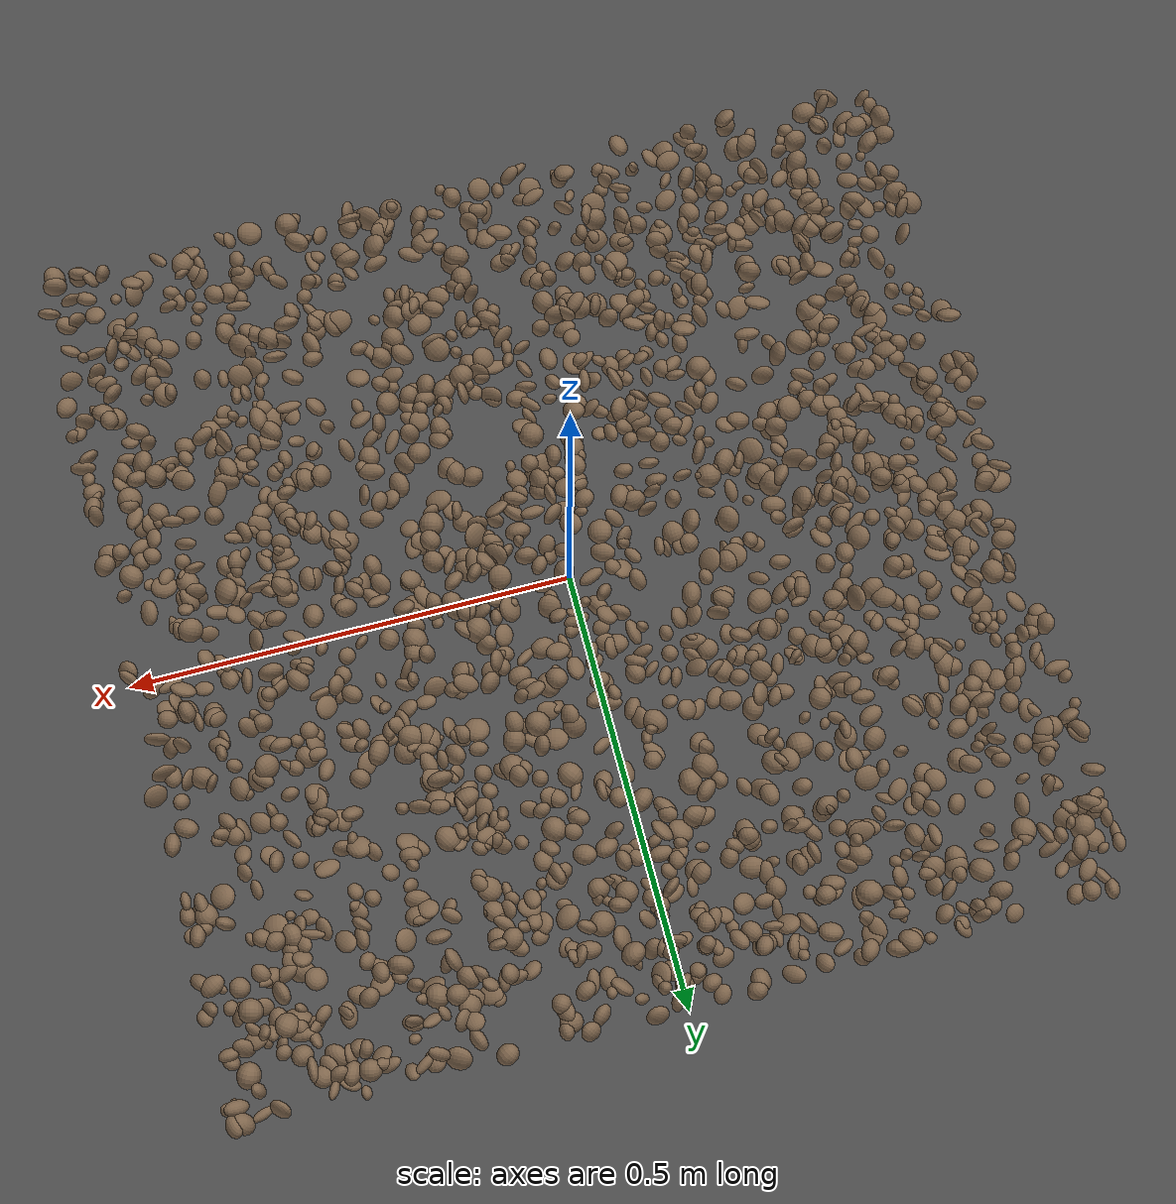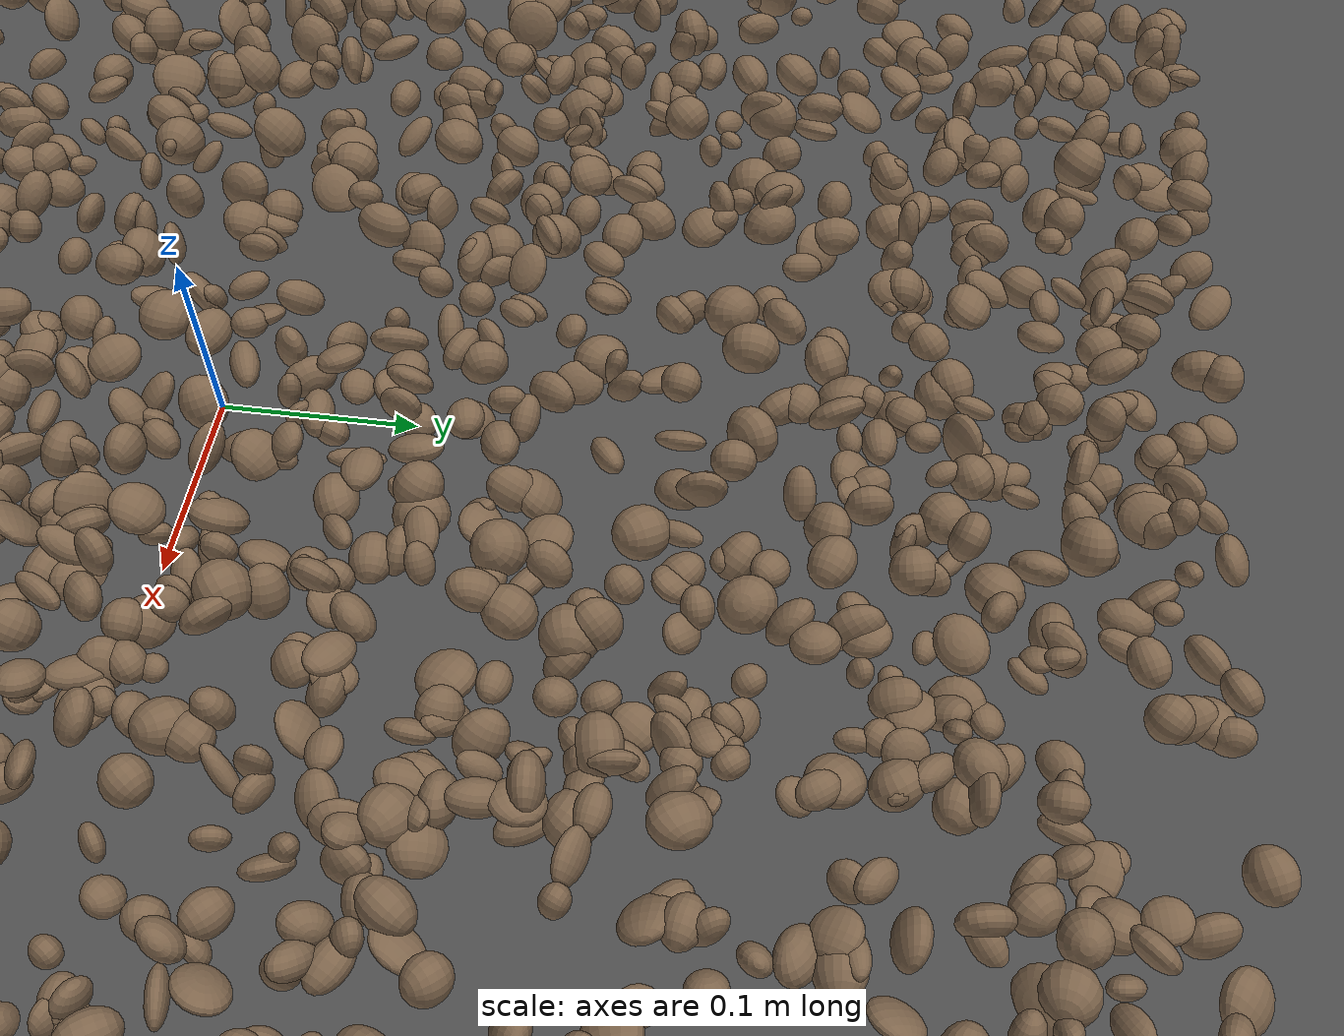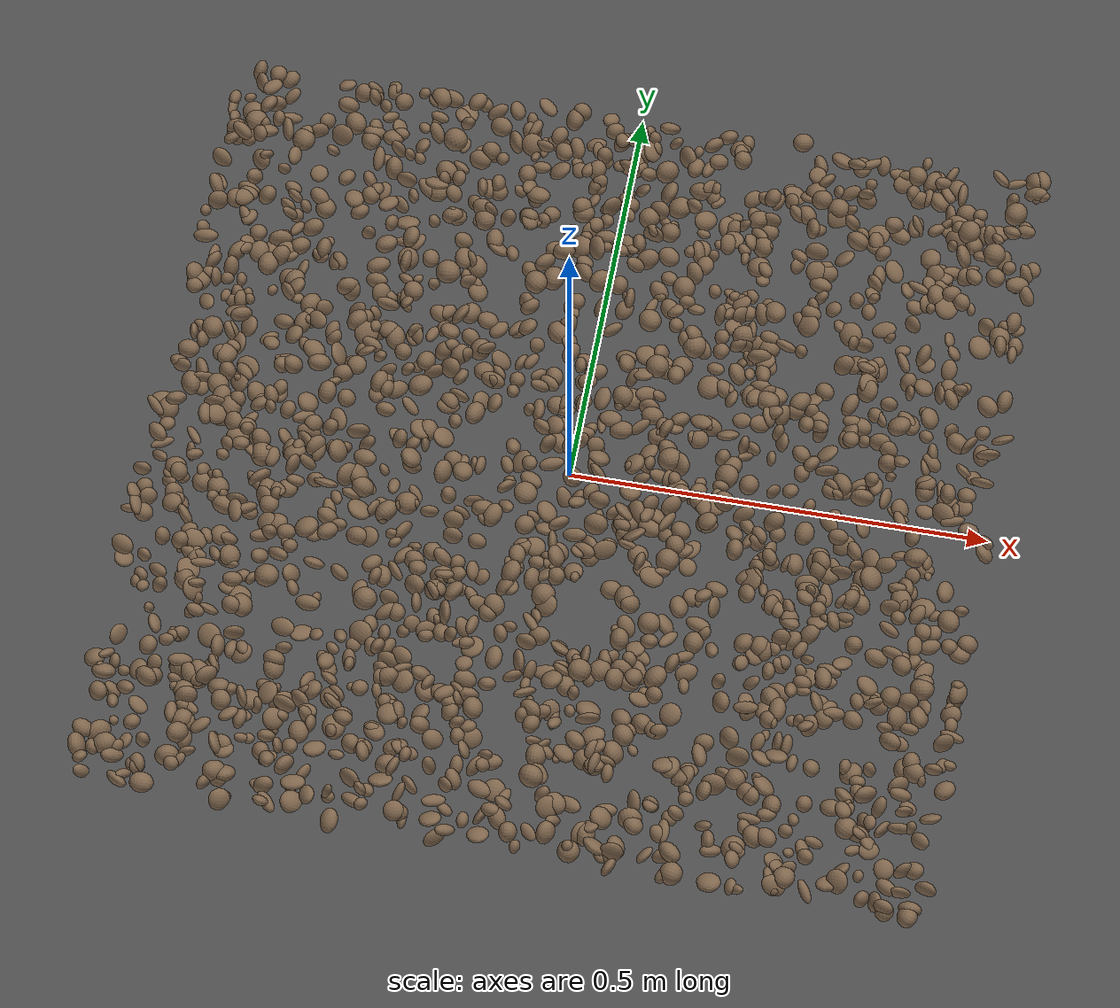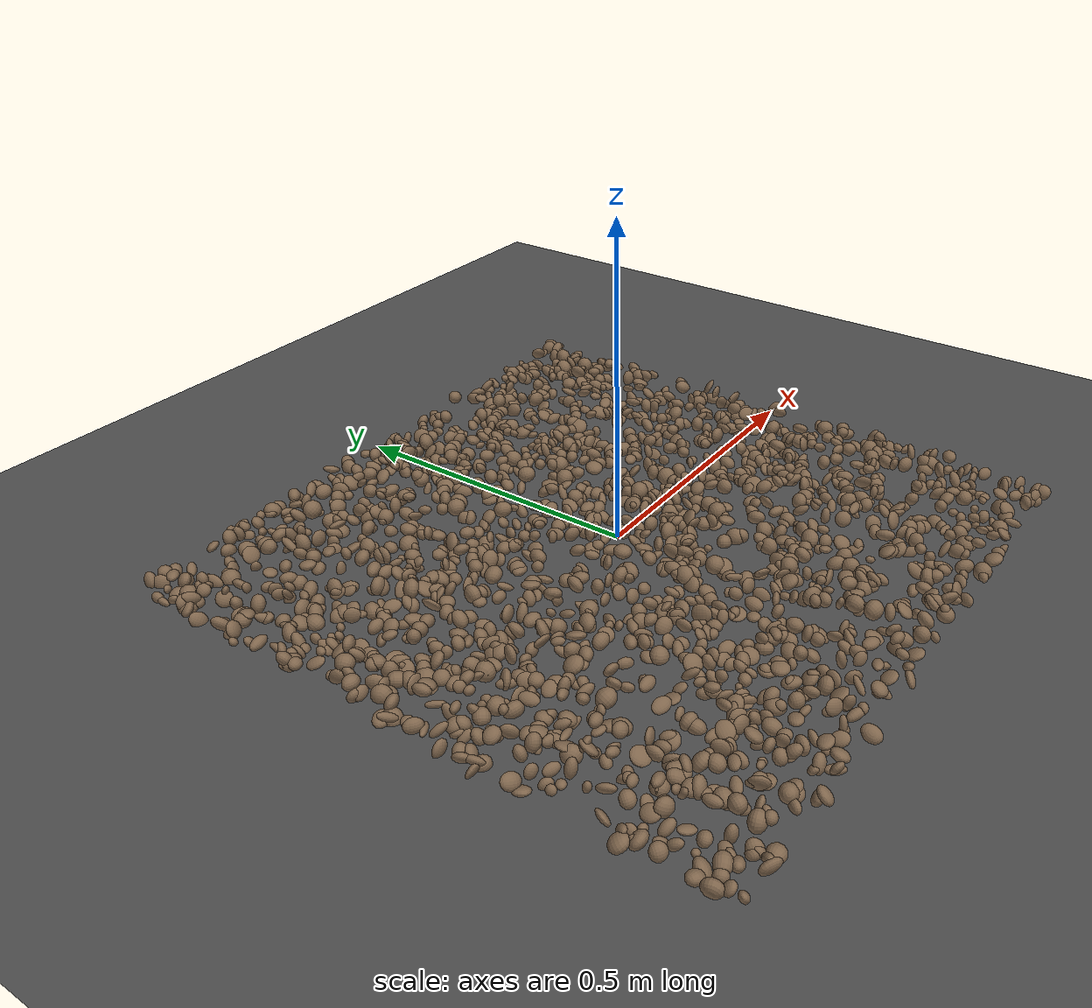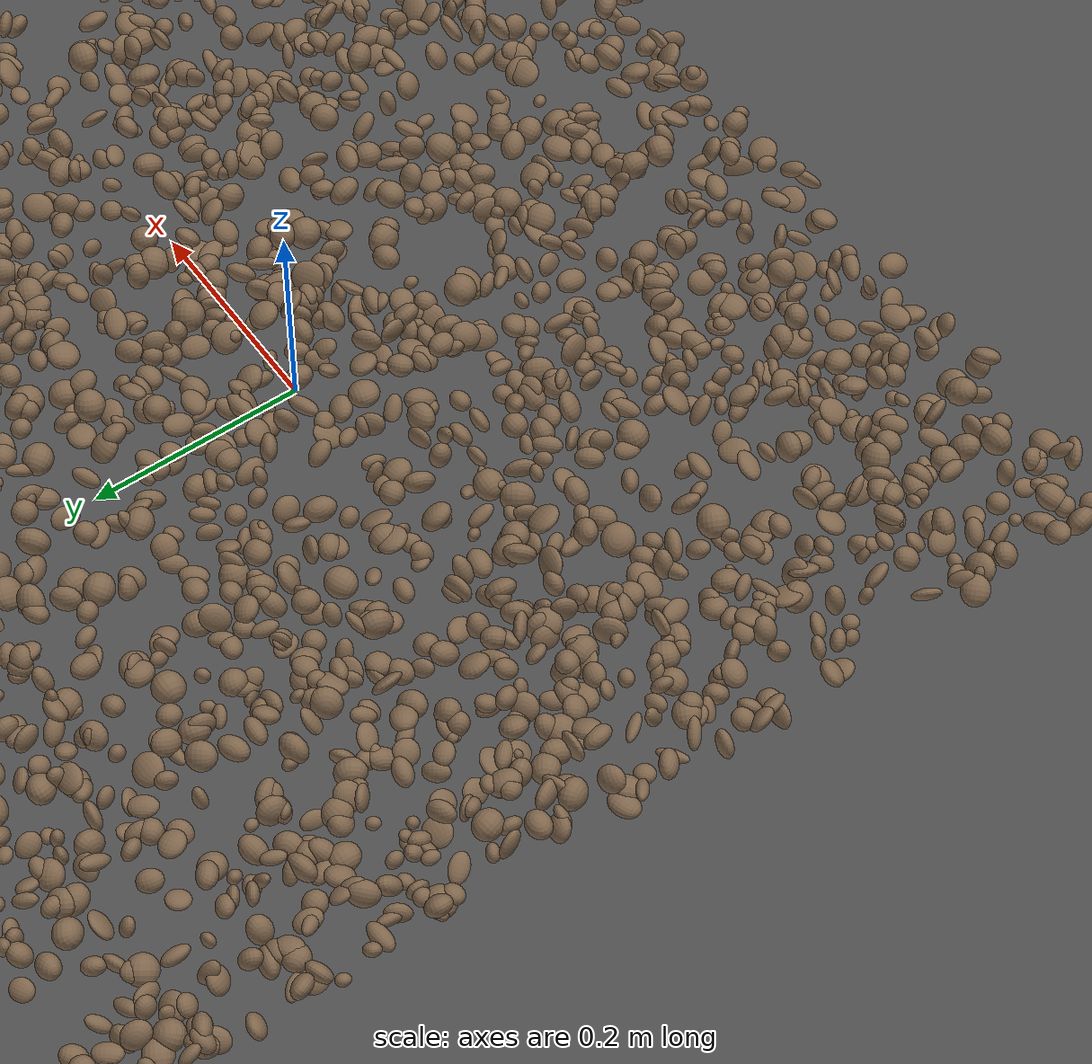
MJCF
<mujoco model="rocky_terrain_scene">
    <compiler angle="radian" inertiafromgeom="true" />
    <option timestep="0.002" gravity="0 0 -9.81" />

    <worldbody>
        <light name="sunlight" pos="5 5 5" dir="-1 -1 -1" diffuse="1 1 1" specular="0.5 0.5 0.5" ambient="0.5 0.5 0.5" />

        <geom name="ground_plane" type="plane" size="50 50 0.1" rgba="0.3 0.3 0.3 1" />

        <body name="rocky_terrain_body">

        <geom name="rock1" type="ellipsoid" size="0.011023393832302778 0.009846887970290735 0.005885824140277965" pos="-0.34088903665864 -0.011558679516007864 0.004798989460099341" quat="0.20091558063148696 0.16909939274905977 0.1840610537260903 0.44592397289336294" rgba="0.5 0.4 0.3 1" /><geom name="rock2" type="ellipsoid" size="0.009627790344105339 0.006083305825145757 0.01061928081510237" pos="0.31404054003404613 0.307259800483778 0.003707244197165801" quat="0.43499511136562247 0.3285799027988819 0.2274037579169202 0.009021227918575465" rgba="0.5 0.4 0.3 1" /><geom name="rock3" type="ellipsoid" size="0.011035395389393 0.01053636750185535 0.011829423977724171" pos="-0.15550435266387186 0.3712816622654833 0.00011973587364540072" quat="0.3318337171368454 0.4111717976262892 0.14661888262887887 0.11037560260798658" rgba="0.5 0.4 0.3 1" /><geom name="rock4" type="ellipsoid" size="0.012241123697709196 0.010333655743753816 0.005848057009413394" pos="-0.22114120466904874 -0.4725191548569033 0.009152191230665152" quat="0.15396687977023657 0.24888445585475547 0.466547592506712 0.13060107186829586" rgba="0.5 0.4 0.3 1" /><geom name="rock5" type="ellipsoid" size="0.013603642355094082 0.006765765352477674 0.006952360372883435" pos="-0.2367909875981009 0.1996085396652495 0.00961377290438707" quat="0.37010941080739534 0.2029261348794532 0.01466033905799151 0.41230411525516" rgba="0.5 0.4 0.3 1" /><geom name="rock6" type="ellipsoid" size="0.01185897787252222 0.010978851052079736 0.011193651785709285" pos="0.42963269348251576 0.18657502953438543 0.004734277289112403" quat="0.0715121407041947 0.3235470228047162 0.27473219923290404 0.330208637258185" rgba="0.5 0.4 0.3 1" /><geom name="rock7" type="ellipsoid" size="0.009995922484596492 0.010024853098148477 0.012681522226316393" pos="-0.03994736194846049 -0.12377541761514521 0.014702165626679623" quat="0.4533712680003174 0.4679860081698387 0.06341439117590118 0.015228332653942649" rgba="0.5 0.4 0.3 1" /><geom name="rock8" type="ellipsoid" size="0.011057460542266476 0.005068638645350443 0.009282691433073531" pos="0.14984912860871924 0.09558110876826675 0.007033070559494317" quat="0.25503935552855844 0.2224231431301627 0.32024896740962155 0.20228853393165727" rgba="0.5 0.4 0.3 1" /><geom name="rock9" type="ellipsoid" size="0.013703617949139317 0.013378880498903237 0.00975589431118883" pos="-0.3244932045822295 -0.03345423277558912 0.010394178124400608" quat="0.124640394762976 0.650885269720421 0.09653930930024807 0.12793502621635486" rgba="0.5 0.4 0.3 1" /><geom name="rock10" type="ellipsoid" size="0.007209157058745946 0.009392399736326749 0.007861614307516076" pos="-0.09378856474681452 0.4526051810743973 0.008354031079102674" quat="0.33595295954843796 0.09733531827554921 0.30452480770394014 0.2621869144720726" rgba="0.5 0.4 0.3 1" /><geom name="rock11" type="ellipsoid" size="0.010759610988029553 0.011519416075323422 0.007705482263603234" pos="0.17081664520230544 -0.1394134475729304 0.007269376590318772" quat="0.37028034425183926 0.16410947284756752 0.06782311475531766 0.3977870681452755" rgba="0.5 0.4 0.3 1" /><geom name="rock12" type="ellipsoid" size="0.006752824735600684 0.013331479974137413 0.013749951790985378" pos="-0.25592233831904 0.007079543826864709 0.012756345346571813" quat="0.1822562839644269 0.25092213507758004 0.3251096832978702 0.24171189766012277" rgba="0.5 0.4 0.3 1" /><geom name="rock13" type="ellipsoid" size="0.006696151067428024 0.008121552039579392 0.011362724167708668" pos="0.44706352743393474 -0.26179363890301566 0.0032504958713964324" quat="0.23600850512250302 0.28190979003253364 0.22312581733813253 0.25895588750683085" rgba="0.5 0.4 0.3 1" /><geom name="rock14" type="ellipsoid" size="0.0071314335451905485 0.007963556394840499 0.014925013942007629" pos="-0.022708820611025526 0.006596003345921031 0.008399408189220784" quat="0.31192623173566497 0.08939029484944107 0.3726722693582087 0.22601120405668534" rgba="0.5 0.4 0.3 1" /><geom name="rock15" type="ellipsoid" size="0.014288836460198701 0.008047039536208136 0.00778991390193183" pos="-0.24284740671073302 0.4336885759454391 0.012201163076462412" quat="0.07124125202500334 0.29116375657133203 0.1820074360758196 0.45558755532784506" rgba="0.5 0.4 0.3 1" /><geom name="rock16" type="ellipsoid" size="0.0061226391541806735 0.012620327520241954 0.00852003286953311" pos="0.4199081495926593 -0.2709033940188177 0.014311877860396303" quat="0.27121087002919303 0.2245809676741738 0.16779960674370412 0.3364085555529291" rgba="0.5 0.4 0.3 1" /><geom name="rock17" type="ellipsoid" size="0.006690178132843399 0.010508701267551102 0.005392069565662623" pos="0.39779021303005657 0.3931492842416564 0.00169526444199897" quat="0.11506727871004445 0.2000609210637016 0.3504893101692829 0.33438249005697107" rgba="0.5 0.4 0.3 1" /><geom name="rock18" type="ellipsoid" size="0.006818271125031005 0.007197185365800546 0.0146889789675693" pos="-0.3245198738532231 0.019121248666433943 0.00484624670009795" quat="0.10331061560959914 0.2524509573336654 0.34276324027923283 0.3014751867775026" rgba="0.5 0.4 0.3 1" /><geom name="rock19" type="ellipsoid" size="0.006853818357598084 0.010067705455005006 0.007563848645570248" pos="-0.22404411830838133 0.31595422517871785 0.0007562810611202359" quat="0.4258752263296451 0.4303831865536074 0.029458371875596967 0.11428321524115047" rgba="0.5 0.4 0.3 1" /><geom name="rock20" type="ellipsoid" size="0.014293824992785142 0.008684615794375182 0.00795951503501511" pos="-0.17806458233266942 -0.21857838270545138 0.000920321528774437" quat="0.3983793007482659 0.3551024747327231 0.039472987969899925 0.20704523654911114" rgba="0.5 0.4 0.3 1" /><geom name="rock21" type="ellipsoid" size="0.008824854694843853 0.009504425987317554 0.012528783071057013" pos="-0.10572660409111456 -0.15712242644072338 0.004976276928034212" quat="0.0292224504836697 0.2873439659269442 0.01720590702384573 0.6662276765655404" rgba="0.5 0.4 0.3 1" /><geom name="rock22" type="ellipsoid" size="0.010606413038683607 0.012368124970119136 0.01236154321667569" pos="-0.29051418365875215 0.08776805311051006 0.001442659342349884" quat="0.20018607788719295 0.1665838162960554 0.26387754854696327 0.3693525572697883" rgba="0.5 0.4 0.3 1" /><geom name="rock23" type="ellipsoid" size="0.006113215382964623 0.014834514501461126 0.012717545064474586" pos="-0.015269338287307588 0.3681969771403467 0.0120561478583413" quat="0.18191583138044576 0.1333749084956709 0.35322218446684045 0.33148707565704294" rgba="0.5 0.4 0.3 1" /><geom name="rock24" type="ellipsoid" size="0.008832279789224977 0.012798555723710841 0.00544970423285481" pos="0.14950589141626025 -0.004026337766368737 0.00012448515307783125" quat="0.3365205516541562 0.3001576352465945 0.2915038624609274 0.07181795063832186" rgba="0.5 0.4 0.3 1" /><geom name="rock25" type="ellipsoid" size="0.005968998059452859 0.009454063397335084 0.0056608929954407574" pos="-0.45092839950020613 -0.26530570230119555 0.00606611186989776" quat="0.2331499797233194 0.28766601722301977 0.19816792840784625 0.2810160746458146" rgba="0.5 0.4 0.3 1" /><geom name="rock26" type="ellipsoid" size="0.014128659365133849 0.01251070845033463 0.0058706081906456115" pos="0.29571959963636973 0.07855619468697317 0.008373197778464347" quat="0.1434655789225662 0.5455926268113648 0.1735273678540258 0.13741442641204327" rgba="0.5 0.4 0.3 1" /><geom name="rock27" type="ellipsoid" size="0.013914430368720487 0.006721790311140755 0.014234781766490984" pos="-0.18296595654629577 0.02367992139496944 0.010960703018893424" quat="0.33384185785787834 0.31378726145270996 0.24367892591806764 0.10869195477134412" rgba="0.5 0.4 0.3 1" /><geom name="rock28" type="ellipsoid" size="0.013843381922103992 0.010134208400344544 0.013081496878308708" pos="-0.09135754351598213 -0.06769789014170935 0.010346684872209366" quat="0.7484555914777584 0.1524219336275577 0.035793142327105294 0.06332933256757865" rgba="0.5 0.4 0.3 1" /><geom name="rock29" type="ellipsoid" size="0.010377838251039707 0.011105197650596341 0.012308259096491227" pos="-0.07516215429081585 0.4977903034096246 0.0069875789481507414" quat="0.10759831605391026 0.3669804634319225 0.4525278310949583 0.07289338941920899" rgba="0.5 0.4 0.3 1" /><geom name="rock30" type="ellipsoid" size="0.010591777040019883 0.010684796107212319 0.009643495808374852" pos="0.09228689908074339 0.06820483886528916 0.002778132074937835" quat="0.015325148626779543 0.059043440017527864 0.47617434093690053 0.449457070418792" rgba="0.5 0.4 0.3 1" /><geom name="rock31" type="ellipsoid" size="0.014488791819177612 0.008517210837864289 0.005925207850227835" pos="0.38990571959524356 0.4290655091254857 0.009344857439934405" quat="0.08132618546741428 0.3423820983673828 0.24924484010103917 0.32704687606416377" rgba="0.5 0.4 0.3 1" /><geom name="rock32" type="ellipsoid" size="0.014866865223677243 0.009110909587133998 0.013058285413418837" pos="-0.18728155440323813 -0.018220926737477106 0.014896592570804428" quat="0.30948014045420896 0.30606967570512184 0.3516288427521772 0.03282134108849204" rgba="0.5 0.4 0.3 1" /><geom name="rock33" type="ellipsoid" size="0.013216283060117476 0.010907738445833766 0.014112258942516106" pos="-0.4713038387893682 0.4304481285634323 0.000426529414550848" quat="0.33590627875553364 0.25870791587170644 0.13191007283650058 0.2734757325362593" rgba="0.5 0.4 0.3 1" /><geom name="rock34" type="ellipsoid" size="0.01021275773570874 0.010168275733302961 0.008875138889814036" pos="-0.4394161547638116 -0.41393112192295944 0.0035994109104510934" quat="0.300765046950811 0.40884428322798627 0.2811878332538937 0.009202836567308999" rgba="0.5 0.4 0.3 1" /><geom name="rock35" type="ellipsoid" size="0.00876423754056889 0.0057895028224333785 0.010152721236922936" pos="-0.07607083313325513 -0.15599771144758323 0.006516871564249502" quat="0.16166801626671765 0.12792987372327008 0.2473101055463075 0.4630920044637047" rgba="0.5 0.4 0.3 1" /><geom name="rock36" type="ellipsoid" size="0.011839381389674938 0.011063478631135642 0.007103735842035405" pos="-0.15180274559378593 0.10769153840246726 0.0024054204585306355" quat="0.3018823169885045 0.22373400798800244 0.4591821374643845 0.015201537559108521" rgba="0.5 0.4 0.3 1" /><geom name="rock37" type="ellipsoid" size="0.01278654607102388 0.005764219104800409 0.013068721965519958" pos="-0.07628763113508186 -0.47396037979359085 0.002057475005113916" quat="0.3548889069995845 0.17227490583365285 0.2594740081037218 0.21336217906304086" rgba="0.5 0.4 0.3 1" /><geom name="rock38" type="ellipsoid" size="0.010514560636605629 0.012165934655814307 0.008282282057843971" pos="-0.16674546778907717 0.37196020514824146 0.0025659656532650873" quat="0.6662152015210586 0.024935307023544177 0.2702503563809087 0.038599135074488436" rgba="0.5 0.4 0.3 1" /><geom name="rock39" type="ellipsoid" size="0.013016933321880201 0.012877448248770525 0.010020244189217644" pos="-0.37244719651600544 -0.18059324959132217 0.0055760077455757956" quat="0.27949635927445216 0.19123449679788507 0.03202482952963538 0.49724431439802746" rgba="0.5 0.4 0.3 1" /><geom name="rock40" type="ellipsoid" size="0.010017812505873936 0.008606447562454753 0.006182837420038278" pos="-0.2902822255718779 -0.2127206730148059 0.012873078823305942" quat="0.20592205237776784 0.17859324984670058 0.22227332599242786 0.3932113717831038" rgba="0.5 0.4 0.3 1" /><geom name="rock41" type="ellipsoid" size="0.010173526970668747 0.0128707168671475 0.01150505611530745" pos="0.49199587422978364 -0.23394361350906356 0.00010213399888032715" quat="0.3228187834404987 0.2881204330245925 0.3564699871047684 0.03259079643014048" rgba="0.5 0.4 0.3 1" /><geom name="rock42" type="ellipsoid" size="0.00878420028808805 0.005673364669348484 0.009569730209680846" pos="-0.01864067938830727 0.06572115103864962 0.0040173286922318046" quat="0.24272709021788638 0.23645480760154972 0.3275724633880518 0.19324563879251214" rgba="0.5 0.4 0.3 1" /><geom name="rock43" type="ellipsoid" size="0.008587014992702546 0.0053692602232793185 0.012095157281667636" pos="0.16186494846355226 0.26264319220846144 0.011641097353299367" quat="0.23534832738529982 0.1532417488595272 0.25415560563922684 0.35725431811594616" rgba="0.5 0.4 0.3 1" /><geom name="rock44" type="ellipsoid" size="0.014003417153787421 0.014629891787559541 0.009826096160382332" pos="0.012651890613346817 -0.32039711891182443 0.013215692475782451" quat="0.03717481911511065 0.1930391727043583 0.3647726618338475 0.40501334634668357" rgba="0.5 0.4 0.3 1" /><geom name="rock45" type="ellipsoid" size="0.01256738393882439 0.013599335333070717 0.010378095568450357" pos="0.30636527422431226 -0.3863198429369843 0.000297388012227332" quat="0.16084039377589152 0.3199009555003673 0.27319048758992126 0.24606816313382" rgba="0.5 0.4 0.3 1" /><geom name="rock46" type="ellipsoid" size="0.013400926819824507 0.010260453729765738 0.012081679669411165" pos="-0.45936296375705454 -0.07598383969600098 0.008801794629886363" quat="0.1561161872018322 0.04418144687523498 0.44985020226800143 0.34985216365493144" rgba="0.5 0.4 0.3 1" /><geom name="rock47" type="ellipsoid" size="0.009868014133816869 0.014640756805353865 0.010440435750770867" pos="0.3951274298607015 -0.17901593739606436 0.006299741935773722" quat="0.403676350286964 0.03742905901374217 0.17260788579461084 0.3862867049046829" rgba="0.5 0.4 0.3 1" /><geom name="rock48" type="ellipsoid" size="0.012276598448963847 0.013014522123328386 0.00976739908847786" pos="0.30305524003914386 -0.10502027265228464 0.005277155653882991" quat="0.3472954903327789 0.022800115587994413 0.156377544649998 0.47352684942922857" rgba="0.5 0.4 0.3 1" /><geom name="rock49" type="ellipsoid" size="0.013271216818545147 0.0073245154883440165 0.012863338996392245" pos="-0.3181101036946713 -0.49841906864489116 0.013829690185685433" quat="0.05533733185843866 0.3899647452434784 0.2398486802806867 0.3148492426173962" rgba="0.5 0.4 0.3 1" /><geom name="rock50" type="ellipsoid" size="0.005172373490854552 0.007126123612323064 0.012643642209253236" pos="0.04091113213493902 -0.32321633540244366 0.002571414291472736" quat="0.07875149548420259 0.0053573279960785845 0.3963507317378391 0.5195404447818798" rgba="0.5 0.4 0.3 1" /><geom name="rock51" type="ellipsoid" size="0.010176319708354144 0.0077922589640485205 0.008133239317922997" pos="-0.35937466858214906 0.05037347511371282 0.009411286837562568" quat="0.19799901785399976 0.39811322583786757 0.16617889503576097 0.23770886127237162" rgba="0.5 0.4 0.3 1" /><geom name="rock52" type="ellipsoid" size="0.011331611110127838 0.011467784634951407 0.011025704019801788" pos="-0.06072326261689054 -0.1986148019143661 0.0021123785784434163" quat="0.08735096806826458 0.1563032411365895 0.11559784417264778 0.6407479466224982" rgba="0.5 0.4 0.3 1" /><geom name="rock53" type="ellipsoid" size="0.006450681042595948 0.014494977009197767 0.0056078974332352495" pos="-0.3070874512434574 -0.042131864714168965 0.007433745159258073" quat="0.3645764721197738 0.22495380739553092 0.12110308226774036 0.289366638216955" rgba="0.5 0.4 0.3 1" /><geom name="rock54" type="ellipsoid" size="0.011382818303819778 0.009231457118250595 0.010316386898736526" pos="-0.030892018703442936 0.47774084021982033 0.00731380258648742" quat="0.05090523672421265 0.6797443337918393 0.13862094194308525 0.13072948754086278" rgba="0.5 0.4 0.3 1" /><geom name="rock55" type="ellipsoid" size="0.012178795765435067 0.01002182467919463 0.011940349140186957" pos="-0.388630562427534 -0.15605481811802224 0.006216526025595395" quat="0.20153997561987716 0.3332764002928631 0.2878774912243395 0.17730613286292024" rgba="0.5 0.4 0.3 1" /><geom name="rock56" type="ellipsoid" size="0.008384558708849982 0.01022393604706828 0.011889493745077535" pos="-0.36710885638476487 0.03581061390946183 0.014446258764010154" quat="0.3029886761475045 0.5204855482829953 0.09742210796662262 0.07910366760287753" rgba="0.5 0.4 0.3 1" /><geom name="rock57" type="ellipsoid" size="0.013682546233437641 0.0050973533081892656 0.013256776823788723" pos="-0.355963138835248 0.4100879604645493 0.01185230911757307" quat="0.21098199340770618 0.5782236070125756 0.011388736204417656 0.19940566337530052" rgba="0.5 0.4 0.3 1" /><geom name="rock58" type="ellipsoid" size="0.014758888919534915 0.00809765581119009 0.012023939104435886" pos="0.2792272071245915 -0.2667101710324986 0.003168011388696768" quat="0.351293914842668 0.16784076604583723 0.25921404096781964 0.22165127814367508" rgba="0.5 0.4 0.3 1" /><geom name="rock59" type="ellipsoid" size="0.01126499053215057 0.012778871127468644 0.008238940202684123" pos="-0.4526052953565668 -0.12759664431423934 0.01425655407003817" quat="0.057667004769308305 0.415540649550122 0.3983890835561946 0.12840326212437508" rgba="0.5 0.4 0.3 1" /><geom name="rock60" type="ellipsoid" size="0.014389085821288602 0.009906750874417199 0.006161889778222418" pos="-0.42393513788391646 0.4113613945950604 0.003647057828429666" quat="0.11107166407084339 0.30251561526883186 0.28776886224900433 0.29864385841132046" rgba="0.5 0.4 0.3 1" /><geom name="rock61" type="ellipsoid" size="0.008991726778463903 0.01311085441609447 0.006964644846638925" pos="-0.33463964803838797 -0.09406371482920572 0.01202986488274589" quat="0.26268864532322356 0.3132785263575489 0.2314105127627156 0.19262231555651194" rgba="0.5 0.4 0.3 1" /><geom name="rock62" type="ellipsoid" size="0.007817233500298858 0.014537526247318175 0.011881072030526636" pos="-0.16500965293743064 0.11393283990970882 0.008967418666571513" quat="0.3153976657607494 0.35590742472895387 0.2774359300939904 0.05125897941630624" rgba="0.5 0.4 0.3 1" /><geom name="rock63" type="ellipsoid" size="0.005504029363485311 0.013885154726270436 0.014097954785630168" pos="0.4832667777223477 0.10790976524509321 0.013851208673699388" quat="0.23765291316252984 0.215673965083935 0.20039065151079868 0.3462824702427365" rgba="0.5 0.4 0.3 1" /><geom name="rock64" type="ellipsoid" size="0.005859684166174198 0.010603213308617026 0.01186394854660518" pos="-0.17742265909435695 -0.20330696279313587 0.007062420599696384" quat="0.20835462503441685 0.3394136363968671 0.3966442616081765 0.05558747696053952" rgba="0.5 0.4 0.3 1" /><geom name="rock65" type="ellipsoid" size="0.007847077552603379 0.00910122625801844 0.010205448857146315" pos="0.2416151485182717 -0.2145424784117952 0.008690149024613639" quat="0.3042296224586862 0.06448033988681204 0.28325649921301255 0.3480335384414892" rgba="0.5 0.4 0.3 1" /><geom name="rock66" type="ellipsoid" size="0.011221676222784027 0.0064149216600258 0.011651543865489077" pos="0.4056474553959537 -0.08654991024737901 0.012427654998005829" quat="0.5110794389625058 0.10191303750780097 0.30746301954252814 0.07954450398716507" rgba="0.5 0.4 0.3 1" /><geom name="rock67" type="ellipsoid" size="0.008633336833280617 0.0055676316866961366 0.005890827898115419" pos="0.00853104396318316 0.3589800124122168 0.01444967744234217" quat="0.12130404165321987 0.2537113833409152 0.301644248481015 0.3233403265248499" rgba="0.5 0.4 0.3 1" /><geom name="rock68" type="ellipsoid" size="0.0128793646799467 0.00989663242767375 0.01442711010789104" pos="-0.3487449238098901 -0.3547679009519835 0.011670989196326649" quat="0.6118171879820126 0.1752235487943353 0.10276611636595245 0.11019314685769972" rgba="0.5 0.4 0.3 1" /><geom name="rock69" type="ellipsoid" size="0.0064051478073148885 0.014710341020251722 0.007513137970188356" pos="-0.22272157722883712 -0.26480902529497796 0.012139424849539723" quat="0.11554714967010167 0.4104919914724985 0.17245653270817168 0.3015043261492282" rgba="0.5 0.4 0.3 1" /><geom name="rock70" type="ellipsoid" size="0.01268768715214239 0.01143240621944087 0.0120551026226957" pos="0.0804795499885359 -0.05161713917093935 0.0027968716424726777" quat="0.2998275009645841 0.2475228375398004 0.341492573328823 0.11115708816679248" rgba="0.5 0.4 0.3 1" /><geom name="rock71" type="ellipsoid" size="0.01428790307520562 0.011252033205353918 0.007195903176255632" pos="0.22941492335865832 -0.0998586994072167 0.007426957479343893" quat="0.20963784560390028 0.5256977224218694 0.14523867908044957 0.11942575289378066" rgba="0.5 0.4 0.3 1" /><geom name="rock72" type="ellipsoid" size="0.008060364932330517 0.00639311823410776 0.010473300563451214" pos="0.27161316692080684 -0.13885187745451655 0.011330273510075227" quat="0.35288893270938243 0.4360564008934869 0.06996879347698805 0.1410858729201427" rgba="0.5 0.4 0.3 1" /><geom name="rock73" type="ellipsoid" size="0.0071137853824047 0.010889782449174625 0.014190575283281652" pos="-0.2226525018050054 0.07655761259397009 0.0020813395590491557" quat="0.2504257593565994 0.04729590722683531 0.45641172296936694 0.24586661044719835" rgba="0.5 0.4 0.3 1" /><geom name="rock74" type="ellipsoid" size="0.011783646863258015 0.00842900822890828 0.0142999187212581" pos="-0.3306043293711348 0.11118440052560952 0.005443980741379605" quat="0.2762858845729144 0.3489443544303098 0.22522123595962854 0.14954852503714727" rgba="0.5 0.4 0.3 1" /><geom name="rock75" type="ellipsoid" size="0.013885483496662 0.007455052577795761 0.01092506731143257" pos="0.2823666323556967 -0.17527132557188507 0.010602266182971817" quat="0.034512517338245466 0.4646999182967655 0.09224648054673046 0.4085410838182586" rgba="0.5 0.4 0.3 1" /><geom name="rock76" type="ellipsoid" size="0.01219249512394436 0.00555399708458585 0.009268190094316543" pos="-0.2929193697853981 0.3457063569517861 0.0014073229681562222" quat="0.23988904162648353 0.3429167538976184 0.14990957641427333 0.2672846280616248" rgba="0.5 0.4 0.3 1" /><geom name="rock77" type="ellipsoid" size="0.012161013408946148 0.012777295689674487 0.011099402278127725" pos="0.3910080488424492 0.4696615775593157 0.0062398534466976616" quat="0.09555419781708198 0.2915713995185566 0.499130449005763 0.11374395365859845" rgba="0.5 0.4 0.3 1" /><geom name="rock78" type="ellipsoid" size="0.0061990095336670005 0.011962842777389637 0.009620392421998646" pos="0.10914560646420535 0.245908497761531 0.008551410263205446" quat="0.008155262376209463 0.40966415917669596 0.30259122956571355 0.27958934888138115" rgba="0.5 0.4 0.3 1" /><geom name="rock79" type="ellipsoid" size="0.014881900102116288 0.014867161348252868 0.005563226760060968" pos="0.25741289099573517 0.4064958609045335 0.002827479639718146" quat="0.5541049573188663 0.23859715891536445 0.04472124191918513 0.16257664184658407" rgba="0.5 0.4 0.3 1" /><geom name="rock80" type="ellipsoid" size="0.013976391217216944 0.0072804713047845545 0.010900451165448735" pos="0.08368227204357648 0.23954584039758464 0.009536375817475169" quat="0.25432115524480586 0.01152150108468285 0.4458477435489292 0.2883096001215822" rgba="0.5 0.4 0.3 1" /><geom name="rock81" type="ellipsoid" size="0.0136876352801907 0.008994351381559643 0.011504894966253724" pos="0.14046488565858806 -0.474730638880946 0.009619270070989625" quat="0.0006881098791611906 0.3092609941147673 0.4464667546016477 0.2435841414044238" rgba="0.5 0.4 0.3 1" /><geom name="rock82" type="ellipsoid" size="0.0084180295858808 0.009596950113912409 0.00827074005508551" pos="-0.15669151244304447 -0.33706348291942523 0.005384936872389049" quat="0.3331954785515191 0.23895905525442468 0.2593772189297642 0.16846824726429205" rgba="0.5 0.4 0.3 1" /><geom name="rock83" type="ellipsoid" size="0.013274694086742162 0.012025733947530133 0.008863453654720221" pos="-0.4921760431104678 0.18730949432642163 0.012279431997168806" quat="0.6030484598565926 0.03177119940635151 0.33452217057428124 0.030658170162774716" rgba="0.5 0.4 0.3 1" /><geom name="rock84" type="ellipsoid" size="0.01484979908388169 0.013164633657961847 0.005764097090385634" pos="-0.155759628709769 0.020824193680402114 0.0051873724513423125" quat="0.5719016330037241 0.02268707924222598 0.2001482750380856 0.20526301271596437" rgba="0.5 0.4 0.3 1" /><geom name="rock85" type="ellipsoid" size="0.008359133799331378 0.012605027881980983 0.014494856518310069" pos="-0.45333815837844926 0.319256257590229 0.0020019055647707926" quat="0.2594189103028067 0.31474623552922293 0.2047503354448435 0.22108451872312693" rgba="0.5 0.4 0.3 1" /><geom name="rock86" type="ellipsoid" size="0.013146301285980634 0.011052516531592341 0.008508071108335478" pos="0.4863514292751092 0.2919235306253277 0.014897233622973752" quat="0.2714725754557569 0.2890853882078175 0.10717531572435843 0.3322667206120672" rgba="0.5 0.4 0.3 1" /><geom name="rock87" type="ellipsoid" size="0.008370393651317795 0.011187195920146765 0.009779294542142335" pos="-0.09071537154716547 -0.10803542979230041 0.001327792930096343" quat="0.3791753614447122 0.0417917672706332 0.2013540021273131 0.3776788691573415" rgba="0.5 0.4 0.3 1" /><geom name="rock88" type="ellipsoid" size="0.009715163936679557 0.008985495423968669 0.010654681882583226" pos="0.4439386110058535 -0.13878857290107882 0.013434602525174307" quat="0.32002817942113354 0.3497468454813975 0.2084046511554841 0.12182032394198486" rgba="0.5 0.4 0.3 1" /><geom name="rock89" type="ellipsoid" size="0.014751425410391792 0.00945876004533116 0.013388826544024245" pos="-0.3207568231240362 -0.46062136840250245 0.00437500393966801" quat="0.40181327635540853 0.100251448645438 0.3276049379672575 0.17033033703189587" rgba="0.5 0.4 0.3 1" /><geom name="rock90" type="ellipsoid" size="0.009793447543285184 0.00507469611705175 0.014464839917122212" pos="0.3356972959874125 0.2554143087494881 0.013762193724065964" quat="0.1995513811715386 0.22128725445979375 0.23578281236765444 0.3433785520010133" rgba="0.5 0.4 0.3 1" /><geom name="rock91" type="ellipsoid" size="0.009420627126269548 0.00670817757771506 0.014621353934393073" pos="-0.08473781349142728 -0.22361433725256996 0.0013168916698708592" quat="0.17928687540238192 0.4558289745787639 0.2974221872803173 0.067461962738537" rgba="0.5 0.4 0.3 1" /><geom name="rock92" type="ellipsoid" size="0.013353167222243174 0.01435658379166379 0.011175698198809538" pos="0.09691746139739443 -0.207867684072098 0.006472740567213711" quat="0.20072185055633895 0.2623704136647142 0.2683156256385714 0.2685921101403754" rgba="0.5 0.4 0.3 1" /><geom name="rock93" type="ellipsoid" size="0.014792247975585045 0.011308683168399523 0.010017042165984077" pos="0.012002743378496272 0.32253558505165014 0.0003256373241936355" quat="0.02582894211434768 0.34875323190270696 0.2981119800272632 0.32730584595568224" rgba="0.5 0.4 0.3 1" /><geom name="rock94" type="ellipsoid" size="0.011509239159651305 0.01246680717033916 0.00832863047264553" pos="-0.15658225141217508 0.37830101376161873 0.007301208994830279" quat="0.19292533359797726 0.2901664108728675 0.19349753676227704 0.3234107187668782" rgba="0.5 0.4 0.3 1" /><geom name="rock95" type="ellipsoid" size="0.014694297071310859 0.005034222460260912 0.012001007955112209" pos="0.05913174855379366 -0.0967712996339466 0.010176752322601504" quat="0.2023773956598232 0.6053804603084163 0.13953783042876325 0.05270431360299714" rgba="0.5 0.4 0.3 1" /><geom name="rock96" type="ellipsoid" size="0.006751038098413324 0.005818263633079158 0.005151653132834523" pos="-0.2278801277813498 0.23273738460450555 0.0001514660299899101" quat="0.2604797206878849 0.3842302111687509 0.249592764008866 0.10569730413449828" rgba="0.5 0.4 0.3 1" /><geom name="rock97" type="ellipsoid" size="0.005662426430013885 0.00662694899976739 0.00967667686806432" pos="-0.19806229634361672 -0.41458723069867953 0.0065337797482279405" quat="0.2072949941120736 0.318267156356755 0.090397108000438 0.3840407415307333" rgba="0.5 0.4 0.3 1" /><geom name="rock98" type="ellipsoid" size="0.010394618456390822 0.007921402275401957 0.012404372946434027" pos="-0.0497301151592805 0.4545351575893145 0.006322086013296213" quat="0.34039277373375343 0.09289997463129195 0.33871965513836166 0.22798759649659298" rgba="0.5 0.4 0.3 1" /><geom name="rock99" type="ellipsoid" size="0.012118075248238503 0.005300522963665496 0.011483056239033925" pos="-0.3766294951131238 0.18163206935561482 0.011725566469749371" quat="0.262167404879798 0.03400031666676559 0.040960948714392924 0.6628713297390436" rgba="0.5 0.4 0.3 1" /><geom name="rock100" type="ellipsoid" size="0.013363726859598558 0.006967617290497716 0.006123318007838806" pos="-0.4481831171759184 0.2764102220357776 0.011957208293536494" quat="0.0770396396450256 0.2436868365690424 0.3865105119064107 0.29276301187952125" rgba="0.5 0.4 0.3 1" /><geom name="rock101" type="ellipsoid" size="0.011599413969165707 0.014648709017407991 0.009588716692376108" pos="0.2942182838740153 -0.17202458222074968 0.002576691808208009" quat="0.2341266091467467 0.31804427249689876 0.3524541732514817 0.09537494510487284" rgba="0.5 0.4 0.3 1" /><geom name="rock102" type="ellipsoid" size="0.008612803962291566 0.005554595539951313 0.0070123128100969215" pos="-0.19172871738888864 -0.11663639735794806 0.0030234286444739173" quat="0.3647844100931697 0.03071937106922151 0.5931418436623019 0.011354375175306857" rgba="0.5 0.4 0.3 1" /><geom name="rock103" type="ellipsoid" size="0.006672489436560364 0.005252993011325591 0.007758727305803972" pos="-0.25900348272100904 0.4386933153929148 0.010917310504656967" quat="0.3769643657933052 0.30987217945207535 0.18485797944832066 0.12830547530629885" rgba="0.5 0.4 0.3 1" /><geom name="rock104" type="ellipsoid" size="0.0099528639381723 0.012740536270245567 0.014567329112490961" pos="-0.03505916934102182 -0.10573709079983695 0.001235331815382108" quat="0.08491299998932984 0.2629684147628438 0.2807636219361739 0.3713549633116524" rgba="0.5 0.4 0.3 1" /><geom name="rock105" type="ellipsoid" size="0.010573082032046821 0.009092040310034556 0.007081331138377302" pos="-0.40415238701057277 -0.16025040563078874 0.006903334804059111" quat="0.22990325223817495 0.1397419877147996 0.26164818951739544 0.3687065705296299" rgba="0.5 0.4 0.3 1" /><geom name="rock106" type="ellipsoid" size="0.009499868543188641 0.010406751033764143 0.011773519386941086" pos="0.2656145164651058 0.07195190557553277 0.009655026196360956" quat="0.30912627294236 0.3763188092792811 0.0513738105064031 0.2631811072719559" rgba="0.5 0.4 0.3 1" /><geom name="rock107" type="ellipsoid" size="0.014724607206783303 0.014989145570735767 0.007130544294025645" pos="-0.004203854561660503 0.4261694486765797 0.011603795448682775" quat="0.007205063762876902 0.08101017273910954 0.42771966918307175 0.4840650943149418" rgba="0.5 0.4 0.3 1" /><geom name="rock108" type="ellipsoid" size="0.00701890180887561 0.012927602207019547 0.009162913395566522" pos="-0.06784651940435171 -0.3526150826322294 0.014135858583386389" quat="0.1319210046451667 0.22767789960012097 0.31977152786864393 0.3206295678860685" rgba="0.5 0.4 0.3 1" /><geom name="rock109" type="ellipsoid" size="0.012833828650647368 0.013833223902738535 0.006022273507199871" pos="0.39775090563732496 -0.4566278156136867 0.0057381077623483035" quat="0.24702413401764362 0.39050438869134496 0.24950716694672992 0.1129643103442816" rgba="0.5 0.4 0.3 1" /><geom name="rock110" type="ellipsoid" size="0.012266397159142826 0.01216002411381142 0.0068214113308648515" pos="0.10261775789027949 0.07591614188551932 0.014145476116585795" quat="0.3677929874407403 0.16587503536937598 0.4649411051404903 0.001390872049393441" rgba="0.5 0.4 0.3 1" /><geom name="rock111" type="ellipsoid" size="0.008510381142703558 0.006611437699324296 0.012917922121134798" pos="-0.36150859914147804 0.08841497415016408 0.0083875822567277" quat="0.2403337474895945 0.21384835887170764 0.21257394447649708 0.33324394916220085" rgba="0.5 0.4 0.3 1" /><geom name="rock112" type="ellipsoid" size="0.010083455386607081 0.011893046935220968 0.01085275732525072" pos="0.456482151615504 -0.3093878762052191 0.0144748178467984" quat="0.7103071920268487 0.20618772981973654 0.03991043039471436 0.04359464775870031" rgba="0.5 0.4 0.3 1" /><geom name="rock113" type="ellipsoid" size="0.005996104863417205 0.011836889394248621 0.007063567972541188" pos="-0.42696521392381026 0.4554707773383647 0.009396938958387457" quat="0.34902743471204833 0.2482442411531218 0.4020695052687885 0.0006588188660413482" rgba="0.5 0.4 0.3 1" /><geom name="rock114" type="ellipsoid" size="0.00915536937810607 0.010225452076045548 0.00761797154291294" pos="0.28026344194271224 -0.42110278264777923 0.005428517958612367" quat="0.2838142550971521 0.1925333862307425 0.23957662747555433 0.28407573119655105" rgba="0.5 0.4 0.3 1" /><geom name="rock115" type="ellipsoid" size="0.008104526050947723 0.01256845946777828 0.00803880474620387" pos="0.2809576453672755 0.11138451481260514 0.01104102611156791" quat="0.06690125087471664 0.41757777081399533 0.28828164188553435 0.22723933642575367" rgba="0.5 0.4 0.3 1" /><geom name="rock116" type="ellipsoid" size="0.0108081813887499 0.01254345048533458 0.011019525425687713" pos="-0.12431464895836664 0.3968414933952782 0.009419407081538498" quat="0.14809777462464244 0.6558764319455619 0.04076543695884683 0.1552603564709488" rgba="0.5 0.4 0.3 1" /><geom name="rock117" type="ellipsoid" size="0.005782829219729922 0.005619217057179706 0.014446697015995588" pos="-0.39541246786602235 0.28830335276710806 0.014038775033003334" quat="0.11323904356294015 0.2489637656834433 0.5236239506041358 0.11417324014948081" rgba="0.5 0.4 0.3 1" /><geom name="rock118" type="ellipsoid" size="0.014395732856097965 0.014035846432946603 0.011414496921558095" pos="-0.24423423624958918 0.25493698871372006 0.006264318171181717" quat="0.48432450535455424 0.13635022846802092 0.27575879323715186 0.103566472940273" rgba="0.5 0.4 0.3 1" /><geom name="rock119" type="ellipsoid" size="0.012241112441134103 0.009944758118930688 0.014756479961885876" pos="-0.32843231511355386 -0.12675386610818584 0.002026441722939641" quat="0.29556783282283117 0.18849666661019468 0.1981812438509438 0.31775425671603047" rgba="0.5 0.4 0.3 1" /><geom name="rock120" type="ellipsoid" size="0.010260246579466406 0.007011126856351305 0.012727816454402791" pos="-0.4828004584239495 0.40075890901586875 0.00905152014796297" quat="0.06494808660836804 0.32548035322496055 0.32802571984954915 0.2815458403171222" rgba="0.5 0.4 0.3 1" /><geom name="rock121" type="ellipsoid" size="0.013161251969518686 0.01395451868964296 0.008189134705563289" pos="-0.32311895986761496 0.03726011868953061 0.00794739144015125" quat="0.17632978262033108 0.14470818872811644 0.11495466273767793 0.5640073659138746" rgba="0.5 0.4 0.3 1" /><geom name="rock122" type="ellipsoid" size="0.006662144783254644 0.011464170865436593 0.00830430974721033" pos="0.2689096733590647 0.1305603871730151 0.009690775576332557" quat="0.2474632940265162 0.15093100000838572 0.3526848830907823 0.24892082287431583" rgba="0.5 0.4 0.3 1" /><geom name="rock123" type="ellipsoid" size="0.012367359516593754 0.006489643486121221 0.00670556538988624" pos="-0.195221424244996 0.15650327853418766 0.00725445000623176" quat="0.33263602284357363 0.23952158202434065 0.23500194347178585 0.1928404516602998" rgba="0.5 0.4 0.3 1" /><geom name="rock124" type="ellipsoid" size="0.006535905234467759 0.00964618533480073 0.00777578585908698" pos="-0.4080026965731358 -0.08188204784679987 0.012775038881629518" quat="0.36649055501111616 0.4538183325750143 0.09762130651472016 0.08206980589914945" rgba="0.5 0.4 0.3 1" /><geom name="rock125" type="ellipsoid" size="0.006697598429259227 0.005999173258546772 0.007427004071582971" pos="0.06284908169210723 0.2601128611348327 0.0024526590043336158" quat="0.21709714672798391 0.3005197992303529 0.14259247624543891 0.3397905777962243" rgba="0.5 0.4 0.3 1" /><geom name="rock126" type="ellipsoid" size="0.01134282637427491 0.013500353696182722 0.010953389509389917" pos="0.4970779539718335 -0.14335349286906074 0.007586546196777757" quat="0.3120053149688621 0.262732970669735 0.0874213149311536 0.3378403994302494" rgba="0.5 0.4 0.3 1" /><geom name="rock127" type="ellipsoid" size="0.01486784460602186 0.0066281198019167474 0.006830827699889345" pos="-0.30561780015023976 0.38469689134320195 0.011914273698709628" quat="0.1958559790548373 0.3066980198646495 0.18288638684942174 0.31455961423109136" rgba="0.5 0.4 0.3 1" /><geom name="rock128" type="ellipsoid" size="0.009496386674936581 0.01355379150431276 0.009864447192655345" pos="-0.1778514950564244 0.13737969650713622 0.0057082324709767296" quat="0.023610037247698393 0.18557331860487097 0.49613485187281425 0.2946817922746163" rgba="0.5 0.4 0.3 1" /><geom name="rock129" type="ellipsoid" size="0.01392942015429012 0.01174816646997768 0.0069359588565554055" pos="-0.23570139398055145 0.0812447140025937 0.004361119689757154" quat="0.2226685057561388 0.27568115846191354 0.2243743993134898 0.2772759364684577" rgba="0.5 0.4 0.3 1" /><geom name="rock130" type="ellipsoid" size="0.013814449185492836 0.014434088211364004 0.005132872831773666" pos="0.4973484009211635 0.131007971616389 0.014652155760510719" quat="0.29523115567588837 0.49797197339196003 0.17572664932080373 0.031070221611347867" rgba="0.5 0.4 0.3 1" /><geom name="rock131" type="ellipsoid" size="0.01290186716221543 0.01244521987045512 0.009956877915919917" pos="0.46127597962970646 -0.3205283472152649 0.01154311631322726" quat="0.010692653002415103 0.18295276612187894 0.5091292873447923 0.2972252935309137" rgba="0.5 0.4 0.3 1" /><geom name="rock132" type="ellipsoid" size="0.010266544507491806 0.010404318175649588 0.013428724387922454" pos="0.11770164742915434 -0.26005668073810717 0.0014684232199788738" quat="0.13536603963605887 0.32876887831463025 0.3633077505125906 0.17255733153672026" rgba="0.5 0.4 0.3 1" /><geom name="rock133" type="ellipsoid" size="0.007272649740636704 0.006484278543666311 0.012109190571559573" pos="-0.08258247473293057 -0.18239527607668948 0.005559215186628522" quat="0.2892406706598364 0.35220635259846145 0.3418742070643004 0.016678769677401728" rgba="0.5 0.4 0.3 1" /><geom name="rock134" type="ellipsoid" size="0.013848771310327652 0.010145764966746247 0.014828254471847189" pos="-0.09268180554374184 -0.31349508746732735 0.003263503435884104" quat="0.2757457182505139 0.2146880498776253 0.3928436873633839 0.1167225445084768" rgba="0.5 0.4 0.3 1" /><geom name="rock135" type="ellipsoid" size="0.005797486001083903 0.013701184753359182 0.009394748296420636" pos="0.35435669365213496 0.31726940948655413 0.008924913606868106" quat="0.14330199395217932 0.5319517647420617 0.08288283962085169 0.2418634016849073" rgba="0.5 0.4 0.3 1" /><geom name="rock136" type="ellipsoid" size="0.010759545856739924 0.006170872749680345 0.012865121126838144" pos="-0.2485301734820814 -0.0714208739861294 0.0017422447736048195" quat="0.21911409267450077 0.1206741073116672 0.5463360902136596 0.11387570980017238" rgba="0.5 0.4 0.3 1" /><geom name="rock137" type="ellipsoid" size="0.014462863326550213 0.008033040444787153 0.008415727668449733" pos="-0.08940648176687294 -0.3164736399112793 0.011840951702725255" quat="0.40497426768477746 0.31911415158391493 0.16263138565442434 0.11328019507688328" rgba="0.5 0.4 0.3 1" /><geom name="rock138" type="ellipsoid" size="0.007308018860646185 0.014198045650394443 0.008017162330033658" pos="-0.2087809470592572 0.4538147891943046 0.012026053366196509" quat="0.10094935689257999 0.2532205286075521 0.31603011896220323 0.32979999553766454" rgba="0.5 0.4 0.3 1" /><geom name="rock139" type="ellipsoid" size="0.012257758608997624 0.012683083298856972 0.014141506453241616" pos="0.450130161990025 -0.31488706045985726 0.0013778356075300746" quat="0.27586795090011773 0.4643829662430489 0.17935623838154163 0.0803928444752917" rgba="0.5 0.4 0.3 1" /><geom name="rock140" type="ellipsoid" size="0.01346311717103734 0.01245839140129593 0.010572641147893757" pos="0.21813891427315601 0.40535855807753696 0.000678698194907576" quat="0.3119528513574358 0.02328486512433116 0.34254914601460335 0.3222131375036297" rgba="0.5 0.4 0.3 1" /><geom name="rock141" type="ellipsoid" size="0.007888801390588875 0.013536622386141756 0.006596533687174207" pos="-0.018264472930896503 0.37365126450473873 0.0026567217359858746" quat="0.1300255560180275 0.2908582957478289 0.5227445363778646 0.056371611856279036" rgba="0.5 0.4 0.3 1" /><geom name="rock142" type="ellipsoid" size="0.007234256190177046 0.009462197949402701 0.007570945997375379" pos="-0.03869381212496292 0.3230863070595046 0.007121011273635324" quat="0.2091234425883091 0.35076413984127314 0.21094447300492356 0.22916794456549414" rgba="0.5 0.4 0.3 1" /><geom name="rock143" type="ellipsoid" size="0.005231552973094591 0.012852609262577218 0.013559033504561634" pos="-0.4999374608144498 -0.13773841222162264 0.0022318217952998843" quat="0.2546491969373528 0.2532217859442352 0.13756936822434562 0.3545596488940663" rgba="0.5 0.4 0.3 1" /><geom name="rock144" type="ellipsoid" size="0.010967010683290325 0.014455677870112076 0.005764706961437889" pos="0.16416228141456424 0.24838770493094053 0.008651348848920007" quat="0.3069917472529513 0.33044739269288115 0.03946288327335382 0.32309797678081376" rgba="0.5 0.4 0.3 1" /><geom name="rock145" type="ellipsoid" size="0.007584208042776705 0.008541186867560993 0.014777866362192353" pos="0.4023487194031754 0.42140227900396954 0.009866496544759166" quat="0.31234685732787 0.20953060107595212 0.3829821183978578 0.0951404231983201" rgba="0.5 0.4 0.3 1" /><geom name="rock146" type="ellipsoid" size="0.006021004194151773 0.011072383181376346 0.006065956711929011" pos="0.04549957271384952 0.4752849867420078 0.0048006388895678025" quat="0.09460924508584385 0.26964782494369416 0.3839036568101109 0.25183927316035115" rgba="0.5 0.4 0.3 1" /><geom name="rock147" type="ellipsoid" size="0.011864567532810797 0.009806225108923303 0.0104155667051887" pos="-0.4414119718192391 -0.3145916255206468 0.007770854737789951" quat="0.30528889470721987 0.36046164608259446 0.021432695667142527 0.31281676354304316" rgba="0.5 0.4 0.3 1" /><geom name="rock148" type="ellipsoid" size="0.009517574383246949 0.009220253369760213 0.009401289660810752" pos="-0.12258161604192941 -0.18296737407765407 0.009093767630759062" quat="0.020004363216344957 0.41133947665343834 0.4676901225552025 0.10096603757501434" rgba="0.5 0.4 0.3 1" /><geom name="rock149" type="ellipsoid" size="0.007965371754573536 0.008916226682973349 0.012746597355483367" pos="0.454717116592132 -0.15408186664082235 0.007613437422591675" quat="0.30736698198427986 0.06744584000001759 0.3820311690209127 0.24315600899478976" rgba="0.5 0.4 0.3 1" /><geom name="rock150" type="ellipsoid" size="0.0061022464748420185 0.00782326433526703 0.007147979280551673" pos="-0.06806075722308269 0.4252499700190855 0.005298005875677014" quat="0.012710248517591909 0.6140000971596478 0.0176673651999141 0.3556222891228461" rgba="0.5 0.4 0.3 1" /><geom name="rock151" type="ellipsoid" size="0.012610226444282545 0.007774664808073599 0.009816399490490763" pos="0.1315585402322914 0.34260434698178344 0.009620866104003195" quat="0.14774942171641822 0.321567648125494 0.22295520124699114 0.3077277289110967" rgba="0.5 0.4 0.3 1" /><geom name="rock152" type="ellipsoid" size="0.005513410034755151 0.007480295787216418 0.008770962410382088" pos="-0.44812523395385895 -0.4513289880222313 0.01078579446266518" quat="0.24722559902962518 0.007240549503077628 0.3343062437683664 0.4112276076989308" rgba="0.5 0.4 0.3 1" /><geom name="rock153" type="ellipsoid" size="0.011158415931396586 0.006725295221532487 0.006980316278809386" pos="-0.07389976854698643 -0.005065067170217152 0.010654781541270971" quat="0.17969107597579506 0.19403924435682368 0.25144493455115635 0.3748247451162249" rgba="0.5 0.4 0.3 1" /><geom name="rock154" type="ellipsoid" size="0.008509477597803433 0.010310643712765518 0.013181206387423719" pos="-0.05924719056088046 -0.4224708901246863 0.00859178805889989" quat="0.2334438655791768 0.5777920083768813 0.04675284571490323 0.14201128032903867" rgba="0.5 0.4 0.3 1" /><geom name="rock155" type="ellipsoid" size="0.013960413721018892 0.014575481009196735 0.010956689556370854" pos="0.2831331240762285 -0.25281796316020555 0.006046331233525847" quat="0.0716568750618211 0.2596238487151598 0.28123159545075466 0.38748768077226436" rgba="0.5 0.4 0.3 1" /><geom name="rock156" type="ellipsoid" size="0.008133813164771703 0.009660292559355754 0.011294530705986015" pos="0.029592113132473896 -0.0210793452872573 0.008090061133851356" quat="0.14260565372977219 0.10294214508339168 0.41382844771620386 0.3406237534706323" rgba="0.5 0.4 0.3 1" /><geom name="rock157" type="ellipsoid" size="0.012054170793385312 0.01384008378880448 0.012469518098247326" pos="0.10618600795870592 0.16630546929424517 0.006413142738938252" quat="0.17683913596264486 0.4081618276788454 0.029894121458411426 0.3851049149000983" rgba="0.5 0.4 0.3 1" /><geom name="rock158" type="ellipsoid" size="0.005037653707632227 0.007395957878498224 0.008537960518813455" pos="-0.3644460590636578 0.17697676832045528 0.007583133917262203" quat="0.04358783886028204 0.5165386519292791 0.04990315250032309 0.38997035671011576" rgba="0.5 0.4 0.3 1" /><geom name="rock159" type="ellipsoid" size="0.010769794855485093 0.005834700443406636 0.009220632592844856" pos="0.4601560579564067 -0.2332753672943061 0.0059452964393675225" quat="0.29098632031786975 0.08703295012581963 0.2033937711145588 0.4185869584417518" rgba="0.5 0.4 0.3 1" /><geom name="rock160" type="ellipsoid" size="0.005152283851426175 0.005596255374362633 0.0075681753527935495" pos="0.42908818095349555 -0.1755605562483461 0.012227021186717032" quat="0.20412024654070235 0.50046587087396 0.029002686055906546 0.2664111965294311" rgba="0.5 0.4 0.3 1" /><geom name="rock161" type="ellipsoid" size="0.01436681027097243 0.009369222496737564 0.01123657456399738" pos="0.25031817303380666 0.31018854620146874 0.0017648679452032644" quat="0.11781659030161143 0.07667331416186772 0.6400725500118665 0.1654375455246545" rgba="0.5 0.4 0.3 1" /><geom name="rock162" type="ellipsoid" size="0.008468192198397643 0.013604615516806421 0.006225245168251115" pos="-0.11848173568162601 0.37856225038622693 0.011709508160920437" quat="0.07636891729463993 0.08691941050042973 0.17143941876591504 0.6652722534390152" rgba="0.5 0.4 0.3 1" /><geom name="rock163" type="ellipsoid" size="0.009230678502481101 0.009928466655587503 0.006631391667845881" pos="0.09066107878945573 0.026554852645773175 0.010387247603062439" quat="0.30939139820330697 0.23423735257520303 0.31602892112182485 0.1403423280996652" rgba="0.5 0.4 0.3 1" /><geom name="rock164" type="ellipsoid" size="0.014642553947887015 0.008726586449506914 0.009321858138208095" pos="0.3503702801709613 0.41182152330002764 0.0005541457400531313" quat="0.2985575425563517 0.2147575986779257 0.245647720995958 0.24103713776976451" rgba="0.5 0.4 0.3 1" /><geom name="rock165" type="ellipsoid" size="0.014932275174823543 0.006632118096533125 0.014611835353543694" pos="-0.23529662783202687 -0.09316847801169859 0.006042528884255896" quat="0.22297781023489643 0.25215430675081485 0.3655793978092835 0.15928848520500516" rgba="0.5 0.4 0.3 1" /><geom name="rock166" type="ellipsoid" size="0.009767513414014358 0.013517090202921397 0.013314981591686002" pos="-0.43391648663970894 -0.3581631452416748 0.013999570333961996" quat="0.49105944843599 0.10019845613576762 0.10489439117286255 0.30384770425537977" rgba="0.5 0.4 0.3 1" /><geom name="rock167" type="ellipsoid" size="0.006003038473580174 0.01201183128558479 0.010235683998452516" pos="-0.46328479229774033 -0.0824320940934915 0.0027724291096163528" quat="0.1322222768469982 0.4130613236879916 0.11076323765603822 0.34395316180897195" rgba="0.5 0.4 0.3 1" /><geom name="rock168" type="ellipsoid" size="0.007064391225413297 0.010432238497563197 0.013927538213097904" pos="-0.03130675179830411 0.029608023109634396 0.014361455679652033" quat="0.25515688003244535 0.030913248408306993 0.10473143239844865 0.609198439160799" rgba="0.5 0.4 0.3 1" /><geom name="rock169" type="ellipsoid" size="0.00534398783285064 0.01240454369276599 0.012165114157662487" pos="0.26025157174342095 -0.27251079853002924 0.004253745917022327" quat="0.24971967294240371 0.01890022009444231 0.3949683125429639 0.33641179442019015" rgba="0.5 0.4 0.3 1" /><geom name="rock170" type="ellipsoid" size="0.005079317282171908 0.013168099889461615 0.011649142308411155" pos="0.033917350245720956 -0.36424200104618676 0.011929501954224684" quat="0.04950821295047961 0.22065693741311118 0.47128691281770485 0.2585479368187044" rgba="0.5 0.4 0.3 1" /><geom name="rock171" type="ellipsoid" size="0.006380661242697258 0.0076259568560153685 0.006385686795084723" pos="-0.2694284738772593 0.49046519126849597 0.005922197580737713" quat="0.28754952376358667 0.33438789665620533 0.32890125312312907 0.049161326457078935" rgba="0.5 0.4 0.3 1" /><geom name="rock172" type="ellipsoid" size="0.01189726001068626 0.01449094221154544 0.01159458605398759" pos="-0.3212170764981336 0.41383733239406595 0.004829395061245823" quat="0.13914746245525658 0.5015194587076119 0.126513921541289 0.2328191572958425" rgba="0.5 0.4 0.3 1" /><geom name="rock173" type="ellipsoid" size="0.013980046144478345 0.009877351106132254 0.006046394832838751" pos="-0.3608412504281895 -0.042793596823774926 0.012035094691015784" quat="0.3395165996981242 0.3667914956911318 0.1125634382294663 0.18112846638127775" rgba="0.5 0.4 0.3 1" /><geom name="rock174" type="ellipsoid" size="0.01215493941824465 0.008687758197370589 0.013707090228586665" pos="0.19908400523601677 -0.3720468125112245 0.006352033172538589" quat="0.4046164879422018 0.1152548585789806 0.2176648556505886 0.26246379782822893" rgba="0.5 0.4 0.3 1" /><geom name="rock175" type="ellipsoid" size="0.0055450996813928245 0.00987078560625166 0.011256035638444621" pos="-0.2052795250605317 0.39286751978602585 0.007648403850150894" quat="0.27277885078908537 0.36512438940011843 0.11148274374848516 0.2506140160623111" rgba="0.5 0.4 0.3 1" /><geom name="rock176" type="ellipsoid" size="0.014319353824358356 0.012373491013247539 0.01214222191148177" pos="0.41219321781608054 -0.09980398469213747 0.008686723419143599" quat="0.28927509114198086 0.16246417800908217 0.053918697295462656 0.4943420335534744" rgba="0.5 0.4 0.3 1" /><geom name="rock177" type="ellipsoid" size="0.012112405158539322 0.010486098658173161 0.0072493661939024515" pos="-0.4887254535250988 0.29951023031250446 0.0008731571451261388" quat="0.24693985147997577 0.23329367226782247 0.4629587922098851 0.05680768404231665" rgba="0.5 0.4 0.3 1" /><geom name="rock178" type="ellipsoid" size="0.01180252126234873 0.00966208610806169 0.013302691403415796" pos="-0.0546593481774994 -0.19042855397392144 0.007415737054047799" quat="0.26582422198695277 0.49676648284813707 0.11131314144398671 0.12609615372092356" rgba="0.5 0.4 0.3 1" /><geom name="rock179" type="ellipsoid" size="0.011385253449472641 0.014920463320361899 0.013255348304746294" pos="0.44490089221629403 0.12126171325248103 0.006635248282732149" quat="0.42181725568759554 0.2540529747891002 0.056619293822983814 0.26751047570032044" rgba="0.5 0.4 0.3 1" /><geom name="rock180" type="ellipsoid" size="0.012667943078868406 0.007442512875859777 0.01152607772590011" pos="0.3084671381408661 0.20615273897960862 0.005125935145992046" quat="0.3293942083356282 0.05625565387860542 0.24160610601188898 0.37274403177387744" rgba="0.5 0.4 0.3 1" /><geom name="rock181" type="ellipsoid" size="0.005420132429293083 0.013855593080740438 0.009801483860699593" pos="0.009267512526366706 -0.12783144277992253 0.00041445437847402233" quat="0.3179927517594328 0.3363674588057081 0.04510313803601189 0.3005366513988471" rgba="0.5 0.4 0.3 1" /><geom name="rock182" type="ellipsoid" size="0.005026968279333111 0.013103570364145403 0.005740099373037006" pos="-0.11871555329203043 0.4201807192961582 0.013994293630851235" quat="0.08349534881633 0.2195320615375877 0.19715598792362365 0.49981660172245856" rgba="0.5 0.4 0.3 1" /><geom name="rock183" type="ellipsoid" size="0.007808544258263559 0.00966463027803683 0.007781408448896611" pos="0.3347015100178037 0.20916682468551473 0.010458925516067172" quat="0.19449579955380086 0.23982474269256326 0.5181167301511129 0.047562727602523024" rgba="0.5 0.4 0.3 1" /><geom name="rock184" type="ellipsoid" size="0.005424736011194776 0.012470103171945595 0.010301908951297328" pos="0.09785761270246907 0.07210563471330123 0.004981920622333374" quat="0.1713272649073097 0.131346419038275 0.2792801803649891 0.4180461356894263" rgba="0.5 0.4 0.3 1" /><geom name="rock185" type="ellipsoid" size="0.010307632899558411 0.0055408654536042955 0.013672124393080878" pos="-0.23199635600367585 -0.05759712969041275 0.003470931425250237" quat="0.31318341426433316 0.30177930039122336 0.37223687154143653 0.012800413803006904" rgba="0.5 0.4 0.3 1" /><geom name="rock186" type="ellipsoid" size="0.006902441836522717 0.009600433515692805 0.008452311361397374" pos="-0.27002241915654124 -0.38025154481919843 0.012392786355902798" quat="0.32189019401233754 0.16634572400428654 0.10251334673447365 0.40925073524890226" rgba="0.5 0.4 0.3 1" /><geom name="rock187" type="ellipsoid" size="0.007135771757802844 0.014926327169054746 0.005042835874408339" pos="0.35258011762599417 0.4103820561690962 0.007164724314101142" quat="0.33171829019698107 0.09121610865396557 0.3190402148086342 0.25802538634041916" rgba="0.5 0.4 0.3 1" /><geom name="rock188" type="ellipsoid" size="0.012846264951190397 0.009237875974082127 0.00512184541025384" pos="-0.4373664812795638 -0.3904427613770761 0.0016390795510963846" quat="0.18446981362348208 0.10756921359052889 0.03058870399350091 0.6773722687924881" rgba="0.5 0.4 0.3 1" /><geom name="rock189" type="ellipsoid" size="0.011840810984016027 0.007310237971086632 0.011026732752643795" pos="-0.26672889166469016 0.20106036433946073 0.009800510728768771" quat="0.14256915168246503 0.43171515351841555 0.2108955101322691 0.2148201846668503" rgba="0.5 0.4 0.3 1" /><geom name="rock190" type="ellipsoid" size="0.006393568531383837 0.013082858182012796 0.00784779295456265" pos="0.09450800293394046 -0.19730498399112284 0.0044839575339680315" quat="0.3630587537050574 0.32978734692198264 0.044443221428753996 0.26271067794420583" rgba="0.5 0.4 0.3 1" /><geom name="rock191" type="ellipsoid" size="0.012863380108101351 0.012819513632552463 0.00634670878420277" pos="0.23409643635939437 0.4502259542015198 0.011611801961169635" quat="0.2621269077522388 0.4296902989759247 0.14932991530510076 0.15885287796673567" rgba="0.5 0.4 0.3 1" /><geom name="rock192" type="ellipsoid" size="0.013525338080069099 0.01071797046085875 0.014489806538802098" pos="0.11578138888202227 -0.35434684268507655 0.006160145820746389" quat="0.21896899208556608 0.3639384378171815 0.38442862114075926 0.03266394895649301" rgba="0.5 0.4 0.3 1" /><geom name="rock193" type="ellipsoid" size="0.009487316253054948 0.010451996622127568 0.011436900415811878" pos="-0.27921534315580665 -0.018598997648847093 0.007884596144525063" quat="0.10773848189196386 0.5287100167509403 0.35223560786786867 0.011315893489227154" rgba="0.5 0.4 0.3 1" /><geom name="rock194" type="ellipsoid" size="0.01243365641781904 0.011219857447677707 0.009661933426945032" pos="-0.08003227571952887 -0.33338944722143626 0.001015599662864784" quat="0.08244011600495711 0.45965386793623836 0.1660626135673358 0.29184340249146884" rgba="0.5 0.4 0.3 1" /><geom name="rock195" type="ellipsoid" size="0.007881079432532129 0.006401775892709618 0.013654677888090112" pos="0.1054072633747789 0.014503672651541288 0.005798854638188878" quat="0.12458568187085517 0.36823088696503165 0.2976993347983194 0.20948409636579376" rgba="0.5 0.4 0.3 1" /><geom name="rock196" type="ellipsoid" size="0.006468855903996869 0.014945617604741938 0.006158929739552323" pos="-0.11193424820749953 0.44335467872779355 0.00045129019975100824" quat="0.026603537328187366 0.7355412271191587 0.03216527255044905 0.2056899630022048" rgba="0.5 0.4 0.3 1" /><geom name="rock197" type="ellipsoid" size="0.011867455597378155 0.008571129117711362 0.005783804341956102" pos="-0.11066898408032622 -0.3071198346352285 0.014086001200810317" quat="0.32658842795956705 0.27261181962935727 0.29373258930100027 0.10706716311007546" rgba="0.5 0.4 0.3 1" /><geom name="rock198" type="ellipsoid" size="0.01318145879519549 0.0069705474316918824 0.013588160604254402" pos="0.17216338434456613 -0.292761817201723 0.0030694070523860427" quat="0.1110904650236018 0.0650881691855205 0.3072123578252113 0.5166090079656664" rgba="0.5 0.4 0.3 1" /><geom name="rock199" type="ellipsoid" size="0.009709515424760755 0.00976029270578096 0.012039130871707517" pos="-0.4355898082561306 0.483669085910301 0.0006700161293574724" quat="0.24628087527241968 0.0531810532329339 0.30863186552480354 0.39190620596984294" rgba="0.5 0.4 0.3 1" /><geom name="rock200" type="ellipsoid" size="0.014246884068291919 0.010049609277802542 0.009942918106934727" pos="0.016258300242049883 -0.3246320649122295 0.001909987959402607" quat="0.004581382074380501 0.4505159261375932 0.044987369084313576 0.4999153227037127" rgba="0.5 0.4 0.3 1" /><geom name="rock201" type="ellipsoid" size="0.009720207594521076 0.014164515001604538 0.013470044627962998" pos="-0.30718780911917 0.2008903232184025 0.01172365090500099" quat="0.1285536400224698 0.28400707775652895 0.37984800148884384 0.20759128073215735" rgba="0.5 0.4 0.3 1" /><geom name="rock202" type="ellipsoid" size="0.0081651629567265 0.009723111249663385 0.013074070102449438" pos="-0.2750827741218834 0.2164153210142411 0.010509219132661991" quat="0.32223465004270246 0.19723074903291668 0.2659000977758026 0.2146345031485783" rgba="0.5 0.4 0.3 1" /><geom name="rock203" type="ellipsoid" size="0.00985178809235246 0.006506652961196866 0.006357606281826594" pos="0.3567355587017562 -0.10031125485588832 0.011399648701295555" quat="0.3236716964033932 0.11614405392949519 0.3132994032732949 0.2468848463938166" rgba="0.5 0.4 0.3 1" /><geom name="rock204" type="ellipsoid" size="0.008980190395848244 0.012606586131194978 0.005126043465501724" pos="0.379158018843618 0.17752706141730445 0.009757605241815945" quat="0.19119924495509572 0.25395063496595566 0.27204758158985753 0.28280253848909104" rgba="0.5 0.4 0.3 1" /><geom name="rock205" type="ellipsoid" size="0.007042789312577339 0.005608374151213338 0.008716700300744382" pos="0.34205888210041335 -0.24572923466010754 0.006628278299515014" quat="0.2724517831316462 0.29281717282040887 0.322812746043353 0.111918298004592" rgba="0.5 0.4 0.3 1" /><geom name="rock206" type="ellipsoid" size="0.005691410671056848 0.013474818057196525 0.006586019028533997" pos="-0.3727468277005034 -0.1881725823910423 0.001588088489802199" quat="0.07236179500524487 0.4810636217960111 0.38319330453749667 0.06338127866124736" rgba="0.5 0.4 0.3 1" /><geom name="rock207" type="ellipsoid" size="0.00813862389877143 0.013497663254835743 0.011294077586229792" pos="-0.4249496888538805 0.13872040793317597 0.014501282532924238" quat="0.3222632502292996 0.08146872867191601 0.06556009988937501 0.5307079212094094" rgba="0.5 0.4 0.3 1" /><geom name="rock208" type="ellipsoid" size="0.006288080965560371 0.014142546282023587 0.011394304815913654" pos="0.10543607649867981 -0.4567722395230417 0.012668535698069023" quat="0.013967744773788985 0.3158659154481824 0.2898329640797944 0.3803333756982342" rgba="0.5 0.4 0.3 1" /><geom name="rock209" type="ellipsoid" size="0.011409130548993732 0.006692970962527654 0.012393866210361437" pos="-0.027769766924064854 0.055694816515034384 0.013822979716693348" quat="0.33437520409992405 0.35908090765622686 0.04235881028291829 0.2641850779609307" rgba="0.5 0.4 0.3 1" /><geom name="rock210" type="ellipsoid" size="0.005237617863228032 0.0071070472831246175 0.010713960676263321" pos="0.47711535192769283 0.3490748415901498 0.004003512036996892" quat="0.3042122251519411 0.41313210647477877 0.12218579459924735 0.16046987377403288" rgba="0.5 0.4 0.3 1" /><geom name="rock211" type="ellipsoid" size="0.011993343807079879 0.008233085107721402 0.005329272099977136" pos="-0.3062961860361817 0.49017773211518156 0.008456058973897791" quat="0.19810867563631665 0.21692343288079807 0.5387171687258266 0.04625072275705876" rgba="0.5 0.4 0.3 1" /><geom name="rock212" type="ellipsoid" size="0.014623253041335094 0.0051238571761850725 0.011998567799920777" pos="-0.21136892124748718 0.4705094551978096 0.004419118338776782" quat="0.2543238808016626 0.29622961788088287 0.2661776378737966 0.1832688634436578" rgba="0.5 0.4 0.3 1" /><geom name="rock213" type="ellipsoid" size="0.010917276730146808 0.006708028468081023 0.009026143744907705" pos="0.4938890814807738 0.47895939168519663 0.007005470350809229" quat="0.25151636547582784 0.0608341720486276 0.5598383673027225 0.12781109517282213" rgba="0.5 0.4 0.3 1" /><geom name="rock214" type="ellipsoid" size="0.008713100130329405 0.008810869681212061 0.009108126030837832" pos="0.289967748928858 -0.20322958568413485 0.004606717858856249" quat="0.0019316504650185662 0.6077014609691465 0.2626542432101626 0.12771264535567242" rgba="0.5 0.4 0.3 1" /><geom name="rock215" type="ellipsoid" size="0.01266562477741999 0.00540788562069828 0.00989748104738437" pos="0.08545149829910414 -0.24310644937214843 0.0009424464151369926" quat="0.12762961183295024 0.19263270797967327 0.36343316650660645 0.3163045136807701" rgba="0.5 0.4 0.3 1" /><geom name="rock216" type="ellipsoid" size="0.009517536937649326 0.011136891025774134 0.007416639192617231" pos="-0.43672121214296666 0.41942947951386345 0.012151840280855168" quat="0.20393466387990777 0.26749882139148395 0.28174462174068143 0.24682189298792687" rgba="0.5 0.4 0.3 1" /><geom name="rock217" type="ellipsoid" size="0.00916619780856365 0.008212231649158392 0.01468996191144024" pos="0.020238172237004082 0.4262883411860261 0.0042585628343984735" quat="0.10205436891124015 0.11778528070056828 0.6042758393602766 0.1758845110279149" rgba="0.5 0.4 0.3 1" /><geom name="rock218" type="ellipsoid" size="0.014613207094320794 0.009710898844414576 0.013349610240597304" pos="0.1729712934110491 0.3195911938708147 0.006262876331599655" quat="0.2130996857868968 0.05120020103409704 0.3814140760484141 0.354286037130592" rgba="0.5 0.4 0.3 1" /><geom name="rock219" type="ellipsoid" size="0.008918343775181484 0.0075975134989219525 0.011796350316981789" pos="0.18510699766544647 -0.4483863241114072 0.007108009845267254" quat="0.22074305557575094 0.46016578848081424 0.1612359388867592 0.15785521705667568" rgba="0.5 0.4 0.3 1" /><geom name="rock220" type="ellipsoid" size="0.008032871686293326 0.006348378561229379 0.010234206231205916" pos="-0.44011669413863663 -0.0591022808020768 0.0144824231574577" quat="0.3653469222860267 0.018871719947895948 0.4465789496045901 0.1692024081614872" rgba="0.5 0.4 0.3 1" /><geom name="rock221" type="ellipsoid" size="0.01248759803409468 0.006590611267248054 0.013775447311855205" pos="0.06171364426946857 0.1758270737357216 0.003424106116078292" quat="0.2796626676861281 0.3001416967809777 0.20984782854862072 0.21034780698427355" rgba="0.5 0.4 0.3 1" /><geom name="rock222" type="ellipsoid" size="0.011305849478390508 0.009772721570657072 0.009804409093852851" pos="0.4207514898359449 0.31086076651656536 0.01300458806182164" quat="0.13766610472812166 0.2100083256013978 0.11813278406345103 0.5341927856070294" rgba="0.5 0.4 0.3 1" /><geom name="rock223" type="ellipsoid" size="0.013499157900267802 0.008143024430583004 0.014490681910887794" pos="-0.2374960572097441 -0.4806679417425046 0.00038505564250216007" quat="0.13553009267441235 0.34769054545035244 0.30289893615744745 0.21388042571778776" rgba="0.5 0.4 0.3 1" /><geom name="rock224" type="ellipsoid" size="0.008869911813491662 0.012552769986269419 0.005987184074102538" pos="0.17401599092618347 -0.039955374578366065 0.0012316937546810302" quat="0.23131850289112713 0.3960680206706098 0.3324476222060235 0.04016585423223953" rgba="0.5 0.4 0.3 1" /><geom name="rock225" type="ellipsoid" size="0.011423754870497713 0.011549098148698967 0.013913469087027619" pos="-0.3767623520452317 -0.34501680781293 0.0012484402393485782" quat="0.20356756046444463 0.25618198291764216 0.20207480988268747 0.3381756467352257" rgba="0.5 0.4 0.3 1" /><geom name="rock226" type="ellipsoid" size="0.014587492829736828 0.012281576088827866 0.012460032828043383" pos="-0.40935920452609864 0.2207840207943521 0.002778808486922044" quat="0.2941111619527007 0.20761857537749676 0.2033649258349836 0.2949053368348189" rgba="0.5 0.4 0.3 1" /><geom name="rock227" type="ellipsoid" size="0.011858121734488362 0.007724905042017538 0.00962047818490214" pos="-0.15315116349912783 0.4872313184935616 0.0039940214254806945" quat="0.030071101482045323 0.2979448047650222 0.3907681901405082 0.2812159036124244" rgba="0.5 0.4 0.3 1" /><geom name="rock228" type="ellipsoid" size="0.006000562988043793 0.005196437045827661 0.009125130204038469" pos="-0.03062110137136631 -0.06900111473940829 0.012100266457096786" quat="0.13575061181679193 0.5446739236624004 0.11646632852190963 0.203109135998898" rgba="0.5 0.4 0.3 1" /><geom name="rock229" type="ellipsoid" size="0.012987057776952339 0.009417986507998018 0.006092229331416452" pos="0.418339886502913 0.10009193290845753 0.010140713132759141" quat="0.124648886899051 0.3517986447474895 0.1188346747909174 0.404717793562542" rgba="0.5 0.4 0.3 1" /><geom name="rock230" type="ellipsoid" size="0.009557311725302265 0.009236850581336008 0.009103528762533156" pos="-0.08406720396299128 0.11387583332908047 0.005468761890293173" quat="0.1716852702087886 0.32541419207970307 0.1088916368681197 0.3940089008433885" rgba="0.5 0.4 0.3 1" /><geom name="rock231" type="ellipsoid" size="0.014546175469588002 0.009710175072254282 0.014757972542780745" pos="-0.04256594317874929 0.30968773619617007 0.0047145591345206005" quat="0.29057851192031015 0.23591346873057065 0.10342949004648398 0.37007852930263513" rgba="0.5 0.4 0.3 1" /><geom name="rock232" type="ellipsoid" size="0.014393146637936352 0.01120281366531748 0.011319928635293412" pos="0.18731727067470927 0.04009959003318675 0.0080201957412438" quat="0.254885846887661 0.36818897972744546 0.13157783684498045 0.245347336539913" rgba="0.5 0.4 0.3 1" /><geom name="rock233" type="ellipsoid" size="0.008758624152526031 0.013702142622454186 0.012093384883091187" pos="-0.080398388457539 0.2754911558297942 0.014119033204008301" quat="0.2791236617194878 0.04367881126130229 0.0006199739066263066 0.6765775531125836" rgba="0.5 0.4 0.3 1" /><geom name="rock234" type="ellipsoid" size="0.01281262179299323 0.011814489031750017 0.013648373806133592" pos="-0.43407817120565895 0.04496405498548006 0.004401805575907276" quat="0.3564857115255455 0.3139860089067341 0.2614777017806079 0.06805057778711246" rgba="0.5 0.4 0.3 1" /><geom name="rock235" type="ellipsoid" size="0.011247811758950396 0.005903166770391783 0.010550210537156782" pos="0.4353344814756652 0.3824128607131574 0.0074442160439560645" quat="0.18398107084134063 0.03944843037795703 0.5335956958625764 0.24297480291812598" rgba="0.5 0.4 0.3 1" /><geom name="rock236" type="ellipsoid" size="0.00793437082766545 0.011902942380117076 0.014434508099158853" pos="0.09905626370858978 0.32301071838405715 0.012400444720985025" quat="0.2935424400790674 0.5928534114877412 0.026961215569728355 0.08664293286346307" rgba="0.5 0.4 0.3 1" /><geom name="rock237" type="ellipsoid" size="0.005630211866564288 0.014998194961926784 0.012990858733436274" pos="0.0787546104077933 -0.31481356080168366 0.0021837010990642283" quat="0.05690358325664546 0.3662583120817068 0.44602016935453076 0.130817935307117" rgba="0.5 0.4 0.3 1" /><geom name="rock238" type="ellipsoid" size="0.007855919538223698 0.014823459005387795 0.00939842862795657" pos="-0.3327122654128922 -0.14515723181231222 0.011951623580093195" quat="0.19435492155881837 0.2918037701937314 0.2684979500444956 0.24534335820295464" rgba="0.5 0.4 0.3 1" /><geom name="rock239" type="ellipsoid" size="0.006991251626138087 0.012932254129834505 0.008386836613704535" pos="-0.32747727824394635 0.4708465529188466 0.011357952515250463" quat="0.43903565926141624 0.3861968862332877 0.05588723361286345 0.11888022089243266" rgba="0.5 0.4 0.3 1" /><geom name="rock240" type="ellipsoid" size="0.008788644929102536 0.008456028428419192 0.0053682660919522505" pos="0.23745259922169548 -0.0795254262763575 0.005075541013562526" quat="0.08751116240858162 0.37780426184346716 0.03247181810269443 0.5022127576452567" rgba="0.5 0.4 0.3 1" /><geom name="rock241" type="ellipsoid" size="0.009434822360188323 0.012018489021541751 0.007396543592792645" pos="-0.31689304793051387 -0.38954010542441464 0.007590193772531592" quat="0.3599119134059868 0.11708317429615055 0.46358863387165006 0.059416278426212554" rgba="0.5 0.4 0.3 1" /><geom name="rock242" type="ellipsoid" size="0.008896741463763153 0.008774488943464071 0.014793636258003201" pos="-0.4521530839402996 -0.46175361406323634 0.007104845101582955" quat="0.06312909586532914 0.35829812498317537 0.33308013798268765 0.24549264116880784" rgba="0.5 0.4 0.3 1" /><geom name="rock243" type="ellipsoid" size="0.00707495481704291 0.008741523817636775 0.009505453220200539" pos="0.3991058682857782 -0.3426366499418946 0.009824871863418102" quat="0.18201826400311638 0.32155273646093996 0.16199626746161153 0.33443273207433216" rgba="0.5 0.4 0.3 1" /><geom name="rock244" type="ellipsoid" size="0.014400568426063142 0.012836290391839318 0.014173984670867158" pos="-0.4026534247391279 0.4019586819510237 0.00041600545564537625" quat="0.3382178752276869 0.28146405571180916 0.043384225230450324 0.33693384383005365" rgba="0.5 0.4 0.3 1" /><geom name="rock245" type="ellipsoid" size="0.014176570394824357 0.013001545623888566 0.010445375038307423" pos="-0.08207820878590111 0.4880355927948218 0.003217569346809485" quat="0.14600843802881025 0.3692310802286568 0.2138673560892567 0.27089312565327617" rgba="0.5 0.4 0.3 1" /><geom name="rock246" type="ellipsoid" size="0.005704804230949953 0.012428247708091842 0.009894408513434597" pos="-0.4131510602340518 -0.29255452458180853 0.003544690231385277" quat="0.20188171018539292 0.47579488519020185 0.1278417028095793 0.19448170181482582" rgba="0.5 0.4 0.3 1" /><geom name="rock247" type="ellipsoid" size="0.007660069053782699 0.007174235695986559 0.00767217653099558" pos="0.3266577095966441 -0.491892121881618 0.004402017036094819" quat="0.38484350140545764 0.36240369320728455 0.17190832709041923 0.08084447829683851" rgba="0.5 0.4 0.3 1" /><geom name="rock248" type="ellipsoid" size="0.009711115720207827 0.010838001960465839 0.013409124361751498" pos="-0.2651574805144008 -0.13081807785928612 0.011204480382149815" quat="0.07852879180171374 0.2378673414423065 0.32907367246871183 0.35453019428726784" rgba="0.5 0.4 0.3 1" /><geom name="rock249" type="ellipsoid" size="0.008390523897510972 0.012331736023335583 0.006834808068449244" pos="-0.4336599094779485 0.11569794351324758 0.012011880234719765" quat="0.3383537705002262 0.04797977017851959 0.3503746695398011 0.263291789781453" rgba="0.5 0.4 0.3 1" /><geom name="rock250" type="ellipsoid" size="0.013218375213331208 0.00883553967721266 0.014288275749359106" pos="0.11727721899155308 -0.44336152481070534 0.013519490414228801" quat="0.1467385254407259 0.35152257086969335 0.33124226781879745 0.1704966358707832" rgba="0.5 0.4 0.3 1" /><geom name="rock251" type="ellipsoid" size="0.012845642835940148 0.014149701309996036 0.008951143324039363" pos="-0.017949905762096874 -0.1453984815078716 0.0011128267983569445" quat="0.37939709498084434 0.1912870596256929 0.23870109924433006 0.19061474614913274" rgba="0.5 0.4 0.3 1" /><geom name="rock252" type="ellipsoid" size="0.0072583175275665246 0.008491222836553668 0.012490303842386356" pos="0.2741570422613111 0.4005338835964566 0.008296849688661762" quat="0.09085347395044673 0.49965864835262713 0.3087754239631758 0.10071245373375035" rgba="0.5 0.4 0.3 1" /><geom name="rock253" type="ellipsoid" size="0.005857520929683359 0.013167213253317073 0.012348082820283416" pos="0.4420036825884621 0.49226479988809146 0.011571212281150609" quat="0.4255722382821921 0.3087778789206833 0.01715770581974298 0.24849217697738157" rgba="0.5 0.4 0.3 1" /><geom name="rock254" type="ellipsoid" size="0.01184759279707805 0.013147807468770811 0.009150768200423105" pos="0.4445148878019669 0.04713225992345971 0.014965616690406474" quat="0.1614896802823577 0.2898394198466676 0.21530064027967433 0.3333702595913003" rgba="0.5 0.4 0.3 1" /><geom name="rock255" type="ellipsoid" size="0.014894993901046327 0.014284257804670589 0.008087171230982938" pos="-0.2567714479974541 -0.053511113673468724 0.01377344777390358" quat="0.3188182122150988 0.32057854593984886 0.012954638759803582 0.3476486030852487" rgba="0.5 0.4 0.3 1" /><geom name="rock256" type="ellipsoid" size="0.013178304393570331 0.010127279959181494 0.005247013008209369" pos="-0.333391873761238 0.14778691469711602 0.014408717729312036" quat="0.10372732570056344 0.1591754411649378 0.5668929710461201 0.17020426208837855" rgba="0.5 0.4 0.3 1" /><geom name="rock257" type="ellipsoid" size="0.014356618111998332 0.009588661018081382 0.005828311862605469" pos="0.3730390452937713 0.028621939892937376 0.012999571847447327" quat="0.31992666288937854 0.21952466759429 0.2156362507707294 0.24491241874560207" rgba="0.5 0.4 0.3 1" /><geom name="rock258" type="ellipsoid" size="0.013563349656329198 0.006784525298009884 0.006683756549900385" pos="0.174365970942838 0.349820649715883 0.013986454067812772" quat="0.16572516364668988 0.0681955311632084 0.31070732752488106 0.45537197766522075" rgba="0.5 0.4 0.3 1" /><geom name="rock259" type="ellipsoid" size="0.013402982831812665 0.007335986889344094 0.006940521207429373" pos="0.16733342487280434 0.3603149968247169 0.012927863721370366" quat="0.23342508628392075 0.009892664044987521 0.2774312758595809 0.4792509738115109" rgba="0.5 0.4 0.3 1" /><geom name="rock260" type="ellipsoid" size="0.012316213573541566 0.012149379999545296 0.011164491357598613" pos="0.14019253268575693 -0.07804135687211611 0.01448185495583621" quat="0.2576700334813052 0.11844349261091502 0.365504353695955 0.2583821202118248" rgba="0.5 0.4 0.3 1" /><geom name="rock261" type="ellipsoid" size="0.007622904754071236 0.013287709792721689 0.006196622190436414" pos="-0.03434514682402001 0.19978451086457794 0.0055111429442026355" quat="0.35217305274671606 0.21004756473969408 0.30051945508009936 0.1372599274334906" rgba="0.5 0.4 0.3 1" /><geom name="rock262" type="ellipsoid" size="0.011608584092981171 0.014031384053098988 0.009544982129630796" pos="-0.42658641266230746 0.06432403350067184 0.0056693844884774325" quat="0.1610775980642026 0.18675323212872663 0.31156037231722195 0.3406087974898488" rgba="0.5 0.4 0.3 1" /><geom name="rock263" type="ellipsoid" size="0.00786891369470167 0.008855021126692371 0.006961073679067856" pos="0.030385838584153224 -0.38305209308023946 0.0028777175195940563" quat="0.017783840369740813 0.07469621094227842 0.5164448077351395 0.39107514095284135" rgba="0.5 0.4 0.3 1" /><geom name="rock264" type="ellipsoid" size="0.005263763237641141 0.010570559639241063 0.010531801961362316" pos="-0.16945175436850346 0.2635414001164391 0.014084836175336124" quat="0.5173360369133004 0.16217275711382742 0.1626733648649985 0.15781784110787356" rgba="0.5 0.4 0.3 1" /><geom name="rock265" type="ellipsoid" size="0.011700517413034758 0.01384548384672989 0.008218626339513601" pos="-0.0926874365348398 -0.3735634556139129 0.0024192393646927718" quat="0.4077212140808945 0.2192330908771122 0.05418517587802503 0.31886051916396835" rgba="0.5 0.4 0.3 1" /><geom name="rock266" type="ellipsoid" size="0.014600468385624909 0.014814649627557401 0.00971986234570522" pos="-0.29075461318954887 -0.1297309366097873 0.011000948191983963" quat="0.1376026444448114 0.5503012405121623 0.21454975468044907 0.09754636036257718" rgba="0.5 0.4 0.3 1" /><geom name="rock267" type="ellipsoid" size="0.005602181784257867 0.011625511502006405 0.012478583116774862" pos="-0.2196374650545181 -0.08587181920257225 0.00021439178255998058" quat="0.07353795730471159 0.11453658239441382 0.4529556174346242 0.3589698428662504" rgba="0.5 0.4 0.3 1" /><geom name="rock268" type="ellipsoid" size="0.008110283804696132 0.013730027549873198 0.012882548434207473" pos="0.07582085177268894 -0.01686921643074568 0.013860243370778489" quat="0.13300024484487474 0.4152169942295393 0.06285543447997113 0.3889273264456148" rgba="0.5 0.4 0.3 1" /><geom name="rock269" type="ellipsoid" size="0.011135645929170074 0.007546282909659269 0.00684919977298363" pos="0.11383078100925537 -0.3817910561298574 0.0058178039054516744" quat="0.19581671135889858 0.30603108153097813 0.18055500692000603 0.31759720019011733" rgba="0.5 0.4 0.3 1" /><geom name="rock270" type="ellipsoid" size="0.014258446217017138 0.00689814180223074 0.011807018590335668" pos="0.15071983288082136 -0.07943810107889693 0.006651375545389226" quat="0.307997292319816 0.0293568291882874 0.3921568686197455 0.270489009872151" rgba="0.5 0.4 0.3 1" /><geom name="rock271" type="ellipsoid" size="0.00804614707201762 0.014900376565895664 0.008323199733223865" pos="-0.44389240076775205 -0.23763196476158166 0.014467725809511825" quat="0.22145937851169184 0.2864745094162884 0.2696340910193777 0.2224320210526421" rgba="0.5 0.4 0.3 1" /><geom name="rock272" type="ellipsoid" size="0.011113067674383637 0.009275427529007202 0.010675739392619212" pos="0.13044488706544444 -0.48267615209604364 0.004758199602840193" quat="0.0044880044106607765 0.39841160669766706 0.3243447063855489 0.2727556825061233" rgba="0.5 0.4 0.3 1" /><geom name="rock273" type="ellipsoid" size="0.008005493866929683 0.011126302049597199 0.005037479451238291" pos="0.41449547801738085 0.2578593700753242 0.010177929392438445" quat="0.02832487571297488 0.29862835240097957 0.10231679893048212 0.5707299729555635" rgba="0.5 0.4 0.3 1" /><geom name="rock274" type="ellipsoid" size="0.008568248103203493 0.007780297195325341 0.010188551628619518" pos="-0.018388289098072552 0.34963818944997493 0.007479925001938886" quat="0.3819570134902145 0.23261334812638457 0.029740423273381552 0.3556892151100194" rgba="0.5 0.4 0.3 1" /><geom name="rock275" type="ellipsoid" size="0.013037301523182006 0.014501135546419932 0.01339273703384376" pos="-0.48667357275188894 0.00277472072016427 0.0002822160323300304" quat="0.4749149805191729 0.24202246463268137 0.23874956880250808 0.04431298604563754" rgba="0.5 0.4 0.3 1" /><geom name="rock276" type="ellipsoid" size="0.014265649366825003 0.007457017734927129 0.006921172512644501" pos="0.09082591398836104 0.4449115621767593 0.006642880981751341" quat="0.2565003653175447 0.32333113557707377 0.305562520717764 0.11460597838761741" rgba="0.5 0.4 0.3 1" /><geom name="rock277" type="ellipsoid" size="0.012629293548549223 0.005723648565684676 0.006030154708701226" pos="-0.4332390629157431 -0.4866947168325535 0.014915332294317454" quat="0.4732187960986551 0.14376075216119455 0.26891668628323856 0.11410376545691192" rgba="0.5 0.4 0.3 1" /><geom name="rock278" type="ellipsoid" size="0.006466973317636482 0.0069958759264636015 0.01277032947390439" pos="0.06308292747607691 -0.45369402216228794 0.007213396082546035" quat="0.11371254514576128 0.13425732868396384 0.5774125364554608 0.17461758971481414" rgba="0.5 0.4 0.3 1" /><geom name="rock279" type="ellipsoid" size="0.0062088942035935756 0.0059703687790990285 0.010660242011356132" pos="-0.3751149013697137 -0.456291577621907 0.010306872500497482" quat="0.19943259380780504 0.07730772667948994 0.25808271315447606 0.46517696635822886" rgba="0.5 0.4 0.3 1" /><geom name="rock280" type="ellipsoid" size="0.005286883824009194 0.014557832235923912 0.007371714299287058" pos="0.2115510904401403 0.14500084768866872 0.009965037754601311" quat="0.29409457349567986 0.2765255928618068 0.3831642854208257 0.04621554822168763" rgba="0.5 0.4 0.3 1" /><geom name="rock281" type="ellipsoid" size="0.008154688085252909 0.009955265805536559 0.013250931410048735" pos="0.36575700521286403 0.10075635275375039 0.0021613764811673694" quat="0.1980323784382777 0.31783954917675045 0.45219347440944446 0.03193459797552741" rgba="0.5 0.4 0.3 1" /><geom name="rock282" type="ellipsoid" size="0.014267043044902776 0.009053832226661306 0.0057311311688459975" pos="-0.49471878131763813 -0.13549563974368983 0.012198813197174566" quat="0.2650951862592914 0.16073135631583174 0.18047664755392087 0.39369680987095607" rgba="0.5 0.4 0.3 1" /><geom name="rock283" type="ellipsoid" size="0.006251964805465762 0.010591612128493789 0.006165548486652527" pos="-0.4296970448188018 -0.17614489220650487 0.002982579173172579" quat="0.4198131269036944 0.2640922075969817 0.3141867191977918 0.00190794630153223" rgba="0.5 0.4 0.3 1" /><geom name="rock284" type="ellipsoid" size="0.013408635095586267 0.010841951103071741 0.006321279826807627" pos="-0.1747644781150951 0.3697426917447749 0.008620500319602306" quat="0.3259803668014201 0.1193311192759935 0.37077929883197086 0.1839092150906156" rgba="0.5 0.4 0.3 1" /><geom name="rock285" type="ellipsoid" size="0.013069532377936548 0.008651407659645859 0.006473929152936123" pos="0.4132220661956919 -0.1728405742407163 0.013855171109487792" quat="0.05221540876111895 0.04189487154634631 0.4582956764180214 0.4475940432745134" rgba="0.5 0.4 0.3 1" /><geom name="rock286" type="ellipsoid" size="0.014603172567162686 0.010821634200730242 0.010499514355560709" pos="-0.07820730032066203 -0.07597984189332085 0.013041776261966854" quat="0.43005872973638365 0.21640235164381166 0.009343502031209693 0.344195416588595" rgba="0.5 0.4 0.3 1" /><geom name="rock287" type="ellipsoid" size="0.005182294125196792 0.010012404431970373 0.011195681946099642" pos="0.4016893151523536 -0.037482941630153754 0.000761427132856472" quat="0.28154487494071123 0.23270104139924072 0.015552313978783308 0.47020176968126476" rgba="0.5 0.4 0.3 1" /><geom name="rock288" type="ellipsoid" size="0.012468708614781023 0.011303127822835334 0.012166289855531948" pos="-0.2282902641243023 0.20735747978077335 0.01470478312894501" quat="0.025523733432511495 0.25384478494631557 0.43716755354551173 0.2834639280756613" rgba="0.5 0.4 0.3 1" /><geom name="rock289" type="ellipsoid" size="0.008269143841172617 0.00935654570217733 0.01172762097612709" pos="-0.23018080717403344 0.04364634086602537 0.009907356777967979" quat="0.2712407716962942 0.25949768759477404 0.22358093731776582 0.24568060339116604" rgba="0.5 0.4 0.3 1" /><geom name="rock290" type="ellipsoid" size="0.010815567841310452 0.008940538790710264 0.008549013854210231" pos="0.4336744890719205 -0.054232489634486125 0.004140768571012922" quat="0.45935243929353126 0.4271331409707944 0.06489029869612677 0.04862412103954753" rgba="0.5 0.4 0.3 1" /><geom name="rock291" type="ellipsoid" size="0.005827361621791181 0.00679306293548199 0.011789754745893676" pos="-0.3894018237158776 -0.18476302259616317 0.01295815538209731" quat="0.516738583418361 0.28793214006714807 0.14811908536554608 0.04721019114894501" rgba="0.5 0.4 0.3 1" /><geom name="rock292" type="ellipsoid" size="0.005550977325492831 0.006329907681889521 0.005340600444427786" pos="-0.3423358799176579 0.26391710569838367 0.0022808034862041144" quat="0.45959633649509274 0.0027354082736938817 0.44649679872811177 0.0911714565031016" rgba="0.5 0.4 0.3 1" /><geom name="rock293" type="ellipsoid" size="0.014861199237301378 0.005990285543091073 0.008627573518481348" pos="-0.33438967036388245 -0.0867063855427882 0.012992116547216524" quat="0.24465167255512782 0.11947468583822818 0.4047240757395457 0.23114956586709826" rgba="0.5 0.4 0.3 1" /><geom name="rock294" type="ellipsoid" size="0.009025184222777347 0.008457368379063792 0.005278738250743946" pos="0.23140379684681756 0.06254902672261664 0.004877990237465285" quat="0.18474691244825178 0.2751987524897763 0.2792862751793595 0.26076805988261237" rgba="0.5 0.4 0.3 1" /><geom name="rock295" type="ellipsoid" size="0.012522012945538081 0.012883352511918654 0.007940194566834" pos="0.2272893875022567 -0.2687001347316441 0.007882249931055216" quat="0.06750497062854037 0.3462772109855441 0.31880619151518086 0.26741162687073455" rgba="0.5 0.4 0.3 1" /><geom name="rock296" type="ellipsoid" size="0.014892158500578182 0.014334268677789953 0.012918340650247415" pos="-0.06722703763493743 0.2598871539471347 0.005692559150668672" quat="0.2655896959333494 0.23647692843106188 0.31622457243705343 0.18170880319853525" rgba="0.5 0.4 0.3 1" /><geom name="rock297" type="ellipsoid" size="0.009153563264231107 0.014986758398681386 0.005622701295614003" pos="0.15101542125092005 -0.41662384571784294 0.012945126074757611" quat="0.20639682379342736 0.04605244262888849 0.5266532062671012 0.220897527310583" rgba="0.5 0.4 0.3 1" /><geom name="rock298" type="ellipsoid" size="0.011706625843585209 0.010899149915041309 0.010128457523225592" pos="0.013102020889304677 0.25907811316770246 0.01490656056505827" quat="0.10500192668188289 0.4449522190891262 0.1658880146033424 0.28415783962564856" rgba="0.5 0.4 0.3 1" /><geom name="rock299" type="ellipsoid" size="0.009860646524379166 0.009614700147875726 0.008995269299084955" pos="-0.09772595345146873 0.266223780311445 0.0075477280112314065" quat="0.2450663299312576 0.11211489460847542 0.34444914987177394 0.29836962558849295" rgba="0.5 0.4 0.3 1" /><geom name="rock300" type="ellipsoid" size="0.013859354689582128 0.006800271647014418 0.014221276447987007" pos="0.24482321925048212 0.2489730545550225 0.008031939577505651" quat="0.24412064161866914 0.23955855895426875 0.13512412862739667 0.38119667079966535" rgba="0.5 0.4 0.3 1" /><geom name="rock301" type="ellipsoid" size="0.006790492006631396 0.006814265252932332 0.005620336995988122" pos="-0.49912034494236546 0.280816861856393 0.002597003542691664" quat="0.38950314698904914 0.19614502674068107 0.15057906463524112 0.2637727616350286" rgba="0.5 0.4 0.3 1" /><geom name="rock302" type="ellipsoid" size="0.00785195764339702 0.013144857817999487 0.006934141153709797" pos="0.30481971084050064 -0.2402238651862515 0.011829970427657361" quat="0.08225839369405276 0.22159133141716122 0.18086230627510524 0.5152879686136808" rgba="0.5 0.4 0.3 1" /><geom name="rock303" type="ellipsoid" size="0.007828871240079409 0.008178241533223008 0.006404893200453251" pos="0.28648652675921915 -0.25872255155173407 0.0069418419529773635" quat="0.013236159304629107 0.3965300346233697 0.21195773745950924 0.378276068612492" rgba="0.5 0.4 0.3 1" /><geom name="rock304" type="ellipsoid" size="0.014491091571559353 0.010903656152068349 0.014285029088594258" pos="0.37380766769528784 0.12893634427711054 0.012367124445588925" quat="0.38120077765905347 0.04919596285414279 0.3220011954919984 0.2476020639948053" rgba="0.5 0.4 0.3 1" /><geom name="rock305" type="ellipsoid" size="0.008198895926614888 0.008164982553615505 0.007927201961523703" pos="-0.4766537364453577 0.19197753446043553 0.008251108115399792" quat="0.30072100939548063 0.19125524290475257 0.4137660732912805 0.09425767440848626" rgba="0.5 0.4 0.3 1" /><geom name="rock306" type="ellipsoid" size="0.01415022633984309 0.011990425959770692 0.010937231766121037" pos="0.2861886140423703 -0.02910589906015859 0.002272633695474912" quat="0.31920249034041676 0.24296344476643902 0.07659392811408655 0.3612401367790577" rgba="0.5 0.4 0.3 1" /><geom name="rock307" type="ellipsoid" size="0.01038760269552303 0.011812168348141614 0.011502997269027647" pos="0.2789186423878227 0.1646779652157867 0.002771413561484952" quat="0.37179446051000975 0.3127681184709936 0.09502368739255318 0.2204137336264435" rgba="0.5 0.4 0.3 1" /><geom name="rock308" type="ellipsoid" size="0.010203913323741242 0.010015035986198063 0.00906075175583776" pos="0.2699641135101728 0.04747546907577116 0.007306224973999694" quat="0.3522486850419819 0.15182824432952047 0.24974309811232887 0.2461799725161687" rgba="0.5 0.4 0.3 1" /><geom name="rock309" type="ellipsoid" size="0.012188305184577279 0.0063024815068125385 0.012970168081526588" pos="-0.12078826015946076 0.07729915234052032 0.00455545408685701" quat="0.09369127083548735 0.40424652686504237 0.32903393804131076 0.1730282642581595" rgba="0.5 0.4 0.3 1" /><geom name="rock310" type="ellipsoid" size="0.009370427489834274 0.00856439249823461 0.0104161184037639" pos="-0.030009927156789407 0.3404545467903658 0.00934712046786687" quat="0.10613020966199789 0.05506641169841598 0.44479674182513185 0.3940066368144542" rgba="0.5 0.4 0.3 1" /><geom name="rock311" type="ellipsoid" size="0.014366267814580343 0.007808223821567432 0.011051180091083166" pos="0.46121835690002144 -0.077803449466043 0.004942636317274526" quat="0.1928025508386385 0.35431246710186964 0.3478327989541277 0.10505218310536416" rgba="0.5 0.4 0.3 1" /><geom name="rock312" type="ellipsoid" size="0.010022031726660965 0.013120225832495537 0.010387102279946065" pos="0.32486877960831173 0.4022352007158667 0.013897674206653067" quat="0.25140283899974797 0.11171126827661913 0.20277057228043935 0.43411532044319356" rgba="0.5 0.4 0.3 1" /><geom name="rock313" type="ellipsoid" size="0.011255698973937255 0.014430563127807529 0.008049076488748846" pos="-0.491099001865029 0.31268405767800833 0.014036109952831529" quat="0.3984777215472549 0.05472093453741747 0.2974498269701629 0.24935151694516464" rgba="0.5 0.4 0.3 1" /><geom name="rock314" type="ellipsoid" size="0.006875644211456339 0.008287392602997474 0.00833779180182488" pos="-0.15766862779831958 -0.47303756389451856 0.009803160762199505" quat="0.09573492829148426 0.22455004111520818 0.4265674221690606 0.25314760842424694" rgba="0.5 0.4 0.3 1" /><geom name="rock315" type="ellipsoid" size="0.010386512026361684 0.009148122984452499 0.005930284207970953" pos="-0.2553979082737037 0.34531612379904275 0.003594280026874582" quat="0.3449101917389865 0.035705426413564154 0.42343959488632377 0.19594478696112555" rgba="0.5 0.4 0.3 1" /><geom name="rock316" type="ellipsoid" size="0.005187737869107688 0.012185770112306357 0.00915426161729787" pos="-0.26612770775705186 -0.41793799079085026 0.012739162660299305" quat="0.38563497582401274 0.4864455549172407 0.03438483647136343 0.09353463278738312" rgba="0.5 0.4 0.3 1" /><geom name="rock317" type="ellipsoid" size="0.01226999643176482 0.014635558242782589 0.007354886241266133" pos="0.22880105982752408 0.384225892459487 0.0071522714390068465" quat="0.10738528684829352 0.3583996969902371 0.21711027597962476 0.31710474018184454" rgba="0.5 0.4 0.3 1" /><geom name="rock318" type="ellipsoid" size="0.012658910516977488 0.006745811768910842 0.006654995420761602" pos="0.17547458350030232 -0.21649171206160212 0.004897949353182151" quat="0.47543397254921393 0.25513664360092414 0.18495919546808712 0.0844701883817748" rgba="0.5 0.4 0.3 1" /><geom name="rock319" type="ellipsoid" size="0.009306676630446722 0.005435790143980296 0.00538830094342832" pos="-0.16854398669122306 -0.3235208319389028 0.0031281923860094715" quat="0.052397337198869534 0.3390556307670785 0.3141214548488618 0.2944255771851902" rgba="0.5 0.4 0.3 1" /><geom name="rock320" type="ellipsoid" size="0.007947836918459444 0.009278919352704237 0.006009061566473134" pos="-0.4249033977097637 0.16993539522375745 2.757953227418508e-05" quat="0.5362474407394556 0.05378218804668454 0.05131927105098054 0.3586511001628793" rgba="0.5 0.4 0.3 1" /><geom name="rock321" type="ellipsoid" size="0.010473905491376983 0.008085048568318865 0.014223358517539014" pos="-0.041687994801022143 -0.13424984627093406 0.00767890222916772" quat="0.15933305922895466 0.29544616039785143 0.404421181349442 0.14079959902375197" rgba="0.5 0.4 0.3 1" /><geom name="rock322" type="ellipsoid" size="0.012639170803322778 0.005790866919340843 0.008251313917505897" pos="-0.09698546017900211 0.18338777984287435 0.006972105391569611" quat="0.4676827183501001 0.209925166272425 0.08346275470764845 0.2389293606698264" rgba="0.5 0.4 0.3 1" /><geom name="rock323" type="ellipsoid" size="0.010649349402426768 0.010995322878082333 0.011141764996753236" pos="-0.3055735424430166 0.3335142705579087 0.009010705309544058" quat="0.2915917375147434 0.3769354919396586 0.1685302654249342 0.1629425051206639" rgba="0.5 0.4 0.3 1" /><geom name="rock324" type="ellipsoid" size="0.007539694544806736 0.007370354129282088 0.0088388073026118" pos="-0.1553837472913645 -0.4504348806970456 0.001037849025675615" quat="0.27437077120707337 0.3397011566043221 0.18821623279776617 0.19771183939083845" rgba="0.5 0.4 0.3 1" /><geom name="rock325" type="ellipsoid" size="0.013239779837029907 0.008484903880946588 0.005523274913603719" pos="-0.14496612809858989 -0.29162071354749264 0.007290929941608202" quat="0.35224091244548295 0.4207797602507436 0.16597211004635087 0.06100721725742247" rgba="0.5 0.4 0.3 1" /><geom name="rock326" type="ellipsoid" size="0.008704005943882452 0.010474191912756335 0.005428516894074463" pos="-0.11287445914920813 0.10486809899002314 0.008253806601449653" quat="0.08128116006006153 0.05149601630995008 0.48040656958533395 0.38681625404465453" rgba="0.5 0.4 0.3 1" /><geom name="rock327" type="ellipsoid" size="0.007883303274370165 0.009861083757689213 0.011380892064040811" pos="-0.001022110450088598 0.12463236246397147 0.009114902829952294" quat="0.4343644645699798 0.01430609872616585 0.41193988132621234 0.13938955537764203" rgba="0.5 0.4 0.3 1" /><geom name="rock328" type="ellipsoid" size="0.009850261943539784 0.007739647164587228 0.013808660479656863" pos="0.1335570692231033 0.36561965595963 0.005598441610353631" quat="0.2187315771770831 0.06144342468573187 0.21079925050247583 0.5090257476347091" rgba="0.5 0.4 0.3 1" /><geom name="rock329" type="ellipsoid" size="0.007941367980821753 0.014845567972868918 0.00843244009696395" pos="0.23318283201101775 -0.05207889481227013 0.0026302951996816292" quat="0.2561380159723583 0.12696339618269145 0.2778739897378484 0.33902459810710195" rgba="0.5 0.4 0.3 1" /><geom name="rock330" type="ellipsoid" size="0.011788557144854734 0.008431643519827513 0.014887082982071451" pos="-0.49583764239078076 0.01208523789294036 0.0014036098733140024" quat="0.18745057916108854 0.22459096648993934 0.2655985935652776 0.3223598607836945" rgba="0.5 0.4 0.3 1" /><geom name="rock331" type="ellipsoid" size="0.013385703039123918 0.007473863401321166 0.01037207983229763" pos="-0.2006371019092561 -0.35931059529442044 0.002481327159060381" quat="0.35640873964942493 0.09707757685179869 0.5340627612611776 0.012450922237598718" rgba="0.5 0.4 0.3 1" /><geom name="rock332" type="ellipsoid" size="0.0129367499985929 0.006193562918233336 0.012385719122909492" pos="-0.4140646355999881 0.1301914526634581 0.003529211148763185" quat="0.3309938968922167 0.2681077713704585 0.058253563611024316 0.3426447681263005" rgba="0.5 0.4 0.3 1" /><geom name="rock333" type="ellipsoid" size="0.00984157232648207 0.013131238681305453 0.012695284623816172" pos="0.10601325222193969 -0.24623631859400474 0.006245261851737028" quat="0.29254204592329286 0.17732599561342222 0.2926322593300205 0.23749969913326435" rgba="0.5 0.4 0.3 1" /><geom name="rock334" type="ellipsoid" size="0.009456176406211686 0.0055934379090749695 0.005413263996657852" pos="-0.32088537882434576 -0.46165888509532016 0.005645510451785853" quat="0.21759286434286518 0.0726329978870795 0.12156192902455941 0.5882122087454958" rgba="0.5 0.4 0.3 1" /><geom name="rock335" type="ellipsoid" size="0.010561282580260184 0.006778629744907488 0.005243458469257374" pos="0.1826048660487931 0.18948396522552713 0.009948235221938408" quat="0.13816700857631603 0.20064536648480297 0.3520531828962551 0.30913444204262597" rgba="0.5 0.4 0.3 1" /><geom name="rock336" type="ellipsoid" size="0.012474904482698522 0.012639018321399138 0.012617606174225816" pos="0.031810006132971025 0.3611714799073388 0.010706421887038253" quat="0.15635559063599624 0.1851753113522032 0.17837491460221588 0.4800941834095846" rgba="0.5 0.4 0.3 1" /><geom name="rock337" type="ellipsoid" size="0.013125431621370084 0.01251522542158363 0.005924859531659329" pos="0.27300782134701174 -0.07086873774429936 0.0009048492957143461" quat="0.3511448511978866 0.21821523234357504 0.3871893657618598 0.0434505506966787" rgba="0.5 0.4 0.3 1" /><geom name="rock338" type="ellipsoid" size="0.014546645853331375 0.006336729810213897 0.007341519455641913" pos="0.32461509059661153 -0.10540929789650522 0.0015234431153503829" quat="0.12160603577815217 0.2906130731313814 0.31744717296487285 0.27033371812559365" rgba="0.5 0.4 0.3 1" /><geom name="rock339" type="ellipsoid" size="0.01191367010283817 0.013729928807005264 0.008291420032291611" pos="-0.3217238208261839 -0.027387260694487825 0.008947708049250143" quat="0.24601369840652101 0.2771464374408456 0.2248175595282818 0.25202230462435155" rgba="0.5 0.4 0.3 1" /><geom name="rock340" type="ellipsoid" size="0.0066310589195559145 0.00826536380438134 0.014079507720284677" pos="-0.17596309105111507 0.4771845980531494 0.010464685177067572" quat="0.33658012354830813 0.06576608636486943 0.26877113371918154 0.3288826563676409" rgba="0.5 0.4 0.3 1" /><geom name="rock341" type="ellipsoid" size="0.006741819640717291 0.013976235695181777 0.0077847591001225175" pos="-0.14780881935108114 -0.34397379146648743 0.0002627987531785353" quat="0.34105714597954173 0.19923373841744083 0.3202904838451613 0.13941863175785615" rgba="0.5 0.4 0.3 1" /><geom name="rock342" type="ellipsoid" size="0.014049836910318716 0.010658206715646247 0.005712866503106809" pos="-0.23795322427639432 0.19656056811329614 0.002451525596903333" quat="0.12486210777439921 0.18294093472450013 0.31563348721758394 0.37656347028351667" rgba="0.5 0.4 0.3 1" /><geom name="rock343" type="ellipsoid" size="0.007405077850935401 0.0051792654714180476 0.01305349860358328" pos="0.03797756879798808 -0.4707108134857617 0.0006103068892436519" quat="0.23471131461606912 0.5190722519379473 0.06868777251853521 0.17752866092744832" rgba="0.5 0.4 0.3 1" /><geom name="rock344" type="ellipsoid" size="0.00875178801391434 0.00832158952600861 0.014426068145731531" pos="0.4865117903276964 0.4789804795730298 0.009336381930831849" quat="0.30818936163225863 0.17673475900142355 0.19989870838767748 0.31517717097864034" rgba="0.5 0.4 0.3 1" /><geom name="rock345" type="ellipsoid" size="0.01288963177593246 0.00989720893969935 0.013309808700585544" pos="0.10096698472690235 -0.26196547555328287 0.00959965042691897" quat="0.14054970099736824 0.477721590161432 0.32110532943262443 0.06062337940857534" rgba="0.5 0.4 0.3 1" /><geom name="rock346" type="ellipsoid" size="0.007817231148169672 0.012998657295434465 0.013827163550348399" pos="-0.36566251051964527 -0.34436347677750334 0.01396165563160637" quat="0.17559837211180057 0.1310826629422116 0.38788119284569816 0.3054377721002896" rgba="0.5 0.4 0.3 1" /><geom name="rock347" type="ellipsoid" size="0.01325832408335077 0.00942950335750856 0.005141864057963034" pos="0.1595905641399834 -0.07700998217549304 0.007096081661893945" quat="0.004586382629140845 0.6123489755528082 0.3771078414468185 0.005956800371232454" rgba="0.5 0.4 0.3 1" /><geom name="rock348" type="ellipsoid" size="0.009452708154445003 0.006206633005727703 0.008807702177794877" pos="0.16995220383766763 -0.4141511985047198 0.0073083600775064195" quat="0.4539377542596866 0.29722356857882826 0.22769250495593135 0.021146172205553797" rgba="0.5 0.4 0.3 1" /><geom name="rock349" type="ellipsoid" size="0.005860858790795117 0.00799077119032772 0.005573378666718447" pos="-0.36692286583018685 0.08913059386701683 0.007070330567439425" quat="0.5175149514014071 0.01863893282267304 0.09771844604755399 0.3661276697283658" rgba="0.5 0.4 0.3 1" /><geom name="rock350" type="ellipsoid" size="0.006200304256498978 0.007844053853358283 0.005089951977092027" pos="0.45360363913673085 -0.11030173332229443 0.003268041016413249" quat="0.16283141975988305 0.29617931156948185 0.4769949274378157 0.0639943412328194" rgba="0.5 0.4 0.3 1" /><geom name="rock351" type="ellipsoid" size="0.006865357947870247 0.01067627828209813 0.005296825328816752" pos="-0.11914710086932856 -0.21769018264960582 0.001824515705413422" quat="0.047422637473139344 0.3218534037399657 0.26181615405857206 0.3689078047283229" rgba="0.5 0.4 0.3 1" /><geom name="rock352" type="ellipsoid" size="0.00970298307784714 0.009725189221142093 0.00611849796609676" pos="0.21891240796401756 0.328019778830106 0.00823279414563687" quat="0.28320085123029337 0.2944702132962399 0.0031165864063013274 0.4192123490671653" rgba="0.5 0.4 0.3 1" /><geom name="rock353" type="ellipsoid" size="0.006229361760092334 0.01447019419898014 0.012068547793061143" pos="0.48921449265873895 -0.2743085715517706 0.005793506107519648" quat="0.20258996985836714 0.19963796053531258 0.37964744985447463 0.21812461975184558" rgba="0.5 0.4 0.3 1" /><geom name="rock354" type="ellipsoid" size="0.006858666165543701 0.006484907693721528 0.010491391238045999" pos="0.05757461951285625 -0.29039398045417775 0.013500328043669504" quat="0.3016258598977184 0.0023441124446127743 0.08303486484716503 0.6129951628105039" rgba="0.5 0.4 0.3 1" /><geom name="rock355" type="ellipsoid" size="0.005789315575531571 0.010083083438440239 0.01357766722290411" pos="0.22343872348315508 0.21410615385472298 0.011372229207224067" quat="0.21030272066789057 0.36641113072932147 0.1814251164421728 0.24186103216061525" rgba="0.5 0.4 0.3 1" /><geom name="rock356" type="ellipsoid" size="0.0062894264086206094 0.014794106875953374 0.013024104810399766" pos="0.25829423160395104 -0.3377874404916744 0.013639062746600258" quat="0.23350669529235504 0.31254468157387516 0.3554734510677819 0.09847517206598788" rgba="0.5 0.4 0.3 1" /><geom name="rock357" type="ellipsoid" size="0.006524587593000873 0.009730695145083816 0.005530876703223784" pos="0.2792321861504884 -0.2528902463990018 0.006743623514565504" quat="0.18414712673999706 0.7407433492979122 0.04611352121877626 0.02899600274331452" rgba="0.5 0.4 0.3 1" /><geom name="rock358" type="ellipsoid" size="0.014594149859006304 0.013403179525964991 0.013505628676489929" pos="-0.0863986824017533 0.24778798941932378 0.011498339412430201" quat="0.26366967730326446 0.03554600591901269 0.28205068040232617 0.41873363637539657" rgba="0.5 0.4 0.3 1" /><geom name="rock359" type="ellipsoid" size="0.009355350145921995 0.013741264268775026 0.009869438730877846" pos="-0.3516560652059234 0.14630042573887314 0.004173703876345917" quat="0.4188891374794919 0.16315009943994274 0.37830775058647415 0.03965301249409119" rgba="0.5 0.4 0.3 1" /><geom name="rock360" type="ellipsoid" size="0.005865199848349163 0.010083140904255074 0.010399984178870914" pos="0.4659763173335275 0.03570177758220494 0.007950084772549035" quat="0.48306839046977973 0.06051610503356679 0.3923542783357096 0.06406122616094388" rgba="0.5 0.4 0.3 1" /><geom name="rock361" type="ellipsoid" size="0.014014470883087632 0.014510975646482575 0.007110178250267376" pos="0.06271311417745107 0.4570345901025301 0.005822016355313068" quat="0.0003578465119035348 0.3766475052213232 0.3007964769520785 0.3221981713146947" rgba="0.5 0.4 0.3 1" /><geom name="rock362" type="ellipsoid" size="0.01157428023251109 0.010469111258971039 0.01181950245780996" pos="-0.32384659907745483 -0.08036813209434834 0.0054687518909727175" quat="0.24973774394099293 0.24371033830592034 0.3528849066985673 0.15366701105451952" rgba="0.5 0.4 0.3 1" /><geom name="rock363" type="ellipsoid" size="0.013686298489348984 0.012140707880710165 0.009729673752911769" pos="0.38632843575060305 0.13790434879653146 0.003088905782487994" quat="0.37618039588523916 0.07165902013494885 0.1825538601667779 0.36960672381303417" rgba="0.5 0.4 0.3 1" /><geom name="rock364" type="ellipsoid" size="0.009731330910711433 0.010937636739316872 0.012827488412288812" pos="0.07798861751150787 0.24125839193307386 0.008707057206663194" quat="0.3389845471792455 0.3544612038329926 0.29284099580891587 0.013713253178846039" rgba="0.5 0.4 0.3 1" /><geom name="rock365" type="ellipsoid" size="0.010593277875038597 0.009525599790310216 0.009712013569006198" pos="0.4559037301098172 -0.13706223859210553 0.00910583756143126" quat="0.4316655445894936 0.22672604393518364 0.04361229419760264 0.2979961172777202" rgba="0.5 0.4 0.3 1" /><geom name="rock366" type="ellipsoid" size="0.007942977055961097 0.010505566236520169 0.008565842424477912" pos="-0.38933001590280825 0.29348032147562986 0.002030497362906148" quat="0.2940446375058253 0.35381189336192204 0.21691395583828496 0.13522951329396762" rgba="0.5 0.4 0.3 1" /><geom name="rock367" type="ellipsoid" size="0.01154711389444031 0.00818899538612836 0.0058072605139155185" pos="-0.10570870203503113 -0.009542279468603976 0.006624787441193067" quat="0.2493773354792362 0.2820055753842053 0.18602606145545478 0.2825910276811037" rgba="0.5 0.4 0.3 1" /><geom name="rock368" type="ellipsoid" size="0.005533986776271632 0.012832297071159307 0.014543400399382029" pos="-0.4042836277290578 0.07527640370392674 0.0021896654749273907" quat="0.39786694851698146 0.21435589240941508 0.3686162031222559 0.019160955951347643" rgba="0.5 0.4 0.3 1" /><geom name="rock369" type="ellipsoid" size="0.005686892777972609 0.014617234809792146 0.007270565545193981" pos="-0.11534397130196539 -0.07560145935447105 0.004379470472564184" quat="0.32177719662327503 0.17970706858341398 0.18514436158571376 0.3133713732075973" rgba="0.5 0.4 0.3 1" /><geom name="rock370" type="ellipsoid" size="0.008898263434684596 0.00743498488968396 0.005910358142178509" pos="0.4215929765977221 -0.39247081506543435 0.011805069393522955" quat="0.056659930103422705 0.36381295410751235 0.4341820657405655 0.14534505004849946" rgba="0.5 0.4 0.3 1" /><geom name="rock371" type="ellipsoid" size="0.006714811907212953 0.008292573969510861 0.0079168240377905" pos="-0.454002118472595 0.19256164470066894 2.6285156533772946e-05" quat="0.24745374126717218 0.2310566352645499 0.40293496335049034 0.11855466011778765" rgba="0.5 0.4 0.3 1" /><geom name="rock372" type="ellipsoid" size="0.009948102187564168 0.005152776758213811 0.014918007066446994" pos="0.3576612521965601 -0.19428561788969856 0.00874095213241867" quat="0.11048798826671222 0.10836722308036288 0.5077970239838189 0.273347764669106" rgba="0.5 0.4 0.3 1" /><geom name="rock373" type="ellipsoid" size="0.005996114738247567 0.012313955713332218 0.013377569471406642" pos="0.49707161950588585 -0.45998374908506956 0.00044449530783282454" quat="0.420653994200001 0.12539094582628335 0.15698427782446253 0.2969707821492532" rgba="0.5 0.4 0.3 1" /><geom name="rock374" type="ellipsoid" size="0.005162536490673636 0.011171236105453774 0.006541807792346961" pos="0.38302497416604087 0.4870547173855405 0.010904992557371975" quat="0.043148362327558656 0.1761330697215289 0.7016082946610577 0.07911027328985473" rgba="0.5 0.4 0.3 1" /><geom name="rock375" type="ellipsoid" size="0.014320745230157701 0.005583932846151938 0.008993328224569375" pos="-0.2474150146576779 -0.0523354215687144 0.007261120611459571" quat="0.07245291922648572 0.17133944799766518 0.6899098890944653 0.06629774368138383" rgba="0.5 0.4 0.3 1" /><geom name="rock376" type="ellipsoid" size="0.008234136181626613 0.012274304185211533 0.0113349497468987" pos="0.10673380667326593 0.49498086849489187 0.005251130471740566" quat="0.08011879264495618 0.2725977022623175 0.3054353200093805 0.34184818508334586" rgba="0.5 0.4 0.3 1" /><geom name="rock377" type="ellipsoid" size="0.009895380292881052 0.009396347853386094 0.009423981051938058" pos="0.2550487146994834 -0.0365266807749669 0.004348793772014319" quat="0.3252830326471849 0.06831824669556205 0.31809719622730714 0.2883015244299459" rgba="0.5 0.4 0.3 1" /><geom name="rock378" type="ellipsoid" size="0.012691003955469318 0.01268514681386286 0.010245106125045533" pos="0.24035826311919273 -0.18679824350893015 0.005811964781560531" quat="0.20417202366821038 0.4692160326885339 0.13161546567854404 0.19499647796471176" rgba="0.5 0.4 0.3 1" /><geom name="rock379" type="ellipsoid" size="0.01194098108174654 0.012345495820790722 0.01363260498295657" pos="0.0817867417875412 -0.25198213903134126 0.005467150887068034" quat="0.3188791965289532 0.0009182179840647171 0.3802421601792509 0.2999604253077312" rgba="0.5 0.4 0.3 1" /><geom name="rock380" type="ellipsoid" size="0.014746583987209412 0.01070652342420987 0.007657217423317293" pos="0.38726178505539544 0.23220755444282726 0.0075154518524741835" quat="0.18668885911491256 0.40108758585369697 0.07701234755363676 0.3352112074777538" rgba="0.5 0.4 0.3 1" /><geom name="rock381" type="ellipsoid" size="0.00992566657158982 0.011396116732304541 0.009668911900106086" pos="-0.11187612957443338 -0.47508250943040653 0.007142963696808861" quat="0.3127581244627122 0.4490550862327097 0.041379322081152824 0.19680746722342543" rgba="0.5 0.4 0.3 1" /><geom name="rock382" type="ellipsoid" size="0.005497857065691541 0.005002049172524294 0.013024241157259801" pos="0.4610128722000314 0.49191330870479366 0.004814189280714756" quat="0.24656011102959485 0.16492683848391937 0.30832453356111145 0.2801885169253744" rgba="0.5 0.4 0.3 1" /><geom name="rock383" type="ellipsoid" size="0.013170210773878654 0.008618599133609786 0.007369641971385989" pos="-0.39606885871200015 -0.39801956139143946 0.01408119354336148" quat="0.23776000024883107 0.23353022273032895 0.26042313461382344 0.2682866424070166" rgba="0.5 0.4 0.3 1" /><geom name="rock384" type="ellipsoid" size="0.010122573356353434 0.00900580678087217 0.006133081318618543" pos="-0.42550886023819645 -0.15782418313371382 0.01251337015717154" quat="0.12363162839526236 0.7329112136362442 0.007075292247649978 0.1363818657208434" rgba="0.5 0.4 0.3 1" /><geom name="rock385" type="ellipsoid" size="0.010928168350455531 0.01359761919991704 0.012572341339637102" pos="0.32888361815538336 0.12602609140318954 0.0010454848922816318" quat="0.04879910775504071 0.43601625662863674 0.26479265718479483 0.2503919784315276" rgba="0.5 0.4 0.3 1" /><geom name="rock386" type="ellipsoid" size="0.008327163386540451 0.013733095550555345 0.005653026642541554" pos="-0.03783063886900673 0.2181155658483075 0.009366104900641537" quat="0.02985589463884486 0.6451591467765931 0.2326901904960266 0.09229476808853546" rgba="0.5 0.4 0.3 1" /><geom name="rock387" type="ellipsoid" size="0.013436591457396431 0.005893793866597805 0.014316005870201601" pos="0.3018677787320462 -0.32632490636195144 0.008487110116242386" quat="0.47959176609802423 0.2264973246718044 0.19423927762143123 0.09967163160874024" rgba="0.5 0.4 0.3 1" /><geom name="rock388" type="ellipsoid" size="0.006553736013772849 0.006276956550918978 0.011868550091045649" pos="0.08529724886067003 0.007288608943515795 0.0061229581316128556" quat="0.2878320060459904 0.16109075145735177 0.157412006181422 0.3936652363152357" rgba="0.5 0.4 0.3 1" /><geom name="rock389" type="ellipsoid" size="0.010408534749958781 0.014994039478296351 0.01388695257155267" pos="0.15016094455691142 -0.4363405438834326 0.00995581802099778" quat="0.3141957361454917 0.11381883359336271 0.2564450394855439 0.3155403907756017" rgba="0.5 0.4 0.3 1" /><geom name="rock390" type="ellipsoid" size="0.013585298715929818 0.008681701567984743 0.007034881198247696" pos="0.026070633316083724 0.018976205824086545 0.0025224415192951315" quat="0.24406351575435223 0.2561781204064327 0.1248075639768691 0.37495079986234603" rgba="0.5 0.4 0.3 1" /><geom name="rock391" type="ellipsoid" size="0.005332459649082816 0.012052243910024192 0.012588382343079154" pos="-0.34611421222741034 -0.2824921155468342 0.010761371103274171" quat="0.16801600791956575 0.2640208432342511 0.37752988258595577 0.19043326626022744" rgba="0.5 0.4 0.3 1" /><geom name="rock392" type="ellipsoid" size="0.0066576350184103005 0.008933964233480113 0.014026333242633516" pos="-0.2489495541066925 -0.3290390098975633 0.01163421584090104" quat="0.1174502327336579 0.011398846816803995 0.5349575365229925 0.33619338392654563" rgba="0.5 0.4 0.3 1" /><geom name="rock393" type="ellipsoid" size="0.005481997881509566 0.009656904586816718 0.01231684824958294" pos="-0.2260809269900408 -0.31712911341666494 0.004372410780887643" quat="0.33822473565178596 0.3241962099700397 0.07668182206176484 0.2608972323164095" rgba="0.5 0.4 0.3 1" /><geom name="rock394" type="ellipsoid" size="0.007898809639144836 0.011368925976392 0.010628072619867248" pos="-0.40809844050806954 -0.2924184776459704 0.0052665198024740645" quat="0.196241319425765 0.1434475253385571 0.30082891374291165 0.3594822414927663" rgba="0.5 0.4 0.3 1" /><geom name="rock395" type="ellipsoid" size="0.007267765489837181 0.00828395044543818 0.010456173465947256" pos="0.14655677958459123 0.16740600272870276 0.011786231982439934" quat="0.16259906711571329 0.36459025997670375 0.10465052055485938 0.3681601523527236" rgba="0.5 0.4 0.3 1" /><geom name="rock396" type="ellipsoid" size="0.009436205328566375 0.012101975022463875 0.014235854737593524" pos="0.17284127532360116 0.16646955828063803 0.009268722371629073" quat="0.1803633526083502 0.5908906056778307 0.05849017870196274 0.17025586301185636" rgba="0.5 0.4 0.3 1" /><geom name="rock397" type="ellipsoid" size="0.0075889228520932776 0.011199649034795435 0.012009385889679463" pos="0.007834813871716362 0.4279241787820459 0.007595097334489205" quat="0.15124830100972556 0.16239198077608083 0.18562865597266617 0.5007310622415275" rgba="0.5 0.4 0.3 1" /><geom name="rock398" type="ellipsoid" size="0.0074973147759364355 0.006343624029859504 0.010871620332124375" pos="0.3174703972821683 0.1275496988541609 0.008617130031475151" quat="0.26511452850875106 0.21917028880805275 0.2681204907743341 0.24759469190886202" rgba="0.5 0.4 0.3 1" /><geom name="rock399" type="ellipsoid" size="0.0057676272129619744 0.01445421827788634 0.01229637798040542" pos="-0.14851773312217031 0.08166366773591349 0.0026455329351334237" quat="0.29527909923574946 0.2858397965798203 0.1589412928859704 0.25993981129845994" rgba="0.5 0.4 0.3 1" /><geom name="rock400" type="ellipsoid" size="0.006009219665106267 0.014739176621431482 0.008790577389964842" pos="-0.00031617302264641545 -0.03353954445797169 0.0035358736280975693" quat="0.30219797559280787 0.04915550926592429 0.38114838717886246 0.26749812796240535" rgba="0.5 0.4 0.3 1" /><geom name="rock401" type="ellipsoid" size="0.009106155375622847 0.014151761415058785 0.00854496166873207" pos="0.20289862112707358 0.17067894825476349 0.012712736183694938" quat="0.07567691033444858 0.6262522223654376 0.11021995686662167 0.18785091043349222" rgba="0.5 0.4 0.3 1" /><geom name="rock402" type="ellipsoid" size="0.013045869048084836 0.014569080287433606 0.010532789029864344" pos="-0.13928788242013224 -0.4146221594363517 0.004924610958665028" quat="0.33476475771946196 0.4483841182290851 0.13335599124835334 0.08349513280309952" rgba="0.5 0.4 0.3 1" /><geom name="rock403" type="ellipsoid" size="0.014712829525565602 0.010507000934718635 0.011748364901876557" pos="-0.12433060437289511 0.056075400402542885 0.013227328588770973" quat="0.09853470980140691 0.5067216456569643 0.3879009847371313 0.006842659804497467" rgba="0.5 0.4 0.3 1" /><geom name="rock404" type="ellipsoid" size="0.014189545804332623 0.00980400369342423 0.005039020062587725" pos="-0.4768025571741311 0.10942906828355459 0.008126987481314588" quat="0.36705592592047354 0.07352821512610776 0.3957257162727304 0.16369014268068832" rgba="0.5 0.4 0.3 1" /><geom name="rock405" type="ellipsoid" size="0.0069333980938334015 0.009477743657015434 0.009796484807472132" pos="-0.09875297800374994 -0.1743601075375476 0.00177009679177279" quat="0.2617622294038752 0.23691349783813856 0.24355072823396484 0.25777354452402146" rgba="0.5 0.4 0.3 1" /><geom name="rock406" type="ellipsoid" size="0.005681339891796026 0.011663338330015847 0.009291788268378585" pos="-0.48095399832182917 0.06129961300404074 0.00794310830855438" quat="0.17894380814041588 0.40857114254869215 0.36758338095977294 0.044901668351118904" rgba="0.5 0.4 0.3 1" /><geom name="rock407" type="ellipsoid" size="0.007968083908544721 0.0144485398202421 0.006968020475507011" pos="0.42904577184701764 -0.3727238952275227 0.01377381311292629" quat="0.1256393819656539 0.1513483929347379 0.48760072875265015 0.23541149634695815" rgba="0.5 0.4 0.3 1" /><geom name="rock408" type="ellipsoid" size="0.008636700980066034 0.0058645432578794164 0.00871593850379397" pos="-0.12978027599350872 -0.39226643801113814 0.007104620603888491" quat="0.26440388851694485 0.3263537932944031 0.31801113563051 0.09123118255814207" rgba="0.5 0.4 0.3 1" /><geom name="rock409" type="ellipsoid" size="0.01257297638546392 0.013049411132099786 0.007103387638732826" pos="-0.4860849436222999 0.29395499403917424 0.009016921305122777" quat="0.5220677268808519 0.3444583325347212 0.0900938980977389 0.04338004248668796" rgba="0.5 0.4 0.3 1" /><geom name="rock410" type="ellipsoid" size="0.008700548257626266 0.011068506722808806 0.007193585530622833" pos="-0.43120991479270854 0.16413394636504375 0.005747871891638379" quat="0.5003285618243736 0.16464180406946682 0.24480564501780896 0.09022398908835064" rgba="0.5 0.4 0.3 1" /><geom name="rock411" type="ellipsoid" size="0.014504980220066743 0.009993086425328854 0.009700190444629424" pos="-0.27747865084482937 0.2387125079034852 0.007910836068593566" quat="0.2908499618971945 0.5236463246162052 0.11377108928201701 0.07173262420458343" rgba="0.5 0.4 0.3 1" /><geom name="rock412" type="ellipsoid" size="0.01273406684229688 0.005061658552547667 0.01163605542084213" pos="0.35334338385898145 -0.014620952882283489 0.012163824543698186" quat="0.184617170817474 0.3870606446154638 0.3650302415269896 0.06329194304007268" rgba="0.5 0.4 0.3 1" /><geom name="rock413" type="ellipsoid" size="0.014532109579926258 0.008475273524609715 0.013596954371648626" pos="0.2974871935739668 0.2414532916694565 0.01495755569261748" quat="0.16648842996464425 0.24987297763302677 0.2069848593892295 0.3766537330130994" rgba="0.5 0.4 0.3 1" /><geom name="rock414" type="ellipsoid" size="0.011702065749281286 0.010658372215079821 0.005101871714198565" pos="0.4126418958968786 0.0847756192819733 0.0025898736817837275" quat="0.28521944383054054 0.17717791827743534 0.2337854334366992 0.3038172044553249" rgba="0.5 0.4 0.3 1" /><geom name="rock415" type="ellipsoid" size="0.008697859879622006 0.013329999806670271 0.013692944890826578" pos="0.4834574386465432 -0.4899239746496411 0.00528951525359187" quat="0.28532500796735644 0.24066481475543747 0.15341409143269552 0.32059608584451066" rgba="0.5 0.4 0.3 1" /><geom name="rock416" type="ellipsoid" size="0.005867450005118302 0.012508150575818808 0.010197264918634574" pos="-0.0018043307798568664 0.09266374480621486 0.014104279971730298" quat="0.03437245977526302 0.10579904061325501 0.6411167817536931 0.21871171785778892" rgba="0.5 0.4 0.3 1" /><geom name="rock417" type="ellipsoid" size="0.013616899762190115 0.012458124724720677 0.011401723340035435" pos="-0.24787828842115722 0.4876181325642236 0.005244773592708525" quat="0.006436790464643496 0.25807052397355473 0.540864758207637 0.19462792735416468" rgba="0.5 0.4 0.3 1" /><geom name="rock418" type="ellipsoid" size="0.009166884665544417 0.00837898896439207 0.009227184176247048" pos="-0.10776879826953667 -0.14127009021521852 0.00390308038539908" quat="0.09127360382084489 0.49842818541865824 0.25092825125778 0.1593699595027169" rgba="0.5 0.4 0.3 1" /><geom name="rock419" type="ellipsoid" size="0.012073281264664771 0.012148316667031069 0.00518564139783963" pos="-0.12026506278049276 -0.1641115164454221 0.00166484781342214" quat="0.2799972876517884 0.2666037773616891 0.13839808717083912 0.31500084781568327" rgba="0.5 0.4 0.3 1" /><geom name="rock420" type="ellipsoid" size="0.010478986243017057 0.011163290706202849 0.00792493517866285" pos="-0.04332375947493139 -0.29595036076855796 0.011985867505694187" quat="0.38323990995676643 0.5411546923457373 0.06120712978682395 0.014398267910672212" rgba="0.5 0.4 0.3 1" /><geom name="rock421" type="ellipsoid" size="0.011859343876047576 0.007190518429479065 0.010461204146247325" pos="-0.16831138217770625 -0.4077051353258019 0.012285785611295317" quat="0.051233120367542614 0.36307658176398616 0.47497472514565736 0.11071557272281393" rgba="0.5 0.4 0.3 1" /><geom name="rock422" type="ellipsoid" size="0.014135884256158703 0.00824101206254401 0.014191199736493403" pos="0.0488759108260034 0.40644044168097826 0.0017616974543358127" quat="0.43678906335101664 0.14272655572345713 0.05781166131045269 0.3626727196150735" rgba="0.5 0.4 0.3 1" /><geom name="rock423" type="ellipsoid" size="0.013052418111906924 0.012489044981937692 0.008795790178647431" pos="0.3748916210731936 0.3669501463356085 0.007307698925777067" quat="0.05292019208801068 0.41429608865948175 0.46196194212062164 0.07082177713188595" rgba="0.5 0.4 0.3 1" /><geom name="rock424" type="ellipsoid" size="0.011718455962130614 0.010182960433262785 0.013090252143470486" pos="-0.3877639449007453 -0.3662015544137538 0.009669384108236373" quat="0.2725907258863894 0.3161744607833702 0.14396749849417126 0.26726731483606925" rgba="0.5 0.4 0.3 1" /><geom name="rock425" type="ellipsoid" size="0.007289287834786044 0.014167388826543191 0.01024450188431162" pos="-0.1778183654210964 -0.27030950613486726 0.012208437764977393" quat="0.07342703343049985 0.1426269220985216 0.32614825366897965 0.45779779080199884" rgba="0.5 0.4 0.3 1" /><geom name="rock426" type="ellipsoid" size="0.008219239346065787 0.011208325605937583 0.008807926082444448" pos="-0.38616808846635176 -0.011185916258855899 0.010449602056319434" quat="0.1266362126279098 0.14685507233964254 0.26747413596267183 0.45903457906977585" rgba="0.5 0.4 0.3 1" /><geom name="rock427" type="ellipsoid" size="0.008419784206896246 0.008365183447824288 0.009919765199983466" pos="-0.18326161969278953 0.16888273881727356 0.004052617162957455" quat="0.1263631023532211 0.05470774685048566 0.3934026846644482 0.4255264661318451" rgba="0.5 0.4 0.3 1" /><geom name="rock428" type="ellipsoid" size="0.006045402408715532 0.005769375674171887 0.007427305025318469" pos="0.4188834134376812 -0.4580249453765518 0.0029801091603448198" quat="0.04728315350368293 0.027840145140262482 0.2745210622238954 0.6503556391321592" rgba="0.5 0.4 0.3 1" /><geom name="rock429" type="ellipsoid" size="0.012198864615950909 0.006596940398350718 0.0057639874209539175" pos="-0.4802278882071347 0.18478866066413202 0.0005465103867263204" quat="0.34560254902413134 0.3034146315405833 0.10450974416769158 0.2464730752675937" rgba="0.5 0.4 0.3 1" /><geom name="rock430" type="ellipsoid" size="0.01253684544455276 0.0076867653215879446 0.011627512246495325" pos="-0.15342713906835326 0.22618158004568067 0.00347584962468332" quat="0.11144940442219867 0.23040595573692207 0.3426973379581514 0.315447301882728" rgba="0.5 0.4 0.3 1" /><geom name="rock431" type="ellipsoid" size="0.013586943770734442 0.008251600749895584 0.010602773833092688" pos="-0.49000928476475514 -0.035504994534697354 0.01024589376771346" quat="0.23323149637837443 0.01894282542860265 0.08652763551406809 0.6612980426789549" rgba="0.5 0.4 0.3 1" /><geom name="rock432" type="ellipsoid" size="0.011139855544910869 0.007017759132141704 0.013904265789990315" pos="0.39113459025797637 -0.21893681150118027 0.01032500826083239" quat="0.27786382248209424 0.33429856031464533 0.27374496575759477 0.1140926514456657" rgba="0.5 0.4 0.3 1" /><geom name="rock433" type="ellipsoid" size="0.014111244157766586 0.005238959746005416 0.011075273790501043" pos="0.2672444827440761 0.15041184525440188 0.002148797855614406" quat="0.40712757448675974 0.201573194856624 0.19269031497754407 0.19860891567907213" rgba="0.5 0.4 0.3 1" /><geom name="rock434" type="ellipsoid" size="0.005829689684006136 0.006116299103141713 0.012734073327451537" pos="0.05518805100737878 -0.36810713982538557 0.0017427201252600292" quat="0.08961451149127507 0.06487192133401415 0.528977239463255 0.3165363277114556" rgba="0.5 0.4 0.3 1" /><geom name="rock435" type="ellipsoid" size="0.013069427018218567 0.005750823828082683 0.013518277929593783" pos="0.21884603173429729 0.4307805001292654 0.0021567425542503237" quat="0.04828935673968926 0.009565564774565084 0.6409935080602366 0.3011515704255091" rgba="0.5 0.4 0.3 1" /><geom name="rock436" type="ellipsoid" size="0.010112908951478088 0.011649114931677883 0.009995013152564163" pos="0.009651191861186126 -0.1405539190543148 0.00853174774421988" quat="0.4174300369646084 0.2934167771843897 0.21542951691413434 0.07372366893686762" rgba="0.5 0.4 0.3 1" /><geom name="rock437" type="ellipsoid" size="0.009197950477850414 0.007982697939230864 0.014275760739847598" pos="-0.2615311524906704 0.1498896369644731 0.0031145405555029156" quat="0.09983661501359456 0.483005923713946 0.26571120444093593 0.15144625683152343" rgba="0.5 0.4 0.3 1" /><geom name="rock438" type="ellipsoid" size="0.00753979191065224 0.009374206312265258 0.010563882740660648" pos="-0.39882205062384424 0.3234590405578682 0.014847390722724623" quat="0.1928696940924284 0.3999463840049081 0.15060218651740617 0.25658173538525736" rgba="0.5 0.4 0.3 1" /><geom name="rock439" type="ellipsoid" size="0.014766320474446294 0.014278038805931915 0.012498374022298456" pos="-0.3460810401518246 -0.2410788133896875 0.002677106206012774" quat="0.32821285411635026 0.08385603506035436 0.2815179570515796 0.30641315377171585" rgba="0.5 0.4 0.3 1" /><geom name="rock440" type="ellipsoid" size="0.006583138021598209 0.009619021624522384 0.005891364377637679" pos="-0.37930716511067686 0.30257490580013147 0.011741998208707945" quat="0.3272401597691378 0.1476112767986689 0.2482090861646453 0.2769394772675479" rgba="0.5 0.4 0.3 1" /><geom name="rock441" type="ellipsoid" size="0.0065636776842660175 0.006115924936008904 0.007808529416898951" pos="0.05407139266410621 -0.24760926545184114 0.013334429252049886" quat="0.11442666836796984 0.44454181613696675 0.3836713813592611 0.05736013413580239" rgba="0.5 0.4 0.3 1" /><geom name="rock442" type="ellipsoid" size="0.010105054363063505 0.0058136380096246295 0.01083342971747667" pos="-0.36504990333472387 0.4870494583294428 0.00266897891095777" quat="0.2848532025992656 0.08524268428790144 0.3687214550058924 0.2611826581069405" rgba="0.5 0.4 0.3 1" /><geom name="rock443" type="ellipsoid" size="0.008147075053587926 0.011848644652428051 0.0068777281999827435" pos="0.31574756411683835 0.0017492541318377963 0.0001447805445910222" quat="0.35747380011744767 0.44292794951108083 0.18914406453486093 0.01045418583661052" rgba="0.5 0.4 0.3 1" /><geom name="rock444" type="ellipsoid" size="0.006782306465927309 0.0051028097454265025 0.010425065738061463" pos="-0.06188846064497533 -0.4607120422006641 0.005978193404915557" quat="0.23674350128045943 0.34402067521676316 0.3016280001997535 0.11760782330302387" rgba="0.5 0.4 0.3 1" /><geom name="rock445" type="ellipsoid" size="0.01478184537717649 0.008529295069421306 0.008807814708008163" pos="0.20643379931352301 0.1914429464198395 0.0003659630398478175" quat="0.035983893233293485 0.31173773762592044 0.572711694061125 0.07956667507966118" rgba="0.5 0.4 0.3 1" /><geom name="rock446" type="ellipsoid" size="0.01312474213301467 0.013593932253346517 0.008663444315305583" pos="-0.039814488673048154 0.40109575002828346 0.00013269786662842064" quat="0.30656891194089564 0.28628117686385013 0.30102446921903486 0.10612544197621945" rgba="0.5 0.4 0.3 1" /><geom name="rock447" type="ellipsoid" size="0.014204975579324434 0.0052452428098576686 0.009344981805357803" pos="-0.21716020646630552 0.46624415887903703 0.00840899131418129" quat="0.25237948653799264 0.19655878292391352 0.3553443874955226 0.1957173430425712" rgba="0.5 0.4 0.3 1" /><geom name="rock448" type="ellipsoid" size="0.012604617960970909 0.011452091676659525 0.006933529603956446" pos="-0.1117336870562291 -0.347904625399327 0.01226531426533018" quat="0.1293066154174333 0.4624749926545689 0.25305616052005137 0.15516223140794647" rgba="0.5 0.4 0.3 1" /><geom name="rock449" type="ellipsoid" size="0.0093292843969339 0.01358136850007604 0.007870525087378694" pos="-0.09535557427216412 0.33986194025676375 0.0011105636105294746" quat="0.07288492093825101 0.27887752896892154 0.3357124106813522 0.3125251394114752" rgba="0.5 0.4 0.3 1" /><geom name="rock450" type="ellipsoid" size="0.011596771377195371 0.011073083092565397 0.009437270117978291" pos="0.016554878111982085 -0.3375839282881793 0.011780338859416978" quat="0.32005183030764817 0.30251726690966546 0.1889109892216573 0.18851991356102904" rgba="0.5 0.4 0.3 1" /><geom name="rock451" type="ellipsoid" size="0.011382430623265632 0.006776785608488101 0.006579623079212957" pos="-0.071614772195978 0.13835603161268495 0.011399794773939523" quat="0.27948033852516174 0.3642758871997947 0.16448581543488014 0.19175795884016342" rgba="0.5 0.4 0.3 1" /><geom name="rock452" type="ellipsoid" size="0.00868501415459252 0.010345088883079813 0.012451186683776216" pos="-0.07199778173013482 0.3004288489879916 0.0047049858127216375" quat="0.28350549616092247 0.11833731644182252 0.4113992239091228 0.1867579634881322" rgba="0.5 0.4 0.3 1" /><geom name="rock453" type="ellipsoid" size="0.006080226682071357 0.010479248186585315 0.013747458836026665" pos="-0.2160511397042031 -0.34538114425255295 0.00038049358024208445" quat="0.1676281028529454 0.4688152731225567 0.20000617391499126 0.16355045010950656" rgba="0.5 0.4 0.3 1" /><geom name="rock454" type="ellipsoid" size="0.007155099767440571 0.011479815215014419 0.013664206997616678" pos="-0.4948776628044499 0.3570538308414354 0.003537942314888774" quat="0.23360684351656918 0.37048350389683843 0.3430598940971385 0.05284975848945396" rgba="0.5 0.4 0.3 1" /><geom name="rock455" type="ellipsoid" size="0.012619170572588972 0.00817186762386837 0.014439327826564777" pos="-0.151711333230521 -0.17941747967556754 0.0044384940181896705" quat="0.21511371454467748 0.19685922484231846 0.06927261578151568 0.5187544448314885" rgba="0.5 0.4 0.3 1" /><geom name="rock456" type="ellipsoid" size="0.005633212493422611 0.006670116056141968 0.005282495169774166" pos="0.385855358289538 0.29507724782040434 0.01351443643543079" quat="0.04756397330169386 0.0958748002848179 0.5022329501759725 0.3543282762375159" rgba="0.5 0.4 0.3 1" /><geom name="rock457" type="ellipsoid" size="0.012467645882902074 0.006126136323379591 0.008521101223742241" pos="-0.3301115993790342 -0.3884405835430844 0.013408863126302144" quat="0.46611864655625274 0.2585130945345415 0.0946540450088957 0.18071421390031014" rgba="0.5 0.4 0.3 1" /><geom name="rock458" type="ellipsoid" size="0.014909014465219535 0.010253979561085553 0.006899538783172422" pos="-0.2753417429335978 -0.35647545598638375 0.004196227581675649" quat="0.5044941191052444 0.2964770260367211 0.011954743104432005 0.1870741117536025" rgba="0.5 0.4 0.3 1" /><geom name="rock459" type="ellipsoid" size="0.011620625950470777 0.009062983062613387 0.005360460960453022" pos="-0.016355718925203266 -0.2792711580964371 0.009250922474035514" quat="0.3963821945065084 0.41493726730479186 0.0433505129986406 0.1453300251900592" rgba="0.5 0.4 0.3 1" /><geom name="rock460" type="ellipsoid" size="0.009310680404192353 0.00921467457898841 0.01145279948796237" pos="-0.03712763025908994 -0.10515642743445897 0.0031226457283894432" quat="0.09733641434752743 0.2818841814298867 0.13174920798615972 0.4890301962364263" rgba="0.5 0.4 0.3 1" /><geom name="rock461" type="ellipsoid" size="0.00737314809338827 0.007448180947382374 0.005384317049475174" pos="-0.47485071089891184 -0.2320480466977055 0.002457691595870533" quat="0.21465098208042782 0.21082630644979095 0.3664676897312574 0.20805502173852383" rgba="0.5 0.4 0.3 1" /><geom name="rock462" type="ellipsoid" size="0.007841753605680185 0.009408703979594962 0.014371088791681898" pos="0.358329653865501 -0.263810795923086 0.013579379242251763" quat="0.16341604853713027 0.25074234923584166 0.3516967946997882 0.23414480752723982" rgba="0.5 0.4 0.3 1" /><geom name="rock463" type="ellipsoid" size="0.008857073418170413 0.011169217545040012 0.008921597907450202" pos="-0.34343016200206644 0.020175116286494488 0.013838100203261948" quat="0.3522528344209574 0.20269521246227634 0.35985647522618674 0.08519547789057955" rgba="0.5 0.4 0.3 1" /><geom name="rock464" type="ellipsoid" size="0.0070991030185691435 0.011190150740107634 0.010494231386536167" pos="-0.2813960082527256 -0.408410279766554 0.012803849019497097" quat="0.2691522988364373 0.2278157329508663 0.16889436907532726 0.3341375991373692" rgba="0.5 0.4 0.3 1" /><geom name="rock465" type="ellipsoid" size="0.012361472840827906 0.006795155007437723 0.013827926472085743" pos="-0.1534542039832505 -0.3375367574590674 0.002444165033823516" quat="0.19575053015786886 0.32748022287461737 0.2589035239127176 0.21786572305479615" rgba="0.5 0.4 0.3 1" /><geom name="rock466" type="ellipsoid" size="0.009588455497044929 0.007128481927185241 0.008746515373534694" pos="-0.4825784810727404 -0.01753121774077504 0.0019243561900770395" quat="0.38137660617870084 0.33719505603571753 0.13979392617524344 0.14163441161033827" rgba="0.5 0.4 0.3 1" /><geom name="rock467" type="ellipsoid" size="0.006341012505449298 0.013314105138483724 0.01144620379915632" pos="-0.2723815312674138 -0.17583671480166185 0.012008593313541479" quat="0.3743018246436594 0.2311997697231116 0.027073492748798833 0.3674249128844301" rgba="0.5 0.4 0.3 1" /><geom name="rock468" type="ellipsoid" size="0.014802484639995978 0.007984473471608688 0.01463002353979262" pos="0.07742619925484451 -0.3036874786687084 0.002155840700625534" quat="0.5038133204848356 0.30625496544379854 0.1696128260167894 0.02031888805457633" rgba="0.5 0.4 0.3 1" /><geom name="rock469" type="ellipsoid" size="0.009579151351928973 0.008409793967776915 0.01376515779590614" pos="0.15886513337275776 0.38765078813744236 0.005675454742569855" quat="0.3204650182291994 0.38461200221160347 0.26921688061793203 0.025706098941265014" rgba="0.5 0.4 0.3 1" /><geom name="rock470" type="ellipsoid" size="0.0050017289036316396 0.005238469784068627 0.005895956984976889" pos="-0.19859986760538917 -0.32211436380274894 0.0006383180314514203" quat="0.06052152927317483 0.3250148221744471 0.40875430037309635 0.20570934817928174" rgba="0.5 0.4 0.3 1" /><geom name="rock471" type="ellipsoid" size="0.008005023707378992 0.01425315681421109 0.005161676538771936" pos="0.38484941339023604 0.41607684240324727 0.00639293939166802" quat="0.35088176640061064 0.2922134232234747 0.3452228606558595 0.011681949720055219" rgba="0.5 0.4 0.3 1" /><geom name="rock472" type="ellipsoid" size="0.009622536445356343 0.0121531806808607 0.0050762603866126065" pos="-0.2154864266871006 0.15421411319045386 0.01271659040964337" quat="0.37943475358756484 0.3515977029290416 0.11376958707230221 0.1551979564110915" rgba="0.5 0.4 0.3 1" /><geom name="rock473" type="ellipsoid" size="0.012927132974132654 0.013502064922554968 0.008474618133391086" pos="0.0053408346719415745 -0.11647803956875591 0.013424987234507123" quat="0.006108018670420575 0.32329336768069317 0.08787030727964189 0.5827283063692443" rgba="0.5 0.4 0.3 1" /><geom name="rock474" type="ellipsoid" size="0.011427642004126257 0.010464928860226465 0.009671123066876284" pos="0.41966480747509916 -0.08473320385628491 0.00015071922145852955" quat="0.19806706223068857 0.2421225186644467 0.3624110674456717 0.1973993516591931" rgba="0.5 0.4 0.3 1" /><geom name="rock475" type="ellipsoid" size="0.008228437609564283 0.01404244846418325 0.010199331765190455" pos="0.10218459342284292 -0.19285908638076654 0.01104616464466358" quat="0.3722292590211063 0.03857675218216662 0.36101091117816847 0.22818307761855855" rgba="0.5 0.4 0.3 1" /><geom name="rock476" type="ellipsoid" size="0.009221971498604615 0.0074141117996366235 0.011257899810275262" pos="0.3889400728764597 -0.3842001327805368 0.014975222973765938" quat="0.4001232471094264 0.360797102984536 0.16523094948078684 0.07384870042525074" rgba="0.5 0.4 0.3 1" /><geom name="rock477" type="ellipsoid" size="0.008572376094142973 0.007135319750309781 0.008083395146737777" pos="-0.03588622733960556 0.3985126386931733 0.0006292477554378295" quat="0.26662841373430024 0.31494428128104623 0.1804651660607431 0.23796213892391038" rgba="0.5 0.4 0.3 1" /><geom name="rock478" type="ellipsoid" size="0.011784273498237532 0.012399816552508106 0.011745921044729157" pos="0.05965234173524747 0.3486492697035747 0.00533471092242791" quat="0.1279952784661621 0.3337584028376595 0.3405853691679345 0.1976609495282438" rgba="0.5 0.4 0.3 1" /><geom name="rock479" type="ellipsoid" size="0.00865983455909102 0.00839515377279126 0.008005212276631311" pos="0.46959491038811907 0.37407252817114955 0.003083313025355268" quat="0.31104992072069637 0.3761539974584751 0.30026043253023704 0.012535649290591528" rgba="0.5 0.4 0.3 1" /><geom name="rock480" type="ellipsoid" size="0.009511180514385056 0.01017639063752431 0.01351295674077449" pos="0.06054864349884148 0.2665888598251571 0.0023768162915144657" quat="0.2553618898468221 0.37142191204855757 0.32529716678130155 0.04791903132331876" rgba="0.5 0.4 0.3 1" /><geom name="rock481" type="ellipsoid" size="0.007327025471386467 0.014989685060276762 0.014824308031372985" pos="0.11609275117293139 -0.47934398683390766 0.012253871123477048" quat="0.3305717499881343 0.3508533548022589 0.03339194731067386 0.2851829478989329" rgba="0.5 0.4 0.3 1" /><geom name="rock482" type="ellipsoid" size="0.010243147280642607 0.006542706769040403 0.009394262268240267" pos="-0.4529941807718365 0.03864155397628799 0.0013362325407217212" quat="0.12152090738731332 0.3320962918603155 0.30004108022846343 0.24634172052390782" rgba="0.5 0.4 0.3 1" /><geom name="rock483" type="ellipsoid" size="0.013527084715836253 0.01486335823131215 0.014497396496798421" pos="-0.21920717583566707 0.4275103349890321 0.013041734139207471" quat="0.19186960739077585 0.4471700889913353 0.3466904588713507 0.01426984474653814" rgba="0.5 0.4 0.3 1" /><geom name="rock484" type="ellipsoid" size="0.005875434575354988 0.011392024230461272 0.010421225870569789" pos="-0.12861059039873335 -0.18666435397288306 0.01138821758905726" quat="0.6189092317491388 0.08884139097510993 0.0586785870022596 0.23357079027349176" rgba="0.5 0.4 0.3 1" /><geom name="rock485" type="ellipsoid" size="0.008200142210699812 0.014674543420902006 0.014950798356981904" pos="0.23676451236019713 -0.3762832752728512 0.010146359460674074" quat="0.15180597425608794 0.3798255519255364 0.4546066427004838 0.01376183111789184" rgba="0.5 0.4 0.3 1" /><geom name="rock486" type="ellipsoid" size="0.012125520485770806 0.01075445514278454 0.0051138241729123315" pos="0.241443270323213 -0.10003588248366835 0.012008371161864416" quat="0.24119730683180263 0.06991210120068003 0.4081170696088288 0.2807735223586885" rgba="0.5 0.4 0.3 1" /><geom name="rock487" type="ellipsoid" size="0.006811268725786882 0.0055168187472545375 0.010292047667800695" pos="-0.04523279157305893 0.4430337134595512 0.013743458840948766" quat="0.3830826002252212 0.5124889931778901 0.09266149917901362 0.0117669074178751" rgba="0.5 0.4 0.3 1" /><geom name="rock488" type="ellipsoid" size="0.010730426924392529 0.007222818899284386 0.0060818932986008815" pos="0.3209757448155096 -0.33004887181344 0.004319995327957821" quat="0.24546478545530687 0.2773361000691913 0.23845040222968253 0.2387487122458193" rgba="0.5 0.4 0.3 1" /><geom name="rock489" type="ellipsoid" size="0.014881508065778558 0.011218177996019648 0.006682638335881155" pos="-0.1789881213158777 -0.10842655300974657 0.0004776415579084325" quat="0.3573423564394078 0.2604222281542975 0.2593385413341605 0.12289687407213434" rgba="0.5 0.4 0.3 1" /><geom name="rock490" type="ellipsoid" size="0.008082397560056012 0.009866298859270924 0.010703522837341585" pos="-0.05516894078897261 -0.3541420675872242 0.010088230060940229" quat="0.11924023262431477 0.27832021988045746 0.2049622014391465 0.3974773460560812" rgba="0.5 0.4 0.3 1" /><geom name="rock491" type="ellipsoid" size="0.008042772619657579 0.011771314633558117 0.007153694053453693" pos="-0.20653234703819212 -0.09544600357645616 0.0005201616753463317" quat="0.14025299316685658 0.24466909756119498 0.30124822815847335 0.3138296811134751" rgba="0.5 0.4 0.3 1" /><geom name="rock492" type="ellipsoid" size="0.008675639272581396 0.012696761524374 0.007295703877512347" pos="-0.03491083017141461 0.43807743338817917 0.002590146870852711" quat="0.39513751563233557 0.13879332131184297 0.218578393419122 0.24749076963669944" rgba="0.5 0.4 0.3 1" /><geom name="rock493" type="ellipsoid" size="0.009401600666751313 0.01460093845272941 0.01261382471064798" pos="-0.3183601686140526 0.4237556046504325 0.005621163079584085" quat="0.31373116474756085 0.26133275890865404 0.03476614526379256 0.3901699310799925" rgba="0.5 0.4 0.3 1" /><geom name="rock494" type="ellipsoid" size="0.01312735123716451 0.0053184616774579205 0.00524426897257272" pos="0.3599237805453416 -0.09257269797654488 0.0016770496977719861" quat="0.1548562159032784 0.17258718702384712 0.44384249152452976 0.2287141055483447" rgba="0.5 0.4 0.3 1" /><geom name="rock495" type="ellipsoid" size="0.007461751013913739 0.007133157162279233 0.005238829087137852" pos="-0.16493429846784302 0.3356269116045042 0.008741706440771548" quat="0.5898480332870321 0.07111914589408595 0.23905860500454934 0.09997421581433263" rgba="0.5 0.4 0.3 1" /><geom name="rock496" type="ellipsoid" size="0.005170025459565067 0.010894622301132837 0.005586328275744058" pos="-0.4088291105111852 0.056650114420672026 0.002266084119801383" quat="0.3271150154707732 0.1604463003248449 0.17207599357620917 0.34036269062817276" rgba="0.5 0.4 0.3 1" /><geom name="rock497" type="ellipsoid" size="0.011223014062456372 0.014432093407667854 0.008960629196056467" pos="-0.19809907494021162 0.325514452645876 0.0037405735977286457" quat="0.1954196007888917 0.10682948955715418 0.14940679986634117 0.5483441097876129" rgba="0.5 0.4 0.3 1" /><geom name="rock498" type="ellipsoid" size="0.014637048372485202 0.0090677613994531 0.012220376502409851" pos="-0.10595736539203993 0.3692385304818009 0.010729844507178479" quat="0.0728068297689322 0.02823577478746169 0.5550313101608996 0.3439260852827065" rgba="0.5 0.4 0.3 1" /><geom name="rock499" type="ellipsoid" size="0.007926658292640325 0.011557163548388816 0.01416968100777662" pos="-0.16699471930201892 0.33748242277769513 0.013135184033701938" quat="0.29520363164495833 0.2376481953141144 0.3661048240815295 0.10104334895939772" rgba="0.5 0.4 0.3 1" /><geom name="rock500" type="ellipsoid" size="0.006333653449407717 0.007275082372806349 0.009270421127612075" pos="0.027202002236913825 0.037660083052502236 0.00014430388640454593" quat="0.14756644750287023 0.0750385239681862 0.3924580194557133 0.38493700907323025" rgba="0.5 0.4 0.3 1" /><geom name="rock501" type="ellipsoid" size="0.01185154354769397 0.011438324361004042 0.009718687793265054" pos="-0.3108202748962374 0.008982925929946428 0.008966068007765171" quat="0.41742806986833714 0.25207007850924196 0.13997034570055572 0.19053150592186527" rgba="0.5 0.4 0.3 1" /><geom name="rock502" type="ellipsoid" size="0.009874608957881456 0.008895415406934329 0.010343190480945098" pos="0.14838088559456708 0.1947522474306138 0.008496094813707838" quat="0.3848023967418396 0.1527997388448335 0.14607811091403214 0.31631975349929475" rgba="0.5 0.4 0.3 1" /><geom name="rock503" type="ellipsoid" size="0.008724782794075509 0.010360354167027346 0.011185101712311536" pos="-0.15221199663482998 -0.1577918167340735 0.007575110133128726" quat="0.21770864743061716 0.33909157977732035 0.03505875611975145 0.408141016672311" rgba="0.5 0.4 0.3 1" /><geom name="rock504" type="ellipsoid" size="0.00597411912164061 0.013433123348595095 0.011457221408638283" pos="0.03495048999200878 -0.3150980466325233 0.008480033644982315" quat="0.28767161972188754 0.08394220596915081 0.40245621710368623 0.22592995720527534" rgba="0.5 0.4 0.3 1" /><geom name="rock505" type="ellipsoid" size="0.00956780282369428 0.008520791392718224 0.006659957171016752" pos="-0.012931565630140085 0.14359601827162272 0.012097168701340946" quat="0.14923065063711466 0.31770423251734 0.2720011013388347 0.26106401550671077" rgba="0.5 0.4 0.3 1" /><geom name="rock506" type="ellipsoid" size="0.006066184747917768 0.011302454566948283 0.010063641825715113" pos="-0.16618244770957202 0.23392664315740996 0.012034195178724665" quat="0.24419759520125 0.11793578354854709 0.23822027500595938 0.3996463462442435" rgba="0.5 0.4 0.3 1" /><geom name="rock507" type="ellipsoid" size="0.01011422257078369 0.00794247733340505 0.01000899212790858" pos="0.4814857206299352 0.42985101804839165 0.004109050501361429" quat="0.27120001246511727 0.13840460221888626 0.09890434373834826 0.4914910415776482" rgba="0.5 0.4 0.3 1" /><geom name="rock508" type="ellipsoid" size="0.00990826067818372 0.01203359363833752 0.0139295585714539" pos="-0.2694102144249906 -0.11190165775303751 0.011885149682343077" quat="0.07868207559885983 0.4891264007183397 0.2902935371526377 0.14189798653016278" rgba="0.5 0.4 0.3 1" /><geom name="rock509" type="ellipsoid" size="0.011688626037127604 0.011809486270410674 0.007851014846045454" pos="0.2272269845045254 -0.38695816268175387 0.012422923212937323" quat="0.17145965309755137 0.3247891574047279 0.2885696310313893 0.2151815584663314" rgba="0.5 0.4 0.3 1" /><geom name="rock510" type="ellipsoid" size="0.013670401345522637 0.009002093740922125 0.006832589810561566" pos="0.09131730115976278 -0.3597879771442797 0.012783083992933927" quat="0.2864155396963381 0.3241159908955364 0.06414116276930336 0.3253273066388222" rgba="0.5 0.4 0.3 1" /><geom name="rock511" type="ellipsoid" size="0.014049297870361369 0.00649013732681624 0.01043320933404105" pos="0.4506256118662362 0.41482270341431415 0.009765206003334493" quat="0.4143840540699065 0.45040747171899154 0.11160659713379016 0.02360187707731187" rgba="0.5 0.4 0.3 1" /><geom name="rock512" type="ellipsoid" size="0.007821168185094011 0.009422239891457022 0.01011204602376346" pos="-0.4891028646496264 0.17125059100660545 0.009480936274857337" quat="0.40989782828940796 0.03493094278435216 0.4199188462862424 0.1352523826399975" rgba="0.5 0.4 0.3 1" /><geom name="rock513" type="ellipsoid" size="0.010487214005333083 0.006984741407682461 0.010876270342208469" pos="-0.10866364431316944 -0.1593505728685598 0.0030148460483810048" quat="0.13734537792055176 0.2000086376532979 0.33214071450405364 0.33050526992209667" rgba="0.5 0.4 0.3 1" /><geom name="rock514" type="ellipsoid" size="0.011245570594616457 0.010633673592233238 0.005995295106530178" pos="0.1596057667036569 0.34812761270628745 0.013711556941737039" quat="0.5081180965044344 0.022859416759829682 0.248472036121916 0.22055045061382" rgba="0.5 0.4 0.3 1" /><geom name="rock515" type="ellipsoid" size="0.0084780392982132 0.007463906630530133 0.007423690837228132" pos="0.12684544099895756 0.2782022611382283 0.0032616239266551514" quat="0.03565552491862658 0.3213408699985796 0.32649611155197417 0.3165074935308196" rgba="0.5 0.4 0.3 1" /><geom name="rock516" type="ellipsoid" size="0.014003682721643713 0.009818786905756993 0.006133706242529112" pos="0.014215842886036945 -0.031117008998566065 0.0011802864619277487" quat="0.10822086954286567 0.4863354539505505 0.09599191522995254 0.3094517612766314" rgba="0.5 0.4 0.3 1" /><geom name="rock517" type="ellipsoid" size="0.008751341867924563 0.006765980170689292 0.011651177029693422" pos="-0.31589477076385775 -0.07057314001515735 0.010256952697851741" quat="0.24212328734593028 0.10722707246353612 0.5180804045223492 0.13256923566818454" rgba="0.5 0.4 0.3 1" /><geom name="rock518" type="ellipsoid" size="0.01458590170878548 0.01437671963542523 0.014267612927452846" pos="0.11601639791431084 0.19613718762343646 0.008275311413331675" quat="0.38214581260493935 0.1185987610882786 0.2982893279248428 0.20096609838193924" rgba="0.5 0.4 0.3 1" /><geom name="rock519" type="ellipsoid" size="0.005925062143954009 0.008953207945630842 0.01077759584751124" pos="-0.47085138777200664 -0.20018892209524963 0.010677803167093517" quat="0.5207654016360592 0.08038616609919084 0.0909953739157406 0.3078530583490094" rgba="0.5 0.4 0.3 1" /><geom name="rock520" type="ellipsoid" size="0.01394644446196467 0.008483918471746206 0.010098209331410209" pos="0.19786145449189485 0.1386051813819844 0.010117664798443919" quat="0.3060052240006701 0.19700793128073454 0.27635823207238464 0.22062861264621073" rgba="0.5 0.4 0.3 1" /><geom name="rock521" type="ellipsoid" size="0.01309541632797714 0.008647496032247938 0.011869586134073" pos="-0.24563961737653495 0.2817543671693826 0.014340669952492327" quat="0.3887492703983527 0.19364596874777626 0.056686283104480324 0.3609184777493907" rgba="0.5 0.4 0.3 1" /><geom name="rock522" type="ellipsoid" size="0.008358625015359472 0.009896647336149547 0.005221690900551285" pos="0.1257656663752551 -0.06196362951704837 0.0057568768053529945" quat="0.12046716180107897 0.4053124542180185 0.3547408895026574 0.11947949447824513" rgba="0.5 0.4 0.3 1" /><geom name="rock523" type="ellipsoid" size="0.009244800642194868 0.005812990296992585 0.01092428093518556" pos="0.41391770407209283 0.061900761838785456 0.010136220344472613" quat="0.40290211684475086 0.05807095896780057 0.2962482697455307 0.2427786544419178" rgba="0.5 0.4 0.3 1" /><geom name="rock524" type="ellipsoid" size="0.01241206002770864 0.005524637292616025 0.014708084133348343" pos="0.26526474578133696 -0.12727698157535472 0.0004880209421859399" quat="0.3406240014909084 0.12808571032923538 0.26728728012014347 0.26400300805971266" rgba="0.5 0.4 0.3 1" /><geom name="rock525" type="ellipsoid" size="0.01287261144575309 0.00874914088103045 0.010510722227739647" pos="0.3069975820840576 0.3777278498854254 0.008367501586098273" quat="0.010201118608615735 0.36337782264905943 0.3891687607943203 0.23725229794800445" rgba="0.5 0.4 0.3 1" /><geom name="rock526" type="ellipsoid" size="0.008999248183990793 0.005465230845395847 0.005971130324927064" pos="-0.00016075403808168964 -0.28506854019611316 0.0065356935494347655" quat="0.3486369869375894 0.16509882833176637 0.2088522288095676 0.2774119559210766" rgba="0.5 0.4 0.3 1" /><geom name="rock527" type="ellipsoid" size="0.010231615687549761 0.008633691592203152 0.005591680031819503" pos="0.2768019319353091 0.06832935685985464 0.0033066261583047153" quat="0.33768953322884554 0.35659221186272466 0.26598485298428265 0.039733401924147184" rgba="0.5 0.4 0.3 1" /><geom name="rock528" type="ellipsoid" size="0.01257695785004685 0.014650394312179963 0.014431330297172924" pos="0.029012632939970917 -0.40540597255813826 0.014965983647259668" quat="0.3484171181068634 0.22945669912532465 0.19703778682968728 0.22508839593812469" rgba="0.5 0.4 0.3 1" /><geom name="rock529" type="ellipsoid" size="0.011537152494428857 0.009656119003340475 0.0057853756279513365" pos="-0.2856235811054567 -0.34600293354596057 0.005336618715606069" quat="0.3382444030677139 0.2788076851818067 0.30527636716553846 0.07767154458494094" rgba="0.5 0.4 0.3 1" /><geom name="rock530" type="ellipsoid" size="0.013641100924910412 0.008081579904600834 0.011869580527907386" pos="0.1102850390062814 -0.03678564350542868 0.0007940055248888605" quat="0.16668967685866296 0.21929368654670728 0.4666066083212715 0.14741002827335817" rgba="0.5 0.4 0.3 1" /><geom name="rock531" type="ellipsoid" size="0.009993708811458394 0.011649836858265383 0.013799303535646939" pos="-0.15963780806805117 -0.30530329599579875 0.007597795288203222" quat="0.28250593767195215 0.10421267520586988 0.23093283204870432 0.38234855507347365" rgba="0.5 0.4 0.3 1" /><geom name="rock532" type="ellipsoid" size="0.010182923678497973 0.008521660689254465 0.013646522987773312" pos="-0.12229482240118639 -0.2921777885241482 0.002743882204149342" quat="0.17491265550783655 0.164458105319012 0.552737191283892 0.10789204788925953" rgba="0.5 0.4 0.3 1" /><geom name="rock533" type="ellipsoid" size="0.006383339724911111 0.012399455900631486 0.010280913857241121" pos="-0.10822985344425384 0.12123143457974672 0.0009583612218398357" quat="0.1816158561155472 0.5157864535187422 0.20865099172861473 0.09394669863709591" rgba="0.5 0.4 0.3 1" /><geom name="rock534" type="ellipsoid" size="0.01490605882199502 0.01038528791357851 0.006881269626984151" pos="-0.05209622278474069 0.07941687620592408 0.0037154695252737493" quat="0.20954368187961103 0.25766510162426143 0.3479076288970867 0.18488358759904078" rgba="0.5 0.4 0.3 1" /><geom name="rock535" type="ellipsoid" size="0.006318696624330441 0.007500234707111166 0.014330892798660986" pos="0.08577147047271239 0.17087907955301784 0.0004426857230446079" quat="0.4233263290573926 0.23368758027435868 0.3389473018570597 0.00403878881118904" rgba="0.5 0.4 0.3 1" /><geom name="rock536" type="ellipsoid" size="0.012799442219386937 0.009254886950382273 0.012241541893700802" pos="-0.31043188140126843 -0.3627026382864974 0.0066349699648642745" quat="0.30885992764974834 0.25629504523052227 0.22737782779935947 0.20746719932036986" rgba="0.5 0.4 0.3 1" /><geom name="rock537" type="ellipsoid" size="0.008211301618233682 0.00788789054932984 0.014889917811853483" pos="-0.4897839301130016 0.23942968790771302 0.01350675953415243" quat="0.18732664448388545 0.28175959015451213 0.20145732361749605 0.32945644174410643" rgba="0.5 0.4 0.3 1" /><geom name="rock538" type="ellipsoid" size="0.012084663201553388 0.0071255481599661035 0.010671138552471714" pos="0.42410152304622517 -0.4163732672156112 0.0013311149104720842" quat="0.022065284621897364 0.24927267850156298 0.49280635531545114 0.2358556815610886" rgba="0.5 0.4 0.3 1" /><geom name="rock539" type="ellipsoid" size="0.006598763360260592 0.0149414215095281 0.010736915447774203" pos="0.3952829513543765 0.3453188875207429 0.007403056013855153" quat="0.0516084091379194 0.43366511115699236 0.10237684775247606 0.41234963195261215" rgba="0.5 0.4 0.3 1" /><geom name="rock540" type="ellipsoid" size="0.01311916789682335 0.007056343568597095 0.010755709614749637" pos="0.05994498790031133 -0.3659903365951015 0.006599356728686173" quat="0.07388176812993792 0.139932271833622 0.44387148013828204 0.34231447989815805" rgba="0.5 0.4 0.3 1" /><geom name="rock541" type="ellipsoid" size="0.008930340154607936 0.010960459455336347 0.0111783888839617" pos="-0.3568186209270574 -0.24725544918245135 0.011229359816286063" quat="0.2720863509361686 0.30667237735058217 0.3390963814050572 0.08214489030819187" rgba="0.5 0.4 0.3 1" /><geom name="rock542" type="ellipsoid" size="0.006548486402390265 0.007994633022612071 0.012876594638286686" pos="0.015774391600947957 0.19817143498800294 0.012503491838718838" quat="0.1595831349978879 0.18314767819519098 0.25796301448868336 0.3993061723182377" rgba="0.5 0.4 0.3 1" /><geom name="rock543" type="ellipsoid" size="0.00924362516832172 0.007707010185471307 0.01035288608333151" pos="0.07019229893059098 0.2822437204843997 0.009794215360022783" quat="0.4082288857674785 0.2453393942077382 0.20364205788855702 0.14278966213622626" rgba="0.5 0.4 0.3 1" /><geom name="rock544" type="ellipsoid" size="0.01355796600842811 0.014141831008787 0.014337885060039246" pos="-0.20572663653781043 -0.20652594990779005 0.0021929314952954873" quat="0.4214768045114732 0.0399545589794428 0.10829108626187085 0.4302775502472132" rgba="0.5 0.4 0.3 1" /><geom name="rock545" type="ellipsoid" size="0.010213999881492502 0.006361134102047012 0.010367811950903503" pos="-0.16900934091838493 -0.293718349723451 0.002881038573884244" quat="0.14869737352486379 0.28042135546483127 0.004501649258931992 0.5663796217513729" rgba="0.5 0.4 0.3 1" /><geom name="rock546" type="ellipsoid" size="0.0054708349420596524 0.0052446884913799055 0.014734470737910718" pos="-0.4824239939616095 -0.04519985065342724 0.0035953390765736458" quat="0.09715733759762414 0.2633601640284845 0.2988227863833638 0.34065971199052764" rgba="0.5 0.4 0.3 1" /><geom name="rock547" type="ellipsoid" size="0.013479333475313375 0.005868247917539621 0.005631766025055424" pos="0.05554583402423097 0.23750138835579915 0.009592087288510583" quat="0.4407393768465476 0.18052190586802025 0.0551986108630329 0.3235401064223992" rgba="0.5 0.4 0.3 1" /><geom name="rock548" type="ellipsoid" size="0.0057944462613906365 0.008347664830240626 0.007123035742789292" pos="0.31408305515511104 0.20424770732347808 0.0026827074813180187" quat="0.2715906775941974 0.15281305110366686 0.2864717156462876 0.2891245556558481" rgba="0.5 0.4 0.3 1" /><geom name="rock549" type="ellipsoid" size="0.01330073265836991 0.009720532884984628 0.00530205719428333" pos="0.3001278046692428 -0.3068507123569818 0.004741332511596133" quat="0.07921378025238934 0.42261587446003507 0.14221688985920897 0.3559534554283667" rgba="0.5 0.4 0.3 1" /><geom name="rock550" type="ellipsoid" size="0.008395560944686692 0.008428073483112239 0.014069581576158778" pos="0.3820035888706754 0.13969673457589393 0.00798992693104193" quat="0.36074039336219355 0.29789855976016316 0.31663593402328727 0.024725112854356038" rgba="0.5 0.4 0.3 1" /><geom name="rock551" type="ellipsoid" size="0.014274108965722981 0.007399492070169768 0.009826728529907522" pos="0.380740009827226 0.3267325253796094 0.00857607904748558" quat="0.012045611971871416 0.2922692308989192 0.3686574854242143 0.32702767170499525" rgba="0.5 0.4 0.3 1" /><geom name="rock552" type="ellipsoid" size="0.011518613317758495 0.009416135221646818 0.010295958779113809" pos="-0.4541448128657919 -0.08330148084760558 0.01114565198845402" quat="0.004434783859786984 0.3159027521308532 0.2977897744143575 0.38187268959500226" rgba="0.5 0.4 0.3 1" /><geom name="rock553" type="ellipsoid" size="0.010015051824306807 0.009174712747258859 0.014222770042938503" pos="0.33322231218930354 0.3953904873448959 0.003863382770694551" quat="0.3343122075661952 0.28902288727620923 0.22459499267777847 0.15206991247981708" rgba="0.5 0.4 0.3 1" /><geom name="rock554" type="ellipsoid" size="0.012052967099685345 0.013341031935492305 0.007591060275901279" pos="-0.37880139810078295 0.02632584087349832 0.007337610217718879" quat="0.25271556568931625 0.4220266229666198 0.27977055498910175 0.04548725635496221" rgba="0.5 0.4 0.3 1" /><geom name="rock555" type="ellipsoid" size="0.01165645800957079 0.007880337349881316 0.009259185526350683" pos="0.3028130309897834 -0.39911411468376023 0.0015122261529504682" quat="0.6281740368668186 0.15670672780090475 0.13063885685439605 0.0844803784778805" rgba="0.5 0.4 0.3 1" /><geom name="rock556" type="ellipsoid" size="0.008391202512930773 0.011414770612665565 0.01331098094384613" pos="-0.027952334506024634 0.1632303089216689 0.002328043019363675" quat="0.17579522587839588 0.040322996636866254 0.3661498397597621 0.41773193772497574" rgba="0.5 0.4 0.3 1" /><geom name="rock557" type="ellipsoid" size="0.011821168808630832 0.01249552531681651 0.005019693124465428" pos="0.4541188571715449 0.030336900967274705 0.0022462817767925046" quat="0.1951712558255031 0.27552206822619163 0.330273497146532 0.19903317880177335" rgba="0.5 0.4 0.3 1" /><geom name="rock558" type="ellipsoid" size="0.009366771438826263 0.010196920798135788 0.00858814198351347" pos="0.2964164494406516 0.2965652381542455 0.0019237486203269787" quat="0.21953736851025468 0.20088332651765634 0.36300236112233697 0.21657694384975193" rgba="0.5 0.4 0.3 1" /><geom name="rock559" type="ellipsoid" size="0.008833783509652929 0.012831873572719334 0.007939397354154842" pos="0.37734358472744967 0.13403821000928984 0.006006852227949961" quat="0.261541506659143 0.37412474067800366 0.15594754593360508 0.20838620672924826" rgba="0.5 0.4 0.3 1" /><geom name="rock560" type="ellipsoid" size="0.008337043408689503 0.013985245636761928 0.007069891454232122" pos="0.4602551122375017 0.4668044224457675 0.005808315816711102" quat="0.2131916824873886 0.28362275802335585 0.26855643651678257 0.23462912297247296" rgba="0.5 0.4 0.3 1" /><geom name="rock561" type="ellipsoid" size="0.01254135101364855 0.006026940893609632 0.01182347779914767" pos="0.2418553310274284 0.3244485427967332 0.008804606793498586" quat="0.23058176334972771 0.36353512210105643 0.14734283669547849 0.25854027785373734" rgba="0.5 0.4 0.3 1" /><geom name="rock562" type="ellipsoid" size="0.005311767227105436 0.010440074485970303 0.006211667781728116" pos="-0.16197721279721067 -0.12718574293921092 1.1720261295015133e-05" quat="0.057069729597391254 0.36084877619716904 0.3236224626789544 0.25845903152648536" rgba="0.5 0.4 0.3 1" /><geom name="rock563" type="ellipsoid" size="0.014843786832816907 0.010052288208575863 0.012118842547049959" pos="0.03953076818922929 0.3068336250016196 0.004483285222552583" quat="0.10430453097394765 0.5539017797142458 0.11910603697033956 0.22268765234146704" rgba="0.5 0.4 0.3 1" /><geom name="rock564" type="ellipsoid" size="0.011800522135930885 0.009893197204241554 0.007603330302292242" pos="0.08526621713805382 -0.23586928577010413 0.005572629653904739" quat="0.28742982805131534 0.16156028833368438 0.279056728647178 0.2719531549678223" rgba="0.5 0.4 0.3 1" /><geom name="rock565" type="ellipsoid" size="0.013859019798736535 0.005208291337326317 0.008984108731469069" pos="-0.470823077633005 0.15344336893972432 0.006101766924271939" quat="0.256574309481116 0.042750727369792345 0.3139211589437016 0.38675380420539" rgba="0.5 0.4 0.3 1" /><geom name="rock566" type="ellipsoid" size="0.014407095064311641 0.007562498248979759 0.005595929261832447" pos="-0.47578863331467114 0.22017629636033376 0.0035594570711739736" quat="0.3189288012576847 0.1915552427641179 0.16681753970176175 0.3226984162764357" rgba="0.5 0.4 0.3 1" /><geom name="rock567" type="ellipsoid" size="0.014962140762085428 0.01087300523725482 0.005482662355212518" pos="0.43667931873495436 -0.39545575658618015 0.004874616226902868" quat="0.3657719779202819 0.2685369691618639 0.3108834820333456 0.054807570884508695" rgba="0.5 0.4 0.3 1" /><geom name="rock568" type="ellipsoid" size="0.01281767001049228 0.006816470085520254 0.00575172153489148" pos="-0.4883697638837311 0.31764195894004676 0.013166700241284168" quat="0.09641222323354205 0.23036388675400743 0.5215706929926727 0.15165319701977784" rgba="0.5 0.4 0.3 1" /><geom name="rock569" type="ellipsoid" size="0.005000888577525913 0.009660739161478228 0.008883282958937843" pos="0.24128505769302955 0.016184446565236432 0.009665090663509353" quat="0.16713027579167072 0.16634533116943892 0.41408034946139805 0.25244404357749234" rgba="0.5 0.4 0.3 1" /><geom name="rock570" type="ellipsoid" size="0.009838125498617132 0.010255558010074798 0.007085444937187824" pos="-0.2729896055669264 0.29915627935785827 0.009848011767780034" quat="0.3020935614707707 0.29115174615282746 0.16442185933553885 0.24233283304086298" rgba="0.5 0.4 0.3 1" /><geom name="rock571" type="ellipsoid" size="0.014798666946299017 0.0068446985534326415 0.007299808926555695" pos="-0.2658372794454663 -0.4872838482071351 0.00446971131785257" quat="0.07024584234070952 0.22485128699576887 0.465693688075151 0.2392091825883706" rgba="0.5 0.4 0.3 1" /><geom name="rock572" type="ellipsoid" size="0.01315650581744984 0.01088854096103977 0.0133991679586393" pos="-0.2283647696358717 0.3573930036179179 0.001895391564529152" quat="0.2202656017318016 0.2823326645730164 0.17018713377732955 0.32721459991785246" rgba="0.5 0.4 0.3 1" /><geom name="rock573" type="ellipsoid" size="0.008672784194081198 0.006816988947705069 0.008575886696880756" pos="0.1527849565717534 0.3367814011048311 0.01153720266211623" quat="0.3306699176822597 0.2486792560302853 0.4031857720352921 0.017465054252162836" rgba="0.5 0.4 0.3 1" /><geom name="rock574" type="ellipsoid" size="0.008855791486130317 0.007998921154133396 0.013332620611672705" pos="0.41908247686925504 0.09028390764852712 0.0057484008418727025" quat="0.23949407552020185 0.35795364232305016 0.304679320548088 0.09787296160865991" rgba="0.5 0.4 0.3 1" /><geom name="rock575" type="ellipsoid" size="0.009692052709820922 0.012322517643456404 0.012258749511972675" pos="0.42073911107112505 0.3528362310460147 0.0026072682117679563" quat="0.2700291142650322 0.02086735348322072 0.25736651044864256 0.45173702180310454" rgba="0.5 0.4 0.3 1" /><geom name="rock576" type="ellipsoid" size="0.010263441846209954 0.013430883646637887 0.009984667069875369" pos="0.48023644405934396 -0.43978798093260574 0.00280904409935655" quat="0.006202185544693066 0.30508942844078135 0.3691764702312259 0.31953191578329954" rgba="0.5 0.4 0.3 1" /><geom name="rock577" type="ellipsoid" size="0.012171873226412971 0.009956375010483798 0.0073677995451636134" pos="0.15038565454708175 0.41539613407426645 0.0010460541515662026" quat="0.5079391921597443 0.23363495657872804 0.016054126088570923 0.24237172517295677" rgba="0.5 0.4 0.3 1" /><geom name="rock578" type="ellipsoid" size="0.009585526810199552 0.009918895614981159 0.012322083211344051" pos="0.24600226923660273 0.26322025212687894 0.011679551326652198" quat="0.3080640595887307 0.24322223659515047 0.2854572633073301 0.1632564405087887" rgba="0.5 0.4 0.3 1" /><geom name="rock579" type="ellipsoid" size="0.0065827292079093545 0.005840065799695154 0.012631869706913768" pos="0.24921060219373437 0.3325410952923087 0.00807163316389925" quat="0.1862168425919888 0.23943606405005188 0.20423935824131434 0.3701077351166449" rgba="0.5 0.4 0.3 1" /><geom name="rock580" type="ellipsoid" size="0.014113119359810886 0.00788330722149094 0.01153050009495364" pos="0.4651770925454308 0.4201037494122156 0.00903829006250182" quat="0.30727056852869156 0.10236633625034441 0.4950736637852293 0.09528943143573468" rgba="0.5 0.4 0.3 1" /><geom name="rock581" type="ellipsoid" size="0.008764481719818714 0.009353534988451408 0.011784926079079895" pos="-0.36177120189041156 -0.21479620530951116 0.013581075600775278" quat="0.19910942579182758 0.25796482535243526 0.2848780566674946 0.25804769218824264" rgba="0.5 0.4 0.3 1" /><geom name="rock582" type="ellipsoid" size="0.008904754026628789 0.012730648065708752 0.005061382665258481" pos="0.3541740173409934 -0.0639165793662374 0.008208271353815303" quat="0.3706236292289392 0.3986689054365903 0.029416702895858314 0.20129076243861227" rgba="0.5 0.4 0.3 1" /><geom name="rock583" type="ellipsoid" size="0.010075700081508019 0.006944831555803314 0.009966851232654412" pos="-0.4545440270852721 0.39305305081840736 0.01432810242051462" quat="0.2575826079313045 0.2642029434547711 0.06264557475450985 0.4155688738594145" rgba="0.5 0.4 0.3 1" /><geom name="rock584" type="ellipsoid" size="0.014876240755317138 0.00800531625462694 0.008100514415489122" pos="-0.39967623903231597 -0.32884407331490595 0.010829688609662526" quat="0.5778934625145293 0.2676470452054117 0.12438179252942709 0.030077699750631938" rgba="0.5 0.4 0.3 1" /><geom name="rock585" type="ellipsoid" size="0.010015731206366375 0.011546612155048912 0.009425686203265664" pos="-0.2849139298197687 -0.4255386382049232 0.006215681287488001" quat="0.11718888962756491 0.12679192918695853 0.47259074107452936 0.28342844011094726" rgba="0.5 0.4 0.3 1" /><geom name="rock586" type="ellipsoid" size="0.00868890842977309 0.01297643576465882 0.009427255168521404" pos="-0.37361929892295487 0.14107823354670812 0.008425272722297521" quat="0.12268512046210955 0.46006684435912054 0.3666339342729696 0.05061410090580027" rgba="0.5 0.4 0.3 1" /><geom name="rock587" type="ellipsoid" size="0.005731558010538778 0.011356441322183794 0.011111544735028251" pos="0.10267256401544678 -0.10520690539817212 0.011894595778594936" quat="0.01773196747983158 0.0709647578389691 0.4094703693912497 0.5018329052899495" rgba="0.5 0.4 0.3 1" /><geom name="rock588" type="ellipsoid" size="0.014224437196347132 0.01283724138297844 0.005794778287613691" pos="0.019124295458110785 0.4563138072496543 0.009405564134378139" quat="0.37807987619603045 0.14278376577114232 0.13226450794749683 0.3468718500853305" rgba="0.5 0.4 0.3 1" /><geom name="rock589" type="ellipsoid" size="0.014929990175783624 0.012216676752867516 0.0133920696367229" pos="0.4151429195808789 0.40874409585312443 0.013602422974524658" quat="0.2841859961339978 0.37794783781338515 0.03301699932878989 0.3048491667238271" rgba="0.5 0.4 0.3 1" /><geom name="rock590" type="ellipsoid" size="0.006754074605656734 0.008788658654621622 0.010500293487394775" pos="-0.4704926391695484 -0.22140354822143282 0.0017252605080754829" quat="0.48192456386936794 0.2180938422565472 0.09523072664991014 0.20475086722417468" rgba="0.5 0.4 0.3 1" /><geom name="rock591" type="ellipsoid" size="0.00619511659734597 0.011840562440501481 0.012352978188931956" pos="-0.014465035767449064 -0.0775630195371898 0.002968561662611738" quat="0.24733134023611175 0.3340380593883819 0.012450618023666298 0.4061799823518401" rgba="0.5 0.4 0.3 1" /><geom name="rock592" type="ellipsoid" size="0.008425635702741187 0.010388941563642132 0.005785353261506077" pos="-0.26193478413922233 -0.21989868257214462 0.006473032456786457" quat="0.18273687659288745 0.4107308915847971 0.09808629835196658 0.3084459334703489" rgba="0.5 0.4 0.3 1" /><geom name="rock593" type="ellipsoid" size="0.0062736363052267 0.011051921536126112 0.008674953838845537" pos="0.28314221362071 0.25038923344234154 0.014153585220925243" quat="0.143288914314325 0.47512498603238346 0.12579781148843674 0.2557882881648547" rgba="0.5 0.4 0.3 1" /><geom name="rock594" type="ellipsoid" size="0.011961974471587759 0.011642456200710413 0.012814523543975234" pos="-0.3819633525885239 -0.4031348890916754 0.010337186836826773" quat="0.2850374250568278 0.00848735096159374 0.3891877348174154 0.31728748916416305" rgba="0.5 0.4 0.3 1" /><geom name="rock595" type="ellipsoid" size="0.012986917783929335 0.00967140255117074 0.007507036851022211" pos="-0.4127423210091903 -0.1904906349816824 0.009211276614708622" quat="0.2142163720466208 0.3432787963006314 0.2237412833619373 0.21876354829081054" rgba="0.5 0.4 0.3 1" /><geom name="rock596" type="ellipsoid" size="0.008911671010224309 0.011783098806229679 0.013599556672516232" pos="-0.18484186613895948 0.4076102223906236 0.007998472043510806" quat="0.3259276408013801 0.21477247230446508 0.32042897187898595 0.13887091501516882" rgba="0.5 0.4 0.3 1" /><geom name="rock597" type="ellipsoid" size="0.006731848575920908 0.0056299544683587124 0.00740258581653843" pos="0.15462160311154471 0.01394797750004606 0.005316895653222362" quat="0.00018669514976454415 0.14220227120015122 0.3677581596248607 0.48985287402522365" rgba="0.5 0.4 0.3 1" /><geom name="rock598" type="ellipsoid" size="0.013587185182953782 0.01001519561383712 0.0052903092872958616" pos="0.008224447944269353 -0.310560927996958 0.00679233180239755" quat="0.3761617834050665 0.07437716238560646 0.4892504811940179 0.06021057301530904" rgba="0.5 0.4 0.3 1" /><geom name="rock599" type="ellipsoid" size="0.005639729567708185 0.009849066266202085 0.00787231436460514" pos="0.30259589135859744 0.2308234692699327 0.014436977065155728" quat="0.11191313735052544 0.04778610964677406 0.4801244161843334 0.36017633681836714" rgba="0.5 0.4 0.3 1" /><geom name="rock600" type="ellipsoid" size="0.007446519143852147 0.006563637005325376 0.013852721238283495" pos="0.23544574959828835 0.38486085611935383 0.003561864435069789" quat="0.03494996328414158 0.2829355730105844 0.437995425962491 0.24411903774278298" rgba="0.5 0.4 0.3 1" /><geom name="rock601" type="ellipsoid" size="0.006653159993053888 0.011164435755894006 0.010997411021111549" pos="0.28451526343287326 -0.13554186346879948 0.013024333365074097" quat="0.3080788967629034 0.48496809485310044 0.14109450995029738 0.06585849843369875" rgba="0.5 0.4 0.3 1" /><geom name="rock602" type="ellipsoid" size="0.008382883705301377 0.010312143879735858 0.005596858394060974" pos="-0.4412375977838209 -0.4409302112272019 0.0064736862677318915" quat="0.20220674964569865 0.13078461035051134 0.6230880245043507 0.043920615499439215" rgba="0.5 0.4 0.3 1" /><geom name="rock603" type="ellipsoid" size="0.013070233692749348 0.012706542709173315 0.010937888398805738" pos="0.1737419920785327 0.34549526680833653 0.010394724044658733" quat="0.19684741441910647 0.08716320383475562 0.5018004252461561 0.2141889564999818" rgba="0.5 0.4 0.3 1" /><geom name="rock604" type="ellipsoid" size="0.006315123758926665 0.010253893282291114 0.00878401939798037" pos="-0.4878662338054929 -0.47207278460793256 0.011701217480657805" quat="0.040471986322125376 0.2748117364305617 0.27953638320316043 0.4051798940441524" rgba="0.5 0.4 0.3 1" /><geom name="rock605" type="ellipsoid" size="0.006234266899049685 0.006427048249827071 0.006671334393391254" pos="-0.3019656346624885 -0.4107532120415539 0.003067545187468582" quat="0.1046538080634456 0.3375521567342153 0.19205245008435726 0.3657415851179818" rgba="0.5 0.4 0.3 1" /><geom name="rock606" type="ellipsoid" size="0.012167454964306833 0.006824628863542249 0.0053710118466921706" pos="0.28973265924347913 -0.28053835176508046 0.01100341388585406" quat="0.18196280432179326 0.2377048964559556 0.31436586242563336 0.26596643679661786" rgba="0.5 0.4 0.3 1" /><geom name="rock607" type="ellipsoid" size="0.01426874393767346 0.014947655446637766 0.011628525136646332" pos="-0.3894750190342665 -0.4516384739498469 0.009073108384777826" quat="0.44291469938105354 0.4485754112460368 0.05760526068057914 0.050904628692330554" rgba="0.5 0.4 0.3 1" /><geom name="rock608" type="ellipsoid" size="0.012908771028387833 0.014663441839630167 0.014574403295750826" pos="0.18384641854918282 0.028220576727101876 0.008021889258463774" quat="0.5414020220146951 0.2319454484188462 0.2255786715253869 0.0010738580410717458" rgba="0.5 0.4 0.3 1" /><geom name="rock609" type="ellipsoid" size="0.010731311549346883 0.013049510221049911 0.012983522631832754" pos="-0.3800107177434864 0.20511684821948284 0.0007137751684993143" quat="0.25345935616656534 0.40448078987816216 0.32601105762871757 0.016048796326555037" rgba="0.5 0.4 0.3 1" /><geom name="rock610" type="ellipsoid" size="0.008541329592107717 0.014776676392669698 0.008072737320612903" pos="-0.43583089980253 0.1710472690090875 0.0003318134626824093" quat="0.22402672220435196 0.024918433490430953 0.4809809294083106 0.2700739148969065" rgba="0.5 0.4 0.3 1" /><geom name="rock611" type="ellipsoid" size="0.0054250550903773495 0.005101159365907481 0.005549993985649866" pos="-0.4606266779226841 -0.4155576833303617 0.002822761091354985" quat="0.2170466994767202 0.28045983015720405 0.29124598627272824 0.21124748409334754" rgba="0.5 0.4 0.3 1" /><geom name="rock612" type="ellipsoid" size="0.005447862855015055 0.007085565104247437 0.0054508828717087" pos="-0.41930303130458024 0.16212399923612753 0.013059648844354075" quat="0.26401619608730453 0.09495898333419091 0.35740357063907124 0.2836212499394334" rgba="0.5 0.4 0.3 1" /><geom name="rock613" type="ellipsoid" size="0.009439599966267356 0.0108188565120264 0.0068628184741054464" pos="0.2712680729395506 0.2756116986617305 0.008946148721889586" quat="0.1127897666268626 0.3530298124829012 0.3810719915806933 0.15310842930954285" rgba="0.5 0.4 0.3 1" /><geom name="rock614" type="ellipsoid" size="0.012086603320746157 0.007302058002728309 0.008356971156284553" pos="-0.44808358012491445 -0.12438969269473477 0.011681917908922835" quat="0.27058884568252933 0.3218914722297579 0.162814923996034 0.24470475809167871" rgba="0.5 0.4 0.3 1" /><geom name="rock615" type="ellipsoid" size="0.01014032226544214 0.006644587987297336 0.014677716571577175" pos="-0.04188610551390348 -0.16052759816898354 0.0015468733779333043" quat="0.47683063763512357 0.2836938928677716 0.05449328051224949 0.1849821889848553" rgba="0.5 0.4 0.3 1" /><geom name="rock616" type="ellipsoid" size="0.008549183588604618 0.005087006184117496 0.01077562579050274" pos="0.4210399102276371 0.023297790875322466 0.005592862574676542" quat="0.24990604608094263 0.30798507600279335 0.20447457123556673 0.23763430668069718" rgba="0.5 0.4 0.3 1" /><geom name="rock617" type="ellipsoid" size="0.011798782484824973 0.010381880385036867 0.011250877537466376" pos="-0.17315117063400953 0.41848191251019873 0.01461348599520559" quat="0.0431292730830712 0.341309748617445 0.11972618571509684 0.49583479258438695" rgba="0.5 0.4 0.3 1" /><geom name="rock618" type="ellipsoid" size="0.008347127216779986 0.00847830299248111 0.009019110083843169" pos="0.20905211358164777 -0.40159814644219227 0.013160886768413907" quat="0.2774974595447202 0.044342978375286335 0.4585637946100983 0.21959576746989526" rgba="0.5 0.4 0.3 1" /><geom name="rock619" type="ellipsoid" size="0.006698261245774958 0.01433024023533689 0.0075799265445472275" pos="0.1881871795655926 0.25109764808775836 0.013142758707077191" quat="0.34564972123230103 0.10037428570212838 0.3547205713261067 0.19925542173946395" rgba="0.5 0.4 0.3 1" /><geom name="rock620" type="ellipsoid" size="0.005861536593114304 0.013778603355942623 0.008097905789955886" pos="-0.29883842566138985 0.28431984462734816 0.0017713725825468695" quat="0.2335685531085695 0.25895795171623165 0.2742664323892286 0.23320706278597028" rgba="0.5 0.4 0.3 1" /><geom name="rock621" type="ellipsoid" size="0.00989327524633447 0.010871308952657272 0.009038933872745847" pos="0.3436866975953249 -0.3820719550987526 0.010400878771132108" quat="0.2700667903897212 0.2814175965775099 0.1651118894260542 0.2834037236067147" rgba="0.5 0.4 0.3 1" /><geom name="rock622" type="ellipsoid" size="0.013796420292116373 0.009156813423415743 0.014309751439101192" pos="0.09578271260899796 -0.37084468573862306 0.002587664668022201" quat="0.25091558171398626 0.3919683420220535 0.19608451322831671 0.1610315630356436" rgba="0.5 0.4 0.3 1" /><geom name="rock623" type="ellipsoid" size="0.01200991826280718 0.012674974445685864 0.00578125083554757" pos="-0.4946113899348076 -0.204596996254633 0.0023503555916140183" quat="0.09142889179756296 0.10964359523280448 0.10510538738911471 0.6938221255805178" rgba="0.5 0.4 0.3 1" /><geom name="rock624" type="ellipsoid" size="0.008272080474432703 0.014128252051021601 0.012960887879687088" pos="0.030502970914375704 0.02721178412578651 0.0036640731474548343" quat="0.207597591907997 0.3927195681614378 0.07029089295351724 0.329391946977048" rgba="0.5 0.4 0.3 1" /><geom name="rock625" type="ellipsoid" size="0.005343976181434827 0.007443453532915395 0.01403489814087297" pos="0.023223864478195355 -0.35835807769884787 0.0101146176971286" quat="0.03817201408879801 0.38293749853735665 0.42407441211219765 0.15481607526164776" rgba="0.5 0.4 0.3 1" /><geom name="rock626" type="ellipsoid" size="0.011699838908229208 0.012487065157440014 0.007291557211471006" pos="0.16282851694983058 -0.2299413783616816 0.009345833266057504" quat="0.313983951696439 0.2414190662946948 0.33049712289389854 0.11409985911496759" rgba="0.5 0.4 0.3 1" /><geom name="rock627" type="ellipsoid" size="0.010750279865519881 0.012103673341840204 0.009131225339411379" pos="0.17428673515496884 0.41491791721320437 0.012654112570207298" quat="0.22999693647272923 0.2555830129927146 0.3577569126792709 0.15666313785528524" rgba="0.5 0.4 0.3 1" /><geom name="rock628" type="ellipsoid" size="0.012630509103155552 0.011516873455004503 0.005181086933210934" pos="0.19860231396012862 -0.14973023541219066 0.011998075531439705" quat="0.2508452344590929 0.27779113425918717 0.12771123349495947 0.3436523977867605" rgba="0.5 0.4 0.3 1" /><geom name="rock629" type="ellipsoid" size="0.014058979568278417 0.014886619607412239 0.009689154396450704" pos="-0.4951458182110289 -0.45611426077659567 0.00846061864973627" quat="0.2891675374875205 0.1656921043200759 0.2490845809501378 0.29605577724226584" rgba="0.5 0.4 0.3 1" /><geom name="rock630" type="ellipsoid" size="0.005678105609836988 0.01079514249749609 0.012845412817071258" pos="0.06239770456024096 0.14506782564326515 0.011317914635389652" quat="0.15885889665363023 0.36385481400122865 0.030465212071137407 0.4468210772740037" rgba="0.5 0.4 0.3 1" /><geom name="rock631" type="ellipsoid" size="0.006597675630314799 0.01079786912529825 0.008546794340835173" pos="-0.15007875486470124 0.1354984271247478 0.008375711751628335" quat="0.1383253071000927 0.14089666926413352 0.3937457525297692 0.3270322711060046" rgba="0.5 0.4 0.3 1" /><geom name="rock632" type="ellipsoid" size="0.006162917112036141 0.010058196911375578 0.00873665845567999" pos="-0.47561597256139265 -0.3408919130415867 0.0038002298293861817" quat="0.5374770171574824 0.3436191369500617 0.10896340462950652 0.00994044126294936" rgba="0.5 0.4 0.3 1" /><geom name="rock633" type="ellipsoid" size="0.009122839338731672 0.009644486078106522 0.007656384145888479" pos="0.14607728115555674 0.2148233288596998 0.006794811968772804" quat="0.13121639275171892 0.14734609800493645 0.5417301353642286 0.17970737387911592" rgba="0.5 0.4 0.3 1" /><geom name="rock634" type="ellipsoid" size="0.014009314023732407 0.005304962838801515 0.005614753551982865" pos="0.28478133655584503 0.4849732807673466 0.01079981360444419" quat="0.42885968853105727 0.33326743207838583 0.1315963833229715 0.1062764960675854" rgba="0.5 0.4 0.3 1" /><geom name="rock635" type="ellipsoid" size="0.010068920895741462 0.007348493647067682 0.0064177702356963025" pos="0.001543699242455232 0.39254115045067406 0.00744439745670033" quat="0.26522024381797765 0.09460081976248161 0.2013404946604204 0.4388384417591203" rgba="0.5 0.4 0.3 1" /><geom name="rock636" type="ellipsoid" size="0.00854581444859548 0.010957455040760622 0.013964426620517816" pos="-0.0427505501075629 -0.01824061572632718 0.006834038148168922" quat="0.1839371510056882 0.43431132193988403 0.053304985154354 0.3284465419000737" rgba="0.5 0.4 0.3 1" /><geom name="rock637" type="ellipsoid" size="0.014634240187299037 0.009590654332246406 0.0052897597812417265" pos="0.0013732389884656415 -0.2975787927068335 0.009576316801832453" quat="0.3260299879311883 0.4606084444566694 0.20625012536221896 0.007111442249923438" rgba="0.5 0.4 0.3 1" /><geom name="rock638" type="ellipsoid" size="0.01013848334302793 0.0054621577038641966 0.005240224519944425" pos="0.28510631780113926 -0.30260711318499156 0.008421507047845722" quat="0.3703636009601388 0.11765251309979632 0.28931011779033905 0.22267376814972575" rgba="0.5 0.4 0.3 1" /><geom name="rock639" type="ellipsoid" size="0.010641473141030346 0.010219195929949262 0.008081452921313872" pos="-0.23383103995946297 0.07289007386445845 0.008137453262810769" quat="0.3458032826606605 0.21845236367735277 0.24549963527561638 0.19024471838637025" rgba="0.5 0.4 0.3 1" /><geom name="rock640" type="ellipsoid" size="0.007183982486689415 0.010047060289048561 0.012828615639061697" pos="0.0822943662117348 0.38708361994490703 0.011870135941620969" quat="0.4779321905267584 0.14389735373508705 0.10469449218065574 0.2734759635574987" rgba="0.5 0.4 0.3 1" /><geom name="rock641" type="ellipsoid" size="0.012707178582371442 0.012251613666699992 0.013095446076346943" pos="-0.047804181536278634 0.35660376807942906 0.0063918188688491685" quat="0.32838804690209644 0.16655691041157283 0.3196777477357895 0.1853772949505412" rgba="0.5 0.4 0.3 1" /><geom name="rock642" type="ellipsoid" size="0.014473975565068565 0.00882032571393661 0.009061864433800564" pos="0.23732194204658552 0.2550916726361351 0.0031653749790612326" quat="0.16264291159866678 0.09592067487342658 0.23608454631106546 0.5053518672168412" rgba="0.5 0.4 0.3 1" /><geom name="rock643" type="ellipsoid" size="0.005757296371269345 0.01352123309274086 0.013672667167948536" pos="-0.37141295442557554 -0.03831961493226799 0.006572855198010103" quat="0.24257290432023412 0.37975377955864037 0.05554401794422165 0.32212929817690383" rgba="0.5 0.4 0.3 1" /><geom name="rock644" type="ellipsoid" size="0.014437690926478966 0.00819891464658546 0.014577478599490379" pos="0.24862387708912703 0.48697011675507296 0.004408573297463446" quat="0.39034064381830014 0.2234291738270425 0.3354209890084662 0.05080919334619122" rgba="0.5 0.4 0.3 1" /><geom name="rock645" type="ellipsoid" size="0.005136770576715742 0.006628232462995215 0.011107111906803043" pos="0.30565852041976715 -0.10861005270955126 0.01241884865300215" quat="0.5686980724844539 0.03508552974668665 0.04486340043923004 0.3513529973296294" rgba="0.5 0.4 0.3 1" /><geom name="rock646" type="ellipsoid" size="0.0127913676916073 0.008342098580403037 0.014166431267602829" pos="0.2443924738567138 -0.31151572343850475 0.004927141421394421" quat="0.20553296596793144 0.013943823143722387 0.15300453015419374 0.6275186807341524" rgba="0.5 0.4 0.3 1" /><geom name="rock647" type="ellipsoid" size="0.011975437324682075 0.008814340941962881 0.006764003874221108" pos="0.21959210076162006 0.3389317565075862 0.013678308736193813" quat="0.20515291774609717 0.03439363251147558 0.29990532593144764 0.4605481238109796" rgba="0.5 0.4 0.3 1" /><geom name="rock648" type="ellipsoid" size="0.007772720858575452 0.013469962014236652 0.014796686507826687" pos="0.04146403413495614 -0.0914596246374052 0.0011936432740998059" quat="0.417543273376159 0.3154350945905667 0.17507560249104875 0.09194602954222558" rgba="0.5 0.4 0.3 1" /><geom name="rock649" type="ellipsoid" size="0.0061714840811289496 0.014887360947276825 0.006807236446323677" pos="0.30583847967049027 0.3788536928214772 0.0014505943682821786" quat="0.35943856723309814 0.4327975650608724 0.04249471753014295 0.1652691501758866" rgba="0.5 0.4 0.3 1" /><geom name="rock650" type="ellipsoid" size="0.013120286273881412 0.008766549887707625 0.008370497854732427" pos="0.4341603258917347 -0.11285787783956736 0.004675697611179236" quat="0.3089604147799837 0.34721023143476454 0.10263105520040103 0.24119829858485078" rgba="0.5 0.4 0.3 1" /><geom name="rock651" type="ellipsoid" size="0.010108423551314989 0.011243165930139005 0.013400330014147636" pos="-0.23032341671377332 -0.13027521125449182 0.009961037823421755" quat="0.3778615123191665 0.17315389271649928 0.23095309920201196 0.21803149576232236" rgba="0.5 0.4 0.3 1" /><geom name="rock652" type="ellipsoid" size="0.014633434609211272 0.00533084550378632 0.005484009610353521" pos="0.025238535863254752 0.075324748857856 0.00228512266440926" quat="0.26006463148251246 0.20058858746755365 0.2666706263085487 0.2726761547413851" rgba="0.5 0.4 0.3 1" /><geom name="rock653" type="ellipsoid" size="0.014436862782582192 0.006494989999801377 0.01046888397653787" pos="-0.2838575548640303 0.024734819504629524 0.0007821815431877849" quat="0.22430306267102407 0.18952820660856307 0.17326429355073503 0.41290443716967784" rgba="0.5 0.4 0.3 1" /><geom name="rock654" type="ellipsoid" size="0.01301444898620015 0.012595695533543639 0.010065295762951933" pos="-0.3762572289734597 0.2508038018022579 0.0042037195311118904" quat="0.3048424938924003 0.4487417365042598 0.16104627959117557 0.08536949001216432" rgba="0.5 0.4 0.3 1" /><geom name="rock655" type="ellipsoid" size="0.005075843349462149 0.00912545720957861 0.013863480758416227" pos="0.2983770240357977 0.05973856765267627 0.0007080211725288222" quat="0.2452647023435394 0.1974128772730885 0.2946468491772439 0.2626755712061282" rgba="0.5 0.4 0.3 1" /><geom name="rock656" type="ellipsoid" size="0.011046175349684117 0.006470857352332568 0.012659889011248232" pos="-0.1818334522620364 0.41629102262290507 0.005457103334280068" quat="0.15482457158661572 0.4663069553306847 0.20797530307137477 0.1708931700113248" rgba="0.5 0.4 0.3 1" /><geom name="rock657" type="ellipsoid" size="0.0124624574000204 0.008099352876484285 0.011695701546144157" pos="-0.17447369384374478 0.16066755473163552 0.014549178069351985" quat="0.17515094287595545 0.16062316636381113 0.4560546919325111 0.20817119882772234" rgba="0.5 0.4 0.3 1" /><geom name="rock658" type="ellipsoid" size="0.012566212972358607 0.006657440708135331 0.010239228201765684" pos="-0.25793893275062585 0.41770294595744983 0.00272757355547729" quat="0.3550072972399559 0.004434702063943313 0.2888538749756096 0.35170412572049126" rgba="0.5 0.4 0.3 1" /><geom name="rock659" type="ellipsoid" size="0.013333077194067632 0.01113477604016198 0.01336972465678872" pos="0.41690152982037476 0.05321093493113038 0.0009318288483149595" quat="0.0020055731717165655 0.436356977043867 0.4481804884790729 0.11345696130534356" rgba="0.5 0.4 0.3 1" /><geom name="rock660" type="ellipsoid" size="0.007539100202480955 0.009320639536274804 0.013050168681994514" pos="0.21798693029158334 -0.032354362512899026 0.005611908462064848" quat="0.3842003733586218 0.3439419057028509 0.07567950428918728 0.19617821664934004" rgba="0.5 0.4 0.3 1" /><geom name="rock661" type="ellipsoid" size="0.009018670477772422 0.013906405106604593 0.008051555679079211" pos="-0.1256575223645765 -0.14060492873126018 0.010814917681966763" quat="0.33957080415601737 0.041386612143589845 0.28369438971149036 0.3353481939889024" rgba="0.5 0.4 0.3 1" /><geom name="rock662" type="ellipsoid" size="0.008380199622580542 0.010576175962278191 0.01190610692362065" pos="0.32663574373214355 -0.032742458663167495 0.013855574150117463" quat="0.24787357333454127 0.22975002190785368 0.34579743990255796 0.17657896485504704" rgba="0.5 0.4 0.3 1" /><geom name="rock663" type="ellipsoid" size="0.01160717083805481 0.006012154371246652 0.011657432378086384" pos="-0.3863212692838589 0.4163593408696442 0.002035589791352139" quat="0.026857586525702932 0.5616051976212467 0.15379228412977308 0.2577449317232772" rgba="0.5 0.4 0.3 1" /><geom name="rock664" type="ellipsoid" size="0.012992330799287372 0.013134751291437624 0.012421648726495326" pos="-0.16367344967480268 0.3258842925035188 0.006290935403853758" quat="0.0600580202677989 0.3478782749437053 0.2657400391322067 0.32632366565628906" rgba="0.5 0.4 0.3 1" /><geom name="rock665" type="ellipsoid" size="0.011800308670000849 0.01418513862714305 0.009650419483427226" pos="0.1560535521268711 -0.009258747843416404 0.005171014326211837" quat="0.31871343252362894 0.13369775734831257 0.23000611129359647 0.31758269883446205" rgba="0.5 0.4 0.3 1" /><geom name="rock666" type="ellipsoid" size="0.013585196130547855 0.009262619359889342 0.011430448589155677" pos="0.06260897753819317 -0.4327868546882636 0.011308861731919369" quat="0.07656434272621111 0.20632560656357402 0.33245236229730796 0.38465768841290693" rgba="0.5 0.4 0.3 1" /><geom name="rock667" type="ellipsoid" size="0.005716026002203737 0.014961067659166986 0.008500943760018746" pos="0.03398341337399635 0.0037986187048996145 0.009839163178962905" quat="0.4689796627826161 0.25817024764198754 0.04233091404856123 0.23051917552683504" rgba="0.5 0.4 0.3 1" /><geom name="rock668" type="ellipsoid" size="0.009364098715635434 0.0065958877142398425 0.014524275443073238" pos="0.45295627453515086 -0.18971379218969353 0.008258556378888693" quat="0.024245207491116014 0.17160996148621738 0.35564063807331836 0.44850419294934823" rgba="0.5 0.4 0.3 1" /><geom name="rock669" type="ellipsoid" size="0.011188415571815855 0.010116541024696727 0.007137865851737927" pos="-0.31084313320193646 0.35492858610684286 0.009708744362739061" quat="0.06194347139849935 0.2765681298429943 0.20542576648567823 0.4560626322728281" rgba="0.5 0.4 0.3 1" /><geom name="rock670" type="ellipsoid" size="0.01069524131549763 0.009396449483655221 0.00731218403135199" pos="0.27390772786513573 -0.4669889217694133 0.01196785381512767" quat="0.3365600876453041 0.14111108264826758 0.13921410574172663 0.3831147239647018" rgba="0.5 0.4 0.3 1" /><geom name="rock671" type="ellipsoid" size="0.007983003494126777 0.01063159420183864 0.011385587745202888" pos="0.24871354024704384 0.13053418499641456 0.003191319442795762" quat="0.20552258612099247 0.2500945129726312 0.38496262771605405 0.15942027319032231" rgba="0.5 0.4 0.3 1" /><geom name="rock672" type="ellipsoid" size="0.013345212096230862 0.012943576474792232 0.014362711674662302" pos="0.05739847916671248 0.22044085007526049 0.010144439816973836" quat="0.43581001080107956 0.3188773522989022 0.15301003226662738 0.09230260463339084" rgba="0.5 0.4 0.3 1" /><geom name="rock673" type="ellipsoid" size="0.013003512356921081 0.01087053903749073 0.012170124958058196" pos="0.1426753078644314 -0.05498147532732334 0.008496285468516343" quat="0.301973497835857 0.23660499785907005 0.4256604090378642 0.03576109526720882" rgba="0.5 0.4 0.3 1" /><geom name="rock674" type="ellipsoid" size="0.00823556273988853 0.01048644088738624 0.008175842926640588" pos="0.3530549095974447 0.050205399979980414 0.014484481594778435" quat="0.19038997690830112 0.28361009196349435 0.33517197262610593 0.19082795850209858" rgba="0.5 0.4 0.3 1" /><geom name="rock675" type="ellipsoid" size="0.008423941717634765 0.013285232601326379 0.011592368315535256" pos="-0.4231509089866805 0.2334919545364067 0.005919990544638112" quat="0.35376651038801366 0.13969571330496952 0.465898176318434 0.04063959998858283" rgba="0.5 0.4 0.3 1" /><geom name="rock676" type="ellipsoid" size="0.010475489216438514 0.0059370474650243445 0.009591620063114235" pos="-0.07433942938434024 -0.27515631255726847 0.013210719891360374" quat="0.3758778138642556 0.33159680198337105 0.15403187579844607 0.13849350835392735" rgba="0.5 0.4 0.3 1" /><geom name="rock677" type="ellipsoid" size="0.014096824609781754 0.011662762674985075 0.014376041464307474" pos="-0.48643911814506935 0.1820550421332412 0.004654021003049103" quat="0.2854736915470595 0.20844770915521285 0.27004476708702474 0.23603383221070298" rgba="0.5 0.4 0.3 1" /><geom name="rock678" type="ellipsoid" size="0.013332235035246179 0.0069229953724646975 0.00800636817552473" pos="-0.1722034085995352 -0.14192528738109056 0.002419392960082835" quat="0.47382031368518407 0.2221995137277195 0.0688306202075011 0.23514955237959528" rgba="0.5 0.4 0.3 1" /><geom name="rock679" type="ellipsoid" size="0.013786097389245508 0.010887767016723999 0.011814293124199758" pos="-0.2185509544232631 0.42913540481517654 0.008879271165457503" quat="0.552202225869827 0.19692002974594092 0.2420374354712487 0.008840308912983354" rgba="0.5 0.4 0.3 1" /><geom name="rock680" type="ellipsoid" size="0.007860506799233157 0.007017488719389399 0.011775183183778078" pos="-0.1833347363502429 0.19052445832992293 0.006359445701867878" quat="0.03111911710957923 0.2446425464565477 0.35401533030709786 0.3702230061267752" rgba="0.5 0.4 0.3 1" /><geom name="rock681" type="ellipsoid" size="0.006795792078856195 0.005472272456136517 0.006949462755231966" pos="-0.41586265413477685 -0.29801220677303086 0.010647879028352684" quat="0.3033415305104811 0.2870931273956479 0.06064420839131845 0.34892113370255246" rgba="0.5 0.4 0.3 1" /><geom name="rock682" type="ellipsoid" size="0.007845897757244712 0.0074090127323220055 0.014806666355339441" pos="-0.16812420130197303 -0.4689054866525654 0.006602203429670902" quat="0.4176641678258483 0.2106661821637494 0.27837964776400465 0.09329000224639772" rgba="0.5 0.4 0.3 1" /><geom name="rock683" type="ellipsoid" size="0.013583300214987954 0.005309543434811132 0.011395198879726726" pos="-0.36517462850950666 -0.3245663312328103 0.005588135164578381" quat="0.3856236780644925 0.02957577799846617 0.23899350936024139 0.3458070345767999" rgba="0.5 0.4 0.3 1" /><geom name="rock684" type="ellipsoid" size="0.007532443257446128 0.010692702796147249 0.007272018027626615" pos="0.01954770540681039 0.4714377452647919 0.013901882751750382" quat="0.31918147095282107 0.27442935101489546 0.19805978564283414 0.2083293923894494" rgba="0.5 0.4 0.3 1" /><geom name="rock685" type="ellipsoid" size="0.009950921308322185 0.009083682378726485 0.011160115263145705" pos="0.3935445208387265 0.33038973141699035 0.005737178226395223" quat="0.11429218249450986 0.3608107253832638 0.40472634463442536 0.12017074748780102" rgba="0.5 0.4 0.3 1" /><geom name="rock686" type="ellipsoid" size="0.010081114114266519 0.01395414776030324 0.0054437133785747195" pos="0.3962435832033082 -0.2310965233822071 0.003829255067421057" quat="0.07685442966658144 0.42210565015368634 0.4358373175142964 0.06520260266543584" rgba="0.5 0.4 0.3 1" /><geom name="rock687" type="ellipsoid" size="0.00930153212032354 0.005691768962436831 0.013835045421121319" pos="0.18672206953634796 0.21366817998097598 0.0065926186017129735" quat="0.23928029190851913 0.25833262313605004 0.14367578707047907 0.35871129788495176" rgba="0.5 0.4 0.3 1" /><geom name="rock688" type="ellipsoid" size="0.013710318419603611 0.013770064799233858 0.006396313260673237" pos="-0.41081751526506616 0.05440765344016374 0.0005810862699606661" quat="0.08781274264004997 0.27667430087449 0.44344329086190826 0.19206966562355182" rgba="0.5 0.4 0.3 1" /><geom name="rock689" type="ellipsoid" size="0.0053214445103671884 0.012412544695781248 0.0050055345009004685" pos="-0.19860573523970593 -0.465381292843982 0.011896608047636101" quat="0.24648343443047532 0.24735943384105868 0.3081143228092142 0.19804280891925183" rgba="0.5 0.4 0.3 1" /><geom name="rock690" type="ellipsoid" size="0.010038374146507352 0.01283483818028374 0.007379969289383566" pos="0.02239542230185143 0.46179421336403226 0.004429938095700031" quat="0.24234327766332356 0.17270021044349854 0.32775823952653105 0.25719827236664683" rgba="0.5 0.4 0.3 1" /><geom name="rock691" type="ellipsoid" size="0.00878502142483735 0.009788880040791568 0.006919446682757834" pos="-0.17415239225788626 -0.2490443277222225 0.006712138673234097" quat="0.34613697773686547 0.07110509411756127 0.47695391786330815 0.10580401028226503" rgba="0.5 0.4 0.3 1" /><geom name="rock692" type="ellipsoid" size="0.009226386857555429 0.012707391860052444 0.012637874371614802" pos="0.04140343947200409 -0.03378521281253277 0.013251439390304199" quat="0.2930034293372435 0.22504064991055045 0.2095085125100849 0.27244740824212105" rgba="0.5 0.4 0.3 1" /><geom name="rock693" type="ellipsoid" size="0.012697097246268347 0.008844184471764126 0.007177694738356281" pos="-0.0452844781188102 0.1138500304694473 0.009648155537921126" quat="0.043986547184629333 0.13166592689202605 0.4536131955068776 0.3707343304164669" rgba="0.5 0.4 0.3 1" /><geom name="rock694" type="ellipsoid" size="0.012266975791032263 0.014741278113207697 0.011280704996284531" pos="-0.3831493852150386 -0.42244620273107014 0.013508553530302276" quat="0.2835269046708448 0.338160775742763 0.05661925417943523 0.321693065406957" rgba="0.5 0.4 0.3 1" /><geom name="rock695" type="ellipsoid" size="0.006872742311479187 0.00782664462521382 0.005121277513020047" pos="0.48810185031567355 0.4756425988112154 0.005534016170560144" quat="0.1429839237024005 0.2777002270274628 0.07059840225628396 0.5087174470138528" rgba="0.5 0.4 0.3 1" /><geom name="rock696" type="ellipsoid" size="0.012197621502875344 0.012612487061123851 0.014907187187689575" pos="-0.33205213207460915 -0.46063983577685375 0.007622030224932155" quat="0.14270073115706072 0.2110452216542882 0.46832217291444084 0.1779318742742102" rgba="0.5 0.4 0.3 1" /><geom name="rock697" type="ellipsoid" size="0.005467812757226458 0.011095838893802433 0.007845586439548843" pos="0.10959673273959014 0.4012541368276289 0.004395674398705278" quat="0.18024822869243212 0.252826983281261 0.0436246636284184 0.5233001243978884" rgba="0.5 0.4 0.3 1" /><geom name="rock698" type="ellipsoid" size="0.011616958329604552 0.009914396207918674 0.011985357385917082" pos="0.1553931275009811 -0.4450816049901115 0.012521070143571133" quat="0.37245672089106385 0.2863825146975957 0.3122276003682791 0.02893316404306136" rgba="0.5 0.4 0.3 1" /><geom name="rock699" type="ellipsoid" size="0.011277184209839017 0.013551569058006224 0.007035779625292823" pos="-0.10843649768913843 0.3299115387833812 0.014921281567985405" quat="0.017392629277178686 0.18074182672925823 0.048252227090615364 0.7536133169029477" rgba="0.5 0.4 0.3 1" /><geom name="rock700" type="ellipsoid" size="0.010663715430758926 0.008843404118017598 0.008974369677231675" pos="0.1542581159402312 0.002401877389600182 0.00770083431913071" quat="0.35517632660215825 0.35900905531642446 0.17874556823776097 0.10706904984365635" rgba="0.5 0.4 0.3 1" /><geom name="rock701" type="ellipsoid" size="0.009556086198917315 0.005588902241299689 0.006006090413428751" pos="-0.41422676231533084 -0.07950401965276599 0.009352310165042838" quat="0.31714657848158523 0.011314088180216394 0.43845870265736814 0.23308063068083024" rgba="0.5 0.4 0.3 1" /><geom name="rock702" type="ellipsoid" size="0.013682760481228733 0.013121259377154817 0.008190392120098292" pos="-0.254617683543387 -0.438523037193273 0.007215622478420092" quat="0.3854092131113863 0.2715306072711569 0.29953477948086005 0.0435254001365968" rgba="0.5 0.4 0.3 1" /><geom name="rock703" type="ellipsoid" size="0.01243100080279251 0.01109739850187779 0.005416726754151941" pos="-0.032295349857614064 0.17654555384452675 0.007271374856230834" quat="0.37862856058049355 0.10718761303196336 0.16792868632220145 0.34625514006534164" rgba="0.5 0.4 0.3 1" /><geom name="rock704" type="ellipsoid" size="0.013702032488521115 0.007248310166926043 0.007894134946517573" pos="-0.20762887345805903 -0.29085074907216635 0.0057468525455052055" quat="0.21355476990618458 0.3010789742481927 0.07684645100411105 0.4085198048415116" rgba="0.5 0.4 0.3 1" /><geom name="rock705" type="ellipsoid" size="0.0069201175489780106 0.012991546158424728 0.005710853047897753" pos="-0.4642464644858436 -0.09411475803669123 0.0019275017356292412" quat="0.036598359267126075 0.3479980682295751 0.32196808822745254 0.29343548427584626" rgba="0.5 0.4 0.3 1" /><geom name="rock706" type="ellipsoid" size="0.008839813355278916 0.01046975336649517 0.006783569229264311" pos="-0.19031492067574662 0.008806012471255897 0.0009272037588538689" quat="0.22137054996296598 0.3108601509931905 0.3818350914329893 0.08593420761085428" rgba="0.5 0.4 0.3 1" /><geom name="rock707" type="ellipsoid" size="0.005609631073591283 0.009164136140483586 0.008042703694679762" pos="0.49980765487249146 -0.30257611860487776 0.008236887238860383" quat="0.36365669046367566 0.24324540840657338 0.02564684395190063 0.3674510571778504" rgba="0.5 0.4 0.3 1" /><geom name="rock708" type="ellipsoid" size="0.011326210172747271 0.013564682246003334 0.009189303130305328" pos="-0.17699808245174642 0.2644557739135408 0.013144359882408002" quat="0.8322003612416647 0.03616907148668425 0.03832593139146985 0.09330463588018112" rgba="0.5 0.4 0.3 1" /><geom name="rock709" type="ellipsoid" size="0.013178318655057988 0.007278728162150457 0.010358931381237807" pos="0.20532441621810038 -0.04554361842647603 0.005494966082369532" quat="0.23265412547107062 0.19150598982006323 0.4182657472984807 0.15757413741038537" rgba="0.5 0.4 0.3 1" /><geom name="rock710" type="ellipsoid" size="0.010376934871538197 0.009287551620091908 0.013301972635168711" pos="-0.020808024062113017 -0.3904202790803699 0.0030615047512078347" quat="0.38824419629256507 0.07029171664858297 0.37915040322910953 0.16231368382974248" rgba="0.5 0.4 0.3 1" /><geom name="rock711" type="ellipsoid" size="0.009362449363502931 0.012003672892422927 0.010263158927275452" pos="0.27387005100893946 -0.37498693605048894 0.003531360859884966" quat="0.3197740249299765 0.31560128547505767 0.2437233404614162 0.12090134913354961" rgba="0.5 0.4 0.3 1" /><geom name="rock712" type="ellipsoid" size="0.009973550427184688 0.011726718483918961 0.007481983493083319" pos="-0.45148747657781574 0.31027119145019144 0.008655294493890677" quat="0.4115420038132935 0.01688736812570344 0.1341211217742615 0.4374495062867417" rgba="0.5 0.4 0.3 1" /><geom name="rock713" type="ellipsoid" size="0.013383708587868758 0.012778810698375723 0.012629162206855666" pos="-0.4044472158527369 -0.09501196065532636 0.008364200033377863" quat="0.02011489526136709 0.22299923957952955 0.3946198752647346 0.36226598989436887" rgba="0.5 0.4 0.3 1" /><geom name="rock714" type="ellipsoid" size="0.005834674704904543 0.0054014008960033486 0.009382583484327828" pos="-0.12833129487425077 0.369192552223245 0.012747178399750108" quat="0.14684956199584834 0.43251658650952385 0.3191669284207213 0.10146692307390642" rgba="0.5 0.4 0.3 1" /><geom name="rock715" type="ellipsoid" size="0.014644564842016681 0.009085904393831999 0.006429702879522464" pos="0.3109702875871193 -0.30810000451973973 0.0006555809100473265" quat="0.19294412232415906 0.3399226940543527 0.12017096353818477 0.34696222008330346" rgba="0.5 0.4 0.3 1" /><geom name="rock716" type="ellipsoid" size="0.011379377247582069 0.012861499398401397 0.008783791880503714" pos="-0.08823393986339834 0.2182244515214653 0.0021336881419916176" quat="0.33787120451226976 0.33904271856962137 0.30659322981666265 0.016492847101446297" rgba="0.5 0.4 0.3 1" /><geom name="rock717" type="ellipsoid" size="0.007704978377056825 0.012231904157266608 0.008097497605769242" pos="0.2005191986712821 -0.41978947269898415 0.009540241775795792" quat="0.35589557830361007 0.2572616497040456 0.11355936977050611 0.27328340222183833" rgba="0.5 0.4 0.3 1" /><geom name="rock718" type="ellipsoid" size="0.014548574356342759 0.013793675425454104 0.011692401423887857" pos="0.0298352286357787 -0.3773951821759892 0.013262263143929165" quat="0.40705036960601915 0.1374467024767617 0.29092116016589137 0.1645817677513277" rgba="0.5 0.4 0.3 1" /><geom name="rock719" type="ellipsoid" size="0.011444053127886123 0.009254941213242171 0.009653182667488006" pos="-0.14958482183124266 0.16011521237680526 0.00862960301845353" quat="0.026068790284566067 0.2091917351627579 0.20086834456272368 0.5638711299899523" rgba="0.5 0.4 0.3 1" /><geom name="rock720" type="ellipsoid" size="0.012368404796350471 0.009191413823046666 0.006787966834447634" pos="0.08189833780681022 -0.07579264656047602 0.00026728841764086907" quat="0.31641380421631815 0.04372118105034476 0.32354010274793366 0.31632491198540336" rgba="0.5 0.4 0.3 1" /><geom name="rock721" type="ellipsoid" size="0.013118332840993393 0.014633362929158414 0.014638863870229772" pos="0.4666922524616889 0.4488627640116005 0.006082417366183918" quat="0.07857321458623577 0.12535617902450347 0.4909923427094538 0.305078263679807" rgba="0.5 0.4 0.3 1" /><geom name="rock722" type="ellipsoid" size="0.013231244373528395 0.00808147769836489 0.0050509008388411915" pos="0.3491704709277069 0.13564921867013868 0.012694267417713711" quat="0.10973667735896783 0.1886954192763075 0.36963355813208787 0.33193434523263676" rgba="0.5 0.4 0.3 1" /><geom name="rock723" type="ellipsoid" size="0.014396877900226038 0.012775270728263125 0.0067004808249513225" pos="0.21940060769582437 0.11619108095553043 0.007971562432531075" quat="0.33078090379982406 0.13501989682591828 0.26072487424328383 0.2734743251309738" rgba="0.5 0.4 0.3 1" /><geom name="rock724" type="ellipsoid" size="0.006912946615277912 0.00869692651856125 0.012541735182569139" pos="0.4365581630823647 0.19012364812606963 0.01139104224698116" quat="0.3607273977601347 0.13036533044721943 0.09668858410928581 0.4122186876833601" rgba="0.5 0.4 0.3 1" /><geom name="rock725" type="ellipsoid" size="0.011707922899432163 0.005510644681046574 0.011233074850532543" pos="0.11808211658766443 -0.22028468467638318 0.01194715888090384" quat="0.29895092957986313 0.20455501961012595 0.2703177258489586 0.22617632496105236" rgba="0.5 0.4 0.3 1" /><geom name="rock726" type="ellipsoid" size="0.010698573953029901 0.013431246557177194 0.008891514168082735" pos="0.3744737042216699 -0.3804280396087878 0.008172022226054967" quat="0.1329283997735245 0.4888429933713092 0.36053721955316714 0.017691387301999147" rgba="0.5 0.4 0.3 1" /><geom name="rock727" type="ellipsoid" size="0.008836568337018085 0.009828760856826314 0.005374052540084026" pos="0.43467729748364403 -0.047535612056300636 0.011334863998232605" quat="0.018874592899994526 0.41020861286853494 0.005036086135117745 0.5658807080963528" rgba="0.5 0.4 0.3 1" /><geom name="rock728" type="ellipsoid" size="0.012981797007751483 0.007592488590580249 0.014813230301909272" pos="0.4388118953597152 -0.10339015269502982 0.004096515998513554" quat="0.26440644552785264 0.23207484635527836 0.23580369152394542 0.2677150165929235" rgba="0.5 0.4 0.3 1" /><geom name="rock729" type="ellipsoid" size="0.014836287591278068 0.008253185160363252 0.007876582038635567" pos="0.12707327462124074 -0.2451792622175153 0.002955759922481975" quat="0.019518242736181832 0.33484918047483314 0.43252260978551266 0.21310996700347232" rgba="0.5 0.4 0.3 1" /><geom name="rock730" type="ellipsoid" size="0.010301391940482255 0.011116465689671114 0.012168572686606026" pos="0.3808887060687812 -0.26131934045259364 0.0012898352263356581" quat="0.283163409858731 0.3298694693599159 0.3155139762282235 0.0714531445531295" rgba="0.5 0.4 0.3 1" /><geom name="rock731" type="ellipsoid" size="0.010806675741166078 0.010693305889486518 0.0120466888962044" pos="-0.08609960241935077 0.43594362806136266 0.010149713787973486" quat="0.4125947366726076 0.3379389877786026 0.1775187462071422 0.07194752934164762" rgba="0.5 0.4 0.3 1" /><geom name="rock732" type="ellipsoid" size="0.006380257470895938 0.011781169719307098 0.012265220779592148" pos="0.3240755586703905 0.19948692586729666 0.01476073738563876" quat="0.23828708797895978 0.3311701228640497 0.11880339878485748 0.31173939037213305" rgba="0.5 0.4 0.3 1" /><geom name="rock733" type="ellipsoid" size="0.008979022304337059 0.014097053996107965 0.012634497663012433" pos="0.20314040256895294 0.15377670404903698 0.006678645359222617" quat="0.11033127429712165 0.38941819411561335 0.39554689941277243 0.10470363217449266" rgba="0.5 0.4 0.3 1" /><geom name="rock734" type="ellipsoid" size="0.009695995093990141 0.007452890280991452 0.01155314111309165" pos="-0.40160541638326097 0.40841020751538015 0.004212991658451577" quat="0.1766005312614734 0.02815144850510139 0.38284910621692664 0.4123989140164986" rgba="0.5 0.4 0.3 1" /><geom name="rock735" type="ellipsoid" size="0.013778908344135456 0.011428336205495146 0.0061113761171507994" pos="-0.07030285010957127 -0.029946829341373826 0.004838590189491275" quat="0.3420115760184197 0.3460406928746212 0.29473892132234825 0.01720880978461087" rgba="0.5 0.4 0.3 1" /><geom name="rock736" type="ellipsoid" size="0.005823623888370148 0.0119311078375348 0.012869084730192475" pos="-0.1839633841222975 0.10883350245193846 0.0015834457565626586" quat="0.23545199921849436 0.14279114894739353 0.27525839626923604 0.346498455564876" rgba="0.5 0.4 0.3 1" /><geom name="rock737" type="ellipsoid" size="0.008099561953398306 0.007453498310981136 0.005260593497542066" pos="0.43290094521680966 0.3075048378866537 0.005025794407443467" quat="0.17760015232449158 0.2500869316400239 0.24898345529499474 0.32332946074048985" rgba="0.5 0.4 0.3 1" /><geom name="rock738" type="ellipsoid" size="0.009948201253599718 0.011983022923292003 0.013961583973629663" pos="-0.09639881201907019 0.4517207750828619 0.0016411061173799324" quat="0.10737068668198183 0.35565489034729125 0.21221016954954425 0.32476425342118265" rgba="0.5 0.4 0.3 1" /><geom name="rock739" type="ellipsoid" size="0.005936480418720473 0.010044271501659978 0.01198360677221682" pos="0.48179234500970936 -0.40481169186909216 0.009891609680994477" quat="0.41767951691659944 0.22553619061660568 0.23791922209527994 0.11886507037151502" rgba="0.5 0.4 0.3 1" /><geom name="rock740" type="ellipsoid" size="0.006994099897801753 0.005701823865712038 0.00888489060748463" pos="-0.20644371256673533 0.22334570683921573 0.011056859738159095" quat="0.019257292172967965 0.6247873982177545 0.2467628603860055 0.10919244922327202" rgba="0.5 0.4 0.3 1" /><geom name="rock741" type="ellipsoid" size="0.011835019581828324 0.005586491543283051 0.011289269939971761" pos="0.1106599143889192 0.08359642549859359 0.00396832190347212" quat="0.46453916772000714 0.26205251699534043 0.20968361469840044 0.06372470058625195" rgba="0.5 0.4 0.3 1" /><geom name="rock742" type="ellipsoid" size="0.011486516065542827 0.006287726969744619 0.01456170722233261" pos="-0.415684181936517 -0.17040188619800356 0.012839359807832814" quat="0.20527135816062475 0.38420783834719685 0.2254701014441909 0.1850507020479875" rgba="0.5 0.4 0.3 1" /><geom name="rock743" type="ellipsoid" size="0.012137732797317387 0.005424305721107861 0.010218819774789521" pos="-0.11905723398973322 -0.16141581111476389 0.009791002405682498" quat="0.5797733475771606 0.21544044114703284 0.1381545145476573 0.06663169672814924" rgba="0.5 0.4 0.3 1" /><geom name="rock744" type="ellipsoid" size="0.014582927934382008 0.014215198730645119 0.01373615280963525" pos="0.1342739845284998 -0.09713527702387992 0.010651126166499348" quat="0.3879289753000651 0.1797748439386139 0.41478993888639654 0.01750624187492441" rgba="0.5 0.4 0.3 1" /><geom name="rock745" type="ellipsoid" size="0.007903649990465382 0.0072282300989621 0.008404674109919966" pos="0.32471298287344164 0.40303382752788 0.007936766589356643" quat="0.03931633834733573 0.2165853020743005 0.3770964266072145 0.3670019329711493" rgba="0.5 0.4 0.3 1" /><geom name="rock746" type="ellipsoid" size="0.005333669434461861 0.007173617681334305 0.014496373795015102" pos="0.2571105792305147 -0.2736108765049806 0.014060308516327124" quat="0.42010668944955404 0.07775074303452276 0.3749091005275023 0.12723346698842097" rgba="0.5 0.4 0.3 1" /><geom name="rock747" type="ellipsoid" size="0.007402059006236457 0.012189667045798068 0.009009882877390853" pos="-0.2554663662259017 -0.11979598809607694 0.009481076299268996" quat="0.10665393213418045 0.37393528685103394 0.3648815437650435 0.15452923724974219" rgba="0.5 0.4 0.3 1" /><geom name="rock748" type="ellipsoid" size="0.009661005804993347 0.013819495687102903 0.008242394429764216" pos="-0.3451406547799093 -0.2996639092827883 0.0015902739055679849" quat="0.13413127764431815 0.37115448783603366 0.09278704955881262 0.4019271849608355" rgba="0.5 0.4 0.3 1" /><geom name="rock749" type="ellipsoid" size="0.014802280752588649 0.005293800630058144 0.011520965850411811" pos="-0.059137689366020596 0.005307124323271739 0.004912139759438737" quat="0.3294157561730138 0.35614991842758265 0.0368804809548139 0.27755384444458964" rgba="0.5 0.4 0.3 1" /><geom name="rock750" type="ellipsoid" size="0.013587383216913315 0.009072873729317336 0.007949834482057173" pos="-0.07094330125015103 0.4415065658138104 0.01380074935362477" quat="0.0015186484891310538 0.3397342255502004 0.44478109682890266 0.21396602913176593" rgba="0.5 0.4 0.3 1" /><geom name="rock751" type="ellipsoid" size="0.009191377149030882 0.0067046193145294895 0.009452324093084729" pos="0.12913897792098028 -0.3207991500057974 0.001199944298364114" quat="0.2539933771107625 0.07873766944551995 0.016152961462615745 0.6511159919811017" rgba="0.5 0.4 0.3 1" /><geom name="rock752" type="ellipsoid" size="0.009579877962074053 0.009366525808557534 0.008570274845437445" pos="-0.47630522839946987 -0.455227718151067 0.008106274827525848" quat="0.28135292941873896 0.1256941703191207 0.33041024412245923 0.2625426561396811" rgba="0.5 0.4 0.3 1" /><geom name="rock753" type="ellipsoid" size="0.010273080198853748 0.01301785794138647 0.007839272209920792" pos="0.07859387867412304 0.18007002283430473 0.007080216227810821" quat="0.22120987321634347 0.2618403239154203 0.13616455992522822 0.38078524294300803" rgba="0.5 0.4 0.3 1" /><geom name="rock754" type="ellipsoid" size="0.010726616116407524 0.0070015893620939545 0.007625303420739064" pos="-0.12125029972609846 0.28137770868446066 0.012542860758337847" quat="0.16386962966921118 0.27413436437347216 0.4287518649876997 0.13324414096961695" rgba="0.5 0.4 0.3 1" /><geom name="rock755" type="ellipsoid" size="0.00602286915979652 0.012363284338875492 0.00877559800573414" pos="0.016170705405137542 -0.04031116502834742 0.011848344518784325" quat="0.23483445139439124 0.3410358757933498 0.03292036031324944 0.3912093124990094" rgba="0.5 0.4 0.3 1" /><geom name="rock756" type="ellipsoid" size="0.01409492099083649 0.0062527938096214 0.011548552485617643" pos="0.32044033352432166 -0.14591497097531458 0.007081880952481681" quat="0.23794799561637361 0.09094671559444978 0.4346404244909832 0.23646486429819338" rgba="0.5 0.4 0.3 1" /><geom name="rock757" type="ellipsoid" size="0.01303588802633909 0.00842046448040305 0.00977054768089184" pos="0.31020943145088786 -0.07904904507991162 0.010833871957133558" quat="0.15755119222430855 0.3694710272337307 0.10661837508501405 0.3663594054569468" rgba="0.5 0.4 0.3 1" /><geom name="rock758" type="ellipsoid" size="0.011674894224200736 0.008599829620551102 0.009871661214838475" pos="0.43012430194816487 0.34802419096817705 0.013335450900232257" quat="0.15210380564785805 0.2142850446564569 0.48073189564016405 0.15287925405552105" rgba="0.5 0.4 0.3 1" /><geom name="rock759" type="ellipsoid" size="0.00623236875551085 0.01319451477222153 0.012642955164835084" pos="-0.25389523215328447 -0.35179312245943517 0.006051067825907766" quat="0.5722230779423468 0.00833299048258065 0.10339434455717379 0.3160495870178987" rgba="0.5 0.4 0.3 1" /><geom name="rock760" type="ellipsoid" size="0.007394514352339055 0.009556146983421797 0.005252454847482418" pos="-0.4052886717483545 -0.33364381057423464 0.0032541309383446212" quat="0.03697099144882449 0.020795602729564693 0.5381136085138094 0.40411979730780134" rgba="0.5 0.4 0.3 1" /><geom name="rock761" type="ellipsoid" size="0.008710743792700445 0.0059572091367082755 0.008812322205422825" pos="-0.2070875554457392 -0.26841538034284673 0.0009785697539021298" quat="0.12637562394965648 0.26121103347914515 0.23026409843791618 0.38214924413328216" rgba="0.5 0.4 0.3 1" /><geom name="rock762" type="ellipsoid" size="0.006111148346328043 0.011815437854552115 0.012236539583468042" pos="-0.3277221957131917 -0.4303817252284713 0.004496684240965115" quat="0.030364579364474866 0.42791655526766786 0.05766894796102741 0.4840499174068298" rgba="0.5 0.4 0.3 1" /><geom name="rock763" type="ellipsoid" size="0.007520350855700507 0.013630880613568947 0.008013636825709101" pos="0.4507549343442747 -0.3527089766686602 0.014904404482607558" quat="0.42008951272221445 0.13749524119746193 0.028248335298908814 0.41416691078141477" rgba="0.5 0.4 0.3 1" /><geom name="rock764" type="ellipsoid" size="0.01322965266505443 0.007037195747962554 0.009424869817385356" pos="-0.4438780022313352 0.2764825687066851 0.009708418809160731" quat="0.35674183641976664 0.1732191327883819 0.2380835628750828 0.23195546791676872" rgba="0.5 0.4 0.3 1" /><geom name="rock765" type="ellipsoid" size="0.009951235029097668 0.008343638416264603 0.01322147685890936" pos="0.19718861653780162 -0.12237866196699432 0.004856585064338997" quat="0.3255420335266861 0.22767767399491623 0.2987978240166859 0.14798246846171176" rgba="0.5 0.4 0.3 1" /><geom name="rock766" type="ellipsoid" size="0.006866711303256683 0.008513111940000661 0.011445159443880543" pos="-0.10886227578097174 0.40804570013864183 0.011684575204952526" quat="0.14596267089079698 0.33845158191417907 0.12999045052632754 0.3855952966686963" rgba="0.5 0.4 0.3 1" /><geom name="rock767" type="ellipsoid" size="0.007928395446903089 0.013697559268512086 0.009189616638504972" pos="0.37487006449541105 0.4722655944838744 0.01101976132378251" quat="0.2895417180789123 0.17910427154529615 0.1503637258718453 0.38099028450394623" rgba="0.5 0.4 0.3 1" /><geom name="rock768" type="ellipsoid" size="0.005885222337516224 0.006141129477071625 0.010776860702138473" pos="0.1729005890940425 -0.0358821199097773 0.012167476214694736" quat="0.25196705111654494 0.3107953649499958 0.11342488860940905 0.3238126953240502" rgba="0.5 0.4 0.3 1" /><geom name="rock769" type="ellipsoid" size="0.007182283398846931 0.012320294587740074 0.011307447396361194" pos="0.45315466254272885 -0.4956337878417577 0.011101329281510933" quat="0.09203167844218112 0.5086468491482503 0.39435068052616506 0.004970791883403398" rgba="0.5 0.4 0.3 1" /><geom name="rock770" type="ellipsoid" size="0.01063619207876571 0.005847995813652179 0.014605844664367356" pos="-0.29155192633071636 -0.26437608423328085 0.010148077281283023" quat="0.24065073251768673 0.31391357052020935 0.1286606876880351 0.3167750092740689" rgba="0.5 0.4 0.3 1" /><geom name="rock771" type="ellipsoid" size="0.014005131802434356 0.01358665240266092 0.011031681255804828" pos="-0.29234481116288913 -0.31486332279881 0.0009811529467611095" quat="0.23486050189511762 0.23040065939507234 0.11528449376030933 0.4194543449495007" rgba="0.5 0.4 0.3 1" /><geom name="rock772" type="ellipsoid" size="0.007866680480595292 0.008620853544150733 0.014457083879005527" pos="-0.24152597870479542 -0.3687856604021593 0.0034656308632190656" quat="0.1297976579275412 0.3870001034732742 0.40969659672810654 0.0735056418710781" rgba="0.5 0.4 0.3 1" /><geom name="rock773" type="ellipsoid" size="0.013245000376970888 0.00839704622931365 0.009740887863582886" pos="-0.377134142013161 -0.3467825366637868 0.009041259444773667" quat="0.12807813898919038 0.0737570709145427 0.4484449350226973 0.3497198550735696" rgba="0.5 0.4 0.3 1" /><geom name="rock774" type="ellipsoid" size="0.013786902472565598 0.013203655339871858 0.008900334464861619" pos="-0.30180702133102444 -0.019728821841031086 0.009828555932057777" quat="0.34068651271620615 0.31742500132602464 0.12586937265591652 0.21601911330185267" rgba="0.5 0.4 0.3 1" /><geom name="rock775" type="ellipsoid" size="0.008664443812622089 0.007963348565127695 0.005760872053780544" pos="-0.3125850675709254 0.2076679222297586 0.003245430552196296" quat="0.12607520303918696 0.2800269839458846 0.12199199559451826 0.47190581742041027" rgba="0.5 0.4 0.3 1" /><geom name="rock776" type="ellipsoid" size="0.009927010053977866 0.007228648201506684 0.005673590115453386" pos="-0.18584817411156862 -0.07826451738029638 0.011650126708657777" quat="0.5003781235637611 0.18607049227838424 0.018788955631409213 0.29476242852644546" rgba="0.5 0.4 0.3 1" /><geom name="rock777" type="ellipsoid" size="0.006490357196487187 0.014276628312639997 0.014477765659581414" pos="-0.2542883683430003 0.30470502948049805 0.006702696724883323" quat="0.11171327180563359 0.36510253826020533 0.11999117439569364 0.4031930155384673" rgba="0.5 0.4 0.3 1" /><geom name="rock778" type="ellipsoid" size="0.008731037530900697 0.012558978155307498 0.007466159766548094" pos="0.01248929170957469 0.060078412834135064 0.00605692493365512" quat="0.283999199371885 0.27052911048779804 0.39843760611362233 0.04703408402669467" rgba="0.5 0.4 0.3 1" /><geom name="rock779" type="ellipsoid" size="0.007694350966021586 0.012238278206423087 0.013327184546399872" pos="0.07657029425996087 0.10755038795668703 0.0012819325504438432" quat="0.14556798302076956 0.3824267962574627 0.3946388119039375 0.07736640881783029" rgba="0.5 0.4 0.3 1" /><geom name="rock780" type="ellipsoid" size="0.011484347707927726 0.013894300204929877 0.008784107203933566" pos="0.4917506262041579 0.18657418355000943 0.008047871702074763" quat="0.44770135566433006 0.14673860524756213 0.3466564073011321 0.05890363178697575" rgba="0.5 0.4 0.3 1" /><geom name="rock781" type="ellipsoid" size="0.005873282955966091 0.007346033027155828 0.01233012767538567" pos="-8.674026020449865e-06 -0.18016664460273446 0.006353303073427274" quat="0.14462969452248367 0.08152308401597111 0.2656234556777807 0.5082237657837646" rgba="0.5 0.4 0.3 1" /><geom name="rock782" type="ellipsoid" size="0.00780189909156951 0.014224588822980447 0.013937354005588227" pos="-0.1464219235123989 0.4415841459697245 0.006088133470493821" quat="0.31024090427781653 0.4951437070891581 0.14284589917891957 0.0517694894541057" rgba="0.5 0.4 0.3 1" /><geom name="rock783" type="ellipsoid" size="0.007924236495964045 0.011673478303098915 0.012090842320678414" pos="0.09760594383628529 -0.37438812325188786 0.007777854256248981" quat="0.024862500152927854 0.40580550545677074 0.2309514551166233 0.3383805392736781" rgba="0.5 0.4 0.3 1" /><geom name="rock784" type="ellipsoid" size="0.0073309293651563755 0.005246962207213378 0.009360831469696032" pos="-0.014433945308400142 0.4258174781575541 0.01452857755405488" quat="0.21510956165970738 0.20632439620659032 0.2676209089588817 0.3109451331748206" rgba="0.5 0.4 0.3 1" /><geom name="rock785" type="ellipsoid" size="0.012307280860397824 0.009688199428211152 0.011023878804972293" pos="-0.3420254484574784 0.4743804040237999 0.01111661988826083" quat="0.04083259966882889 0.4439861379584632 0.1351826448293341 0.3799986175433737" rgba="0.5 0.4 0.3 1" /><geom name="rock786" type="ellipsoid" size="0.0144283200162331 0.010408684286196578 0.0142606473719456" pos="0.043151574491893 -0.06477132509466277 0.010442520912663034" quat="0.1022271412521356 0.672139863595348 0.03049528758434081 0.19513770756817553" rgba="0.5 0.4 0.3 1" /><geom name="rock787" type="ellipsoid" size="0.012271572473692753 0.014155574038601404 0.013812288553653355" pos="0.0850311341492821 -0.36716896305480284 0.0002798733505242423" quat="0.37277126681533346 0.06445350006851652 0.23479402861223808 0.327981204503912" rgba="0.5 0.4 0.3 1" /><geom name="rock788" type="ellipsoid" size="0.005172756638158939 0.0083058110953979 0.006298285859037685" pos="0.33548953194246645 -0.44164084193741737 0.00028575787758819193" quat="0.21967013354075063 0.40438376117278246 0.07908948538664744 0.29685661989981943" rgba="0.5 0.4 0.3 1" /><geom name="rock789" type="ellipsoid" size="0.014043390214938032 0.009759171501146729 0.013108098471396" pos="0.22367461934173472 0.1488596699520386 0.0025394103343909908" quat="0.29007065312671787 0.1698216276808894 0.3707484603897042 0.16935925880268854" rgba="0.5 0.4 0.3 1" /><geom name="rock790" type="ellipsoid" size="0.010933686399635368 0.01286345265560029 0.014729525887442672" pos="0.25260268712011036 0.14247040868586192 0.0069342277966136555" quat="0.05877161256961682 0.17732263818803137 0.40464462152403874 0.35926112771831303" rgba="0.5 0.4 0.3 1" /><geom name="rock791" type="ellipsoid" size="0.0067498873805236954 0.005757056166145377 0.00575220521551986" pos="0.0752887578076521 0.4622855440073952 0.014668374389871315" quat="0.38181452412226297 0.17189122665676942 0.06565268221840544 0.38064156700256224" rgba="0.5 0.4 0.3 1" /><geom name="rock792" type="ellipsoid" size="0.005356940774970801 0.005997136689076244 0.0141525264534033" pos="-0.49935450104285917 -0.0027223295909977185 0.014431159654486454" quat="0.29913774458555753 0.3392998908599771 0.32719877705195594 0.03436358750250952" rgba="0.5 0.4 0.3 1" /><geom name="rock793" type="ellipsoid" size="0.005704769470208181 0.010787507577223234 0.007738289585738381" pos="0.3172763711962615 -0.47622848116583605 0.005012107434762717" quat="0.11103286402090608 0.7237941604036173 0.08152134498450073 0.08365163059097581" rgba="0.5 0.4 0.3 1" /><geom name="rock794" type="ellipsoid" size="0.011238009624704635 0.01026254753684332 0.013127871663138408" pos="0.0648292582540918 0.3103046975042999 0.012920883272378537" quat="0.2538533301234432 0.3455366545027984 0.21178916886009067 0.1888208465136678" rgba="0.5 0.4 0.3 1" /><geom name="rock795" type="ellipsoid" size="0.008746720464405099 0.007633946298968351 0.005459805359971135" pos="-0.18505062734507716 -0.12834235301440544 0.005506461270819754" quat="0.3079640186297518 0.38901949867578145 0.2864417389453808 0.016574743749086088" rgba="0.5 0.4 0.3 1" /><geom name="rock796" type="ellipsoid" size="0.011153849938107092 0.012023152954846128 0.011858984954553765" pos="-0.4853514609197084 -0.13945524811652132 0.0008667554392375098" quat="0.021218421615265062 0.5756885183722363 0.27699943720076226 0.1260936228117364" rgba="0.5 0.4 0.3 1" /><geom name="rock797" type="ellipsoid" size="0.013940138113091936 0.007549008703790876 0.013739762410361189" pos="-0.4480261348060208 0.4020128258057387 0.009709930280346406" quat="0.5407536198753949 0.2158122246831313 0.18088900498807609 0.06254515045339772" rgba="0.5 0.4 0.3 1" /><geom name="rock798" type="ellipsoid" size="0.012797446206744187 0.007952058881358755 0.00563982044772776" pos="-0.23155156849254033 -0.44334205791121006 0.002108436467431393" quat="0.311545445588039 0.3405402244906451 0.0778152829776373 0.27009904694367864" rgba="0.5 0.4 0.3 1" /><geom name="rock799" type="ellipsoid" size="0.01161942880431394 0.006911557663198794 0.00929893022759854" pos="0.18409241357937733 -0.1373474346794632 0.013467580913159232" quat="0.45995366784484387 0.15284826789440123 0.19115494573000885 0.19604311853074607" rgba="0.5 0.4 0.3 1" /><geom name="rock800" type="ellipsoid" size="0.011904420195398786 0.010432717130120627 0.006668744442818462" pos="0.26417780922475187 -0.1351697316470417 0.012997037125923384" quat="0.30829384943111404 0.27447920148093996 0.03643108332165627 0.3807958657662897" rgba="0.5 0.4 0.3 1" /><geom name="rock801" type="ellipsoid" size="0.014674718313155723 0.009967659014344073 0.01484095785721512" pos="0.372976197415671 -0.07842771295690565 0.011018605026704867" quat="0.016176801040858512 0.2830386888477539 0.39878234152404907 0.3020021685873384" rgba="0.5 0.4 0.3 1" /><geom name="rock802" type="ellipsoid" size="0.014589984495693726 0.008989524796357784 0.013735981299638787" pos="0.3458493194044783 0.02554705942000357 0.012063810973016419" quat="0.6992605313370109 0.016777319357628294 0.25612953252408244 0.027832616781278324" rgba="0.5 0.4 0.3 1" /><geom name="rock803" type="ellipsoid" size="0.005029772480608379 0.005493311053517464 0.008512967864451998" pos="-0.3101748765329173 -0.4133138242543061 0.007444263159061881" quat="0.2673208874572481 0.19045613638740028 0.3791922063718379 0.16303076978351383" rgba="0.5 0.4 0.3 1" /><geom name="rock804" type="ellipsoid" size="0.008562203985923621 0.011967170047197724 0.012730660123191594" pos="0.28575284656724875 0.43827856217640315 0.0034232854527374234" quat="0.23342734577438792 0.3951267551479734 0.3442132950396459 0.02723260403799285" rgba="0.5 0.4 0.3 1" /><geom name="rock805" type="ellipsoid" size="0.005014679054748148 0.011532980417390966 0.013317059114880677" pos="0.4688470346773711 -0.47008187626830034 0.0019148430957361406" quat="0.13455120813533325 0.3398374369732148 0.3681478397991737 0.15746351509227835" rgba="0.5 0.4 0.3 1" /><geom name="rock806" type="ellipsoid" size="0.007531521246737562 0.013168093412397146 0.00730192738906192" pos="0.3247350560189777 0.4730499514945099 0.01047451760079544" quat="0.006303061465489905 0.2814763112180817 0.4472689687725325 0.26495165854389585" rgba="0.5 0.4 0.3 1" /><geom name="rock807" type="ellipsoid" size="0.01090278407701701 0.007419943673896768 0.010936375294860672" pos="0.20573739774134459 -0.3601939119411568 0.004103717664288286" quat="0.23876614079349637 0.14922525346813442 0.4071276609166764 0.20488094482169278" rgba="0.5 0.4 0.3 1" /><geom name="rock808" type="ellipsoid" size="0.014275345626640817 0.007202928076787778 0.013143402846422545" pos="0.3349023416290493 -0.03725860434843975 0.0015533603410149371" quat="0.13418615669019185 0.4412977979126827 0.1697099307606846 0.25480611463644093" rgba="0.5 0.4 0.3 1" /><geom name="rock809" type="ellipsoid" size="0.01325691765235722 0.00697138821094982 0.005252128890036104" pos="-0.2025347901494925 0.05504141709547106 0.006534914537105325" quat="0.17464028112939098 0.18589436211053537 0.024768292631243097 0.6146970641288305" rgba="0.5 0.4 0.3 1" /><geom name="rock810" type="ellipsoid" size="0.011749396595416664 0.010149290418712816 0.008918552482157872" pos="0.49276316570338574 0.26632360848788095 0.003509074410143212" quat="0.15163566344954776 0.3291288555761198 0.12334475122722724 0.39589072974710526" rgba="0.5 0.4 0.3 1" /><geom name="rock811" type="ellipsoid" size="0.007333702406895447 0.008116527675047726 0.008919916285474044" pos="0.4074662003204016 0.11935137321788902 0.014349312365721109" quat="0.365460462329142 0.2610470490869001 0.10702301036518681 0.2664694782187711" rgba="0.5 0.4 0.3 1" /><geom name="rock812" type="ellipsoid" size="0.007228094694098286 0.005682979962842637 0.005160987460631726" pos="0.1384074187334382 -0.3523169327036113 0.014839424345136751" quat="0.17298777963534454 0.1726127162678387 0.1326206828954386 0.5217788212013781" rgba="0.5 0.4 0.3 1" /><geom name="rock813" type="ellipsoid" size="0.006610567826138526 0.009677910571057453 0.007024032751537255" pos="0.34330172334718667 0.25064620298187257 0.00721065549835107" quat="0.1355318674369516 0.2229579510991089 0.34244266100775345 0.2990675204561861" rgba="0.5 0.4 0.3 1" /><geom name="rock814" type="ellipsoid" size="0.011650307079934814 0.011303088969860582 0.00500940412800899" pos="-0.27491708775275137 -0.43353383670541 0.007175408706102922" quat="0.13506613583109733 0.5964017292473601 0.16890179607034955 0.09963033885119302" rgba="0.5 0.4 0.3 1" /><geom name="rock815" type="ellipsoid" size="0.012027815971455892 0.007800477884239893 0.01305843504878949" pos="0.00484182490968299 0.31586725950983663 0.0027700936626986984" quat="0.43236725402041637 0.18067438435923253 0.27373657299072823 0.11322178862962289" rgba="0.5 0.4 0.3 1" /><geom name="rock816" type="ellipsoid" size="0.005830242317291091 0.009357797629013818 0.005054323998820326" pos="0.16392964051764525 0.2736777049441742 0.007261199211114129" quat="0.15923422522041752 0.17450217940356216 0.3925512285174158 0.2737123668586044" rgba="0.5 0.4 0.3 1" /><geom name="rock817" type="ellipsoid" size="0.012922505486573827 0.010137423021822408 0.009059767651182927" pos="-0.3655759326513359 0.31916877415210176 0.011891746110424177" quat="0.12150514639910476 0.11722494369133099 0.2528196072396932 0.5084503026698711" rgba="0.5 0.4 0.3 1" /><geom name="rock818" type="ellipsoid" size="0.00895613932769002 0.008162817213318204 0.005028846537214605" pos="-0.34083407788711695 -0.4185836945291894 0.0060474193363106365" quat="0.3232397708397915 0.11324398379382118 0.22160474441207306 0.3419115009543142" rgba="0.5 0.4 0.3 1" /><geom name="rock819" type="ellipsoid" size="0.01205440618308374 0.006185115777264003 0.010488548717155792" pos="0.35825561410184015 0.45431749057492954 0.0035523962660597075" quat="0.4362958959204655 0.0555920759668862 0.08056046373197265 0.4275515643806756" rgba="0.5 0.4 0.3 1" /><geom name="rock820" type="ellipsoid" size="0.01496704161938987 0.012937040213295566 0.009845789211224712" pos="0.45566905071555164 -0.24487808432100622 0.004032208731325041" quat="0.38369842917186614 0.062287631801289246 0.2654280938033677 0.2885858452234768" rgba="0.5 0.4 0.3 1" /><geom name="rock821" type="ellipsoid" size="0.005358751376726178 0.008957212357318115 0.009983129675615534" pos="-0.2858827450913731 -0.28780477376020497 0.0033047217087572404" quat="0.30420676972808713 0.15085448849148794 0.2151834061514495 0.32975533562897535" rgba="0.5 0.4 0.3 1" /><geom name="rock822" type="ellipsoid" size="0.007625699758884042 0.013948883531716357 0.005630201757850608" pos="-0.44045560377344306 0.36447417184261033 0.014472951340715998" quat="0.3037978707579318 0.5129262886505351 0.025526922163741497 0.1577489184277916" rgba="0.5 0.4 0.3 1" /><geom name="rock823" type="ellipsoid" size="0.014463194055427165 0.014428307691119403 0.007869402422961323" pos="0.1263792380382942 0.03219936825988301 0.010689775043726915" quat="0.043997271223796645 0.2869492774551176 0.3928704419467474 0.2761830093743384" rgba="0.5 0.4 0.3 1" /><geom name="rock824" type="ellipsoid" size="0.009808481558942924 0.010637593833271994 0.005391637382829868" pos="0.42285033146878237 0.23777377132110722 0.01486269681549362" quat="0.2204217903179003 0.14858761282743632 0.1998881789839586 0.43110241787070486" rgba="0.5 0.4 0.3 1" /><geom name="rock825" type="ellipsoid" size="0.01156388053082045 0.0093059206271311 0.0077204358438589995" pos="0.23497970872748986 -0.04470193097329833 0.010250334785595389" quat="0.1558215733780352 0.16366471728364865 0.3322023296324267 0.3483113797058895" rgba="0.5 0.4 0.3 1" /><geom name="rock826" type="ellipsoid" size="0.00722694201968669 0.006613105850365457 0.011818432995250233" pos="0.27685077831636307 -0.452381269200929 0.008894583808461315" quat="0.2095349448989859 0.26410247619688937 0.48858749230964865 0.03777508659447609" rgba="0.5 0.4 0.3 1" /><geom name="rock827" type="ellipsoid" size="0.008765925638198847 0.014167467223962872 0.005750768712697895" pos="-0.07349423738554728 -0.18971078792103968 0.004180512071477405" quat="0.3598725642238438 0.23063425164207862 0.06810659901958875 0.3413865851144888" rgba="0.5 0.4 0.3 1" /><geom name="rock828" type="ellipsoid" size="0.014461661698039759 0.014256091615408382 0.005480100677370077" pos="-0.415653479858768 -0.20956153361395313 0.01086736809395066" quat="0.2874746413714495 0.11947119401532094 0.06028445803729225 0.5327697065759373" rgba="0.5 0.4 0.3 1" /><geom name="rock829" type="ellipsoid" size="0.010022328145531872 0.0124688775691383 0.007983571063356794" pos="0.34123120350802916 0.45332370891987606 0.00871463772841843" quat="0.30764521123819427 0.25231468275666463 0.16131075461063693 0.27872935139450417" rgba="0.5 0.4 0.3 1" /><geom name="rock830" type="ellipsoid" size="0.009921217127176706 0.009414656534559578 0.00982024255476012" pos="0.3184451903184865 -0.12938856664402032 0.008668543589605258" quat="0.1417225738615633 0.43578274081541374 0.4176639811967844 0.004830704126238511" rgba="0.5 0.4 0.3 1" /><geom name="rock831" type="ellipsoid" size="0.0055417824331320574 0.014288179847831529 0.007483470194003932" pos="0.1902118346096089 -0.4442216116197566 0.008331367594671082" quat="0.5654695752338637 0.02977820529390627 0.34597624073340316 0.05877597873882694" rgba="0.5 0.4 0.3 1" /><geom name="rock832" type="ellipsoid" size="0.008879016846455628 0.00922433282037187 0.013439765088749316" pos="-0.015334494659750342 0.32833012754574586 0.004412841084889373" quat="0.29216317504560635 0.18583047507361314 0.2846500494001709 0.23735630048060963" rgba="0.5 0.4 0.3 1" /><geom name="rock833" type="ellipsoid" size="0.010553767270377592 0.013868477186508549 0.011765535539005025" pos="0.4546985999301727 -0.2065205635194114 0.010337120771325177" quat="0.2535553650942894 0.22490305210019268 0.3876980209463337 0.13384356185918428" rgba="0.5 0.4 0.3 1" /><geom name="rock834" type="ellipsoid" size="0.009848453557118123 0.007878502948393403 0.007337969252345835" pos="0.0038443895037134634 -0.32922495209448366 0.014149071411395134" quat="0.0886749057243802 0.4639430340053737 0.08164231833652622 0.3657397419337199" rgba="0.5 0.4 0.3 1" /><geom name="rock835" type="ellipsoid" size="0.007182952969072155 0.006085041965595977 0.005247309838615973" pos="-0.47735267477786913 0.4441116755582779 0.00963067704814387" quat="0.4006956716816521 0.3680066375103206 0.17493636556109152 0.05636132524693589" rgba="0.5 0.4 0.3 1" /><geom name="rock836" type="ellipsoid" size="0.007746421481313772 0.014716952778756277 0.008377952225159222" pos="0.20255212477714257 -0.49791544466246984 0.009983538872809646" quat="0.10577082240496742 0.2580471254101171 0.5584383479188658 0.0777437042660497" rgba="0.5 0.4 0.3 1" /><geom name="rock837" type="ellipsoid" size="0.014147973607726579 0.00503600916467729 0.012028627093171658" pos="-0.2693943628984088 -0.2659449484037494 0.005081441302017212" quat="0.40805791219590465 0.29430801297575665 0.17214480812943345 0.12548926669890534" rgba="0.5 0.4 0.3 1" /><geom name="rock838" type="ellipsoid" size="0.007448545952516001 0.008214639233093339 0.008791265655654835" pos="-0.4501611690569597 -0.08457651148579937 0.00046899351895580364" quat="0.12774827707026395 0.3636860906705122 0.2907620072373611 0.21780362502186262" rgba="0.5 0.4 0.3 1" /><geom name="rock839" type="ellipsoid" size="0.01146163304434258 0.005309743416560307 0.011222791063773552" pos="0.1068797921991802 -0.1094228063344369 0.003979716972548654" quat="0.2758064838874259 0.2020066149956261 0.24577600997962032 0.2764108911373277" rgba="0.5 0.4 0.3 1" /><geom name="rock840" type="ellipsoid" size="0.006620561064262461 0.014138052532675738 0.010892867449199893" pos="0.09710946646591145 -0.46391712472270785 0.009046471477153513" quat="0.22522833423565572 0.14509964038781836 0.5164124594004382 0.11325956597608768" rgba="0.5 0.4 0.3 1" /><geom name="rock841" type="ellipsoid" size="0.012171360440116415 0.01231258275472949 0.005677157455871544" pos="0.23958520429624586 0.08849675750665631 0.0017745788810490585" quat="0.048390974989823095 0.42618254247049653 0.23992079784859444 0.285505684691086" rgba="0.5 0.4 0.3 1" /><geom name="rock842" type="ellipsoid" size="0.010548803638641704 0.007256790509282027 0.009888542325925816" pos="-0.24575045552514452 0.06669185509280928 0.001713171701265963" quat="0.21658372876339665 0.22249616253088503 0.2700174243371275 0.2909026843685908" rgba="0.5 0.4 0.3 1" /><geom name="rock843" type="ellipsoid" size="0.011985754359904614 0.012392293274054484 0.012616039422858251" pos="-0.42499816437842264 -0.08763820358565544 0.002000355736755919" quat="0.3773335412731096 0.013248885273600406 0.24738179959736364 0.3620357738559264" rgba="0.5 0.4 0.3 1" /><geom name="rock844" type="ellipsoid" size="0.006884168905987502 0.006258928694172737 0.012518023048539866" pos="0.3485155143727936 -0.14073016076882117 0.00788988729836188" quat="0.23707947185374537 0.2266329165638354 0.27744388084449434 0.2588437307379249" rgba="0.5 0.4 0.3 1" /><geom name="rock845" type="ellipsoid" size="0.009796811412090352 0.008446518075024022 0.00871506845362802" pos="0.19380578010289995 -0.42370607179136155 0.0010196427324841628" quat="0.15182655520360186 0.20033680435848736 0.10972303367189112 0.5381136067660197" rgba="0.5 0.4 0.3 1" /><geom name="rock846" type="ellipsoid" size="0.008862933348775724 0.008216944875656286 0.007867596081562176" pos="-0.30543408161969954 -0.1547612195773188 0.00454696966498997" quat="0.4623111289671079 0.32917811551164017 0.11208314171572284 0.09642761380552908" rgba="0.5 0.4 0.3 1" /><geom name="rock847" type="ellipsoid" size="0.009984065925909367 0.00959647900305826 0.00871920113769728" pos="-0.3210317384783553 -0.07509162252786739 0.0017282162261670207" quat="0.24891275114571518 0.1806672969194056 0.21219491050510522 0.358225041429774" rgba="0.5 0.4 0.3 1" /><geom name="rock848" type="ellipsoid" size="0.01392541057699911 0.013585390750824676 0.0051055340092351475" pos="-0.019888115689240204 -0.4578562592524379 0.00019753516015815652" quat="0.26664479051790074 0.33489238849967784 0.2468518432663038 0.15161097771611762" rgba="0.5 0.4 0.3 1" /><geom name="rock849" type="ellipsoid" size="0.013267886822199804 0.006490907586037558 0.009192993232976808" pos="-0.4533938769038407 0.4631788477811879 0.011438584781256679" quat="0.3714021315407037 0.31150665473924605 0.15943353317205494 0.15765768054799528" rgba="0.5 0.4 0.3 1" /><geom name="rock850" type="ellipsoid" size="0.010615954311061358 0.012426395926073003 0.014409124395343954" pos="-0.3217029352457932 0.09724582029138362 0.0014924322563854009" quat="0.05669569403381945 0.371377864048898 0.33020209780754717 0.24172434410973542" rgba="0.5 0.4 0.3 1" /><geom name="rock851" type="ellipsoid" size="0.013775191428617672 0.007359350767273233 0.010289465660792776" pos="-0.15826754852186498 0.06405886609275635 0.00531343216357789" quat="0.5001775529329731 0.4184358931039243 0.07072164058547491 0.010664913377627852" rgba="0.5 0.4 0.3 1" /><geom name="rock852" type="ellipsoid" size="0.007592151068755172 0.012588155384159368 0.01135175777916762" pos="-0.3174842029709337 -0.4906543340291285 0.005579134093510397" quat="0.20995719479510358 0.2514351797475789 0.19120162377328154 0.3474060016840359" rgba="0.5 0.4 0.3 1" /><geom name="rock853" type="ellipsoid" size="0.005369674655219878 0.014032144797369809 0.011368974593099476" pos="-0.2687523839248467 0.12223007680518372 0.004911885147519414" quat="0.008152490999360433 0.2894937707576482 0.340516123263648 0.36183761497934347" rgba="0.5 0.4 0.3 1" /><geom name="rock854" type="ellipsoid" size="0.006323129028282191 0.00942928981802072 0.014296354768593908" pos="-0.037508060148138234 -0.39997035519915547 0.0062207921281342785" quat="0.22629958457197424 0.04449088525993205 0.2626728035345698 0.466536726633524" rgba="0.5 0.4 0.3 1" /><geom name="rock855" type="ellipsoid" size="0.005185853697435164 0.012405282646124376 0.006749036567940193" pos="-0.48560262934332676 -0.33616975921635406 0.01262087144941458" quat="0.21302503510612056 0.23549089017128522 0.08722963881225519 0.46425443591033905" rgba="0.5 0.4 0.3 1" /><geom name="rock856" type="ellipsoid" size="0.011183654126716071 0.0051979261277458316 0.011165536267349315" pos="-0.05342457639005849 -0.38604696240874936 0.01499269945993078" quat="0.16074184544665027 0.34966401467313957 0.45927428523787783 0.030319854642332427" rgba="0.5 0.4 0.3 1" /><geom name="rock857" type="ellipsoid" size="0.007592862044164148 0.009167689582370804 0.007167328206370706" pos="0.3359295453292358 0.10623699798832142 0.0026717538577450952" quat="0.05360015886809026 0.16420341778474415 0.4053706009230356 0.37682582242412993" rgba="0.5 0.4 0.3 1" /><geom name="rock858" type="ellipsoid" size="0.009651778268982145 0.013632160012412627 0.008944096578140798" pos="-0.29090577157804076 0.011441082843607564 0.003234915726535991" quat="0.24038648213701388 0.3099321333940066 0.27260216900592116 0.1770792154630583" rgba="0.5 0.4 0.3 1" /><geom name="rock859" type="ellipsoid" size="0.006372612568462524 0.012533154753958654 0.0057381441305561515" pos="0.32639999980445944 -0.1396249740697565 0.005833518315015345" quat="0.1276885902372455 0.30403662150639676 0.2870880923199365 0.2811866959364212" rgba="0.5 0.4 0.3 1" /><geom name="rock860" type="ellipsoid" size="0.010268281398111676 0.013560610775952348 0.010106966027649954" pos="-0.43283908642730096 -0.17391954371141127 0.011640905893862685" quat="0.2670853840173007 0.361653712841817 0.23140781804968663 0.13985308509119568" rgba="0.5 0.4 0.3 1" /><geom name="rock861" type="ellipsoid" size="0.010102722317762599 0.007900913346661022 0.007797381387393583" pos="0.38267235271438527 -0.24266717308469232 0.013442103306137754" quat="0.2372883105791601 0.17176735800270146 0.20503795742647554 0.38590637399166294" rgba="0.5 0.4 0.3 1" /><geom name="rock862" type="ellipsoid" size="0.008034796284936422 0.014917904848658299 0.006904483617925819" pos="0.10054033789558303 -0.04243880150700552 0.013551052751110081" quat="0.09069696203577925 0.08514242429706896 0.1417782453320136 0.6823823683351382" rgba="0.5 0.4 0.3 1" /><geom name="rock863" type="ellipsoid" size="0.0051311845754054295 0.014968704829452326 0.005421986606739897" pos="0.20117159974919807 0.058728956818540734 0.00591681910781722" quat="0.21168004666018098 0.17095238149510528 0.15836354815937972 0.45900402368533405" rgba="0.5 0.4 0.3 1" /><geom name="rock864" type="ellipsoid" size="0.011808702788909942 0.014225934004110177 0.0061897425719750435" pos="-0.23976089540384393 0.27997205216215293 0.003992474401824925" quat="0.18536414193094383 0.27981750806753264 0.47024246028104394 0.06457588972047956" rgba="0.5 0.4 0.3 1" /><geom name="rock865" type="ellipsoid" size="0.013900630008303855 0.009278809649914524 0.010723045985292907" pos="0.3914981426329125 0.019721050236601645 0.006148796666995399" quat="0.05944887253671259 0.3369215245754142 0.2814105019055855 0.32221910098228773" rgba="0.5 0.4 0.3 1" /><geom name="rock866" type="ellipsoid" size="0.008784335693152607 0.013457963967103154 0.010823657867947954" pos="-0.4222369915618951 -0.4664706909856712 0.004933802146075169" quat="0.47325246005722327 0.2703887283218662 0.1752434814863869 0.08111533013452353" rgba="0.5 0.4 0.3 1" /><geom name="rock867" type="ellipsoid" size="0.013894833934601006 0.012624295962644215 0.01255965391938365" pos="0.4708705398062609 -0.1206727822957383 0.014460876295195279" quat="0.09179389365053622 0.23725820443025408 0.4736796917736485 0.19726821014556126" rgba="0.5 0.4 0.3 1" /><geom name="rock868" type="ellipsoid" size="0.009229693312170653 0.012453416144352938 0.009554655973350668" pos="0.2651527158983966 0.11296393461225629 0.01021696129303366" quat="0.026467313255478568 0.23233769797816012 0.2270986409321926 0.5140963478341687" rgba="0.5 0.4 0.3 1" /><geom name="rock869" type="ellipsoid" size="0.01418821774558245 0.012737814102052238 0.012193722828290624" pos="-0.34411177879191346 0.4333644921346256 0.005291816955327845" quat="0.021758777678757227 0.27429906950485616 0.4175114056923617 0.286430747124025" rgba="0.5 0.4 0.3 1" /><geom name="rock870" type="ellipsoid" size="0.011973285570091823 0.012231459831046934 0.010775120473180516" pos="0.09877341332799505 -0.09391735114289024 0.004870408239815111" quat="0.38277135318282457 0.053389965161679764 0.026812796049761486 0.5370258856057342" rgba="0.5 0.4 0.3 1" /><geom name="rock871" type="ellipsoid" size="0.007617956812500311 0.011455403546471728 0.012629613552790917" pos="-0.08426330167950524 0.18281439159942314 0.014682739877573577" quat="0.08647726178144637 0.27370404800567527 0.03680400495485118 0.6030146852580273" rgba="0.5 0.4 0.3 1" /><geom name="rock872" type="ellipsoid" size="0.009930617995378727 0.014225081088709943 0.010142702084152043" pos="0.4756450955393854 0.008109635989820174 0.0027217643788781947" quat="0.3038010969579477 0.18353492441901936 0.11260935708836965 0.4000546215346632" rgba="0.5 0.4 0.3 1" /><geom name="rock873" type="ellipsoid" size="0.008250962942458463 0.012504596485292212 0.005799594036541316" pos="-0.4514600803659944 0.40739100404752415 0.009121022127821664" quat="0.3072647227696054 0.25017909838885904 0.26245410809367625 0.18010207074785928" rgba="0.5 0.4 0.3 1" /><geom name="rock874" type="ellipsoid" size="0.005458130612111216 0.009617030454620663 0.008786422942343034" pos="0.4206294656021585 -0.06836469299903847 0.013784385276161529" quat="0.396291856776076 0.10962781455310652 0.33928738527913277 0.1547929433916847" rgba="0.5 0.4 0.3 1" /><geom name="rock875" type="ellipsoid" size="0.006677728658602175 0.011272623657485235 0.005813278221476769" pos="-0.008462722395408129 0.03348366036314476 0.008055945604041553" quat="0.47784593167864475 0.373167514764445 0.07596688926347123 0.07301966429343908" rgba="0.5 0.4 0.3 1" /><geom name="rock876" type="ellipsoid" size="0.013455163788005646 0.00773017531514558 0.01300314385027906" pos="-0.2777926167732163 -0.38575984883193093 0.013819973131668498" quat="0.009080336368274036 0.2528908249005519 0.333724569211365 0.4043042695198091" rgba="0.5 0.4 0.3 1" /><geom name="rock877" type="ellipsoid" size="0.011690246236471812 0.0074802466438260076 0.013854769216704324" pos="-0.498264414078914 -0.19265522185246886 0.013484790248605858" quat="0.18310811212240397 0.4615902637011469 0.061769448627653115 0.29353217554879596" rgba="0.5 0.4 0.3 1" /><geom name="rock878" type="ellipsoid" size="0.008697539523541912 0.009763813951444225 0.010963999265291638" pos="0.3160857186033522 -0.2293261614571359 0.011618250885860895" quat="0.25017898594227755 0.26442372585282026 0.2673787594890714 0.21801852871583075" rgba="0.5 0.4 0.3 1" /><geom name="rock879" type="ellipsoid" size="0.011265766432606465 0.014621744727593752 0.008678031212638455" pos="-0.1895044382415848 -0.4990198565559192 0.006576594257067141" quat="0.2001243849256319 0.04328685733688251 0.6437903578688116 0.11279839986867399" rgba="0.5 0.4 0.3 1" /><geom name="rock880" type="ellipsoid" size="0.010660647682957474 0.00997677758888481 0.0055388577549076775" pos="-0.40087666594693827 0.2996145174663093 0.013504226199479242" quat="0.03270234009317608 0.16189871670586278 0.36720865280705106 0.4381902903939101" rgba="0.5 0.4 0.3 1" /><geom name="rock881" type="ellipsoid" size="0.006089281695232456 0.006473440852928431 0.012385688984561506" pos="0.3624425361637794 -0.42958516948873937 0.012383619040561202" quat="0.15913936939973516 0.3555485110434816 0.30859467417647224 0.17671744538031098" rgba="0.5 0.4 0.3 1" /><geom name="rock882" type="ellipsoid" size="0.008872810571472189 0.006938494914204841 0.005903068658217366" pos="-0.2286850064355982 -0.2823508748703212 0.011582014973205632" quat="0.12926145838127648 0.1046496238156724 0.3720994445600768 0.3939894732429743" rgba="0.5 0.4 0.3 1" /><geom name="rock883" type="ellipsoid" size="0.007850022595561522 0.007073491249994452 0.01434784689080863" pos="-0.2423439307757823 -0.007024349647693162 0.011755065080454945" quat="0.39048043505263436 0.08529823501749767 0.12933777558653053 0.3948835543433374" rgba="0.5 0.4 0.3 1" /><geom name="rock884" type="ellipsoid" size="0.010666122797401555 0.005448962273380462 0.01127422756667142" pos="0.4130773048718154 0.4097562943329872 0.01247777238328481" quat="0.498861908533733 0.18591953978284506 0.1849577981325973 0.13026075355082453" rgba="0.5 0.4 0.3 1" /><geom name="rock885" type="ellipsoid" size="0.012323191644170693 0.013484602632670591 0.01068204044529068" pos="0.007501164965306062 0.45386171639291806 0.0027471697154895975" quat="0.08588999635405704 0.21163435850990991 0.37038235151399923 0.3320932936220338" rgba="0.5 0.4 0.3 1" /><geom name="rock886" type="ellipsoid" size="0.01106853729563883 0.01158199763917828 0.011137638434352748" pos="-0.13857523052655474 -0.0060355661347816225 0.0027262060298060336" quat="0.4571433175187811 0.2802648969013063 0.0025121584509261974 0.2600796271289864" rgba="0.5 0.4 0.3 1" /><geom name="rock887" type="ellipsoid" size="0.01362609985975544 0.014803474131059681 0.012919697658089382" pos="-0.4638432493789829 0.41577434260605395 0.005036040072532958" quat="0.1573689765486306 0.011752504311567926 0.26197166546202083 0.5689068536777806" rgba="0.5 0.4 0.3 1" /><geom name="rock888" type="ellipsoid" size="0.009054652850343365 0.0058527745975054815 0.011297788875758573" pos="0.18914207930195215 0.1020036495671709 0.013854772125824312" quat="0.19570597011767563 0.2789942652807007 0.20656905470418618 0.31873070989743746" rgba="0.5 0.4 0.3 1" /><geom name="rock889" type="ellipsoid" size="0.010472252776905593 0.011994000961906535 0.011311240995563677" pos="0.006062203022369483 0.37323908778892967 0.0112474866822485" quat="0.031264577125638286 0.2920145679328512 0.4907074885597084 0.1860133663818021" rgba="0.5 0.4 0.3 1" /><geom name="rock890" type="ellipsoid" size="0.014269609730325303 0.014606768297672504 0.011397366605065736" pos="0.09305970817551112 -0.1524327287549898 0.004921078323704188" quat="0.029966925515674852 0.4632756595885597 0.13815383361942524 0.3686035812763403" rgba="0.5 0.4 0.3 1" /><geom name="rock891" type="ellipsoid" size="0.008590697126171266 0.008996658772910466 0.01418103846127898" pos="0.3118924635742455 0.14817139503850207 0.010613022037777708" quat="0.2041765803243776 0.003931376875130316 0.318122381808322 0.47376966099217016" rgba="0.5 0.4 0.3 1" /><geom name="rock892" type="ellipsoid" size="0.010462112743301923 0.008325989009405118 0.009164597197894156" pos="-0.25293216097895344 -0.4143268968382279 0.008337534970454894" quat="0.25591279143372986 0.0018593665533767245 0.33797094682477963 0.40425689518811375" rgba="0.5 0.4 0.3 1" /><geom name="rock893" type="ellipsoid" size="0.011239968401276994 0.011349813478653284 0.012689378628879599" pos="0.19792588460632077 0.4976137363657299 0.014850764135479604" quat="0.2339989521349168 0.11409751844138054 0.4519260761476624 0.19997745327604016" rgba="0.5 0.4 0.3 1" /><geom name="rock894" type="ellipsoid" size="0.006071741770673917 0.0052390163773272155 0.009984978507312104" pos="0.4074431381836945 -0.4277469188404308 0.004535631931976249" quat="0.08679943158064238 0.28656196158538244 0.3198743252872372 0.3067642815467379" rgba="0.5 0.4 0.3 1" /><geom name="rock895" type="ellipsoid" size="0.006957495400694522 0.006031740808899506 0.01487470120770602" pos="0.3078265367069659 0.3694891814509945 0.00678283488778762" quat="0.35068295538719985 0.24938292417524072 0.2448914592480889 0.15504266118947055" rgba="0.5 0.4 0.3 1" /><geom name="rock896" type="ellipsoid" size="0.0063879340357008395 0.0148592019990373 0.011356789764964386" pos="-0.4030663787560027 -0.22785753617749305 0.013917164352557807" quat="0.1916237082906359 0.2675061002428726 0.18814243735623848 0.35272775411025303" rgba="0.5 0.4 0.3 1" /><geom name="rock897" type="ellipsoid" size="0.011181289951532043 0.014588523077761803 0.007424448158685331" pos="0.20696174713059767 0.4044926659044218 0.00040012126167561333" quat="0.2664829581394647 0.0364382004573534 0.34832914703137696 0.348749694371805" rgba="0.5 0.4 0.3 1" /><geom name="rock898" type="ellipsoid" size="0.006971730572356397 0.014708603225837724 0.008539016588158903" pos="0.358493482389168 0.05033980165597762 9.095816240835885e-05" quat="0.07674262348323425 0.4372178243937078 0.08506666882087492 0.4009728833021831" rgba="0.5 0.4 0.3 1" /><geom name="rock899" type="ellipsoid" size="0.014978928571624563 0.012208833386097732 0.006652566545269083" pos="-0.3470734286848446 -0.09821931284260232 0.008033008361773413" quat="0.01534607723273613 0.2842145628073764 0.39241939141117893 0.30801996854870856" rgba="0.5 0.4 0.3 1" /><geom name="rock900" type="ellipsoid" size="0.005501956812049815 0.009036717138813233 0.00621291489285999" pos="-0.13235090822904372 0.47354579656078855 0.011006919210183803" quat="0.39333228381443874 0.10397315892188755 0.33866407448418245 0.16403048277949125" rgba="0.5 0.4 0.3 1" /><geom name="rock901" type="ellipsoid" size="0.01029703500464417 0.007924212965056705 0.007874382413164772" pos="-0.01642346386842053 -0.12357564806170662 0.002997133689446884" quat="0.101079200834181 0.07224706350421597 0.7593558403118106 0.06731789534979245" rgba="0.5 0.4 0.3 1" /><geom name="rock902" type="ellipsoid" size="0.01497449515175098 0.010802691161879128 0.013616432203468257" pos="-0.2453526914191625 -0.04897240596747776 0.009422343379484959" quat="0.3215117851073381 0.3007081370239016 0.3691623681206467 0.008617709748113617" rgba="0.5 0.4 0.3 1" /><geom name="rock903" type="ellipsoid" size="0.006656369320157643 0.011263097843872001 0.005280059674108375" pos="0.187420108316377 0.16872909885753584 0.009873311972112577" quat="0.07686858609292115 0.18569084754540888 0.17533276444059848 0.5621078019210715" rgba="0.5 0.4 0.3 1" /><geom name="rock904" type="ellipsoid" size="0.013426584104129582 0.008612083330057725 0.008174395141799684" pos="-0.2610891429426164 -0.1145356296084643 0.0007275985538577162" quat="0.24885378313976314 0.2578883077845713 0.43853044539154323 0.05472746368412244" rgba="0.5 0.4 0.3 1" /><geom name="rock905" type="ellipsoid" size="0.011371892564137353 0.013210308997067655 0.005455951406052941" pos="0.03758608941495756 -0.39959458935662495 0.013233232663319" quat="0.5832479162090949 0.008151155693712326 0.22211321205200674 0.18648771604518605" rgba="0.5 0.4 0.3 1" /><geom name="rock906" type="ellipsoid" size="0.00954000894619321 0.012442972375132259 0.008237689996776272" pos="-0.45486573386415785 -0.17174277537230798 0.010459815772591908" quat="0.3571781269618511 0.2606128857869248 0.18143547443039446 0.20077351282082967" rgba="0.5 0.4 0.3 1" /><geom name="rock907" type="ellipsoid" size="0.0089188934867824 0.012634152748831094 0.007280846234084471" pos="0.23870855538434976 -0.08695140945331747 0.011413285719148248" quat="0.03346004614303997 0.2937632294806252 0.30078526155931107 0.3719914628170237" rgba="0.5 0.4 0.3 1" /><geom name="rock908" type="ellipsoid" size="0.008548226339560228 0.006911189459648255 0.011614904708002818" pos="-0.22160828847670977 0.3697953156846945 0.012450370389574607" quat="0.04375016412928489 0.474844381259074 0.4685119174898454 0.012893537121795591" rgba="0.5 0.4 0.3 1" /><geom name="rock909" type="ellipsoid" size="0.007234262557250445 0.013851978323327362 0.007638469296231567" pos="0.16281827381679237 0.14822311583068426 0.0032180755728065513" quat="0.013379223837017925 0.38801018543164 0.27373136532576176 0.3248792254055804" rgba="0.5 0.4 0.3 1" /><geom name="rock910" type="ellipsoid" size="0.014130363516991436 0.012178210393106195 0.006054656220931492" pos="0.3367900995962937 -0.2521920232269753 0.014525302949394607" quat="0.30613433631049713 0.10518427747459068 0.2894178680358697 0.29926351817904245" rgba="0.5 0.4 0.3 1" /><geom name="rock911" type="ellipsoid" size="0.009599474895527852 0.007177149362355128 0.007908228598551234" pos="-0.07728421124224438 -0.24707683780962642 0.010739150523758659" quat="0.6853872040384368 0.15501846127365085 0.04413447935945936 0.11545985532845307" rgba="0.5 0.4 0.3 1" /><geom name="rock912" type="ellipsoid" size="0.006345572330254824 0.005693355322943207 0.014621207852961258" pos="-0.2513483992077853 0.2788817142090725 0.004765889874262905" quat="0.38069860162439567 0.09933212740964936 0.39481619942480006 0.12515307154115488" rgba="0.5 0.4 0.3 1" /><geom name="rock913" type="ellipsoid" size="0.010324176312115482 0.01259725948701891 0.010261494077445019" pos="-0.1095546901031006 -0.2336892792412243 0.0007973134677545207" quat="0.026883941486471 0.3388560026239507 0.15703509631583226 0.4772249595737461" rgba="0.5 0.4 0.3 1" /><geom name="rock914" type="ellipsoid" size="0.010583134088247778 0.007622540590910793 0.005579970777473904" pos="0.49088819069179535 0.2509015678639811 0.010155216956783723" quat="0.2496454007629295 0.25296989504543976 0.21423314491165313 0.28315155927997765" rgba="0.5 0.4 0.3 1" /><geom name="rock915" type="ellipsoid" size="0.013032310250340632 0.014419186591979615 0.006456081386104259" pos="0.17494145219328872 -0.011101474396142619 0.0039042872665410277" quat="0.5870839240075505 0.053369512200785306 0.0366756189741848 0.32287094481747936" rgba="0.5 0.4 0.3 1" /><geom name="rock916" type="ellipsoid" size="0.007414866868882861 0.013122874245163608 0.013874935741308225" pos="0.23809026801352184 0.35500788079867696 0.001932202247412631" quat="0.3178306599195422 0.1746188653175195 0.2841738750972534 0.2233765996656849" rgba="0.5 0.4 0.3 1" /><geom name="rock917" type="ellipsoid" size="0.006202887141880446 0.0071407146944982985 0.007129724071369447" pos="0.05728678982948909 -0.3128956944241946 0.010895302995707238" quat="0.41146157012062146 0.3901202251103313 0.12570460381090454 0.0727136009581428" rgba="0.5 0.4 0.3 1" /><geom name="rock918" type="ellipsoid" size="0.011673559465683651 0.0065689731063501774 0.012421089556530374" pos="0.44626606545862924 -0.444633129312767 0.0027962591075376807" quat="0.327803524535878 0.4977002392668484 0.0909512581204907 0.0835449780767828" rgba="0.5 0.4 0.3 1" /><geom name="rock919" type="ellipsoid" size="0.008410897865324729 0.011316588113239908 0.008024392264324384" pos="-0.3103057123922752 0.1310034132479181 0.007814814583615614" quat="0.01724751303689597 0.210164224406674 0.4960096876391598 0.27657857491727017" rgba="0.5 0.4 0.3 1" /><geom name="rock920" type="ellipsoid" size="0.0060899693681911145 0.00884172816360649 0.014346144452417827" pos="0.001671265291907198 -0.12062038532931674 0.00022531368539242146" quat="0.23322938409662786 0.03517002843453794 0.5887947491455294 0.1428058383233048" rgba="0.5 0.4 0.3 1" /><geom name="rock921" type="ellipsoid" size="0.010082474808145843 0.006164620480063948 0.013338239289372725" pos="-0.14805362623666474 -0.27555337301439264 0.008509833705321454" quat="0.24669117559829076 0.3474509866716924 0.0806086057240759 0.32524923200594097" rgba="0.5 0.4 0.3 1" /><geom name="rock922" type="ellipsoid" size="0.014218736165086992 0.0062305622092267195 0.011254743456778146" pos="0.19634926188920654 -0.473123398631496 0.00456942312100858" quat="0.08839595440449743 0.6821566726893696 0.12411627517032234 0.10533109773581048" rgba="0.5 0.4 0.3 1" /><geom name="rock923" type="ellipsoid" size="0.006217736244597963 0.009888280637764067 0.00970958906450508" pos="-0.273955320292565 0.12436310364164738 0.002154196700874178" quat="0.0986084117319872 0.18090548114309246 0.4640877405308587 0.2563983665940616" rgba="0.5 0.4 0.3 1" /><geom name="rock924" type="ellipsoid" size="0.014143476912986806 0.005529149941883963 0.013057911782152473" pos="0.054694846171253086 -0.44002218554594164 0.012911787796817833" quat="0.22623858289547238 0.47516257102599807 0.13270598509779377 0.1658928609807358" rgba="0.5 0.4 0.3 1" /><geom name="rock925" type="ellipsoid" size="0.008915580170832412 0.012957137809163553 0.011991460800057654" pos="0.44053266783682166 -0.23259057050253773 0.012878698640738708" quat="0.23608984191745977 0.2606103797671406 0.3561701084770579 0.14712966983834175" rgba="0.5 0.4 0.3 1" /><geom name="rock926" type="ellipsoid" size="0.0057099285966743015 0.014364413704859486 0.0068452393608578795" pos="-0.15764060301127536 0.3356919994113452 0.014782842367493073" quat="0.3166201404913093 0.25560834304986485 0.16989555632292225 0.2578759601359035" rgba="0.5 0.4 0.3 1" /><geom name="rock927" type="ellipsoid" size="0.007492587577932012 0.007910408170450283 0.0068698054095768365" pos="-0.1575089560248526 0.41114294033870624 0.012843530580526775" quat="0.12436441509001735 0.20701795905346423 0.5791355160463367 0.0894821098101817" rgba="0.5 0.4 0.3 1" /><geom name="rock928" type="ellipsoid" size="0.013406526116706962 0.007750235816098676 0.012372579530363175" pos="-0.3618144021213999 -0.29952603991673843 0.004989286093756992" quat="0.04476180970228295 0.4526053953830514 0.4603476219147056 0.04228517299996016" rgba="0.5 0.4 0.3 1" /><geom name="rock929" type="ellipsoid" size="0.01308821394375563 0.008288210640177138 0.008909987071703224" pos="-0.07200417542213355 0.02252910401244901 0.00726968557958002" quat="0.24627276576577892 0.2573500701588161 0.4352698612690231 0.061107302806381776" rgba="0.5 0.4 0.3 1" /><geom name="rock930" type="ellipsoid" size="0.0072815145569974935 0.009287371385579047 0.014479615795688395" pos="-0.2690452710044926 -0.22900814167758 0.011664343044881354" quat="0.35415372645315796 0.15946885675142533 0.34089893952597683 0.14547847726943988" rgba="0.5 0.4 0.3 1" /><geom name="rock931" type="ellipsoid" size="0.013984654906159407 0.008096080808266305 0.010061317148639315" pos="0.09927890273199669 0.2937472530359616 0.012048439870986782" quat="0.17239822757637824 0.28939750328547925 0.07823300450507673 0.4599712646330658" rgba="0.5 0.4 0.3 1" /><geom name="rock932" type="ellipsoid" size="0.008697106593750859 0.0062043844352113195 0.014053937948804763" pos="0.44095270523895547 0.40947994495240647 0.012859670497552442" quat="0.14398874306169906 0.5529488917678254 0.2981558606927508 0.004906504477724769" rgba="0.5 0.4 0.3 1" /><geom name="rock933" type="ellipsoid" size="0.010833368056319383 0.005156986876855345 0.00788451004782089" pos="-0.2511852705918163 -0.2665760530631943 0.009388815976977194" quat="0.2848136309686366 0.04378921424124907 0.3584157457954712 0.31298140899464316" rgba="0.5 0.4 0.3 1" /><geom name="rock934" type="ellipsoid" size="0.01308662159917915 0.007596837630029446 0.00869856198616423" pos="-0.2634747771218612 0.1291329122002871 0.008281632953007202" quat="0.1167443696236998 0.12337645846387357 0.0020654004981484884 0.7578137714142782" rgba="0.5 0.4 0.3 1" /><geom name="rock935" type="ellipsoid" size="0.013211492775797192 0.009775962693695532 0.010216249672959567" pos="0.4758407509661001 0.11100833638415752 0.005168030333372439" quat="0.21441227264625387 0.25434487779918835 0.2655173374502858 0.2657255121042721" rgba="0.5 0.4 0.3 1" /><geom name="rock936" type="ellipsoid" size="0.0070254486461093545 0.013263159612974723 0.007912968865985508" pos="-0.3416244273334512 -0.15004805121098586 0.009096208718057767" quat="0.3562752654901881 0.002106111679283276 0.11263176086525759 0.528986861965271" rgba="0.5 0.4 0.3 1" /><geom name="rock937" type="ellipsoid" size="0.013561229667627801 0.005136350298793822 0.01466505373938927" pos="-0.279459433271977 -0.06917644844382309 0.014107717254969197" quat="0.395779467714579 0.1274228463926754 0.3964799183546346 0.08031776753811107" rgba="0.5 0.4 0.3 1" /><geom name="rock938" type="ellipsoid" size="0.005791060250234244 0.010482878511810276 0.00967144654344133" pos="0.061078065337550225 -0.04532349605253949 0.009250408570192726" quat="0.1292899558609032 0.19158215797118708 0.4434607328632934 0.23566715330461635" rgba="0.5 0.4 0.3 1" /><geom name="rock939" type="ellipsoid" size="0.012269085876493408 0.010572818269488849 0.010699232283448941" pos="-0.04195169652920627 0.41483277464799084 0.014577170989642911" quat="0.23161382351693416 0.3677274196923969 0.11583205814809307 0.28482669864257587" rgba="0.5 0.4 0.3 1" /><geom name="rock940" type="ellipsoid" size="0.010580606347455373 0.007462066030503249 0.013457685396788065" pos="0.21066161571892716 0.10374378453596278 0.009371284300520718" quat="0.08875309784193666 0.3885169960889921 0.27010904524542567 0.2526208608236456" rgba="0.5 0.4 0.3 1" /><geom name="rock941" type="ellipsoid" size="0.013249647434752154 0.006971369491559557 0.014727544721539417" pos="-0.349768753457097 -0.2296800568723414 0.003260567280680489" quat="0.48460418321457877 0.39073432580795736 0.11464993681778181 0.010011554159682058" rgba="0.5 0.4 0.3 1" /><geom name="rock942" type="ellipsoid" size="0.01017771246103926 0.011313019654225705 0.013942282086640306" pos="0.4728956378063327 0.1734518344481264 0.012685267361801573" quat="0.3127766006171802 0.30954635641813705 0.34481071195078494 0.032866331013897805" rgba="0.5 0.4 0.3 1" /><geom name="rock943" type="ellipsoid" size="0.00974854462037779 0.008983034370889067 0.0068011348586780275" pos="-0.11951556463872282 -0.4010114596896792 0.008874100799053194" quat="0.3201085075889756 0.2123604617242507 0.3373931507968029 0.13013787988997086" rgba="0.5 0.4 0.3 1" /><geom name="rock944" type="ellipsoid" size="0.009263940789933114 0.012016648497608366 0.013481477702898852" pos="0.4283208785090079 -0.28731268185099934 0.01481357679138075" quat="0.3890141682619068 0.217682357139987 0.17172651704032815 0.22157695755777798" rgba="0.5 0.4 0.3 1" /><geom name="rock945" type="ellipsoid" size="0.005059057765768736 0.011927141219490647 0.013752787581548995" pos="-0.379203397910718 -0.10901710892844563 0.011506472987028693" quat="0.3502436322707799 0.16063506797437765 0.1707287586871959 0.31839254106764653" rgba="0.5 0.4 0.3 1" /><geom name="rock946" type="ellipsoid" size="0.00856146779858935 0.006347924356089223 0.009652189262913214" pos="0.1334710725991165 0.38360311937850555 0.002531578395327807" quat="0.3531106586292547 0.13750170618056345 0.2909241668570337 0.21846346833314814" rgba="0.5 0.4 0.3 1" /><geom name="rock947" type="ellipsoid" size="0.011459211294505833 0.01066533577710834 0.008091272729947393" pos="-0.2910521967114623 0.47026468674640565 0.011621107562749741" quat="0.5294652290773917 0.1965199769921876 0.16177256584804817 0.11224222808237255" rgba="0.5 0.4 0.3 1" /><geom name="rock948" type="ellipsoid" size="0.0059302626923182 0.005981029095548826 0.005045800327077268" pos="0.12115344304991249 0.3404823500498876 0.00852661068094772" quat="0.23442248758223896 0.23502488168413452 0.06910413765020088 0.4614484930834257" rgba="0.5 0.4 0.3 1" /><geom name="rock949" type="ellipsoid" size="0.012204472169788531 0.013513278864188932 0.0070447388602152775" pos="-0.42626847383957256 -0.0006098221874214493 0.012562118657981161" quat="0.3542300194382665 0.13854993822465503 0.04213372280669262 0.4650863195303859" rgba="0.5 0.4 0.3 1" /><geom name="rock950" type="ellipsoid" size="0.01144137976913081 0.012997287098709662 0.010790036175422329" pos="-0.13050412998478067 0.46190526138048715 0.0036832842930255363" quat="0.3646892515084663 0.2583143485452085 0.10258366328150527 0.2744127366648198" rgba="0.5 0.4 0.3 1" /><geom name="rock951" type="ellipsoid" size="0.01186853234700622 0.010646015994630557 0.0057161637167313754" pos="-0.1441445355251546 -0.20660276876130013 0.013649260698274351" quat="0.18944274287697094 0.2684553841679697 0.20847803707629184 0.3336238358787674" rgba="0.5 0.4 0.3 1" /><geom name="rock952" type="ellipsoid" size="0.012506672922942254 0.009687187971528958 0.007308078064317199" pos="0.3506604707530343 -0.4367293525137864 0.003563698052314379" quat="0.2012063255877933 0.20767911556998442 0.17348758494961064 0.41762697389261155" rgba="0.5 0.4 0.3 1" /><geom name="rock953" type="ellipsoid" size="0.010014403364487362 0.010541160618268475 0.005978202459495887" pos="0.17404823824065718 -0.13906422875056912 0.0025255702195146443" quat="0.2110201455688865 0.0857217746850937 0.2663720263335955 0.4368860534124243" rgba="0.5 0.4 0.3 1" /><geom name="rock954" type="ellipsoid" size="0.014703854839926998 0.014607540448447375 0.013366187555125603" pos="-0.3626060413159593 -0.041591381120639204 0.008498346411339466" quat="0.3921676860781031 0.04742671163219838 0.424172606482304 0.13623299580739454" rgba="0.5 0.4 0.3 1" /><geom name="rock955" type="ellipsoid" size="0.009385330483224815 0.00677506592911103 0.007189546929435069" pos="0.4918744108669345 -0.3046502224382829 0.008126240783124168" quat="0.28732831695643835 0.2930265780937979 0.19137514852123846 0.22826995642852538" rgba="0.5 0.4 0.3 1" /><geom name="rock956" type="ellipsoid" size="0.006937360383150904 0.011617160371721386 0.0146367161778484" pos="0.3409770635239008 0.04421041113295354 0.005001977515343742" quat="0.17344044948024753 0.18117465198158927 0.3218396367626021 0.3235452617755611" rgba="0.5 0.4 0.3 1" /><geom name="rock957" type="ellipsoid" size="0.013696110090886837 0.014731301738425077 0.011003398771230164" pos="-0.2867119318375564 0.1564641228888568 0.012817452308559504" quat="0.28943271542661714 0.3348677737635411 0.2828319320307364 0.0928675787791054" rgba="0.5 0.4 0.3 1" /><geom name="rock958" type="ellipsoid" size="0.009505048148083964 0.010879987914395093 0.007689833918781003" pos="-0.04022875131199655 -0.22820912581737407 0.011691539981547464" quat="0.3010967822905654 0.03736090488035292 0.4383599143077117 0.22318239852136998" rgba="0.5 0.4 0.3 1" /><geom name="rock959" type="ellipsoid" size="0.012096399673213921 0.011570607335944734 0.00872577006323995" pos="0.28801575491831266 -0.14869116225952994 0.009647303767600061" quat="0.294810683036903 0.26050818805966164 0.0001340707728489233 0.4445470581305865" rgba="0.5 0.4 0.3 1" /><geom name="rock960" type="ellipsoid" size="0.011553142404505752 0.014655197892415678 0.006351723375303464" pos="-0.07295068762074719 -0.31510585195408936 0.004090064437200748" quat="0.20944058521786357 0.27602804917728585 0.17196689076193633 0.3425644748429143" rgba="0.5 0.4 0.3 1" /><geom name="rock961" type="ellipsoid" size="0.009396434527035334 0.0056769246272408294 0.013419406892647222" pos="-0.11636520179455889 0.49228227927624335 0.014976323093976483" quat="0.29683038119742694 0.3396777495932252 0.2675603689734358 0.09593150023591204" rgba="0.5 0.4 0.3 1" /><geom name="rock962" type="ellipsoid" size="0.007279828974314518 0.009656368935869464 0.006879357306372708" pos="0.24263590489840414 0.2104503450565115 0.009606864370790062" quat="0.08600188349160115 0.07331366929747231 0.45705296898813763 0.3836314782227889" rgba="0.5 0.4 0.3 1" /><geom name="rock963" type="ellipsoid" size="0.007252308833035096 0.006914992682367071 0.010890163338164435" pos="-0.33241963311256617 -0.2996015688841237 0.009454277738629209" quat="0.47219969581080257 0.32268026316647924 0.10098087821327226 0.10413916280944592" rgba="0.5 0.4 0.3 1" /><geom name="rock964" type="ellipsoid" size="0.005552935671305302 0.00661390753448973 0.006189915074863225" pos="-0.39668411931263026 0.18477930658000363 0.002820863800929479" quat="0.06856302293652232 0.20323006774522395 0.7079859427113345 0.020220966606919154" rgba="0.5 0.4 0.3 1" /><geom name="rock965" type="ellipsoid" size="0.010715076194239136 0.009565972839352798 0.00789480855624724" pos="-0.3186689589663978 0.43111420841669434 0.008111845091656952" quat="0.3118026658523943 0.1646560736005777 0.2587871819802829 0.26475407856674504" rgba="0.5 0.4 0.3 1" /><geom name="rock966" type="ellipsoid" size="0.009551601990972082 0.009399624067927145 0.011719744728512489" pos="0.1455355570559823 0.2538132226460408 0.002415045509738355" quat="0.2500519842531553 0.3161219485053375 0.18318738187321254 0.2506386853682948" rgba="0.5 0.4 0.3 1" /><geom name="rock967" type="ellipsoid" size="0.01115611263784987 0.00998747517954372 0.013567009136937924" pos="0.10088801948945358 -0.15984793417190846 0.00582953585706943" quat="0.024129287013717367 0.4455726199858148 0.32800559408103136 0.20229249891943651" rgba="0.5 0.4 0.3 1" /><geom name="rock968" type="ellipsoid" size="0.00804232910898924 0.013772815625249471 0.013310706655001489" pos="-0.27220911692833405 -0.014615895574409343 0.00010918681444623213" quat="0.1271441790476037 0.201893298137487 0.3271117561891626 0.3438507666257467" rgba="0.5 0.4 0.3 1" /><geom name="rock969" type="ellipsoid" size="0.01208807729561168 0.011586650272326974 0.010069753338907372" pos="0.3671624975148087 -0.110509505176145 0.001639184037324471" quat="0.09544953095954917 0.3546038478273033 0.14494504300946415 0.4050015782036833" rgba="0.5 0.4 0.3 1" /><geom name="rock970" type="ellipsoid" size="0.014464394771238953 0.006097110866031239 0.013286689737600464" pos="-0.4048868441590866 -0.2349910210047803 0.013710850306279315" quat="0.0394952670699542 0.3514349063104616 0.3265837617304281 0.2824860648891562" rgba="0.5 0.4 0.3 1" /><geom name="rock971" type="ellipsoid" size="0.005163097715832696 0.005901532354678677 0.011096735222568007" pos="-0.1053225342539148 0.3266779338369191 0.010981094456752808" quat="0.1327134399578733 0.26083993015173806 0.25624277777108784 0.3502038521193007" rgba="0.5 0.4 0.3 1" /><geom name="rock972" type="ellipsoid" size="0.007510266460572431 0.009081841435880162 0.01112878403922376" pos="-0.1617583377526325 -0.3768434815010414 0.0082787879186676" quat="0.23286686162051506 0.287731374862269 0.3469747282358581 0.13242703528135785" rgba="0.5 0.4 0.3 1" /><geom name="rock973" type="ellipsoid" size="0.013710397502488869 0.006135559585469849 0.011120365523934285" pos="0.24706560565404223 -0.1884869973431561 0.0028691250747696984" quat="0.04536198832705401 0.3047349226751822 0.14150754520749187 0.508395543790272" rgba="0.5 0.4 0.3 1" /><geom name="rock974" type="ellipsoid" size="0.008560080181663508 0.013872524812453085 0.005138513944231965" pos="-0.11304924716854814 -0.005816813876461047 0.0008023345663085157" quat="0.19327721573650214 0.26957138565449273 0.23637121849510148 0.30078018011390373" rgba="0.5 0.4 0.3 1" /><geom name="rock975" type="ellipsoid" size="0.005321528489555934 0.0071546967480060905 0.006768538046662701" pos="0.2883834457300649 0.456364334698406 0.010669175661250524" quat="0.26694406907316875 0.3133193772876527 0.39784414775086285 0.02189240588831559" rgba="0.5 0.4 0.3 1" /><geom name="rock976" type="ellipsoid" size="0.008059242331012649 0.009055617458148616 0.008781958562006822" pos="-0.38196511679692036 -0.46368672111140075 0.014989470200132724" quat="0.3567418270950312 0.1018642344801955 0.24482509961197807 0.29656883881279517" rgba="0.5 0.4 0.3 1" /><geom name="rock977" type="ellipsoid" size="0.013502639150549452 0.012989134821329486 0.014112580446593626" pos="0.05923134852771761 -0.2603555717842708 0.014493793581529663" quat="0.03864652325995659 0.5010780712759485 0.21049479556948938 0.24978060989460552" rgba="0.5 0.4 0.3 1" /><geom name="rock978" type="ellipsoid" size="0.008924121861654862 0.007657883839811484 0.012901965663235319" pos="-0.11815590034914991 0.17614685306542976 0.008490122919608586" quat="0.15859532323602268 0.10892087007154932 0.3707360841694855 0.3617477225229425" rgba="0.5 0.4 0.3 1" /><geom name="rock979" type="ellipsoid" size="0.013894885061023984 0.008641514640118319 0.007929423818123588" pos="0.11991692106378671 -0.42709627312914933 0.0011306103449761884" quat="0.4933138605000391 0.3891109317739963 0.07738936860292663 0.040185839123037956" rgba="0.5 0.4 0.3 1" /><geom name="rock980" type="ellipsoid" size="0.00703037271299897 0.006986303201039676 0.014828609688791752" pos="-0.4234755567193821 0.42870911890176966 0.0013966201751714584" quat="0.16979255436450072 0.25044915465063355 0.3606582305472449 0.21910006043762076" rgba="0.5 0.4 0.3 1" /><geom name="rock981" type="ellipsoid" size="0.010180160097600206 0.013733896486091676 0.010282592451658407" pos="-0.14573740427707516 0.2963112468417918 0.01319654018586568" quat="0.45137241209700585 0.01484726332338814 0.4631405749932136 0.0706397495863925" rgba="0.5 0.4 0.3 1" /><geom name="rock982" type="ellipsoid" size="0.006338343764830363 0.012466249765119416 0.012417137410357446" pos="-0.023607971250953264 0.09172770985703516 0.007604739949266524" quat="0.07874499264715722 0.1832410635479068 0.049033851315792694 0.6889800924891433" rgba="0.5 0.4 0.3 1" /><geom name="rock983" type="ellipsoid" size="0.010452912783039118 0.010014336023251184 0.006523285056255657" pos="-0.4639024940934532 0.0998791830713307 0.00966255493575889" quat="0.32332122414419034 0.19803473863034388 0.22269179808996198 0.25595223913550386" rgba="0.5 0.4 0.3 1" /><geom name="rock984" type="ellipsoid" size="0.01482205422665588 0.005797588493567711 0.005910657348962397" pos="0.45538432168694964 0.01265508963540718 0.012585746126897909" quat="0.1831048921595994 0.6673264220999727 0.10176792836183618 0.0478007573785918" rgba="0.5 0.4 0.3 1" /><geom name="rock985" type="ellipsoid" size="0.014365444339338281 0.009548783565728212 0.010582138609982895" pos="-0.0006344618931063417 -0.46154779363666076 0.008028285163435105" quat="0.24598854508249166 0.19328894391524953 0.06433813056357998 0.49638438043867883" rgba="0.5 0.4 0.3 1" /><geom name="rock986" type="ellipsoid" size="0.008395885528618925 0.006525364816288221 0.011274213351970212" pos="-0.028511110361966185 -0.3980838449986457 0.009242143408028073" quat="0.012751523669548386 0.37399436578511985 0.3818933465605923 0.23136076398473934" rgba="0.5 0.4 0.3 1" /><geom name="rock987" type="ellipsoid" size="0.006148540215539974 0.006298057163170323 0.006564984367047284" pos="0.06991159467749919 0.0170124377241595 0.01466330437268423" quat="0.18804330227368968 0.19518403492497674 0.3761666343103401 0.24060602849099358" rgba="0.5 0.4 0.3 1" /><geom name="rock988" type="ellipsoid" size="0.008178565174897057 0.009475094947016826 0.011406313010443734" pos="-0.008929960583546781 -0.45568354891175744 0.013743484293046481" quat="0.2402626316076331 0.31048407722942245 0.13161745327395774 0.31763583788898675" rgba="0.5 0.4 0.3 1" /><geom name="rock989" type="ellipsoid" size="0.005744965232974201 0.010231903596933739 0.008662935728355345" pos="0.483526097438403 -0.10201651127812661 0.009178815997481967" quat="0.21242061406616483 0.23104980648241807 0.24746480187223124 0.3090647775791859" rgba="0.5 0.4 0.3 1" /><geom name="rock990" type="ellipsoid" size="0.006321118179541789 0.013716830951870498 0.01089685773807194" pos="0.4050334018266415 -0.08412274557250787 0.0016491139501261232" quat="0.19628318509207007 0.36328731292684563 0.1641728718001007 0.2762566301809835" rgba="0.5 0.4 0.3 1" /><geom name="rock991" type="ellipsoid" size="0.012695670182653464 0.014185855090890629 0.012951442735385382" pos="0.4727472760510386 0.27234705029007544 0.00864563537769112" quat="0.053200409291110785 0.7304676475822234 0.07464086834351809 0.14169107478314763" rgba="0.5 0.4 0.3 1" /><geom name="rock992" type="ellipsoid" size="0.0058061424633045885 0.0065529325311326865 0.006130963774639453" pos="0.09147401617058903 -0.03321182249998389 0.00040788833467963803" quat="0.3030526864919213 0.08754425426258464 0.3265126136534278 0.28289044559206633" rgba="0.5 0.4 0.3 1" /><geom name="rock993" type="ellipsoid" size="0.0056240836394690005 0.00992845233305808 0.014585357747849345" pos="-0.06661078494933204 -0.4981242448513934 0.005774512704315108" quat="0.29731831571161565 0.05472273797665162 0.27361808089208783 0.3743408654196449" rgba="0.5 0.4 0.3 1" /><geom name="rock994" type="ellipsoid" size="0.011600235716684143 0.005932334208869858 0.01063644652872309" pos="-0.20282123084455472 0.11376245815215347 0.0027596835762399453" quat="0.3346190326737834 0.048783892540255655 0.30805357524299626 0.3085434995429648" rgba="0.5 0.4 0.3 1" /><geom name="rock995" type="ellipsoid" size="0.005491233489325615 0.00904244563951143 0.008875900275746645" pos="0.03658583471879184 -0.2547124970613597 0.007399141554475299" quat="0.4525497217042094 0.07382634578399436 0.033248925713494144 0.44037500679830216" rgba="0.5 0.4 0.3 1" /><geom name="rock996" type="ellipsoid" size="0.009885688158806765 0.00773330417733609 0.008707115628701299" pos="0.4985599954755904 0.37716422573595654 0.0016042194135133996" quat="0.1426457886022027 0.2601660208915138 0.29721751284143444 0.29997067766484914" rgba="0.5 0.4 0.3 1" /><geom name="rock997" type="ellipsoid" size="0.005887138597052752 0.005687588770272733 0.014583877593627358" pos="-0.061470055611863694 0.33197631132097016 0.00016736614653694969" quat="0.22430603525157536 0.13888756893695284 0.08364072158845169 0.5531656742230201" rgba="0.5 0.4 0.3 1" /><geom name="rock998" type="ellipsoid" size="0.007646300881274328 0.01378975746004183 0.005285187843479995" pos="-0.4459335147320689 -0.052757274958816325 0.007271016505270454" quat="0.24223748447793492 0.150278659866223 0.36546478474249194 0.24201907091335023" rgba="0.5 0.4 0.3 1" /><geom name="rock999" type="ellipsoid" size="0.01413446725172544 0.014793754679269303 0.012315538898634022" pos="0.06535389078568055 0.3861395012366303 0.00385010600502878" quat="0.1911742463786301 0.3450081050781414 0.4468132347959792 0.01700441374724934" rgba="0.5 0.4 0.3 1" /><geom name="rock1000" type="ellipsoid" size="0.013413354300348783 0.014533783245584513 0.010360253888462023" pos="-0.11254102478340056 -0.3120216139530747 6.240150913662646e-05" quat="0.11998520865099893 0.14169920618856374 0.14766414771068076 0.5906514374497566" rgba="0.5 0.4 0.3 1" /><geom name="rock1001" type="ellipsoid" size="0.01140790354568718 0.008006547738950088 0.013653346497099043" pos="-0.3285063421023382 -0.4657120803191991 0.004021428524159089" quat="0.25769827830727887 0.3668060295289145 0.03676136683417854 0.33873432532962805" rgba="0.5 0.4 0.3 1" /><geom name="rock1002" type="ellipsoid" size="0.010469320348800801 0.011766566911951076 0.010559595940936368" pos="0.2856280649630053 -0.28098467046659004 0.007848074459587044" quat="0.22048458293267972 0.37407244042463766 0.30844285984029624 0.09700011680238647" rgba="0.5 0.4 0.3 1" /><geom name="rock1003" type="ellipsoid" size="0.014188786433485007 0.00801941413279787 0.013692515925791966" pos="-0.14119171941409892 -0.3055910033241487 0.003919252046528485" quat="0.21038639639537335 0.17349376366084465 0.21456935062983232 0.40155048931394965" rgba="0.5 0.4 0.3 1" /><geom name="rock1004" type="ellipsoid" size="0.007739496441368572 0.011887298952806297 0.009175466672645748" pos="0.40127185844711044 0.4159606954835784 0.009622762112946123" quat="0.017746242917490034 0.09912474904071425 0.316139319735754 0.5669896883060418" rgba="0.5 0.4 0.3 1" /><geom name="rock1005" type="ellipsoid" size="0.013059322600138347 0.01448257754248769 0.00992585156777659" pos="-0.042917301098001515 -0.14608343119728717 0.012658079326627922" quat="0.23148879667564753 0.16020549602079942 0.504260432769336 0.10404527453421712" rgba="0.5 0.4 0.3 1" /><geom name="rock1006" type="ellipsoid" size="0.009739853532069305 0.012290521899927095 0.005811545541591478" pos="0.25035394154077706 -0.057114300353359404 0.00020926591190880583" quat="0.13205588803891305 0.3737888798635837 0.002726515059532647 0.49142871703797064" rgba="0.5 0.4 0.3 1" /><geom name="rock1007" type="ellipsoid" size="0.006289970402022391 0.01192191640874309 0.012024879186399922" pos="-0.21616512864376203 -0.1288926483653582 0.010184744332717648" quat="0.46466524176482416 0.12175236517680171 0.3270089130084595 0.08657348004991476" rgba="0.5 0.4 0.3 1" /><geom name="rock1008" type="ellipsoid" size="0.0057726514332431655 0.007637860494007751 0.014180684194272934" pos="-0.17812129962572099 -0.07635703246196979 0.008644557170560674" quat="0.3951789749372245 0.14911629778899277 0.23234959785790502 0.22335512941587768" rgba="0.5 0.4 0.3 1" /><geom name="rock1009" type="ellipsoid" size="0.010084497689681001 0.009808813868756799 0.011916211662070457" pos="-0.08592216340277925 0.35071822378803874 0.0006511390482943452" quat="0.020977721526285336 0.2766118998444888 0.47360060111861696 0.22880977751060902" rgba="0.5 0.4 0.3 1" /><geom name="rock1010" type="ellipsoid" size="0.0069684977648354195 0.010486479619151712 0.009663493960614104" pos="-0.2558562576254235 0.20138019637620896 0.002539613732703708" quat="0.20588743023991557 0.4099301889485202 0.14702101737806067 0.23716136343350358" rgba="0.5 0.4 0.3 1" /><geom name="rock1011" type="ellipsoid" size="0.011460980894429651 0.008255841570062919 0.009450081549710231" pos="0.3161657363323661 0.03443150215510027 0.007365069166471578" quat="0.32542309242527095 0.37140325041149175 0.2715014112908041 0.03167224587243323" rgba="0.5 0.4 0.3 1" /><geom name="rock1012" type="ellipsoid" size="0.00758738439604045 0.013154839500857423 0.006260756107692599" pos="-0.05586870311902481 -0.49042149129809887 0.01373340773370879" quat="0.2816408055616352 0.006418324721192283 0.1912811282288267 0.5206597414883458" rgba="0.5 0.4 0.3 1" /><geom name="rock1013" type="ellipsoid" size="0.011842792479660543 0.008338632780054686 0.006401567477458002" pos="-0.0875245186282243 -0.1525104391307982 0.011466170600383787" quat="0.29443821020037503 0.19103729289488677 0.10819178018824219 0.4063327167164959" rgba="0.5 0.4 0.3 1" /><geom name="rock1014" type="ellipsoid" size="0.006587166879172387 0.007062683834371337 0.013202784773230905" pos="-0.3977085957184756 0.2632197810308461 0.003167045448043313" quat="0.4948101969762731 0.15883693498240298 0.0364895636613974 0.30986330437992654" rgba="0.5 0.4 0.3 1" /><geom name="rock1015" type="ellipsoid" size="0.012231154921647672 0.01054212511389416 0.009562073448570775" pos="-0.157601288881695 0.06852733538841727 0.007648894752707079" quat="0.11609885836923131 0.16999991370208567 0.5034752020653648 0.21042602586331827" rgba="0.5 0.4 0.3 1" /><geom name="rock1016" type="ellipsoid" size="0.01383602774642603 0.010767720694919946 0.012710050308247837" pos="-0.37360556940534795 0.20347833019478245 0.005185764387141743" quat="0.345807665143237 0.09550895720508445 0.2727116363831826 0.28597174126849606" rgba="0.5 0.4 0.3 1" /><geom name="rock1017" type="ellipsoid" size="0.006116759914241104 0.012902247871171599 0.005960959367768867" pos="0.26850273294225746 0.41683328328649316 0.005621147108124056" quat="0.08029335587373601 0.2757077903412878 0.3894353548872955 0.2545634988976807" rgba="0.5 0.4 0.3 1" /><geom name="rock1018" type="ellipsoid" size="0.005572063684700646 0.00857284636308465 0.007561236596763259" pos="-0.14817015926858979 -0.3471108404614791 0.007240862094429029" quat="0.16848597219653055 0.4073282103870044 0.19640040434529882 0.22778541307116626" rgba="0.5 0.4 0.3 1" /><geom name="rock1019" type="ellipsoid" size="0.00774343746480702 0.011321996948735157 0.013394817731416056" pos="0.1264256218037556 -0.025856291824375766 0.013506776422937222" quat="0.2675703805858993 0.044533680144358746 0.30204085332902736 0.38585508594071466" rgba="0.5 0.4 0.3 1" /><geom name="rock1020" type="ellipsoid" size="0.010656748566892983 0.014844976452941906 0.009903063861644228" pos="0.2934717536801501 -0.26922016901680657 0.0126704967284768" quat="0.4107001769589869 0.03758664911281349 0.5120981099204917 0.039615064007708" rgba="0.5 0.4 0.3 1" /><geom name="rock1021" type="ellipsoid" size="0.011247728999000898 0.007062671887575976 0.00693695931520923" pos="0.30628565002299035 -0.18176084589757158 0.0019750951011050914" quat="0.4535249387088096 0.2155985361757819 0.031145587993314343 0.29973093712209414" rgba="0.5 0.4 0.3 1" /><geom name="rock1022" type="ellipsoid" size="0.009394478007905969 0.012763074236293078 0.00837439774720702" pos="-0.44852362360980125 0.33197685211652717 0.013711759107708207" quat="0.28431620763622306 0.31616108013862504 0.098969943508641 0.30055276871651093" rgba="0.5 0.4 0.3 1" /><geom name="rock1023" type="ellipsoid" size="0.008718954864256466 0.012174534182951922 0.014449340100913765" pos="0.25011278751250887 -0.0747478401039825 0.005957923486033412" quat="0.3336687987361641 0.2515529909727499 0.22615755399185833 0.18862065629922772" rgba="0.5 0.4 0.3 1" /><geom name="rock1024" type="ellipsoid" size="0.011972102450753513 0.013214257926880836 0.010343510599371577" pos="-0.15745196805692707 0.1357107520698294 0.006370711221952311" quat="0.4528740191057336 0.23610668678257543 0.3002216969622844 0.010797597149406635" rgba="0.5 0.4 0.3 1" /><geom name="rock1025" type="ellipsoid" size="0.011608800057709475 0.005484467641262229 0.0096991141073495" pos="-0.28218206578945804 0.10581730962095537 0.0009423408640596059" quat="0.006660091276165873 0.6426269893729993 0.07451132672668259 0.27620159262415217" rgba="0.5 0.4 0.3 1" /><geom name="rock1026" type="ellipsoid" size="0.008606681434824676 0.007969545255644785 0.006159305610363118" pos="-0.17102958146154668 0.24302177235925837 0.007991074044543928" quat="0.12364654938669396 0.33928375247180276 0.18978662106056388 0.3472830770809394" rgba="0.5 0.4 0.3 1" /><geom name="rock1027" type="ellipsoid" size="0.01185585629952492 0.007117191379451074 0.011262240131019213" pos="0.43689244454806553 -0.17752774608960953 0.008560612736512567" quat="0.3189865317111602 0.03659688203946617 0.33782909507143627 0.3065874911779374" rgba="0.5 0.4 0.3 1" /><geom name="rock1028" type="ellipsoid" size="0.010236242165397124 0.012933458680497036 0.005858061470738045" pos="-0.46709374507124135 0.1902184203226177 0.004214298748472842" quat="0.31462900304560437 0.18606128206763134 0.2637566295330648 0.2355530853536995" rgba="0.5 0.4 0.3 1" /><geom name="rock1029" type="ellipsoid" size="0.014503551569758567 0.0062641082553438095 0.005258644472355887" pos="-0.49649807359360376 0.43152400413240155 0.005628896875080945" quat="0.3001570907785172 0.20835216940132703 0.18641314957580057 0.30507759024435516" rgba="0.5 0.4 0.3 1" /><geom name="rock1030" type="ellipsoid" size="0.006833982271065369 0.011868443554101986 0.010628315139639674" pos="-0.1298074399889585 -0.006798627376554456 0.0008967806097759184" quat="0.08609739453936162 0.322988677772691 0.028588654843834847 0.5623252728441125" rgba="0.5 0.4 0.3 1" /><geom name="rock1031" type="ellipsoid" size="0.009479382631274558 0.013019512236886188 0.008176943507209525" pos="-0.2061227095236915 0.009290693732893818 0.006314013178684604" quat="0.20569247264438795 0.21266513207567397 0.3725710055484151 0.2090713897315229" rgba="0.5 0.4 0.3 1" /><geom name="rock1032" type="ellipsoid" size="0.011017928911992523 0.006960738818448887 0.014041844193941673" pos="-0.23065100160397112 -0.3035374613514651 0.005335354940713539" quat="0.3357529753939736 0.34603810613532154 0.2942508126183335 0.023958105852371233" rgba="0.5 0.4 0.3 1" /><geom name="rock1033" type="ellipsoid" size="0.007196096799164261 0.010074561476345285 0.005247689057071509" pos="0.25161640019046383 0.43826323347455487 0.012453222313628259" quat="0.10358774347533041 0.4076353636162131 0.20736133030951454 0.2814155625989419" rgba="0.5 0.4 0.3 1" /><geom name="rock1034" type="ellipsoid" size="0.006641697867671095 0.007260703557906584 0.01144702985832188" pos="0.23942078531182187 0.12938150566635054 0.00013457850418681472" quat="0.13573116046086134 0.44561015953500943 0.0631099205210404 0.3555487594830888" rgba="0.5 0.4 0.3 1" /><geom name="rock1035" type="ellipsoid" size="0.011916948415603378 0.005172355412001166 0.005596079780079525" pos="0.4242435825095061 0.356928254592355 0.009885107748278709" quat="0.3033570469517525 0.5191143717112331 0.01659932925481715 0.16092925208219724" rgba="0.5 0.4 0.3 1" /><geom name="rock1036" type="ellipsoid" size="0.00617672174040904 0.0069829750945957884 0.010608934976843901" pos="0.3174051356151836 -0.2369215035299349 0.008274565640094544" quat="0.19134966132141804 0.3290343441183105 0.10979624831327443 0.3698197462469969" rgba="0.5 0.4 0.3 1" /><geom name="rock1037" type="ellipsoid" size="0.014643561202207219 0.008020915923351182 0.006562170846072808" pos="-0.3630778208938866 -0.07751407781910613 0.00604336073933607" quat="0.12958868947881536 0.1586176215951999 0.3738970716441854 0.3378966172817994" rgba="0.5 0.4 0.3 1" /><geom name="rock1038" type="ellipsoid" size="0.009108629084585288 0.012357068562953603 0.009580588621479598" pos="-0.03640828321077705 0.43775174890702084 0.013053566479868115" quat="0.16422273004844212 0.09054542194034933 0.36286288519178145 0.382368962819427" rgba="0.5 0.4 0.3 1" /><geom name="rock1039" type="ellipsoid" size="0.012871248317550134 0.008994902323446612 0.012496271157744565" pos="-0.37582231604693106 -0.4228700316384577 0.0003663975969425592" quat="0.013765430850901667 0.4544368443636178 0.49067768330453254 0.04112004148094797" rgba="0.5 0.4 0.3 1" /><geom name="rock1040" type="ellipsoid" size="0.006499246815990862 0.010587258655356573 0.006452286678830689" pos="-0.06844609129054069 -0.02380829052283484 0.004564723683176911" quat="0.30515638499515835 0.37498938612739785 0.22260551069753273 0.09724871817991113" rgba="0.5 0.4 0.3 1" /><geom name="rock1041" type="ellipsoid" size="0.00577710697630993 0.0063654482641996276 0.010735418540630655" pos="-0.25570513978925713 0.012392705325335651 0.00890355686025687" quat="0.20843514047122572 0.22952400246973767 0.2934713373688698 0.2685695196901668" rgba="0.5 0.4 0.3 1" /><geom name="rock1042" type="ellipsoid" size="0.007103153979999488 0.013195917119872995 0.011914703066450502" pos="0.03388551304325449 0.49632045881542164 0.002591477300764088" quat="0.30452196743365134 0.2387508033948798 0.06447238442493716 0.3922548447465316" rgba="0.5 0.4 0.3 1" /><geom name="rock1043" type="ellipsoid" size="0.008803053101238557 0.011564755563549394 0.011575990564138331" pos="0.34790318291228317 -0.2712813983235248 0.011412329325984159" quat="0.3836446175054389 0.25977411737084455 0.3419351226508202 0.014646142472896452" rgba="0.5 0.4 0.3 1" /><geom name="rock1044" type="ellipsoid" size="0.006138975856108899 0.00784205002153612 0.0050731972765156175" pos="-0.2159763019599319 -0.036301267140688376 0.007774564037999356" quat="0.31852525122346914 0.08838526709363792 0.3061846891442093 0.2869047925386836" rgba="0.5 0.4 0.3 1" /><geom name="rock1045" type="ellipsoid" size="0.005053234450686287 0.013013343858455408 0.00914898486244912" pos="-0.21416758486527632 0.15114471433392518 0.010614319990336043" quat="0.47845133249237953 0.09572196671180122 0.2661042271542357 0.15972247364158354" rgba="0.5 0.4 0.3 1" /><geom name="rock1046" type="ellipsoid" size="0.013364556101962674 0.00529705311235627 0.011953278937323814" pos="-0.17651297040831637 -0.4433138805598986 0.01148824615324157" quat="0.1560082846700652 0.11959960963812313 0.09124913692235086 0.6331429687694607" rgba="0.5 0.4 0.3 1" /><geom name="rock1047" type="ellipsoid" size="0.009597022597543588 0.012017328677047096 0.005985567403446182" pos="-0.06700733895619204 -0.42925739094517446 0.005291728988382429" quat="0.041251279417936444 0.235478209000045 0.36903746421802985 0.3542330473639888" rgba="0.5 0.4 0.3 1" /><geom name="rock1048" type="ellipsoid" size="0.010408983262469782 0.01076388583790501 0.007917088696339383" pos="0.13138495381496207 0.4882437608973721 0.007666182968841554" quat="0.45427075010581086 0.06725110964855587 0.4053903431041534 0.07308779714147996" rgba="0.5 0.4 0.3 1" /><geom name="rock1049" type="ellipsoid" size="0.011242106445819071 0.009746354814796498 0.005886261059848738" pos="-0.08428724734145032 0.14083091650159152 0.0007199516000358907" quat="0.2891172006391747 0.30728153355767956 0.25312130536374083 0.15047996043940498" rgba="0.5 0.4 0.3 1" /><geom name="rock1050" type="ellipsoid" size="0.010804937299511375 0.010341009094271884 0.014577954509030641" pos="0.10536142457065523 -0.05360887236009282 0.00039921266101286876" quat="0.18296939377447508 0.40034777114679904 0.10316957824986148 0.3135132568288645" rgba="0.5 0.4 0.3 1" /><geom name="rock1051" type="ellipsoid" size="0.009577051109383252 0.006033453151630844 0.00845879338061669" pos="0.49209944515478166 0.2884287201319029 0.005345654622543838" quat="0.43783529768065405 0.31999371123884857 0.11720342896746076 0.12496756211303661" rgba="0.5 0.4 0.3 1" /><geom name="rock1052" type="ellipsoid" size="0.01433270421403142 0.013897645890715907 0.008233130929407915" pos="0.28992951991315374 -0.2429951636619766 0.00029497149090419337" quat="0.0356563040825134 0.13714235287820437 0.5110285599252592 0.31617278311402314" rgba="0.5 0.4 0.3 1" /><geom name="rock1053" type="ellipsoid" size="0.012991186504497133 0.014328695143426128 0.007299065061905065" pos="0.386831621840635 -0.36111587316674687 0.004161595693827072" quat="0.0003598406600724555 0.20344250150320245 0.29013574814887183 0.5060619096878533" rgba="0.5 0.4 0.3 1" /><geom name="rock1054" type="ellipsoid" size="0.010141418072085098 0.011238862102116148 0.008544571272968232" pos="0.14957552981805589 -0.27540526658897013 0.01169813821990748" quat="0.041531075062113045 0.23296189565686137 0.4288810642777016 0.29662596500332405" rgba="0.5 0.4 0.3 1" /><geom name="rock1055" type="ellipsoid" size="0.012574537265276254 0.012918244356425867 0.009706352129032581" pos="0.3539208029474541 -0.10989195393194617 0.01055688612507272" quat="0.3600471723443169 0.2070234901507815 0.3934577532213308 0.0394715842835709" rgba="0.5 0.4 0.3 1" /><geom name="rock1056" type="ellipsoid" size="0.014724234815799642 0.011149517971968378 0.0128908903157086" pos="0.2030298575373829 0.2564348613124573 0.013767315231435234" quat="0.23373945378233357 0.11448381885015713 0.33773511790719996 0.3140416094603093" rgba="0.5 0.4 0.3 1" /><geom name="rock1057" type="ellipsoid" size="0.011229758872146263 0.010917725024052182 0.005073985439347163" pos="0.04094078025362047 0.4334939536856537 0.0013221402551600253" quat="0.10027991467735653 0.32481710930928875 0.18009992962845686 0.3948030463848979" rgba="0.5 0.4 0.3 1" /><geom name="rock1058" type="ellipsoid" size="0.012499719699976269 0.012400969809152214 0.007335979564891741" pos="0.3391424997141068 -0.14156017670476828 0.00892501981330715" quat="0.4843541461137894 0.0004944167872354242 0.3412079264920257 0.17394351060694943" rgba="0.5 0.4 0.3 1" /><geom name="rock1059" type="ellipsoid" size="0.008649971957233615 0.010929416735941914 0.010063244533033686" pos="-0.16624488370101864 -0.30644127664504983 0.005822407744789377" quat="0.2492163558418175 0.021939231383413135 0.4558999045678357 0.27294450820693356" rgba="0.5 0.4 0.3 1" /><geom name="rock1060" type="ellipsoid" size="0.01070140883804504 0.010540605796082587 0.00609079265690546" pos="0.04486654521962152 -0.056902544641342256 0.011315982068554564" quat="0.39780348234311674 0.11081533909636782 0.393309708141843 0.09807147041867242" rgba="0.5 0.4 0.3 1" /><geom name="rock1061" type="ellipsoid" size="0.005027080230112909 0.009094949733700938 0.007198722734028131" pos="-0.41567114266871286 0.3495280104756384 0.013187133041691942" quat="0.27887901609281285 0.16511565602817177 0.23099673499951381 0.3250085928795016" rgba="0.5 0.4 0.3 1" /><geom name="rock1062" type="ellipsoid" size="0.011305741776032972 0.005573720145597224 0.01447397233994465" pos="0.3349988383482527 0.33756637778627285 0.01435885914920358" quat="0.3081909656355582 0.43892849235962667 0.20147037312562244 0.05141016887919262" rgba="0.5 0.4 0.3 1" /><geom name="rock1063" type="ellipsoid" size="0.008550234872272812 0.008444945331728886 0.012114759839404715" pos="-0.12146925068074432 -0.21646014601779084 0.0004807292670494673" quat="0.27334539904723615 0.5620962380364737 0.08599596308980569 0.07856239982648444" rgba="0.5 0.4 0.3 1" /><geom name="rock1064" type="ellipsoid" size="0.005385640414280314 0.011915644297531025 0.006692756496163531" pos="0.08768432087137212 0.021502577641322462 0.007586386874454844" quat="0.39932149013394175 0.2224860192940579 0.061435046828747925 0.31675744374325243" rgba="0.5 0.4 0.3 1" /><geom name="rock1065" type="ellipsoid" size="0.01179879828810627 0.012986837756520504 0.008574293259094078" pos="-0.3636347184490838 -0.11654874107877411 0.0016442506015732733" quat="0.22146490738895597 0.06684048100215474 0.2532545917823749 0.45844001982651433" rgba="0.5 0.4 0.3 1" /><geom name="rock1066" type="ellipsoid" size="0.01459475908398352 0.0072297049664378586 0.009311249743785145" pos="-0.31748315351345413 -0.16707867658269826 0.003593514272124501" quat="0.18187043831887872 0.13431805894077936 0.6592263438814246 0.02458515885891711" rgba="0.5 0.4 0.3 1" /><geom name="rock1067" type="ellipsoid" size="0.008431023942179714 0.009765565602794707 0.0069412710443343024" pos="-0.32538224692038786 0.4759494499647915 0.0047486255015254586" quat="0.15871373791325274 0.17098478377760062 0.3264472356913963 0.3438542426177502" rgba="0.5 0.4 0.3 1" /><geom name="rock1068" type="ellipsoid" size="0.013480165264923651 0.007901076356796573 0.01420508071543037" pos="0.2523072570906697 -0.4982148991187808 0.006751170985909552" quat="0.33588465802377854 0.22781031018983702 0.23056323795619202 0.20574179383019253" rgba="0.5 0.4 0.3 1" /><geom name="rock1069" type="ellipsoid" size="0.01444019466328051 0.012487639869633808 0.009465935187507378" pos="-0.38629323528981474 0.042390505627022956 0.002262313036506054" quat="0.14684763115271646 0.26226917148667445 0.002642370716107911 0.5882408266445012" rgba="0.5 0.4 0.3 1" /><geom name="rock1070" type="ellipsoid" size="0.011227085739914822 0.010152514902777984 0.010859821122694954" pos="-0.16642456426619756 -0.2167802177095849 3.1807509312057334e-05" quat="0.2920114185900919 0.1141750042925063 0.10408183840735295 0.4897317387100488" rgba="0.5 0.4 0.3 1" /><geom name="rock1071" type="ellipsoid" size="0.00815009876405955 0.01245521310957256 0.012558088574652113" pos="-0.4774738182184709 0.011624473499634802 0.01451017973180562" quat="0.010263552870986865 0.34397802678252026 0.41005944226960883 0.23569897807688397" rgba="0.5 0.4 0.3 1" /><geom name="rock1072" type="ellipsoid" size="0.010480615939694364 0.0068034836129353595 0.013612627816756772" pos="0.18151010776355325 -0.23983284126444238 0.010173705884798611" quat="0.06076346051106436 0.28748438708099333 0.23623006465056223 0.4155220877573801" rgba="0.5 0.4 0.3 1" /><geom name="rock1073" type="ellipsoid" size="0.01338014014354752 0.012518969251334475 0.012980727127625265" pos="0.1296570758515102 0.0029747363850678443 0.00173386293016881" quat="0.4141324105037574 0.03831160927575187 0.4543760389827158 0.09317994123777491" rgba="0.5 0.4 0.3 1" /><geom name="rock1074" type="ellipsoid" size="0.009888946700828382 0.0077292117854670765 0.014385752147867976" pos="-0.02759840794732038 -0.4273047604433735 0.004333821292024378" quat="0.27538882698521505 0.3136716689736826 0.18754309792742765 0.22339640611367473" rgba="0.5 0.4 0.3 1" /><geom name="rock1075" type="ellipsoid" size="0.009382179778147221 0.006253988792297056 0.007690178487260561" pos="0.4942272059606003 -0.2491443429593576 0.0042711025321394026" quat="0.11182177127818144 0.34428168126526726 0.2637880781763498 0.2801084692802015" rgba="0.5 0.4 0.3 1" /><geom name="rock1076" type="ellipsoid" size="0.006129814653489236 0.013973585680878923 0.010912593414047107" pos="-0.3303848890889931 0.17061387517522597 0.0009632408645879319" quat="0.22463015779765264 0.09029460022444406 0.3503735841620188 0.3347016578158845" rgba="0.5 0.4 0.3 1" /><geom name="rock1077" type="ellipsoid" size="0.01367136787004888 0.014454197847722339 0.008903009123630722" pos="-0.3461677432389261 0.24646241335617514 0.012786319432359644" quat="0.2545919120097099 0.26147873251517906 0.2786580543452313 0.20527130112987974" rgba="0.5 0.4 0.3 1" /><geom name="rock1078" type="ellipsoid" size="0.010889116186874902 0.00785636173067036 0.005258063029877442" pos="-0.037975043970904565 0.37345231515915756 0.0102107863203543" quat="0.21601053950578591 0.3395286812438061 0.34560760576550886 0.09885317348489918" rgba="0.5 0.4 0.3 1" /><geom name="rock1079" type="ellipsoid" size="0.01305949201399886 0.011782822621428119 0.012347835884813918" pos="-0.12697501594698835 -0.18275570157867915 0.006884320066230358" quat="0.2692499463191264 0.18834907263072903 0.31260626951058307 0.2297947115395615" rgba="0.5 0.4 0.3 1" /><geom name="rock1080" type="ellipsoid" size="0.010127004398428221 0.012363188562814285 0.007355812400375741" pos="0.4272951024488201 -0.4897107039764663 0.010780783798079853" quat="0.3337425403280089 0.3286016755770672 0.14997982400014306 0.18767596009478088" rgba="0.5 0.4 0.3 1" /><geom name="rock1081" type="ellipsoid" size="0.006624407379814735 0.00841946238868198 0.009167619030976678" pos="-0.35256436193819396 -0.20366880637170282 0.004768525297606873" quat="0.04328961835407277 0.29836849828296724 0.22263545854836087 0.4357064248145991" rgba="0.5 0.4 0.3 1" /><geom name="rock1082" type="ellipsoid" size="0.010188622386963919 0.010135792516617472 0.01022391562090241" pos="-0.22580307022603308 0.1291547393956355 0.002646077781171062" quat="0.059575073806998946 0.6248771751735074 0.27520010391018224 0.040347647109311435" rgba="0.5 0.4 0.3 1" /><geom name="rock1083" type="ellipsoid" size="0.006308616254872446 0.00674614478278962 0.011303994739415919" pos="-0.24404210490079514 0.4568523113601004 0.011195344717876747" quat="0.18674189934907348 0.3599236731087351 0.18399538627539505 0.2693390412667963" rgba="0.5 0.4 0.3 1" /><geom name="rock1084" type="ellipsoid" size="0.0052593080711944755 0.012676543882453744 0.01141695218878164" pos="-0.10485890611002602 -0.056515457372093514 0.003128238891379545" quat="0.25649780414460827 0.17128682685716506 0.21296608972009892 0.3592492792781277" rgba="0.5 0.4 0.3 1" /><geom name="rock1085" type="ellipsoid" size="0.005743265158552434 0.00904942270348285 0.008838283921666617" pos="-0.03569019244983662 0.40256955735399624 0.009871223530541023" quat="0.310330330695008 0.12167362230281266 0.37735309001466194 0.19064295698751726" rgba="0.5 0.4 0.3 1" /><geom name="rock1086" type="ellipsoid" size="0.009497769314427038 0.005199492631338411 0.010222248554024264" pos="-0.06259755186251725 0.4120151127917693 0.012079200796582193" quat="0.31644276711126607 0.3448660914145636 0.09749240620998967 0.2411987352641807" rgba="0.5 0.4 0.3 1" /><geom name="rock1087" type="ellipsoid" size="0.01415140494060856 0.0054415716601981835 0.008609605936599377" pos="0.016651476121168685 0.3194822990406977 0.004066340638339314" quat="0.23078795751675776 0.09353797396030483 0.4620581649069485 0.21361590361598887" rgba="0.5 0.4 0.3 1" /><geom name="rock1088" type="ellipsoid" size="0.011853341496407325 0.010235615655601334 0.012253055253028756" pos="-0.12553229024092227 0.11939946517265476 0.004359192186243332" quat="0.2538061535629959 0.15696074039554322 0.35909357545592746 0.23013953058553335" rgba="0.5 0.4 0.3 1" /><geom name="rock1089" type="ellipsoid" size="0.008105851652995516 0.010643250848718953 0.007067958539756487" pos="-0.4962398769267793 0.4418117510644779 0.007657612567126696" quat="0.058835155296470876 0.48586901456238346 0.024945969548113033 0.4303498605930327" rgba="0.5 0.4 0.3 1" /><geom name="rock1090" type="ellipsoid" size="0.0068866473275934065 0.008533660781245081 0.005793382893626124" pos="0.026307206476921752 -0.4948112783746099 0.009440440982745036" quat="0.4175942009609541 0.2393000978300213 0.22137181406152456 0.12173388714749993" rgba="0.5 0.4 0.3 1" /><geom name="rock1091" type="ellipsoid" size="0.011947258278361926 0.014910625313452424 0.012839576174144364" pos="-0.2211674250948018 0.3837939453622139 0.007229590670327504" quat="0.4334078767258793 0.09960226273959595 0.20036738945931612 0.2666224710752086" rgba="0.5 0.4 0.3 1" /><geom name="rock1092" type="ellipsoid" size="0.00826471622325048 0.008071032863125166 0.012067484975566327" pos="0.2033279832081003 0.21980320573190426 0.01396001944657183" quat="0.13333356201326582 0.4362537466563871 0.08958262827335373 0.3408300630569933" rgba="0.5 0.4 0.3 1" /><geom name="rock1093" type="ellipsoid" size="0.007642966382979959 0.008241175053973052 0.005198150819581691" pos="-0.34077510170009406 -0.20780594630501992 0.010012054180278436" quat="0.33082657948062283 0.2976474013636075 0.2730381105867833 0.09848790856898633" rgba="0.5 0.4 0.3 1" /><geom name="rock1094" type="ellipsoid" size="0.010613741855070202 0.013360843090186737 0.008271989361383555" pos="0.23336209430781352 -0.1265081813291803 0.01488162008255363" quat="0.06766281893115361 0.4479511194868118 0.22785889637521015 0.2565271652068244" rgba="0.5 0.4 0.3 1" /><geom name="rock1095" type="ellipsoid" size="0.007030638852933868 0.005454247969839707 0.007518625730913939" pos="-0.4644351501984011 -0.23855400557234407 0.0066124568261377355" quat="0.15459854185043334 0.11320910075979816 0.38538160783434994 0.3468107495554184" rgba="0.5 0.4 0.3 1" /><geom name="rock1096" type="ellipsoid" size="0.0051538068789290185 0.009254873392932766 0.00908404907264035" pos="0.029721847637737442 -0.10664879268956062 0.013767000333310278" quat="0.11156041756143911 0.4775632225683217 0.10816115587001487 0.30271520400022434" rgba="0.5 0.4 0.3 1" /><geom name="rock1097" type="ellipsoid" size="0.005799454862116398 0.012567548060562567 0.012074690521137979" pos="-0.46835575586566236 0.4718860196625789 0.0037708225236263637" quat="0.6547359119165945 0.04176363006979541 0.12904971294816625 0.17445074506544384" rgba="0.5 0.4 0.3 1" /><geom name="rock1098" type="ellipsoid" size="0.011394146624252468 0.009279784564607058 0.006041912241692333" pos="0.06999814438650276 -0.2612095981873094 0.0015518317896576039" quat="0.031181611713609555 0.3836137745557298 0.3693587157501978 0.21584589798046286" rgba="0.5 0.4 0.3 1" /><geom name="rock1099" type="ellipsoid" size="0.013077497874806637 0.008499938942141098 0.013758579758411132" pos="0.02934887437582845 -0.2762815937958121 0.010178543237642747" quat="0.47312801346875233 0.27281368522133453 0.05774910656692047 0.19630919474299258" rgba="0.5 0.4 0.3 1" /><geom name="rock1100" type="ellipsoid" size="0.01481039220289002 0.01357416532630151 0.0067203768610197565" pos="-0.02259293142330454 0.306280319044711 0.014700213280657858" quat="0.0805901964736745 0.3123416524366305 0.34640500918627953 0.2606631419034154" rgba="0.5 0.4 0.3 1" /><geom name="rock1101" type="ellipsoid" size="0.010508320579791558 0.014481143092575498 0.013990684514106122" pos="0.28480735182536154 0.3761457904135558 0.007582555167217626" quat="0.2035647750421266 0.3812821992329737 0.22438060043005625 0.19077242529484337" rgba="0.5 0.4 0.3 1" /><geom name="rock1102" type="ellipsoid" size="0.005020884601700644 0.006056106125489888 0.009686204277699662" pos="0.32537028733589657 0.0317695606850289 0.0013571367245970628" quat="0.3481753362142525 0.060523278766773214 0.3692489484364084 0.2220524365825659" rgba="0.5 0.4 0.3 1" /><geom name="rock1103" type="ellipsoid" size="0.008444786818230883 0.009646623930939333 0.011808652267416713" pos="-0.19294223169780766 0.18749114017151425 0.0052526729013567764" quat="0.3707257992083114 0.1940477747227553 0.4156683844607869 0.019558041608146462" rgba="0.5 0.4 0.3 1" /><geom name="rock1104" type="ellipsoid" size="0.005318955188757718 0.00829428039465171 0.011987295350047097" pos="-0.11037198294531936 0.43706761049102616 0.014652340727361535" quat="0.29801804539980054 0.25118638169890095 0.23676187646715638 0.21403369643414216" rgba="0.5 0.4 0.3 1" /><geom name="rock1105" type="ellipsoid" size="0.00610750007551371 0.006994859978970281 0.013557428573522125" pos="0.19331609702969388 0.14549848539452181 0.005554107003938538" quat="0.20123755074670047 0.24262565057776045 0.2765248670224465 0.2796119316530926" rgba="0.5 0.4 0.3 1" /><geom name="rock1106" type="ellipsoid" size="0.01421460983519017 0.010361940504558801 0.013568287350062241" pos="0.48924350260148053 -0.15360101997663989 0.002832302907539777" quat="0.18467181937052085 0.1774440126339442 0.4492669963978334 0.18861717159770158" rgba="0.5 0.4 0.3 1" /><geom name="rock1107" type="ellipsoid" size="0.010519839193851702 0.01386945804176929 0.010554274239930928" pos="-0.3025088332743249 0.05249872442109216 0.013576152333773255" quat="0.3219333865740316 0.14843024653975354 0.3992462659460598 0.13039010094015513" rgba="0.5 0.4 0.3 1" /><geom name="rock1108" type="ellipsoid" size="0.008689205888243979 0.009821724743129989 0.008287340725529826" pos="0.4007373867780081 -0.35481363053325876 0.00921857600502492" quat="0.19575504723393564 0.25523099361594925 0.22066936212643717 0.32834459702367796" rgba="0.5 0.4 0.3 1" /><geom name="rock1109" type="ellipsoid" size="0.012270596042800523 0.014838298194517607 0.007707939033395977" pos="0.4980217579483138 -0.01768702950074852 0.0023517606702631506" quat="0.2651820221377702 0.12050542288634411 0.2417082267021215 0.3726043282737642" rgba="0.5 0.4 0.3 1" /><geom name="rock1110" type="ellipsoid" size="0.009805656659349085 0.009156027928667845 0.012021796810269594" pos="0.30887347806987986 -0.05539546864393863 0.0026261666179947635" quat="0.17335708102650466 0.3814687683201527 0.06741254290216277 0.37776160775117984" rgba="0.5 0.4 0.3 1" /><geom name="rock1111" type="ellipsoid" size="0.005916356849855178 0.01051757216634008 0.008970904515275609" pos="-0.27812847123789797 -0.3921567269420291 0.0011290127527237243" quat="0.3365699273399427 0.3877308599740435 0.11373548711691256 0.16196372556910124" rgba="0.5 0.4 0.3 1" /><geom name="rock1112" type="ellipsoid" size="0.009401073183600428 0.009244695770954176 0.006301224894630511" pos="0.3616623002252576 0.23642921690149188 0.0032738638467164696" quat="0.1996830399834111 0.7014933243874245 0.009303610286578763 0.08952002534258557" rgba="0.5 0.4 0.3 1" /><geom name="rock1113" type="ellipsoid" size="0.009054433054106794 0.009793290890856409 0.00960610055103191" pos="0.47668123819481967 -0.15212440504539892 0.012392131807434438" quat="0.16865580164284819 0.3807493283960433 0.15108924294843318 0.2995056270126754" rgba="0.5 0.4 0.3 1" /><geom name="rock1114" type="ellipsoid" size="0.011999252859381783 0.007301591538958464 0.007746231231204345" pos="-0.41011663741007864 0.2415807070511773 0.0017993422336959025" quat="0.25898683305891423 0.14713329172711487 0.29362075514966196 0.30025912006430894" rgba="0.5 0.4 0.3 1" /><geom name="rock1115" type="ellipsoid" size="0.012729374723724905 0.014896500288334405 0.008612850796717834" pos="0.4145773071223464 -0.08153033630870754 0.005266683302803067" quat="0.07607856708553502 0.38585804705348453 0.22288045790905936 0.31518292795192104" rgba="0.5 0.4 0.3 1" /><geom name="rock1116" type="ellipsoid" size="0.005381613878513836 0.008430373393069495 0.010342063757447499" pos="-0.2992701655433486 0.0718682290739705 0.00478852802833691" quat="0.03289533495332671 0.27709504363652854 0.38361620276803776 0.3063934186421069" rgba="0.5 0.4 0.3 1" /><geom name="rock1117" type="ellipsoid" size="0.011377323185558542 0.012504553386317854 0.014171409526021032" pos="0.14154019327050749 -0.31037200236071094 0.0022812307840396574" quat="0.5674644016858201 0.12498162876332108 0.03918510367551039 0.26836886587534853" rgba="0.5 0.4 0.3 1" /><geom name="rock1118" type="ellipsoid" size="0.00985960084695867 0.01009164393810636 0.005993314812962303" pos="0.19692249005107287 0.41916421874709897 0.004624152144987593" quat="0.0692663355055853 0.27539644227618415 0.4141855724371047 0.24115164978112594" rgba="0.5 0.4 0.3 1" /><geom name="rock1119" type="ellipsoid" size="0.009826181215685383 0.008831903710698728 0.007257444788938529" pos="-0.2047400014195 0.37509722961907443 0.012064994414626617" quat="0.03573065810778757 0.42410970840199375 0.31456663605917945 0.22559299743103914" rgba="0.5 0.4 0.3 1" /><geom name="rock1120" type="ellipsoid" size="0.007770566957201498 0.0061698757283188445 0.0065099856946141035" pos="-0.2583561632898842 0.40021414696042634 0.00153300246620012" quat="0.1292264922100399 0.19513647798380976 0.15958918464563443 0.5160478451605159" rgba="0.5 0.4 0.3 1" /><geom name="rock1121" type="ellipsoid" size="0.014532838436377486 0.012528975418241708 0.012456026991348386" pos="-0.04740192519338249 0.18527963481606724 0.00903313244538899" quat="0.2234906493108101 0.07522675354488041 0.28325836023643336 0.41802423690787616" rgba="0.5 0.4 0.3 1" /><geom name="rock1122" type="ellipsoid" size="0.007410043353092879 0.014704207087550276 0.01069621736823417" pos="0.45526058737516273 0.2847066487545751 0.007979061478555026" quat="0.3039872926078228 0.3175437830734246 0.22573198360541907 0.15273694071333355" rgba="0.5 0.4 0.3 1" /><geom name="rock1123" type="ellipsoid" size="0.01498169942861547 0.006435759876205328 0.01275618263615555" pos="0.39607945792781396 -0.4710670438078538 0.007375704631380625" quat="0.17626999092932868 0.32319726096504414 0.11176975924313907 0.38876298886248806" rgba="0.5 0.4 0.3 1" /><geom name="rock1124" type="ellipsoid" size="0.011664866854229596 0.00579253946603735 0.006863073464188997" pos="-0.490486883068982 0.41335652725082583 0.011864769434108977" quat="0.25012906963950804 0.3252520278916484 0.40955739524094226 0.015061507227901363" rgba="0.5 0.4 0.3 1" /><geom name="rock1125" type="ellipsoid" size="0.009392857260393277 0.012502640476333853 0.011220366186753358" pos="-0.11066949466483522 0.335766274620224 0.014280007456507766" quat="0.15515400365481666 0.366464371659725 0.22745044388306307 0.25093118080239524" rgba="0.5 0.4 0.3 1" /><geom name="rock1126" type="ellipsoid" size="0.010083889257413855 0.010199250472568049 0.008285567520300227" pos="-0.1733255316772777 -0.3979009033827746 0.004963013293481004" quat="0.12601863063761645 0.4740429858677026 0.37569480637672087 0.024243577117960085" rgba="0.5 0.4 0.3 1" /><geom name="rock1127" type="ellipsoid" size="0.006703303418244057 0.013541122287581805 0.010684850420259127" pos="0.0005989809800496237 -0.07373777745777566 0.014705586872900014" quat="0.29657075521269216 0.07425650128646148 0.02575903967834263 0.6034137038225037" rgba="0.5 0.4 0.3 1" /><geom name="rock1128" type="ellipsoid" size="0.010365016766599067 0.006872097382081198 0.005187186063362845" pos="-0.39631230534019213 -0.10196561827206585 0.008064867017858093" quat="0.42826493263387144 0.08012458373847027 0.3838973534386398 0.10771313018901846" rgba="0.5 0.4 0.3 1" /><geom name="rock1129" type="ellipsoid" size="0.005144260178526854 0.010866090262866751 0.008977722282034039" pos="0.3386708190998755 -0.46694349319961237 0.011047852470990624" quat="0.20300360050008784 0.23969041783397216 0.44417851742527154 0.11312746424066845" rgba="0.5 0.4 0.3 1" /><geom name="rock1130" type="ellipsoid" size="0.008215327751400789 0.008811427291719071 0.008867522550516874" pos="0.4123851100396204 -0.1245449184644819 0.010861083156210637" quat="0.28684788034677094 0.33911398058267184 0.05467940114039757 0.3193587379301596" rgba="0.5 0.4 0.3 1" /><geom name="rock1131" type="ellipsoid" size="0.012133460811265814 0.006392323330046354 0.01483380250112673" pos="0.4430731950283512 0.02090731949918012 0.013521656040766468" quat="0.24547894797584438 0.35595456547552123 0.05362918111121428 0.3449373054374201" rgba="0.5 0.4 0.3 1" /><geom name="rock1132" type="ellipsoid" size="0.010799659450021079 0.01414905599396521 0.0059595754152457344" pos="-0.4344860101623632 -0.13994334448641998 0.012421209396888639" quat="0.31422396991172 0.029657384872935497 0.36373531955725724 0.2923833256580872" rgba="0.5 0.4 0.3 1" /><geom name="rock1133" type="ellipsoid" size="0.014996948069778152 0.0062551735753963635 0.005052848073309717" pos="0.43598191940052355 -0.05258402807367013 0.004865086320334612" quat="0.34430439711400246 0.08526770950318133 0.16280548107918463 0.4076224123036316" rgba="0.5 0.4 0.3 1" /><geom name="rock1134" type="ellipsoid" size="0.006209813019614188 0.012962854400368987 0.014201430716089248" pos="0.17714832674938685 -0.3623155481814848 0.011495764159919968" quat="0.05961807023437717 0.37705168752671125 0.14312721396291483 0.4202030282759967" rgba="0.5 0.4 0.3 1" /><geom name="rock1135" type="ellipsoid" size="0.011099225666653077 0.011458875829786285 0.005256846379776108" pos="0.25531678952883097 -0.1989980777548115 0.0011738104957061117" quat="0.4763476637021548 0.0970526283287099 0.04356487978105802 0.3830348281880772" rgba="0.5 0.4 0.3 1" /><geom name="rock1136" type="ellipsoid" size="0.007522415383377989 0.009473251792415243 0.010665007159006175" pos="-0.03393034038733933 0.2887270377347477 0.005667012085470931" quat="0.18309813941945824 0.4344029120129399 0.055314696962583815 0.32718425160501796" rgba="0.5 0.4 0.3 1" /><geom name="rock1137" type="ellipsoid" size="0.012572877560698758 0.006577072933606064 0.008758934814704682" pos="-0.35899434415892373 0.04719939930174066 0.000164550096454798" quat="0.23638817921058236 0.3030544071789981 0.3068470979108381 0.15371031569958138" rgba="0.5 0.4 0.3 1" /><geom name="rock1138" type="ellipsoid" size="0.01468317873735698 0.005851616529983273 0.005974056859937166" pos="0.3617949116526389 -0.4909734017700297 0.009214634598796163" quat="0.24893438019597403 0.17404161477055044 0.04630074199785559 0.5307232630356199" rgba="0.5 0.4 0.3 1" /><geom name="rock1139" type="ellipsoid" size="0.007811214913651894 0.008561435304421473 0.009472748544220417" pos="0.09003657508648255 0.15436858985155588 0.008473748855899094" quat="0.350281937805365 0.10349120729038426 0.33993628130880593 0.20629057359544475" rgba="0.5 0.4 0.3 1" /><geom name="rock1140" type="ellipsoid" size="0.012023894441153324 0.013527356919335733 0.00728207727369769" pos="0.10171442174281775 -0.029454322798219135 0.013043572253786816" quat="0.40670886339554074 0.2827260046780474 0.20829820618788156 0.10226692573853029" rgba="0.5 0.4 0.3 1" /><geom name="rock1141" type="ellipsoid" size="0.012334710149220225 0.005424235063317589 0.009879685964229595" pos="0.36768160917020054 0.27479660493934155 0.003126020006962259" quat="0.1820260492582648 0.3644332536509994 0.013252777906106896 0.44028791918462884" rgba="0.5 0.4 0.3 1" /><geom name="rock1142" type="ellipsoid" size="0.012145923170453914 0.014142165736125048 0.009019738631449985" pos="0.042500070606290685 0.3726488611289295 0.012525796426070863" quat="0.004893873034720206 0.13034108340341233 0.47946546985539223 0.3852995737064753" rgba="0.5 0.4 0.3 1" /><geom name="rock1143" type="ellipsoid" size="0.009233681933627322 0.008218778446043679 0.014977494362312223" pos="-0.23969584851877224 0.3574749611618885 0.005113578389788368" quat="0.2629633633863109 0.3271942082816755 0.35828794274747783 0.051554485584535736" rgba="0.5 0.4 0.3 1" /><geom name="rock1144" type="ellipsoid" size="0.007505220011960341 0.012805813354131067 0.011814129999123749" pos="-0.04265196091924117 0.05466984527333574 0.008008412751613628" quat="0.17424234751810785 0.43480003159718356 0.24821087547814863 0.14274674540656" rgba="0.5 0.4 0.3 1" /><geom name="rock1145" type="ellipsoid" size="0.014421330449260812 0.01148753179525732 0.013570575195677854" pos="0.10282508839127225 -0.46380976152641984 0.007297412531594127" quat="0.014458593790602856 0.4596388930380545 0.4892342313378088 0.03666828183353373" rgba="0.5 0.4 0.3 1" /><geom name="rock1146" type="ellipsoid" size="0.0055459473931287915 0.009981064573195218 0.010352608521438225" pos="0.14762808044879472 0.27679244503858 0.0039225129490311934" quat="0.21392238985278447 0.4001216005930795 0.09129063932656337 0.2946653702275727" rgba="0.5 0.4 0.3 1" /><geom name="rock1147" type="ellipsoid" size="0.005892093587653019 0.013616557654501208 0.013160632570361722" pos="0.40300352070975765 -0.2393964238158376 0.010479640800507345" quat="0.2633406810586427 0.16222347656394429 0.13678059719598393 0.43765524518142906" rgba="0.5 0.4 0.3 1" /><geom name="rock1148" type="ellipsoid" size="0.01060241372268595 0.011479347816054744 0.010732911016044514" pos="0.12985572069023277 0.46028367805344084 0.014568122789250973" quat="0.14537690752850052 0.06633446260760727 0.4398144227369689 0.3484742071269232" rgba="0.5 0.4 0.3 1" /><geom name="rock1149" type="ellipsoid" size="0.012199699232489022 0.013194471070080514 0.012183617968776064" pos="-0.35689663321521536 0.30973070216619947 0.002004228207166255" quat="0.1485631271515309 0.5252090928195374 0.07033602439056688 0.25589175563836486" rgba="0.5 0.4 0.3 1" /><geom name="rock1150" type="ellipsoid" size="0.006965671411685098 0.00957619574438206 0.0075479227701017275" pos="-0.038095894373880945 -0.4747201730360605 0.014704900959336391" quat="0.10630654987049248 0.03624376445416856 0.7647799721400608 0.09266971353527814" rgba="0.5 0.4 0.3 1" /><geom name="rock1151" type="ellipsoid" size="0.011507427671043652 0.014330619179482411 0.009712654025472223" pos="0.3606925218189062 0.4742379370663402 0.007593358268776507" quat="0.40648221645674665 0.17930995421784307 0.41163151665520625 0.0025763126702039994" rgba="0.5 0.4 0.3 1" /><geom name="rock1152" type="ellipsoid" size="0.013186690901402304 0.00610261993917822 0.011058038310834413" pos="0.087308138066436 0.046233131233814895 0.0018717904737616709" quat="0.37750468685615357 0.19569272213425587 0.16501110914348407 0.2617914818661064" rgba="0.5 0.4 0.3 1" /><geom name="rock1153" type="ellipsoid" size="0.010198858279990532 0.014835698665328228 0.013313708101909287" pos="-0.061944056207471454 0.29857314358039033 0.007394988752392086" quat="0.05313766725334288 0.361691158731476 0.3469922127624585 0.23817896125272262" rgba="0.5 0.4 0.3 1" /><geom name="rock1154" type="ellipsoid" size="0.010312450776099814 0.01458777657256288 0.00676944450158871" pos="0.02065017114006662 0.10469445135522804 0.009190090260853122" quat="0.15602042511955028 0.05766857270209941 0.6958889120283605 0.09042209014998992" rgba="0.5 0.4 0.3 1" /><geom name="rock1155" type="ellipsoid" size="0.011674145440528907 0.014606069487988139 0.007893221839095563" pos="0.09531469136917858 -0.3542132298193559 0.009990934129588838" quat="0.22705425501124452 0.3529263599141078 0.33771929769436654 0.08230008738028116" rgba="0.5 0.4 0.3 1" /><geom name="rock1156" type="ellipsoid" size="0.01412223836247068 0.014494464041013962 0.01226846921521978" pos="-0.41811424465071456 -0.21927292274536125 0.0042297323025029376" quat="0.16931309922920265 0.21207969154165 0.32025936817951145 0.29834784104963596" rgba="0.5 0.4 0.3 1" /><geom name="rock1157" type="ellipsoid" size="0.009038832884379778 0.010236567438551284 0.014537594039970056" pos="0.00556653270518892 0.1426395954192099 0.0009067519149183606" quat="0.37691714708221685 0.06013032854976507 0.31192704493486284 0.2510254794331552" rgba="0.5 0.4 0.3 1" /><geom name="rock1158" type="ellipsoid" size="0.007017635198910703 0.012567840488013186 0.014461676979281503" pos="0.401408093902359 0.40066962972499254 0.002352853623503785" quat="0.3679314421351345 0.2518657180041164 0.28424665371967217 0.09595618614107698" rgba="0.5 0.4 0.3 1" /><geom name="rock1159" type="ellipsoid" size="0.014616165638524865 0.013971385510192412 0.011262400909260697" pos="-0.46618676161105854 0.04085483069506035 0.0044644481674487166" quat="0.17830625529227376 0.20747236380971001 0.35047667517142056 0.26374470572659564" rgba="0.5 0.4 0.3 1" /><geom name="rock1160" type="ellipsoid" size="0.013319179338922078 0.005337858368785151 0.00785501055871955" pos="0.2657732778771371 0.4415143030414347 0.007545499847358722" quat="0.22250841292925014 0.5268514071034809 0.05590198053335194 0.19473819943391704" rgba="0.5 0.4 0.3 1" /><geom name="rock1161" type="ellipsoid" size="0.011547596649140561 0.012914413981553421 0.009858267821302917" pos="-0.33061037280562333 -0.4238221720521034 0.002788132774291556" quat="0.12183462254432577 0.03587705895077125 0.5326904428204078 0.30959787568449515" rgba="0.5 0.4 0.3 1" /><geom name="rock1162" type="ellipsoid" size="0.011300241818954442 0.01028530079558808 0.010016488280259243" pos="-0.3874231206074795 -0.00813427087661256 0.008939752642327293" quat="0.016705380510678772 0.028405487358415627 0.3353927488788916 0.6194963832520141" rgba="0.5 0.4 0.3 1" /><geom name="rock1163" type="ellipsoid" size="0.0063980136242369895 0.013560583940569235 0.010294422888340447" pos="-0.4985449250477605 -0.08464820340507073 0.005888340585821333" quat="0.18921309593148242 0.3410754305059954 0.29310352019397606 0.17660795336854618" rgba="0.5 0.4 0.3 1" /><geom name="rock1164" type="ellipsoid" size="0.006199375999732506 0.014741395423692044 0.008312498012268186" pos="0.4946502187273244 -0.20098568612764223 0.012623761474508177" quat="0.21069797305912438 0.32776262964868264 0.16629198407956533 0.29524741321262776" rgba="0.5 0.4 0.3 1" /><geom name="rock1165" type="ellipsoid" size="0.009009640628861369 0.009434222868177267 0.012909892382591732" pos="-0.206113663602435 -0.16125202820415796 0.006038440666795688" quat="0.08088859480410905 0.2055698234156196 0.34692793469569133 0.3666136470845801" rgba="0.5 0.4 0.3 1" /><geom name="rock1166" type="ellipsoid" size="0.014154581953823537 0.012047060550911322 0.005635465902144915" pos="-0.07384208333650666 -0.3089011943615946 0.007964828433083321" quat="0.11027120588670028 0.13857509810303198 0.35026562924788335 0.4008880667623845" rgba="0.5 0.4 0.3 1" /><geom name="rock1167" type="ellipsoid" size="0.006009532638789549 0.010813582443360394 0.008974543603246957" pos="0.30270701978243586 -0.06843110661192298 0.006325445329291905" quat="0.5930714530216731 0.0557279068126565 0.21739782392023294 0.1338028162454375" rgba="0.5 0.4 0.3 1" /><geom name="rock1168" type="ellipsoid" size="0.005433865160045019 0.013873335749893984 0.014187890852352829" pos="-0.14208215233910726 -0.4348840352419412 0.0022839915401794172" quat="0.11951115771414808 0.35423647794130086 0.108798226620103 0.41745413772444795" rgba="0.5 0.4 0.3 1" /><geom name="rock1169" type="ellipsoid" size="0.013474260585547668 0.01301037706080009 0.011897518006888841" pos="0.12304624485525895 -0.32918156253842656 0.0038802823722676487" quat="0.2319116424892836 0.1110536464146791 0.28457330519466645 0.37246140590137095" rgba="0.5 0.4 0.3 1" /><geom name="rock1170" type="ellipsoid" size="0.011947130752403662 0.008731018021958 0.011610496353341503" pos="0.14287712787507123 0.07399314039932048 0.0009298003465373416" quat="0.027372733093508777 0.3631449988121923 0.25724702187626775 0.3522352462180311" rgba="0.5 0.4 0.3 1" /><geom name="rock1171" type="ellipsoid" size="0.008870163174896499 0.014048618832043051 0.012294344225684168" pos="0.15443677144759138 0.09247950939835503 0.0004779958143019258" quat="0.323636559044651 0.18077151597086527 0.27199004699331325 0.2236018779911706" rgba="0.5 0.4 0.3 1" /><geom name="rock1172" type="ellipsoid" size="0.014623881791883203 0.011698235546411624 0.010568389867258577" pos="0.42325954528214227 0.3989059886538304 0.0016403343382451635" quat="0.42410590706109885 0.06768144009050699 0.2891961754297818 0.21901647741861233" rgba="0.5 0.4 0.3 1" /><geom name="rock1173" type="ellipsoid" size="0.014400449773402338 0.006073673861345271 0.012617221206997181" pos="-0.26937661940953217 -0.3637499229987464 0.012684935874750744" quat="0.08614429409108426 0.13116503783940792 0.049440835475214634 0.7332498325942931" rgba="0.5 0.4 0.3 1" /><geom name="rock1174" type="ellipsoid" size="0.013385778636184207 0.006483336562617161 0.009026431518190221" pos="-0.4081104844925001 0.3753237361943331 0.0046321997556912345" quat="0.1686111101086857 0.37248031072775073 0.3725277446090605 0.08638083455450304" rgba="0.5 0.4 0.3 1" /><geom name="rock1175" type="ellipsoid" size="0.009811078804870924 0.014065434398696498 0.0073475150896890025" pos="0.22383659539431133 0.12028224498273665 0.01264061006072344" quat="0.19622553890857244 0.43462757988723727 0.2920617431465479 0.07708513805764226" rgba="0.5 0.4 0.3 1" /><geom name="rock1176" type="ellipsoid" size="0.014356639548556923 0.011373991199031808 0.0077444349643605945" pos="0.20315444222659595 -0.37074975918831043 0.008044646128855183" quat="0.06276715339560046 0.4869524408107694 0.2053080933680775 0.24497231242555267" rgba="0.5 0.4 0.3 1" /><geom name="rock1177" type="ellipsoid" size="0.006939424248154798 0.010294945401908433 0.0063660456564183475" pos="0.14878389725654328 0.2680372798343257 0.004020591484712144" quat="0.15770607529182995 0.5349581613986097 0.15424993411463414 0.1530858291949261" rgba="0.5 0.4 0.3 1" /><geom name="rock1178" type="ellipsoid" size="0.008353049860415183 0.0129726927672047 0.006298983616872942" pos="-0.47018237306538735 -0.3772987704318551 0.0037217361694363736" quat="0.3423752084319867 0.08343850853263851 0.24981134032149124 0.3243749427138835" rgba="0.5 0.4 0.3 1" /><geom name="rock1179" type="ellipsoid" size="0.012360634447246437 0.009529180767552456 0.0053384417165108075" pos="-0.366976269159636 0.2211416823249467 0.0013848786354994146" quat="0.1808121925292642 0.3492835640547866 0.2811780100932187 0.18872623332273056" rgba="0.5 0.4 0.3 1" /><geom name="rock1180" type="ellipsoid" size="0.008289856985435487 0.013903472667123894 0.010593335915942227" pos="-0.27278862696873296 -0.46943409273516334 0.009515884992688997" quat="0.19698753350532908 0.2927422460915843 0.3569646879444442 0.1533055324586425" rgba="0.5 0.4 0.3 1" /><geom name="rock1181" type="ellipsoid" size="0.0106471359074097 0.01459974187415864 0.005004014276202475" pos="0.4587018154864061 0.08145256244464205 0.011891652528705915" quat="0.21140682746087988 0.05602863037883352 0.33258757275873535 0.39997696940155125" rgba="0.5 0.4 0.3 1" /><geom name="rock1182" type="ellipsoid" size="0.014330988802409284 0.011340732243979378 0.014298485489063109" pos="0.42085851074015923 -0.043366732714222644 0.013696790896208717" quat="0.5028403591733462 0.123623926218231 0.24286835463584264 0.13066735997258008" rgba="0.5 0.4 0.3 1" /><geom name="rock1183" type="ellipsoid" size="0.0056525675413874885 0.005667956476245276 0.013225778624226085" pos="-0.339632702942988 -0.2020580057397059 0.0031489072982868855" quat="0.16019875195078917 0.23368697136241895 0.2237919202477384 0.38232235643905355" rgba="0.5 0.4 0.3 1" /><geom name="rock1184" type="ellipsoid" size="0.00798816048023487 0.013022829921172843 0.007891611063678132" pos="-0.45508785262569806 -0.3752569861906253 0.011634479078344648" quat="0.11983694548080052 0.4330010146758538 0.3032552454418362 0.1439067944015095" rgba="0.5 0.4 0.3 1" /><geom name="rock1185" type="ellipsoid" size="0.007673586333637187 0.006396889906283011 0.011305621866575806" pos="0.27738839684217564 -0.4564375891902882 0.002669773079648603" quat="0.43317236140623255 0.023033142411559245 0.2825621936704103 0.2612323025117978" rgba="0.5 0.4 0.3 1" /><geom name="rock1186" type="ellipsoid" size="0.013385253130786964 0.008870456591450172 0.012301636509618514" pos="0.4075805407960177 0.14564733495376025 0.012530976814251527" quat="0.12968829446648128 0.3266790803523859 0.3816333111393622 0.16199931404177068" rgba="0.5 0.4 0.3 1" /><geom name="rock1187" type="ellipsoid" size="0.0101027638529339 0.008637357402238175 0.007030543780900336" pos="-0.38238283732144973 0.034023918978319356 0.0008800744796211551" quat="0.21366703823629743 0.4144109860657416 0.1424639516968447 0.2294580240011162" rgba="0.5 0.4 0.3 1" /><geom name="rock1188" type="ellipsoid" size="0.01299249562555969 0.010604838354447914 0.005118727683265369" pos="-0.004269563857974501 0.23138467877099655 0.004068572872419695" quat="0.1577025934531673 0.3597226997858155 0.3031965702885918 0.17937813647242537" rgba="0.5 0.4 0.3 1" /><geom name="rock1189" type="ellipsoid" size="0.01344693999633808 0.005378579390998485 0.008088913711279538" pos="-0.060510689143952745 0.29952448738710713 0.007611726142694778" quat="0.29446290372804484 0.3001720225143502 0.392361945747505 0.013003128010099944" rgba="0.5 0.4 0.3 1" /><geom name="rock1190" type="ellipsoid" size="0.007521856820270184 0.014415294578355008 0.013185368842279877" pos="0.44645022080254515 -0.34096318976556084 0.011925056734957773" quat="0.19642601034632903 0.1336771566908956 0.3484452392977794 0.321451593664996" rgba="0.5 0.4 0.3 1" /><geom name="rock1191" type="ellipsoid" size="0.011446272826173418 0.009996494817520896 0.010143134087705338" pos="-0.3469592341738037 -0.08504859300896339 0.009208593834383978" quat="0.2661884613696571 0.21307201983144125 0.23844323208828894 0.28229628671061274" rgba="0.5 0.4 0.3 1" /><geom name="rock1192" type="ellipsoid" size="0.012722369761150223 0.012229402737063784 0.010830163648411424" pos="0.04612278897038702 -0.277432677332477 0.0011872943250738454" quat="0.06402690729867454 0.3496286837685243 0.14557636724929499 0.4407680416835062" rgba="0.5 0.4 0.3 1" /><geom name="rock1193" type="ellipsoid" size="0.01104329025282922 0.008873181856848504 0.013248703512782168" pos="-0.4549961995421128 -0.10861433779801444 0.0033826173264403154" quat="0.14082468597218153 0.5699685607431915 0.22206030953531264 0.06714644374931435" rgba="0.5 0.4 0.3 1" /><geom name="rock1194" type="ellipsoid" size="0.008477003878211695 0.013359521905224794 0.005985264357196802" pos="0.09708573352296523 -0.3757822744028213 0.014434965949198767" quat="0.4410690083905379 0.14930527267994034 0.3623277017991089 0.047298017130412845" rgba="0.5 0.4 0.3 1" /><geom name="rock1195" type="ellipsoid" size="0.009178235378593105 0.00615031225049998 0.013456116261251417" pos="0.07152708671272423 0.118394638228693 0.011795256793139634" quat="0.1300589966007476 0.30923432562990716 0.264156730229345 0.29654994754000025" rgba="0.5 0.4 0.3 1" /><geom name="rock1196" type="ellipsoid" size="0.013359950633428489 0.007341700272895266 0.013174755981760222" pos="-0.14841919068190212 -0.35451357619266166 0.011650683001377657" quat="0.4163266314187282 0.4265750352013575 0.060414068722275 0.09668426465763925" rgba="0.5 0.4 0.3 1" /><geom name="rock1197" type="ellipsoid" size="0.01169989142327372 0.005475694498061224 0.01317311390521982" pos="0.1366258381417471 0.3502735245410785 0.008278457953427128" quat="0.30426067782938515 0.2756809870151026 0.17186914942605047 0.24818918572946175" rgba="0.5 0.4 0.3 1" /><geom name="rock1198" type="ellipsoid" size="0.00944984798272653 0.012546817028833479 0.006358260538349203" pos="0.06367583248032671 -0.08557268896446157 0.004527306616167335" quat="0.0425743376787492 0.08290966819887077 0.39193048492943033 0.4825855091929498" rgba="0.5 0.4 0.3 1" /><geom name="rock1199" type="ellipsoid" size="0.009983202084064478 0.008867142996093244 0.00619487225328833" pos="0.2771958922863553 -0.4972625495524866 0.00322379403788303" quat="0.16996099745678814 0.3214781096106301 0.31312707604032725 0.1954338168922545" rgba="0.5 0.4 0.3 1" /><geom name="rock1200" type="ellipsoid" size="0.009050265170121346 0.006796172922591572 0.008462736203694822" pos="-0.018970795663245554 0.4622049058533373 0.013688155644941566" quat="0.12056910763715846 0.2229004705422632 0.3209001570436243 0.33563026477695407" rgba="0.5 0.4 0.3 1" /><geom name="rock1201" type="ellipsoid" size="0.009396710252164223 0.009137805124599418 0.006632001556406784" pos="0.4785796684031278 0.26259544471786356 0.004722801756730817" quat="0.26128693774780687 0.24378017634997468 0.011162907015557295 0.4837699788866611" rgba="0.5 0.4 0.3 1" /><geom name="rock1202" type="ellipsoid" size="0.0052955273439475046 0.008795842784450773 0.013765180815643" pos="-0.45314600849670905 0.048487568019543015 0.008753929487890203" quat="0.19833778912488972 0.22312815095619742 0.3395484161702342 0.23898564374867864" rgba="0.5 0.4 0.3 1" /><geom name="rock1203" type="ellipsoid" size="0.01470813734453091 0.014798924861907078 0.010471048125277315" pos="-0.24415396991071892 0.07992530153280775 0.008134439150755022" quat="0.3081400163763258 0.25282027016797315 0.24479897675874232 0.19424073669695874" rgba="0.5 0.4 0.3 1" /><geom name="rock1204" type="ellipsoid" size="0.013442510707819363 0.010862243499790966 0.011552712878822397" pos="-0.24647371424661246 -0.394127034375247 0.007821888110223784" quat="0.13721420710058957 0.27602432298652124 0.2747202452557768 0.31204122465711237" rgba="0.5 0.4 0.3 1" /><geom name="rock1205" type="ellipsoid" size="0.005483265291363623 0.009269513601904075 0.01312193404765893" pos="0.28510495231638333 0.43904457906031 0.01435611474649863" quat="0.4268792213446585 0.10180070381138838 0.03884207838185928 0.43247799646209384" rgba="0.5 0.4 0.3 1" /><geom name="rock1206" type="ellipsoid" size="0.013774108807826948 0.009025725632229416 0.007830763774959362" pos="-0.29469431773161414 -0.3420078837021987 0.0031265913755454703" quat="0.07185805006172477 0.08444973370398462 0.5072057392932258 0.3364864769410648" rgba="0.5 0.4 0.3 1" /><geom name="rock1207" type="ellipsoid" size="0.013920172561947785 0.010663219353291495 0.013795187828866694" pos="-0.04536399400650881 -0.040269505737968836 0.014197820500116665" quat="0.003346229081674622 0.10152946099848086 0.45028916665994134 0.44483514325990314" rgba="0.5 0.4 0.3 1" /><geom name="rock1208" type="ellipsoid" size="0.005854062879777979 0.01323771681621009 0.006938843826436164" pos="-0.20127475787808224 -0.053452935933591794 0.003683704069059548" quat="0.07407573035622195 0.40414791057973126 0.10279495383697261 0.4189814052270743" rgba="0.5 0.4 0.3 1" /><geom name="rock1209" type="ellipsoid" size="0.009095041874052235 0.01069961642833534 0.012747446614065426" pos="-0.4930084842294514 -0.4337064469900387 0.0077921498977614675" quat="0.07609951921036198 0.568596047997998 0.0030513623919093207 0.35225307039973064" rgba="0.5 0.4 0.3 1" /><geom name="rock1210" type="ellipsoid" size="0.011558541352019988 0.009463724680851746 0.00610711479518302" pos="-0.34882252948884884 0.23889692460419032 0.01016679201214675" quat="0.15559340991488502 0.0464210750956194 0.5776582424388989 0.22032727255059673" rgba="0.5 0.4 0.3 1" /><geom name="rock1211" type="ellipsoid" size="0.011632042944894729 0.008786119030835766 0.009156270162415922" pos="-0.09518619245219884 0.4548337968289914 0.014927920145335106" quat="0.2143412374545239 0.40270591531905725 0.18956930987323192 0.1933835373531869" rgba="0.5 0.4 0.3 1" /><geom name="rock1212" type="ellipsoid" size="0.008389589264736735 0.009211332851374616 0.005577792122370995" pos="-0.31340625138813627 0.4669417192810449 0.0006861052929496169" quat="0.023717066696314095 0.3616551814091373 0.3120640874836242 0.3025636644109244" rgba="0.5 0.4 0.3 1" /><geom name="rock1213" type="ellipsoid" size="0.006674131195176894 0.009872842203933058 0.007121800632257616" pos="-0.09592698282467693 0.18006466028882662 0.0018955211706301832" quat="0.3419824075388152 0.16615020353776416 0.021117739661454124 0.47074964926196655" rgba="0.5 0.4 0.3 1" /><geom name="rock1214" type="ellipsoid" size="0.006480853201648923 0.013041324931223217 0.011079113796006266" pos="0.0036925699888723518 -0.4448775617535339 0.013947389297511756" quat="0.29156416247849926 0.36839929667614424 0.09503220443345395 0.2450043364119025" rgba="0.5 0.4 0.3 1" /><geom name="rock1215" type="ellipsoid" size="0.013695412244645915 0.009639085663743812 0.005097876119894266" pos="0.2563529257987667 -0.2659047222042179 0.009284016509002985" quat="0.39490917895045397 0.055389697298497624 0.04521397576725792 0.5044871479837905" rgba="0.5 0.4 0.3 1" /><geom name="rock1216" type="ellipsoid" size="0.013977931847776435 0.011352444179581294 0.014685606723851975" pos="0.38956763190942045 -0.32933788737103253 0.00039120463391410727" quat="0.4401050975019691 0.17514523456052597 0.11043914008695738 0.27431052785054755" rgba="0.5 0.4 0.3 1" /><geom name="rock1217" type="ellipsoid" size="0.007131236013391428 0.014844770735001633 0.010803498141921527" pos="-0.25633965702407635 0.19005529657470566 0.004075899487897661" quat="0.3782321401197471 0.1646576214138603 0.07230263207375408 0.3848076063926386" rgba="0.5 0.4 0.3 1" /><geom name="rock1218" type="ellipsoid" size="0.012457770459041558 0.006624494873646886 0.010442461626083024" pos="-0.019531938967363383 0.08314272982963544 0.004309368441921415" quat="0.1748287861222444 0.011917412965572676 0.5800817313957015 0.23317206951648142" rgba="0.5 0.4 0.3 1" /><geom name="rock1219" type="ellipsoid" size="0.012031999183064686 0.009173554531145284 0.009304961211005453" pos="0.41793327373550737 0.05820654653816881 0.009051664712711495" quat="0.18361855519753376 0.5819516937523839 0.18815057094472407 0.046279180105358336" rgba="0.5 0.4 0.3 1" /><geom name="rock1220" type="ellipsoid" size="0.005323072914552207 0.014857331408565082 0.010139349630922015" pos="0.45806815927991285 -0.37109687477761377 0.00962287104963517" quat="0.20766659146161864 0.20836903586625244 0.23157059158913101 0.35239378108299785" rgba="0.5 0.4 0.3 1" /><geom name="rock1221" type="ellipsoid" size="0.011262586103849974 0.012129877516892117 0.01191865200030756" pos="0.21148063225123703 0.020574202910157324 0.008210039021769554" quat="0.15826613808454984 0.07314648681878527 0.4724944489991782 0.2960929260974867" rgba="0.5 0.4 0.3 1" /><geom name="rock1222" type="ellipsoid" size="0.008424637084078198 0.006475002158888783 0.008771965808845233" pos="0.18750394219086353 0.2568709517319864 0.006253757324755829" quat="0.44330854150198046 0.2148364774731988 0.20697112991766542 0.13488385110715537" rgba="0.5 0.4 0.3 1" /><geom name="rock1223" type="ellipsoid" size="0.01069691937120262 0.0064383480352848054 0.014187118147271117" pos="0.3002773951749864 -0.09582108739957107 0.0053698472633392875" quat="0.1221881954593304 0.34400469191595856 0.17556338617440226 0.35824372645030883" rgba="0.5 0.4 0.3 1" /><geom name="rock1224" type="ellipsoid" size="0.009815772736788356 0.01311339896815442 0.012791672175850706" pos="-0.20295101704506124 0.3239007370021679 0.007638151614157144" quat="0.11201882979844166 0.2879324356061671 0.29819557910195027 0.30185315549344105" rgba="0.5 0.4 0.3 1" /><geom name="rock1225" type="ellipsoid" size="0.008159235941861737 0.009118867841520719 0.010478246402208345" pos="0.103390641961156 0.201368061289376 0.012343519909791751" quat="0.11280115266837167 0.736732734578488 0.1299214225682885 0.020544690184851864" rgba="0.5 0.4 0.3 1" /><geom name="rock1226" type="ellipsoid" size="0.006390429271946941 0.011531650278241098 0.011886314378740324" pos="-0.12008921756016278 -0.10781263092508664 0.006323603892566531" quat="0.372757433321898 0.11688040708862696 0.21579440669889458 0.2945677528905805" rgba="0.5 0.4 0.3 1" /><geom name="rock1227" type="ellipsoid" size="0.011246820107520962 0.0058088276954415515 0.006240645683522632" pos="-0.38290166528165104 0.2688245404124696 0.013120724745591278" quat="0.37983598035493965 0.2309319040409601 0.1747422884913131 0.2144898271127872" rgba="0.5 0.4 0.3 1" /><geom name="rock1228" type="ellipsoid" size="0.00668530947251645 0.008129812289421499 0.013423813120279345" pos="0.02733642222787458 0.2922916552340392 0.012659557658676369" quat="0.22352231414242374 0.11618043994831743 0.5879471664099254 0.0723500794993334" rgba="0.5 0.4 0.3 1" /><geom name="rock1229" type="ellipsoid" size="0.010150510015209481 0.00758617255966779 0.011345527157746638" pos="0.30150910722032176 -0.11811460100673865 0.011781529599162826" quat="0.35243105006067227 0.2656975374861561 0.3187145333094006 0.06315687914377098" rgba="0.5 0.4 0.3 1" /><geom name="rock1230" type="ellipsoid" size="0.00977804951765355 0.011272102869507344 0.013349097226791905" pos="-0.3582678911792434 0.4597102918078514 0.0014622114899664883" quat="0.13912265355100623 0.3610561798526775 0.2944069607685875 0.20541420582772862" rgba="0.5 0.4 0.3 1" /><geom name="rock1231" type="ellipsoid" size="0.014038207802961031 0.011113275006625442 0.0056730065882645495" pos="-0.013348394421925147 -0.25551351942185163 0.0029897654508006344" quat="0.06748069017170308 0.3477684600426575 0.26239340843454684 0.32235744135109257" rgba="0.5 0.4 0.3 1" /><geom name="rock1232" type="ellipsoid" size="0.005126577305297967 0.0069398890097186 0.005543359600850573" pos="-0.4236244075231238 0.17182109817777902 0.008732932114826265" quat="0.357260083444477 0.10899380197515167 0.33086589898058966 0.2028802155997817" rgba="0.5 0.4 0.3 1" /><geom name="rock1233" type="ellipsoid" size="0.006044917675002973 0.007307137833606425 0.00661978779009988" pos="-0.24154523033739228 -0.4640283129457953 0.0021471917032929665" quat="0.21349999857719687 0.17513285781469562 0.299321309000252 0.3120458346078555" rgba="0.5 0.4 0.3 1" /><geom name="rock1234" type="ellipsoid" size="0.013332637634268316 0.014168187846965153 0.010388970285595508" pos="0.04318253926428672 -0.10228377141335654 0.0005584779130460077" quat="0.47703391173258064 0.10967290980724426 0.2559071258059734 0.1573860526542017" rgba="0.5 0.4 0.3 1" /><geom name="rock1235" type="ellipsoid" size="0.01265287862767835 0.01061878801369942 0.01010146122882856" pos="0.30773061926226586 -0.43195287194227305 0.00992694605787535" quat="0.17867850698312238 0.089484725725325 0.08105134840271914 0.6507854188888335" rgba="0.5 0.4 0.3 1" /><geom name="rock1236" type="ellipsoid" size="0.011306010417343462 0.010073558425951243 0.0070071919666012065" pos="-0.166252674941897 -0.26338016027311306 0.0012023737911189814" quat="0.3089451918922555 0.2950173551353775 0.20325549685522376 0.1927819561171432" rgba="0.5 0.4 0.3 1" /><geom name="rock1237" type="ellipsoid" size="0.012284723864716109 0.011050951612923767 0.01417949624818099" pos="-0.41238708863331386 -0.4872472046213694 0.001295176341940349" quat="0.20185883204809563 0.2891639664402205 0.26242856198895964 0.24654863952272424" rgba="0.5 0.4 0.3 1" /><geom name="rock1238" type="ellipsoid" size="0.006020708284298012 0.01344665591043807 0.008604321803814863" pos="0.19679427662050542 0.07220334317409027 0.009221204555936634" quat="0.006074467117755277 0.04412573899702092 0.5301677016267001 0.4196320922585236" rgba="0.5 0.4 0.3 1" /><geom name="rock1239" type="ellipsoid" size="0.009174533398815094 0.014458350643386596 0.010483285391568467" pos="-0.3843955666195682 -0.3443366723578254 0.010741788376688675" quat="0.4046398057684974 0.028166383752496315 0.3179011864411073 0.24929262403789904" rgba="0.5 0.4 0.3 1" /><geom name="rock1240" type="ellipsoid" size="0.01239530419395736 0.010845368037265778 0.011540064977377579" pos="-0.34245640529538257 -0.37264632560917244 0.014087806103193205" quat="0.14735532455947656 0.3242234552098083 0.15916651820622446 0.36925470202449073" rgba="0.5 0.4 0.3 1" /><geom name="rock1241" type="ellipsoid" size="0.005351619013928236 0.005354770798625609 0.014299321853662353" pos="0.3679743952174953 0.3206896249496154 0.013678739796062512" quat="0.2151207313483212 0.3760495822295843 0.12806809852559722 0.2807615878964973" rgba="0.5 0.4 0.3 1" /><geom name="rock1242" type="ellipsoid" size="0.007549378971969276 0.008489704905349036 0.011400329111497314" pos="-0.23739456703200534 -0.29449145225893425 0.004136402820017386" quat="0.4108479785941605 0.3933634278574535 0.07490492078826572 0.12088367276012028" rgba="0.5 0.4 0.3 1" /><geom name="rock1243" type="ellipsoid" size="0.012683169740088197 0.007398127250632489 0.01122156394473581" pos="0.3938913517728784 0.18742872757809592 0.010068281808189881" quat="0.13646839601510857 0.18182766200150974 0.41317629063107564 0.26852765135230605" rgba="0.5 0.4 0.3 1" /><geom name="rock1244" type="ellipsoid" size="0.014269252907108936 0.011775865749838289 0.00944199849073494" pos="-0.021497928482969164 0.04009599632595362 0.003773469886916955" quat="0.15027256150387006 0.19615674365158442 0.3109272716973871 0.34264342314715834" rgba="0.5 0.4 0.3 1" /><geom name="rock1245" type="ellipsoid" size="0.0056764388787775046 0.014022056511217847 0.007074989910601542" pos="0.23408697462028227 -0.429790528855178 0.008999960587328368" quat="0.011221555854200286 0.29388225620671277 0.35253028602282765 0.3423659019162593" rgba="0.5 0.4 0.3 1" /><geom name="rock1246" type="ellipsoid" size="0.011855238106391244 0.007312256666847639 0.01125890089101671" pos="0.340607696518362 0.20324227001552952 0.0021329450518422326" quat="0.02138430729085708 0.45476388828166864 0.4375112911455962 0.08634051328187815" rgba="0.5 0.4 0.3 1" /><geom name="rock1247" type="ellipsoid" size="0.010511988129194093 0.011659725866801373 0.005438152399622017" pos="-0.3949583995069772 0.31433470100924454 0.012857371321960437" quat="0.17638499474054334 0.05925091148714609 0.35845553214094705 0.4059085616313635" rgba="0.5 0.4 0.3 1" /><geom name="rock1248" type="ellipsoid" size="0.012450174836513917 0.013679960513867117 0.007799906620802037" pos="-0.33260280984908364 -0.3043392905141682 0.004851890832836643" quat="0.1248645242876553 0.30928235035088214 0.4819116185034727 0.08394150685798982" rgba="0.5 0.4 0.3 1" /><geom name="rock1249" type="ellipsoid" size="0.01347650463739005 0.006247379211302289 0.014434427642014639" pos="-0.1405864023520359 0.2883055102237245 0.00784535304858105" quat="0.29757725686641956 0.22639773163993968 0.4020184605590682 0.07400655093457255" rgba="0.5 0.4 0.3 1" /><geom name="rock1250" type="ellipsoid" size="0.013536227433935132 0.012944353238555237 0.010763156123281173" pos="0.223651897376822 0.43585510630986746 0.005935280830065723" quat="0.10822660674903298 0.6267675222298381 0.02736312467187268 0.23764274634925614" rgba="0.5 0.4 0.3 1" /><geom name="rock1251" type="ellipsoid" size="0.013783863738070615 0.012152288745912117 0.01262374187586486" pos="0.33535843063302195 -0.4783909857216532 0.00978855131482272" quat="0.3568061944785171 0.3137213386501822 0.15890263375072736 0.17056983312057322" rgba="0.5 0.4 0.3 1" /><geom name="rock1252" type="ellipsoid" size="0.009260471011538512 0.0095562706988633 0.011934287746668163" pos="0.10139163280098251 0.45297536879733413 0.01335979515108376" quat="0.29700265289172023 0.012594676403830152 0.5202177678101084 0.1701849028943412" rgba="0.5 0.4 0.3 1" /><geom name="rock1253" type="ellipsoid" size="0.00570036538241633 0.009831239109947577 0.009525042476058463" pos="0.31474452820183385 0.02491435499873451 0.011926363473309083" quat="0.31975212274772996 0.28852555840461785 0.14598655623065906 0.24573576261699323" rgba="0.5 0.4 0.3 1" /><geom name="rock1254" type="ellipsoid" size="0.011002623772023608 0.010360718969578925 0.013191229888707006" pos="0.08234049195947746 0.09609978334943181 0.002370759290322808" quat="0.17467682394061426 0.30753762183041267 0.224176398883356 0.29360915534561716" rgba="0.5 0.4 0.3 1" /><geom name="rock1255" type="ellipsoid" size="0.011632725523160563 0.01041909556417387 0.011900767992138166" pos="-0.3405626083171599 -0.10648406430694313 0.009428267529991707" quat="0.014096632024353751 0.018439086324537227 0.47523752726105895 0.4922267543900501" rgba="0.5 0.4 0.3 1" /><geom name="rock1256" type="ellipsoid" size="0.013575733331349902 0.014914935349124421 0.009065714505504727" pos="-0.2749310655537345 -0.021900848228399994 0.009793345115334588" quat="0.28152512701013727 0.22405895850834406 0.13771138905151417 0.3567045254300045" rgba="0.5 0.4 0.3 1" /><geom name="rock1257" type="ellipsoid" size="0.012909650356428857 0.011424328597339058 0.007157240773364578" pos="-0.10458434326304411 0.07704093816336122 0.006940559007171849" quat="0.23096425996914363 0.23947231931063276 0.4192873682686827 0.11027605245154093" rgba="0.5 0.4 0.3 1" /><geom name="rock1258" type="ellipsoid" size="0.005224165742200846 0.010067762077442134 0.010067619850644895" pos="0.41961974374674404 -0.22495448536764273 0.007639456238675152" quat="0.17626168000921558 0.3109445931407644 0.3038027449783266 0.2089909818716935" rgba="0.5 0.4 0.3 1" /><geom name="rock1259" type="ellipsoid" size="0.013986199748245314 0.005237757011664771 0.014332093827058974" pos="0.2350570739963277 -0.1071318828731811 0.012453262753664297" quat="0.23904000249612964 0.12794683986754854 0.20289155114663796 0.4301216064896839" rgba="0.5 0.4 0.3 1" /><geom name="rock1260" type="ellipsoid" size="0.005913679014827734 0.010263765122862208 0.005866276597246308" pos="0.32004080693365966 -0.27891279579943407 0.013453832909591346" quat="0.20291646819043188 0.24969740077506292 0.3141097642095358 0.2332763668249694" rgba="0.5 0.4 0.3 1" /><geom name="rock1261" type="ellipsoid" size="0.011375817381927836 0.010488128046345873 0.01307872335218008" pos="0.006940800699009264 -0.10809040942834003 0.00619766955246255" quat="0.1820941697627666 0.4896644170432005 0.2406335747262954 0.0876078384677374" rgba="0.5 0.4 0.3 1" /><geom name="rock1262" type="ellipsoid" size="0.01473981053899531 0.011375396288712068 0.007608251498946814" pos="0.3443699528312715 -0.20601473575387508 0.007994243232009363" quat="0.06511351644955778 0.03659453058616842 0.36536544454144443 0.5329265084228294" rgba="0.5 0.4 0.3 1" /><geom name="rock1263" type="ellipsoid" size="0.01036394635723591 0.01314600595524736 0.011258728834008896" pos="-0.18451391759953117 -0.3965736629937814 0.00413932280000245" quat="0.3499409577410024 0.30893689903252025 0.17616109934722948 0.16496104387924776" rgba="0.5 0.4 0.3 1" /><geom name="rock1264" type="ellipsoid" size="0.01331126872163611 0.011308427338112954 0.008403608357289141" pos="0.49628611184394755 -0.21161339896680664 0.01283377183686891" quat="0.37148595053836386 0.21670459465061673 0.08658716696365625 0.32522228784736307" rgba="0.5 0.4 0.3 1" /><geom name="rock1265" type="ellipsoid" size="0.006381023845977648 0.006232402636016122 0.009067723687550244" pos="0.31577865585645404 0.3016150517998988 0.00530515282828177" quat="0.41081394157892964 0.1369618738289056 0.09067163397712467 0.36155255061504016" rgba="0.5 0.4 0.3 1" /><geom name="rock1266" type="ellipsoid" size="0.012934643694543134 0.005280402688443989 0.012406510400383968" pos="0.32040966752199374 -0.22133048242849696 0.00920880733298966" quat="0.321176870964986 0.3207483224158771 0.1027250982660802 0.2553497083530568" rgba="0.5 0.4 0.3 1" /><geom name="rock1267" type="ellipsoid" size="0.013935306980456169 0.010419126872415812 0.005504874221421142" pos="0.1801043187596958 0.2234802327226446 0.013758396190390654" quat="0.14778495212302492 0.3403007831009707 0.23370529641041904 0.27820896836558534" rgba="0.5 0.4 0.3 1" /><geom name="rock1268" type="ellipsoid" size="0.010198618894241505 0.008865423466826868 0.01443004318632302" pos="0.4829435843080755 0.34755028456809955 0.011250382761928066" quat="0.18061331943837014 0.20888175281024413 0.35554371968757364 0.2549612080638122" rgba="0.5 0.4 0.3 1" /><geom name="rock1269" type="ellipsoid" size="0.0054668140374607085 0.010155315695145632 0.013841023184473032" pos="-0.17788039437006453 -0.16359073599636176 9.950171467995539e-05" quat="0.2720066132917085 0.44731478817934955 0.16254299375131057 0.1181356047776314" rgba="0.5 0.4 0.3 1" /><geom name="rock1270" type="ellipsoid" size="0.00965516944409544 0.013298374048943039 0.010061798032502709" pos="0.07474262075809546 0.44540687950021707 0.004626772722810093" quat="0.07361132298318575 0.3199209197127713 0.009658418899762477 0.5968093384042805" rgba="0.5 0.4 0.3 1" /><geom name="rock1271" type="ellipsoid" size="0.005857095514546284 0.012588948482215957 0.011247415110881849" pos="0.13621438143663656 -0.49783526323963645 0.0032291637446778825" quat="0.12778140308560984 0.10445274076075405 0.07421275882737895 0.6935530973262573" rgba="0.5 0.4 0.3 1" /><geom name="rock1272" type="ellipsoid" size="0.008345875117450823 0.011677061786453866 0.01292361521385408" pos="0.3542899193808705 0.1067362457050719 0.006219411512031074" quat="0.3036916590689348 0.1749342561395547 0.27154752409598604 0.24982656069552445" rgba="0.5 0.4 0.3 1" /><geom name="rock1273" type="ellipsoid" size="0.011114246317983122 0.008634020090753862 0.013888284094559153" pos="-0.07004443683812867 -0.29105879439553983 0.003823491479080004" quat="0.11508289861907585 0.4610459683516078 0.17544255881763582 0.2484285742116806" rgba="0.5 0.4 0.3 1" /><geom name="rock1274" type="ellipsoid" size="0.005909401810890173 0.012049048441393704 0.012384704398542778" pos="0.17709065473551822 0.3814513920117589 0.014142821628695021" quat="0.2588359347232463 0.22148897336907994 0.31241740341137914 0.20725768849629467" rgba="0.5 0.4 0.3 1" /><geom name="rock1275" type="ellipsoid" size="0.014807946081271749 0.01119081935387832 0.01330045032078089" pos="-0.20826429690655723 -0.378621362401228 0.003601203666713634" quat="0.20095106345004732 0.259069953274696 0.2873810370117354 0.2525979462635213" rgba="0.5 0.4 0.3 1" /><geom name="rock1276" type="ellipsoid" size="0.005896212909727439 0.011755385325812707 0.01470242667578732" pos="0.32587710740107023 -0.4894176066181325 0.008163783350517876" quat="0.2979821365651978 0.18500976248055512 0.46752736893926344 0.04948073201498363" rgba="0.5 0.4 0.3 1" /><geom name="rock1277" type="ellipsoid" size="0.009664436720248547 0.006331340216789042 0.0062537156163679185" pos="0.18137686025021438 -0.2566925698789553 0.009196387388716348" quat="0.21118637696403295 0.23529521072762966 0.26369324118778914 0.28982517112054823" rgba="0.5 0.4 0.3 1" /><geom name="rock1278" type="ellipsoid" size="0.014731303686237648 0.006947505825470945 0.005046474213749298" pos="0.390554469717211 0.01420427900660115 0.00457571225172167" quat="0.12835646046887253 0.07902063478635539 0.16428907781752392 0.6283338269272482" rgba="0.5 0.4 0.3 1" /><geom name="rock1279" type="ellipsoid" size="0.010099658947515607 0.011019676163498329 0.014675235126302071" pos="0.08732959087783676 0.41094381118139656 0.008299960980245337" quat="0.28826587065569037 0.2343407103528622 0.22658553843106424 0.2508078805603832" rgba="0.5 0.4 0.3 1" /><geom name="rock1280" type="ellipsoid" size="0.007012560663416537 0.011902143513640474 0.011898552152771809" pos="0.08684303587464726 -0.3401587569246003 0.0002672294303372957" quat="0.26627998707004263 0.07401385560387408 0.23228094761166473 0.4274252097144186" rgba="0.5 0.4 0.3 1" /><geom name="rock1281" type="ellipsoid" size="0.011434413914141055 0.005172164154568554 0.01363381344529396" pos="0.08520308873779503 -0.08470280250882134 0.008881420888356832" quat="0.20827751565838032 0.10414067778320643 0.587804303023156 0.0997775035352572" rgba="0.5 0.4 0.3 1" /><geom name="rock1282" type="ellipsoid" size="0.009627678903063453 0.010528711766665418 0.009257781512679607" pos="-0.49008142729195137 -0.10941386238093032 0.009569218182434386" quat="0.17686271634321668 0.32762966825482587 0.444854355738665 0.050653259663292496" rgba="0.5 0.4 0.3 1" /><geom name="rock1283" type="ellipsoid" size="0.013394444280462409 0.00849413682947174 0.007779323736699358" pos="-0.4059137238506092 0.06576710530876007 0.006154283105270293" quat="0.1665377480394265 0.12857613256612074 0.32871135860115597 0.3761747607932968" rgba="0.5 0.4 0.3 1" /><geom name="rock1284" type="ellipsoid" size="0.008773755265832057 0.014011704599225728 0.011537124426845406" pos="0.3492752819946333 0.449084167505754 0.0024898531026543696" quat="0.2499085325466054 0.1030234144894376 0.29479456157264466 0.35227349139131237" rgba="0.5 0.4 0.3 1" /><geom name="rock1285" type="ellipsoid" size="0.008804280810231142 0.005956284778426599 0.011345587518833676" pos="-0.43013823828284914 -0.3336225620837199 0.002103971382281731" quat="0.12376353233449498 0.06222168219003438 0.20010436842136542 0.6139104170541051" rgba="0.5 0.4 0.3 1" /><geom name="rock1286" type="ellipsoid" size="0.014347650553796373 0.010256895723988373 0.006512180175397633" pos="0.38234488139508593 0.46186990886110346 0.006673161478111159" quat="0.3348466944737988 0.04627551245688984 0.2126025478923007 0.40627524517701075" rgba="0.5 0.4 0.3 1" /><geom name="rock1287" type="ellipsoid" size="0.009434724050920901 0.011908543806703725 0.005724250687222816" pos="-0.2713186909261004 -0.49126180816645415 0.013434820863068266" quat="0.06655169929522893 0.04777433425208188 0.3320691108025782 0.553604855650111" rgba="0.5 0.4 0.3 1" /><geom name="rock1288" type="ellipsoid" size="0.011948548562110183 0.009600231625255768 0.011971561149288068" pos="0.26456282438974077 -0.12234810653867956 0.003337596571505356" quat="0.4001398398412192 0.3315854748235693 0.012121205894907207 0.2561534794403042" rgba="0.5 0.4 0.3 1" /><geom name="rock1289" type="ellipsoid" size="0.013371371931108104 0.013510988528765002 0.014055361310341918" pos="-0.18098072406280086 -0.07551351507417758 0.007699068088445468" quat="0.2050644424595075 0.2904161413280926 0.1569553407079584 0.34756407550444146" rgba="0.5 0.4 0.3 1" /><geom name="rock1290" type="ellipsoid" size="0.01041481455794218 0.014234894729936179 0.005312463547688522" pos="-0.1081023114465337 0.136399042246917 0.005723104724761918" quat="0.4263523991428069 0.1618122941579939 0.10263771874805337 0.3091975879511458" rgba="0.5 0.4 0.3 1" /><geom name="rock1291" type="ellipsoid" size="0.00542691810384823 0.007096602422410312 0.010729896178820357" pos="-0.060154003060289174 0.12576096285858718 0.004378057638117979" quat="0.1833301530020162 0.13553105357389242 0.3859102190254761 0.2952285743986152" rgba="0.5 0.4 0.3 1" /><geom name="rock1292" type="ellipsoid" size="0.013794212102267181 0.008838305877950453 0.010534488132310948" pos="0.1320834461789996 -0.20801721086187697 0.01263189751673804" quat="0.3753994280694008 0.03604361431946319 0.4435555370419834 0.14500142056915258" rgba="0.5 0.4 0.3 1" /><geom name="rock1293" type="ellipsoid" size="0.007409648609897748 0.009531559912494136 0.011014750318303679" pos="0.16299056286674796 -0.32253243778597096 0.014274623398639935" quat="0.3199835165350373 0.09038315321189257 0.23580617862930936 0.3538271516237608" rgba="0.5 0.4 0.3 1" /><geom name="rock1294" type="ellipsoid" size="0.01346495708393709 0.012828221222749563 0.012136941981244717" pos="-0.1757769224770418 0.026178690857116993 0.006676700329853233" quat="0.26131572532730735 0.2432900596530928 0.26673602412056396 0.22865819089903586" rgba="0.5 0.4 0.3 1" /><geom name="rock1295" type="ellipsoid" size="0.00631093642286832 0.013213064879978347 0.005432721298288767" pos="-0.3984165582927982 -0.36092068792045473 0.0069327617285085946" quat="0.27660047462032183 0.4027308481835453 0.07228902963927998 0.2483796475568529" rgba="0.5 0.4 0.3 1" /><geom name="rock1296" type="ellipsoid" size="0.007621978911136602 0.011037379575358969 0.012883819966433632" pos="0.09112220366931467 0.4810929957107718 0.0045452591930681754" quat="0.09277885565302837 0.209459821632581 0.38244152455921554 0.315319798155175" rgba="0.5 0.4 0.3 1" /><geom name="rock1297" type="ellipsoid" size="0.009316777279522351 0.01120589415066046 0.006797472753505387" pos="-0.20632767455877887 0.35123940464775105 0.013870591451832004" quat="0.5004870982310061 0.17619699555956564 0.0821622856254022 0.24115362058402615" rgba="0.5 0.4 0.3 1" /><geom name="rock1298" type="ellipsoid" size="0.007795844023825871 0.009009721112984915 0.009446403489987506" pos="-0.12664067017320746 -0.24138874809565236 0.0022466225125900435" quat="0.046144498679738 0.36764419311806384 0.28335043410251465 0.30286087409968354" rgba="0.5 0.4 0.3 1" /><geom name="rock1299" type="ellipsoid" size="0.006235416019041758 0.0116140414853046 0.006226056015676035" pos="0.2339746185288306 0.09586039042268035 0.01038675122884241" quat="0.11553308791046514 0.15214218886240527 0.46406549130846314 0.26825923191866646" rgba="0.5 0.4 0.3 1" /><geom name="rock1300" type="ellipsoid" size="0.013404257936436449 0.014970985624164736 0.013940727292054454" pos="0.4540067901264735 -0.21112949890272203 0.01027348596008137" quat="0.13783014007292027 0.31409032365262884 0.21453034234819532 0.33354919392625565" rgba="0.5 0.4 0.3 1" /><geom name="rock1301" type="ellipsoid" size="0.013575499989322008 0.00627852875133257 0.010708136917011701" pos="0.48312014588240215 -0.3142941350445725 0.014743620691297622" quat="0.42494776217426056 0.05475003081274365 0.47069638462318725 0.049605822389808436" rgba="0.5 0.4 0.3 1" /><geom name="rock1302" type="ellipsoid" size="0.012030667200390697 0.0126553783912111 0.012512844481090961" pos="0.3412295370793269 0.4767710245237188 0.012593244932943696" quat="0.26180949941418363 0.3007908565351001 0.208301177313043 0.22909846673767323" rgba="0.5 0.4 0.3 1" /><geom name="rock1303" type="ellipsoid" size="0.0074864499826443765 0.0061196535783428815 0.006302492721738407" pos="0.33468392447633577 -0.40515253471882584 0.011981958650756729" quat="0.24469339158921938 0.12781000586344682 0.23909925792382639 0.3883973446235074" rgba="0.5 0.4 0.3 1" /><geom name="rock1304" type="ellipsoid" size="0.013269190911481123 0.013385892475476033 0.006124582899147111" pos="0.4626383776779974 0.38233659867828307 0.0018428923073558112" quat="0.3580732545384564 0.22111668376392965 0.15907000266804697 0.26174005902956693" rgba="0.5 0.4 0.3 1" /><geom name="rock1305" type="ellipsoid" size="0.00892621544225682 0.007849915832123173 0.005469329931383517" pos="0.08085187529518245 -0.008997710546311488 0.001562795273921561" quat="0.052330876037267327 0.4190548382970713 0.22270609369513947 0.3059081919705218" rgba="0.5 0.4 0.3 1" /><geom name="rock1306" type="ellipsoid" size="0.01005573642437169 0.009190160130277323 0.00848338987875091" pos="-0.18795245316981757 -0.32492477030424727 0.006506560099668659" quat="0.5545333751973968 0.20341617423820288 0.09951056206688247 0.14253988849751795" rgba="0.5 0.4 0.3 1" /><geom name="rock1307" type="ellipsoid" size="0.012397382923597293 0.008944626537273206 0.005923435038073745" pos="0.49832858567097593 -0.007590784245293691 0.011780430774598729" quat="0.2610563057958291 0.02632085777264675 0.37247501064743543 0.3401478257840888" rgba="0.5 0.4 0.3 1" /><geom name="rock1308" type="ellipsoid" size="0.008518218668474603 0.01404543358347847 0.0053525973067899465" pos="0.38978720322339044 0.41196903540673735 0.0018548248040662452" quat="0.42116183885118536 0.14389039090309994 0.12399488729728823 0.31095288294842655" rgba="0.5 0.4 0.3 1" /><geom name="rock1309" type="ellipsoid" size="0.012985441546472305 0.006495042656413565 0.009371112914844142" pos="0.42034406462455565 0.21663162204751252 0.009447798361181876" quat="0.14690280257339514 0.34822545727389564 0.20048516606674896 0.30438657408596026" rgba="0.5 0.4 0.3 1" /><geom name="rock1310" type="ellipsoid" size="0.012781377399966634 0.0062665798848774365 0.011438279488176495" pos="-0.49971043719175523 -0.12058651769284257 0.01204162492990922" quat="0.2011109402847485 0.31226219753972845 0.422687624696839 0.0639392374786841" rgba="0.5 0.4 0.3 1" /><geom name="rock1311" type="ellipsoid" size="0.013757009523825341 0.013695160432252922 0.014316209672810679" pos="0.07749776846667344 0.157051726665702 0.014712371032371437" quat="0.3799434143560743 0.15640511639292934 0.0325727312835133 0.4310787379674831" rgba="0.5 0.4 0.3 1" /><geom name="rock1312" type="ellipsoid" size="0.00945254577636295 0.009939767390668722 0.011405572865483797" pos="-0.3136238008674064 -0.13794392059199745 0.005772447468299423" quat="0.16008125989318847 0.2448662091227412 0.3698900939642626 0.22516243701980768" rgba="0.5 0.4 0.3 1" /><geom name="rock1313" type="ellipsoid" size="0.011939172977089975 0.008578264843817945 0.014391257125221726" pos="-0.24200726375650894 -0.3399588068392192 0.011526976874151133" quat="0.36089252470954214 0.1397980588276757 0.1556430822193342 0.343666334243448" rgba="0.5 0.4 0.3 1" /><geom name="rock1314" type="ellipsoid" size="0.009605669435270444 0.012581830374342493 0.014033994648147606" pos="-0.23488305852682434 0.4915058793659072 0.0004646226187510682" quat="0.3002761947366848 0.2564701381632035 0.24892943698722855 0.194324230112883" rgba="0.5 0.4 0.3 1" /><geom name="rock1315" type="ellipsoid" size="0.009717307963439153 0.008764164807337705 0.013265059745501715" pos="-0.13456952609027772 -0.05793475385885116 0.011080621534807272" quat="0.0009597472731906001 0.4797919388852494 0.4745855589739265 0.04466275486763347" rgba="0.5 0.4 0.3 1" /><geom name="rock1316" type="ellipsoid" size="0.006485061907315661 0.01357784087271472 0.007922950432702386" pos="0.4045234901719331 -0.14320070654063655 0.013814478867906023" quat="0.47508704723115625 0.15321288580416242 0.05052613802906044 0.32117392893562097" rgba="0.5 0.4 0.3 1" /><geom name="rock1317" type="ellipsoid" size="0.012675066619129378 0.007948100583285543 0.010002691912152206" pos="0.4930420479524341 0.4981362488416746 0.011891403430355092" quat="0.10130032888641119 0.32577640343388575 0.4241166924152448 0.14880657526445829" rgba="0.5 0.4 0.3 1" /><geom name="rock1318" type="ellipsoid" size="0.013422207981748153 0.014895701260822208 0.007839686449371401" pos="0.41371144239827495 0.37397743903480984 0.013655215461754125" quat="0.3311204226891914 0.12462428657279956 0.2814023977714231 0.26285289296658587" rgba="0.5 0.4 0.3 1" /><geom name="rock1319" type="ellipsoid" size="0.005950079115019934 0.009633791912448824 0.008162538808052934" pos="-0.36514979754842214 0.021130462921212678 0.012897557836660786" quat="0.3585397778005223 0.3785983450000489 0.17180730681024178 0.09105457038918689" rgba="0.5 0.4 0.3 1" /><geom name="rock1320" type="ellipsoid" size="0.011144048503422349 0.00973062842057962 0.008016419037582274" pos="-0.19256894281259473 -0.24007333337724646 0.00498460998222957" quat="0.3172118447754696 0.15705710988431656 0.21802037435276206 0.3077106709874518" rgba="0.5 0.4 0.3 1" /><geom name="rock1321" type="ellipsoid" size="0.008629105797070019 0.014724588125632532 0.006965018160965163" pos="0.491656920716815 0.36956953803080184 0.0013469875447520501" quat="0.3319354168803964 0.14217877929810901 0.256860642093904 0.2690251617275906" rgba="0.5 0.4 0.3 1" /><geom name="rock1322" type="ellipsoid" size="0.013804752876519548 0.012861309772926769 0.011645461908253898" pos="-0.15623656459086332 0.19649058961613475 0.0014965198849617872" quat="0.3749207893013058 0.22389675605451317 0.25005128049981884 0.15113117414436222" rgba="0.5 0.4 0.3 1" /><geom name="rock1323" type="ellipsoid" size="0.007242169973111685 0.005863036830510054 0.011001725998501516" pos="0.08644368643136824 0.1205839433210184 0.008451628253355761" quat="0.11160314230869742 0.24925150308611102 0.5046202098986718 0.13452514470651974" rgba="0.5 0.4 0.3 1" /><geom name="rock1324" type="ellipsoid" size="0.006655405899476029 0.0077615315852180575 0.013544150378434146" pos="0.26716609171699524 0.4789773282687797 0.014978701088487385" quat="0.31541452871900316 0.24126773484592526 0.06747006671797014 0.37584766971710143" rgba="0.5 0.4 0.3 1" /><geom name="rock1325" type="ellipsoid" size="0.006149568520621123 0.006922938865050493 0.007259131195755863" pos="-0.4630075475187324 -0.3491595279302262 0.0007486619114878845" quat="0.2941804140592455 0.21414071926693146 0.2046067674252561 0.28707209924856697" rgba="0.5 0.4 0.3 1" /><geom name="rock1326" type="ellipsoid" size="0.012115086503266072 0.010259611579097955 0.014175512688380486" pos="0.004918847254412051 -0.006540227741200333 0.008890461752418938" quat="0.042588753886340966 0.33794257349811657 0.4395652417659038 0.1799034308496388" rgba="0.5 0.4 0.3 1" /><geom name="rock1327" type="ellipsoid" size="0.005347279334229814 0.013730909773493376 0.00700563475417397" pos="0.28487066054033283 -0.3543002848804112 0.00123225061767739" quat="0.2478457748276492 0.3032213231486765 0.1911104994034973 0.257822402620177" rgba="0.5 0.4 0.3 1" /><geom name="rock1328" type="ellipsoid" size="0.005766632127834894 0.012663751787123187 0.012811084468027482" pos="0.28582921913810544 -0.33286259174741384 0.010250909439691324" quat="0.29290156632906456 0.3831884103916341 0.008577906010957046 0.3153321172683443" rgba="0.5 0.4 0.3 1" /><geom name="rock1329" type="ellipsoid" size="0.014226792682638503 0.014140183326088934 0.01413675327503355" pos="0.00018551615454187598 -0.1709874480737814 0.014812216669095862" quat="0.2109587792975725 0.42228833609544436 0.2139662849737038 0.1527865996332793" rgba="0.5 0.4 0.3 1" /><geom name="rock1330" type="ellipsoid" size="0.014003571457325649 0.013380294099084488 0.007030896905816552" pos="-0.24545513150966114 0.24970311977595894 0.009481455167530966" quat="0.10531501988734435 0.4255050136271808 0.06991055010010346 0.3992694163853714" rgba="0.5 0.4 0.3 1" /><geom name="rock1331" type="ellipsoid" size="0.005146750141146959 0.006391420668089344 0.005137443581797034" pos="0.1425322546290766 -0.0689888429817922 0.002260719450093999" quat="0.11749230189865788 0.32726940235972785 0.2315911444169079 0.32364715132470645" rgba="0.5 0.4 0.3 1" /><geom name="rock1332" type="ellipsoid" size="0.010958527002902185 0.007275706006294645 0.014597121408309155" pos="-0.31441788228778444 -0.0001604065581209957 0.00446053867252574" quat="0.0749943384691574 0.4647206915113072 0.15023723455288432 0.3100477354666511" rgba="0.5 0.4 0.3 1" /><geom name="rock1333" type="ellipsoid" size="0.011927855209078606 0.012912646692456797 0.007397105458384193" pos="0.2420687674402323 -0.4456348148465066 0.006045989026509294" quat="0.11542804374900968 0.3412992645827269 0.21128373313426857 0.33198895853399474" rgba="0.5 0.4 0.3 1" /><geom name="rock1334" type="ellipsoid" size="0.01012177657816397 0.007638215623035918 0.012156211082460934" pos="0.17921028809410455 0.01354060147097691 0.006110071503553426" quat="0.014277532340766109 0.006941373848451806 0.8097310252779167 0.1690500685328652" rgba="0.5 0.4 0.3 1" /><geom name="rock1335" type="ellipsoid" size="0.006848823495805987 0.007759808311057129 0.006279770241508121" pos="0.08577459270109 -0.48554521656247396 0.014273518392021596" quat="0.20169133388083224 0.2492893145199788 0.3629438679612859 0.18607548363790305" rgba="0.5 0.4 0.3 1" /><geom name="rock1336" type="ellipsoid" size="0.01236181420989128 0.01403005818691674 0.007667278213965669" pos="-0.3688889018990842 0.19001196661047048 0.010925129355574034" quat="0.17811612884768235 0.36768166060457663 0.326194953513678 0.12800725703406296" rgba="0.5 0.4 0.3 1" /><geom name="rock1337" type="ellipsoid" size="0.010179866135378269 0.011571488972696279 0.007215124778539726" pos="-0.2028644973019882 0.32400423829430247 0.008169786832113259" quat="0.20409233236014407 0.1812570117215536 0.3520360519775043 0.262614603940798" rgba="0.5 0.4 0.3 1" /><geom name="rock1338" type="ellipsoid" size="0.007728734661466064 0.014363174195339279 0.006999506073604719" pos="-0.2698466625222742 -0.09813387297143383 0.002999306916813002" quat="0.5893949185832348 0.08167174877795717 0.19092168791718442 0.13801164472162367" rgba="0.5 0.4 0.3 1" /><geom name="rock1339" type="ellipsoid" size="0.009942020876227541 0.009008364365174713 0.014451772868438142" pos="0.3137908016590878 -0.16128572109612982 0.004794782676246514" quat="0.2035060061771159 0.10640095905754941 0.22259686230203832 0.4674961724632963" rgba="0.5 0.4 0.3 1" /><geom name="rock1340" type="ellipsoid" size="0.014337370729072377 0.013167793732541556 0.008764399536528647" pos="-0.1470235094636455 -0.027845441247597136 0.010944316565255723" quat="0.27470782732931065 0.2800465246332337 0.0969603829890581 0.3482852650483976" rgba="0.5 0.4 0.3 1" /><geom name="rock1341" type="ellipsoid" size="0.008452704715353044 0.014367065615855615 0.014776834597752284" pos="0.19558354090515517 0.19054946072465984 0.014810153888769929" quat="0.21622688646556368 0.2587467340925573 0.2899744087854157 0.2350519706564634" rgba="0.5 0.4 0.3 1" /><geom name="rock1342" type="ellipsoid" size="0.007115018287300795 0.01267088996017616 0.007273336955677789" pos="-0.43916310789116275 0.23234601001811994 0.01126049417456876" quat="0.2203642863376135 0.43879240787465634 0.014010559556684062 0.32683274623104597" rgba="0.5 0.4 0.3 1" /><geom name="rock1343" type="ellipsoid" size="0.0116993690504359 0.013984679903594675 0.008466770498594567" pos="-0.0928318421557982 0.22430299216694216 0.000649389363356147" quat="0.14749833378949778 0.15244278945651918 0.3743775872236528 0.3256812895303303" rgba="0.5 0.4 0.3 1" /><geom name="rock1344" type="ellipsoid" size="0.005780853535197829 0.008811574193682139 0.010215396686281719" pos="0.43995256676702044 -0.2822062331193971 0.0005952923273775806" quat="0.3509671438255859 0.23956941768750278 0.38142791257644276 0.028035525910468425" rgba="0.5 0.4 0.3 1" /><geom name="rock1345" type="ellipsoid" size="0.008189223801270703 0.007410958554203898 0.006911835505522884" pos="-0.26391690899079046 0.15085818713847676 0.014210951092652718" quat="0.20578761773256166 0.3439196623909135 0.31391979527766356 0.13637292459886122" rgba="0.5 0.4 0.3 1" /><geom name="rock1346" type="ellipsoid" size="0.011251700533020088 0.006296392942107927 0.010257552531717073" pos="-0.25310326475253997 0.48594896621625017 0.003715352384326184" quat="0.25880478476702085 0.21027124394179905 0.29617952874484593 0.2347444425463342" rgba="0.5 0.4 0.3 1" /><geom name="rock1347" type="ellipsoid" size="0.014657014000672413 0.012113469466864833 0.008023995632643166" pos="0.09942745544014098 0.37083854747666434 0.008719380072941913" quat="0.6336818624175876 0.07180429463034001 0.11136587426009836 0.18314796869197403" rgba="0.5 0.4 0.3 1" /><geom name="rock1348" type="ellipsoid" size="0.008130273226219719 0.011168627192464035 0.006099333620315114" pos="0.03983889672153895 -0.3707225859486255 0.013249872454660078" quat="0.4004177323032199 0.002368503649682824 0.25886848208210866 0.33834528196498864" rgba="0.5 0.4 0.3 1" /><geom name="rock1349" type="ellipsoid" size="0.006801592370036327 0.005416811081333811 0.014542847986416946" pos="0.3941934799765259 0.3441838143084186 0.00035900710851192286" quat="0.2997674160089591 0.2914302682648584 0.03790701340202053 0.3708953023241619" rgba="0.5 0.4 0.3 1" /><geom name="rock1350" type="ellipsoid" size="0.011811621082441067 0.011505432490392788 0.014019358896566407" pos="0.29226126742396263 -0.43172874853961274 0.006433954249466489" quat="0.17924150532694383 0.4386352181627187 0.3295557351753921 0.052567541334945345" rgba="0.5 0.4 0.3 1" /><geom name="rock1351" type="ellipsoid" size="0.013779530886204285 0.006221044079786775 0.010423527200987407" pos="-0.22340691892001285 -0.414528416622176 0.012467516174590234" quat="0.4204706245390099 0.3486790989731304 0.1415653418686575 0.08928493461920212" rgba="0.5 0.4 0.3 1" /><geom name="rock1352" type="ellipsoid" size="0.012713353447907048 0.009751700501950641 0.009253389332472849" pos="-0.2025882207201486 0.48728318220548883 0.010731418670759529" quat="0.18001793384222278 0.4651351921125633 0.2203682366942911 0.13447863735092289" rgba="0.5 0.4 0.3 1" /><geom name="rock1353" type="ellipsoid" size="0.011130379501561632 0.012563738603659814 0.007513856173885279" pos="0.17172461886696666 -0.03910456112041072 0.013940507962421246" quat="0.10415803843350914 0.38569147484795263 0.3927349318910651 0.11741555482747311" rgba="0.5 0.4 0.3 1" /><geom name="rock1354" type="ellipsoid" size="0.012673981523156515 0.006617401002791246 0.011901657751552868" pos="0.06195690716967883 0.3534456665924137 0.0018646834309683656" quat="0.003934728617602575 0.4795331292467806 0.40131247528452124 0.11521966685109564" rgba="0.5 0.4 0.3 1" /><geom name="rock1355" type="ellipsoid" size="0.012418884140225548 0.014011330256039886 0.007186880800503023" pos="0.14581471465801432 -0.17831523162418073 0.0029543034779891597" quat="0.44088751590732844 0.028025536681506733 0.27089809032412493 0.2601888570870398" rgba="0.5 0.4 0.3 1" /><geom name="rock1356" type="ellipsoid" size="0.012426332862651508 0.008917975545163959 0.0053907408800175595" pos="0.20539599404857967 -0.3872722704245054 0.002851085999375285" quat="0.2283905870790668 0.11784855484844886 0.43550106851033654 0.21825978956214778" rgba="0.5 0.4 0.3 1" /><geom name="rock1357" type="ellipsoid" size="0.013328317224010622 0.01166772864506995 0.008047075790125782" pos="0.3469544395225953 -0.0405847481840953 0.0005516012440928669" quat="0.16566119562147724 0.15687557583515316 0.3302217594392914 0.3472414691040781" rgba="0.5 0.4 0.3 1" /><geom name="rock1358" type="ellipsoid" size="0.00708641543324701 0.011673386431254203 0.014730916660133545" pos="-0.4563443064596473 0.059248754488374744 0.008267540938908694" quat="0.39723961114634115 0.4140740607729793 0.12069572350390391 0.0679906045767756" rgba="0.5 0.4 0.3 1" /><geom name="rock1359" type="ellipsoid" size="0.008381711635909696 0.01468853280949172 0.009591583663299236" pos="-0.45180553033790494 0.2064255580848644 0.004802381749112791" quat="0.14476438655613555 0.08566689311216638 0.5019586216234282 0.26761009870826985" rgba="0.5 0.4 0.3 1" /><geom name="rock1360" type="ellipsoid" size="0.01095668452341461 0.013238881999562337 0.011663314943031355" pos="0.0760418143267445 -0.14375415619104215 0.002254892483128369" quat="0.35909588236106194 0.04356426291006334 0.16058274849622298 0.43675710623265174" rgba="0.5 0.4 0.3 1" /><geom name="rock1361" type="ellipsoid" size="0.005563902707076042 0.008344092079105303 0.007819944874473045" pos="-0.0320973173836685 -0.2127494260495143 0.002575748144380979" quat="0.40346719428665556 0.08672310457866275 0.12808971154852342 0.38171998958615827" rgba="0.5 0.4 0.3 1" /><geom name="rock1362" type="ellipsoid" size="0.011680772578829943 0.0056483679187529865 0.01063996898154061" pos="-0.15195095229548516 -0.337382652946993 0.0011033709902238465" quat="0.3017195947475512 0.07004686765148815 0.33362968717893554 0.2946038504220251" rgba="0.5 0.4 0.3 1" /><geom name="rock1363" type="ellipsoid" size="0.005037538177824968 0.011301075443988454 0.01262472727246847" pos="0.0314087935912335 -0.23191252977034005 0.006689842789086232" quat="0.2211446163761279 0.397774379211731 0.10511499665111487 0.2759660077610262" rgba="0.5 0.4 0.3 1" /><geom name="rock1364" type="ellipsoid" size="0.005628107865717764 0.011647590524659475 0.00900692858569956" pos="-0.4821989070616316 -0.3801899114340267 0.006545979034990453" quat="0.41890878448843316 0.24697466380572114 0.04309148988405496 0.29102506182179083" rgba="0.5 0.4 0.3 1" /><geom name="rock1365" type="ellipsoid" size="0.013038245321720585 0.008876679665863281 0.011589087654963796" pos="0.2731502053148398 0.4827390457956552 0.003656513208188743" quat="0.22380403811980434 0.2785554273617571 0.26178487257013555 0.235855661948303" rgba="0.5 0.4 0.3 1" /><geom name="rock1366" type="ellipsoid" size="0.010467048766766508 0.008520456825379451 0.009998834752553752" pos="-0.0017266572366619881 0.10054581662942452 0.0010850840397944172" quat="0.15856302290996904 0.6569873797034906 0.16119065337017907 0.023258944016361176" rgba="0.5 0.4 0.3 1" /><geom name="rock1367" type="ellipsoid" size="0.014552667247240109 0.010819421599849928 0.00579699801263191" pos="0.3998136113730858 0.46078242744494446 0.010755774619474521" quat="0.24184732961367691 0.26680476072293935 0.21401260732546937 0.2773353023379143" rgba="0.5 0.4 0.3 1" /><geom name="rock1368" type="ellipsoid" size="0.013152750018955627 0.005148587037376571 0.005486832795595268" pos="-0.08239286305584337 -0.2454005385990644 0.00969262359440731" quat="0.42057514935004564 0.3403532414943401 0.14081787441661336 0.09825373473900094" rgba="0.5 0.4 0.3 1" /><geom name="rock1369" type="ellipsoid" size="0.0052710854695044275 0.012747754244594157 0.012140131657962135" pos="-0.22096643761011048 -0.34178235134972845 0.0016667987186405812" quat="0.4824510573510689 0.13012935363018438 0.3284575715445455 0.0589620174742013" rgba="0.5 0.4 0.3 1" /><geom name="rock1370" type="ellipsoid" size="0.00921678194984062 0.007860952845966294 0.013745565450966894" pos="0.27821957993415414 0.12531068584389182 0.005564465769341757" quat="0.29095448599442136 0.33098437951170256 0.19945196501774246 0.1786091694761337" rgba="0.5 0.4 0.3 1" /><geom name="rock1371" type="ellipsoid" size="0.009714245113841192 0.011049161760871815 0.010397680546338987" pos="-0.21804508648725307 0.2627762065279966 0.0023725794887871276" quat="0.2706214678325186 0.01987905103156916 0.5551245766186319 0.15437490451728028" rgba="0.5 0.4 0.3 1" /><geom name="rock1372" type="ellipsoid" size="0.011897507027290073 0.01404425967149903 0.006732757185056274" pos="0.0975078563893742 0.4148609763538411 0.009791256846525652" quat="0.281157500434229 0.3183988631070851 0.0652928882722401 0.33515074818644575" rgba="0.5 0.4 0.3 1" /><geom name="rock1373" type="ellipsoid" size="0.012593385543223631 0.007235050025235934 0.009638333829304685" pos="-0.2325508524096106 -0.30182669039406473 0.014922833190959219" quat="0.2958065447307354 0.2742843440479406 0.3031080331317822 0.12680107808954177" rgba="0.5 0.4 0.3 1" /><geom name="rock1374" type="ellipsoid" size="0.012186328835731817 0.007323558367393633 0.013880291311914705" pos="-0.01649944076092158 -0.0589657491636304 0.010700170021454342" quat="0.3458268636986011 0.37958439312197856 0.22580458266080033 0.048784160518620064" rgba="0.5 0.4 0.3 1" /><geom name="rock1375" type="ellipsoid" size="0.012911225200969125 0.01342463653948674 0.012770859701942215" pos="0.39548866056490606 -0.4015605602730039 0.005492519843939977" quat="0.24483208841339743 0.022430400005697453 0.2699411023642544 0.4627964092166508" rgba="0.5 0.4 0.3 1" /><geom name="rock1376" type="ellipsoid" size="0.009034296196118743 0.0057726926238793495 0.014619579751133042" pos="0.4974080168337367 -0.26342969603285926 0.004813002853694615" quat="0.3920946100209436 0.13448727928416926 0.42857609711534517 0.04484201357954202" rgba="0.5 0.4 0.3 1" /><geom name="rock1377" type="ellipsoid" size="0.011733749407837387 0.008483750442155838 0.010053818105308188" pos="-0.34000481097129553 0.3564248848467786 0.0034296919509866075" quat="0.45103795343281794 0.12757835338097592 0.17196044347620698 0.24942324970999905" rgba="0.5 0.4 0.3 1" /><geom name="rock1378" type="ellipsoid" size="0.013722924189232304 0.013521737632327842 0.008233452973088763" pos="0.12777130647989654 0.3699478399857593 0.002274787607128459" quat="0.3153386686421935 0.18493002255094945 0.048170842815562775 0.4515604659912941" rgba="0.5 0.4 0.3 1" /><geom name="rock1379" type="ellipsoid" size="0.0064983448257461204 0.01229350482542222 0.012183004832854578" pos="-0.00913525180855812 -0.23155280928244448 0.008086714206545666" quat="0.11837154426909428 0.461401476336807 0.40053926358172065 0.01968771581237813" rgba="0.5 0.4 0.3 1" /><geom name="rock1380" type="ellipsoid" size="0.01064180169682471 0.013857824385083636 0.009185969944137631" pos="0.49445902189028224 -0.2153726777536803 0.0059372757985493374" quat="0.30379597397073566 0.223983244983993 0.4073067605741551 0.06491402047111623" rgba="0.5 0.4 0.3 1" /><geom name="rock1381" type="ellipsoid" size="0.008017043074611572 0.00523212208477306 0.013974980831053675" pos="-0.25229115046426465 -0.3419878771155225 0.00836942810170576" quat="0.48315310644576576 0.07390029862594935 0.14141853399007254 0.3015280609382123" rgba="0.5 0.4 0.3 1" /><geom name="rock1382" type="ellipsoid" size="0.011367871639945341 0.007012215349489153 0.014813413293878506" pos="-0.29555585372969695 -0.195893346811725 0.01449331386612146" quat="0.00959478011693061 0.3589056334072044 0.4260870469940184 0.20541253948184668" rgba="0.5 0.4 0.3 1" /><geom name="rock1383" type="ellipsoid" size="0.006496078508280494 0.005667396797705551 0.00650460656079199" pos="0.3565319727390709 -0.19201187307304135 0.002199156457691908" quat="0.3821223136800181 0.15553983244569503 0.018423541979608528 0.4439143118946784" rgba="0.5 0.4 0.3 1" /><geom name="rock1384" type="ellipsoid" size="0.011194506967000077 0.01375303820531627 0.007672330702765434" pos="-0.474164524862141 0.4879766256821986 0.004550884258563662" quat="0.279173298384893 0.22813397630425708 0.3298302016784297 0.16286252363242013" rgba="0.5 0.4 0.3 1" /><geom name="rock1385" type="ellipsoid" size="0.013398419729646786 0.009788313129158992 0.010206017712296442" pos="0.10151796495698007 0.14968269851455074 0.014217081761045074" quat="0.302314915714847 0.17349297672669328 0.31041480384013503 0.21377730371832465" rgba="0.5 0.4 0.3 1" /><geom name="rock1386" type="ellipsoid" size="0.007185331841301653 0.009326321641723334 0.014762493728852903" pos="-0.4153857194353109 -0.1880251312992408 0.008887723862603093" quat="0.24350527705150732 0.31000240498546283 0.2602921512527089 0.18620016671032094" rgba="0.5 0.4 0.3 1" /><geom name="rock1387" type="ellipsoid" size="0.007332763446697647 0.007247788983528172 0.009210048800686679" pos="-0.16870962877652962 0.14282072769858611 0.013472276013817657" quat="0.15356886571575404 0.2155533867882906 0.40056703376941877 0.23031071372653658" rgba="0.5 0.4 0.3 1" /><geom name="rock1388" type="ellipsoid" size="0.013876493923859572 0.014607146745736953 0.007489257040137825" pos="0.45151945613784517 0.2553267043104498 0.007506101158507859" quat="0.5893558840226477 0.08088640651096884 0.09701903386110655 0.23273867560527706" rgba="0.5 0.4 0.3 1" /><geom name="rock1389" type="ellipsoid" size="0.011261265491747323 0.011991575118289625 0.014093982598390238" pos="-0.4637458438184755 -0.4502419727990571 0.011711739387456904" quat="0.3478397395238197 0.06769334485001056 0.3182005320752915 0.26626638355087834" rgba="0.5 0.4 0.3 1" /><geom name="rock1390" type="ellipsoid" size="0.0059773951519162295 0.007948930527732967 0.005492856729659978" pos="-0.3468773721588161 0.14873263752935473 0.008623593896866084" quat="0.028288161229548497 0.36847795180967335 0.3586278667091757 0.24460602025160255" rgba="0.5 0.4 0.3 1" /><geom name="rock1391" type="ellipsoid" size="0.008574966763671785 0.010900309274072331 0.005154996641291437" pos="-0.2332729082062457 0.192901909756924 0.013106457088750694" quat="0.14569611232284807 0.5778257821492839 0.06693814964364218 0.20953995588422591" rgba="0.5 0.4 0.3 1" /><geom name="rock1392" type="ellipsoid" size="0.011583511024276936 0.010058798676048152 0.005738975367787353" pos="0.49209879741851326 -0.2270099017770547 0.0021485773036623397" quat="0.390446076973867 0.25687242398095517 0.06420787108897809 0.28847362795619974" rgba="0.5 0.4 0.3 1" /><geom name="rock1393" type="ellipsoid" size="0.007187907254337287 0.0075394796617645355 0.010685914747534064" pos="0.31551550107880666 0.2061720128621476 0.008159393422853295" quat="0.19895063731298163 0.07922003543206198 0.3918520824554761 0.32997724479948026" rgba="0.5 0.4 0.3 1" /><geom name="rock1394" type="ellipsoid" size="0.008663735717601552 0.005482446314889369 0.01471854379001512" pos="-0.29075088556939277 0.17328040857955995 0.004831222322581663" quat="0.18743728469913934 0.12817336330621248 0.13801825864940664 0.5463710933452416" rgba="0.5 0.4 0.3 1" /><geom name="rock1395" type="ellipsoid" size="0.010851691344386166 0.010182138396791274 0.01401684433832234" pos="-0.3656254589035398 0.2764916839446697 0.008642360824091384" quat="0.4979831140112682 0.01604829877210909 0.27618587198711586 0.2097827152295068" rgba="0.5 0.4 0.3 1" /><geom name="rock1396" type="ellipsoid" size="0.006116832932056209 0.00541028990640279 0.008302016950637179" pos="-0.1306451310445269 -0.3624047162215689 0.010034568678582292" quat="0.3040240560531076 0.03707939267550463 0.13946437728802408 0.5194321739833637" rgba="0.5 0.4 0.3 1" /><geom name="rock1397" type="ellipsoid" size="0.008639951420253323 0.013536804691819171 0.01330156930674152" pos="-0.4458360229651739 -0.12313063022150783 0.005990782620097143" quat="0.1086028789659267 0.5894275549641678 0.022562019932982336 0.2794075461369232" rgba="0.5 0.4 0.3 1" /><geom name="rock1398" type="ellipsoid" size="0.005472110138332874 0.014815877606242686 0.014980542628453868" pos="0.09004735446626877 -0.07178913233404971 0.011879802903282654" quat="0.06615853536311969 0.25591476360289084 0.25328718822281276 0.4246395128111767" rgba="0.5 0.4 0.3 1" /><geom name="rock1399" type="ellipsoid" size="0.005671208236631428 0.007779425452988124 0.011004732685763824" pos="-0.24183680915001438 0.23061497918112672 0.0006795994511068847" quat="0.33459296342327927 0.29091706564223047 0.04271410329084183 0.33177586764364847" rgba="0.5 0.4 0.3 1" /><geom name="rock1400" type="ellipsoid" size="0.00879716722943191 0.00645239837495811 0.010442308182113563" pos="-0.11517313895784864 0.3425322623020538 0.001487853451785739" quat="0.17871762965979793 0.47810327321707075 0.2493485829486789 0.09383051417445243" rgba="0.5 0.4 0.3 1" /><geom name="rock1401" type="ellipsoid" size="0.006238103726409785 0.012793783304805573 0.007956849857492902" pos="-0.30184221120048693 -0.3676865884055227 0.004296935251861533" quat="0.43099455285935084 0.34756484425354967 0.14427585001580137 0.07716475287129809" rgba="0.5 0.4 0.3 1" /><geom name="rock1402" type="ellipsoid" size="0.009906003379457583 0.008174764060295962 0.014985526135938471" pos="0.18443401653049973 -0.17515644771438843 0.01114024530080435" quat="0.34949887684979436 0.20428402780901722 0.328816988189642 0.11740010715154643" rgba="0.5 0.4 0.3 1" /><geom name="rock1403" type="ellipsoid" size="0.0059934127557220475 0.01304174707398962 0.012826614530655131" pos="-0.018225126818054327 -0.4858683716972234 0.0062371186627253414" quat="0.12714971140457532 0.3856857891940674 0.0324249204936859 0.4547395789076713" rgba="0.5 0.4 0.3 1" /><geom name="rock1404" type="ellipsoid" size="0.01499007567641758 0.012853578657655549 0.013006470522588003" pos="-0.16221111468243676 0.2609992087993831 0.0015592123609185298" quat="0.17789455373380283 0.20529118179572195 0.17555938197646526 0.44125488249400996" rgba="0.5 0.4 0.3 1" /><geom name="rock1405" type="ellipsoid" size="0.010979282103357397 0.012141085280589232 0.010083217201484689" pos="-0.2799804963553365 0.05533830564604958 0.0003025913388472573" quat="0.31467073444637744 0.18117312755726397 0.20435532301671003 0.2998008149796485" rgba="0.5 0.4 0.3 1" /><geom name="rock1406" type="ellipsoid" size="0.01347386227961957 0.013143017956585134 0.01166503645700144" pos="0.44571960895895046 0.042382213933421786 0.00011357911784648843" quat="0.18077504673984468 0.07019586938437355 0.2234425333574025 0.5255865505183792" rgba="0.5 0.4 0.3 1" /><geom name="rock1407" type="ellipsoid" size="0.006622984923565769 0.006554798153634518 0.0064098487346222486" pos="-0.4300968961528796 0.08573707881826143 0.0039293259445048615" quat="0.002090156527264911 0.5729681970963331 0.0338078249312319 0.3911338214451701" rgba="0.5 0.4 0.3 1" /><geom name="rock1408" type="ellipsoid" size="0.014350159283603111 0.013735265397970122 0.013566914551365123" pos="0.2721963355879603 -0.44779392892052494 0.0017254264414262926" quat="0.32050432827879893 0.33414510264812947 0.2086624430305336 0.13668812604253802" rgba="0.5 0.4 0.3 1" /><geom name="rock1409" type="ellipsoid" size="0.005881688799168954 0.011459166930529736 0.012730688364789473" pos="-0.16405680629863117 -0.28061464803298397 0.0007436792383734014" quat="0.2921919773428689 0.2724682836241347 0.3180404671257271 0.11729927190726926" rgba="0.5 0.4 0.3 1" /><geom name="rock1410" type="ellipsoid" size="0.011147144428442172 0.005248664566150861 0.014488787756083664" pos="0.19992000705848179 0.4299401083058365 0.0014814375525640327" quat="0.23675646400939648 0.3372551780819463 0.24482526282840741 0.18116309508024983" rgba="0.5 0.4 0.3 1" /><geom name="rock1411" type="ellipsoid" size="0.011396138813219464 0.010822803723769838 0.009542417580897966" pos="0.42398603640420496 0.19335493673418414 0.007592754820207559" quat="0.27809343805763964 0.14262822261948815 0.025955598222299738 0.5533227411005726" rgba="0.5 0.4 0.3 1" /><geom name="rock1412" type="ellipsoid" size="0.012943257153892537 0.009561833927469024 0.00808239188581169" pos="0.35044163922757177 -0.25204767300353537 0.0012683258233190053" quat="0.502734604379744 0.18247902096716984 0.16262529253787586 0.15216108211521032" rgba="0.5 0.4 0.3 1" /><geom name="rock1413" type="ellipsoid" size="0.006015202921448221 0.008511833466026205 0.01200380353912235" pos="-0.45131509720058127 -0.21503375404847336 0.006163276309062306" quat="0.38312637809635114 0.23495464560032012 0.24499909870849956 0.1369198775948292" rgba="0.5 0.4 0.3 1" /><geom name="rock1414" type="ellipsoid" size="0.011328573183344754 0.014657921868709442 0.005137540798383034" pos="-0.430061194212896 0.11803574174323783 0.007558387883586968" quat="0.23639418593590558 0.09107772047446998 0.3678962809813159 0.3046318126083085" rgba="0.5 0.4 0.3 1" /><geom name="rock1415" type="ellipsoid" size="0.006792645093023275 0.008481741981023173 0.007525756700327024" pos="-0.19743769301896175 -0.4667728685191662 0.00036276813772205595" quat="0.1924009918413123 0.30229062878490365 0.3119548781348985 0.19335350123888562" rgba="0.5 0.4 0.3 1" /><geom name="rock1416" type="ellipsoid" size="0.011105644866195249 0.011917494482246977 0.01219601008293627" pos="0.40766375647134867 0.4416718729633735 0.0007169189723195573" quat="0.2882039916712605 0.11510644694743656 0.32550176345229825 0.2711877979290047" rgba="0.5 0.4 0.3 1" /><geom name="rock1417" type="ellipsoid" size="0.00520354425262518 0.008663934267158765 0.006590829972432101" pos="0.31212083429851833 -0.21610186709803103 0.01434036658525921" quat="0.3529377689418835 0.07811310263846798 0.31407502757244515 0.2548741008472034" rgba="0.5 0.4 0.3 1" /><geom name="rock1418" type="ellipsoid" size="0.013183649100013982 0.010684810951710498 0.006602882470184904" pos="-0.4562904031471714 0.30147280842155466 0.012686641409437276" quat="0.6916375556649343 0.041596146412352944 0.09058157718590727 0.1761847207368054" rgba="0.5 0.4 0.3 1" /><geom name="rock1419" type="ellipsoid" size="0.007282732264192531 0.009973504076738186 0.008863248136775768" pos="0.09080628496446908 0.3224328797025906 0.01321765475935052" quat="0.19292260872401298 0.2568370103554481 0.1214647921486076 0.4287755887719313" rgba="0.5 0.4 0.3 1" /><geom name="rock1420" type="ellipsoid" size="0.005387515852628857 0.006422334832675158 0.009458157611202934" pos="-0.4008997031294693 -0.35395692923435407 0.011057035920542713" quat="0.17297250470331996 0.32013754330787353 0.3833188776170296 0.12357107437177682" rgba="0.5 0.4 0.3 1" /><geom name="rock1421" type="ellipsoid" size="0.007499225515822504 0.009977985995255224 0.01454562618040945" pos="0.16900337045778457 0.41843110152434493 0.0020031275048594433" quat="0.17993646363801313 0.3167224401980035 0.3218257968386994 0.18151529932528393" rgba="0.5 0.4 0.3 1" /><geom name="rock1422" type="ellipsoid" size="0.01417328129743282 0.006960015346747538 0.007444881337490554" pos="0.2056779816143487 -0.20649916891295816 0.01362839289309391" quat="0.3075313813651666 0.11643214338671071 0.35596806437565337 0.22006841087246926" rgba="0.5 0.4 0.3 1" /><geom name="rock1423" type="ellipsoid" size="0.011834915128026199 0.0064697088077392845 0.01099499238459252" pos="0.15751536737687988 0.23123178605733374 0.005387849154484814" quat="0.3075529815799984 0.3309231391083096 0.2580744936866112 0.10344938562508087" rgba="0.5 0.4 0.3 1" /><geom name="rock1424" type="ellipsoid" size="0.008123198491166404 0.010217972396661978 0.014297552377459641" pos="-0.4768000179066365 0.3934607738998882 0.013884343001711406" quat="0.23873509126993303 0.38702518687090337 0.2150913186811084 0.15914840317805515" rgba="0.5 0.4 0.3 1" /><geom name="rock1425" type="ellipsoid" size="0.010954216239212663 0.005385062895929834 0.010463934821487813" pos="-0.28984900578146666 0.4368467860699997 0.005074902965876592" quat="0.05164033664631999 0.3107701061703098 0.38207320624154395 0.2555163509418263" rgba="0.5 0.4 0.3 1" /><geom name="rock1426" type="ellipsoid" size="0.007860283606043987 0.008843269447335551 0.013119236767632759" pos="-0.13577399559510217 0.3307466603473529 0.011178728891798677" quat="0.49390314137285457 0.014040383595810621 0.12317421874503405 0.36888225628630067" rgba="0.5 0.4 0.3 1" /><geom name="rock1427" type="ellipsoid" size="0.012382985459140964 0.010647030237750457 0.010891876922391266" pos="-0.194951304857091 0.11603094902622901 0.012754272995414855" quat="0.1966704721865327 0.45480215666808177 0.3157857946146033 0.032741576530782274" rgba="0.5 0.4 0.3 1" /><geom name="rock1428" type="ellipsoid" size="0.005233527132781816 0.008375933988131853 0.009334580350844144" pos="0.09300424569360632 -0.2315260246627463 0.005041601721289086" quat="0.19164072876836685 0.0955283273966692 0.4541216493769917 0.25870929445797236" rgba="0.5 0.4 0.3 1" /><geom name="rock1429" type="ellipsoid" size="0.007731647685012978 0.011843224697343023 0.013255576565598268" pos="0.22379291266721169 0.47366363545218404 0.0077680822635257645" quat="0.43688172503962147 0.40160202843160064 0.0445513264344054 0.11696492009437252" rgba="0.5 0.4 0.3 1" /><geom name="rock1430" type="ellipsoid" size="0.01061908973445725 0.0050425268253423495 0.011189174267398983" pos="0.39245633386426915 0.22344896680334492 0.001702472939088439" quat="0.3660018525645852 0.2823362122903038 0.12940528512820446 0.2222566500169066" rgba="0.5 0.4 0.3 1" /><geom name="rock1431" type="ellipsoid" size="0.006701672416599273 0.012849610341626076 0.008143049580570699" pos="-0.29744034998324254 -0.02464787983402006 0.007099212941258635" quat="0.22307914273872495 0.10498981184436006 0.5932318680460215 0.0786991773708935" rgba="0.5 0.4 0.3 1" /><geom name="rock1432" type="ellipsoid" size="0.014301419765866161 0.007634074738765477 0.010250011969606709" pos="0.12739483717209266 0.4678530855607733 0.011184651388118104" quat="0.058673551685043485 0.32854605118065405 0.3528700940990288 0.2599103030352736" rgba="0.5 0.4 0.3 1" /><geom name="rock1433" type="ellipsoid" size="0.007401890094801092 0.009254758552625569 0.005041177643220248" pos="0.47075095999323424 -0.32635686152124377 0.007425600539222885" quat="0.2538191670423131 0.165123409241403 0.31414221368087264 0.2669152100354112" rgba="0.5 0.4 0.3 1" /><geom name="rock1434" type="ellipsoid" size="0.013603587507483732 0.005045229367618853 0.013269886086332755" pos="-0.43340409997735097 0.14873303998097676 0.004233312229566898" quat="0.3839019656822892 0.14913322917698596 0.25930956729552873 0.20765523784519607" rgba="0.5 0.4 0.3 1" /><geom name="rock1435" type="ellipsoid" size="0.01169338111178077 0.013563695061938365 0.01461575263018703" pos="-0.19550429994026142 0.08227071165459932 0.012305676973952453" quat="0.010223150957996956 0.3386645679227793 0.18855430005360233 0.46255798106562135" rgba="0.5 0.4 0.3 1" /><geom name="rock1436" type="ellipsoid" size="0.0089750981999831 0.014151750019422933 0.00800173216438131" pos="0.2825571170492953 0.1067844099552343 0.004011677224364133" quat="0.2863573798635826 0.2736571248616376 0.2945456749380323 0.14543982033674743" rgba="0.5 0.4 0.3 1" /><geom name="rock1437" type="ellipsoid" size="0.009834945438379006 0.0127953128495235 0.010019140035642544" pos="-0.3629552325796257 0.0811876843985424 0.010790757010453466" quat="0.28701505758707424 0.38039365165860134 0.1002296356231911 0.23236165513113333" rgba="0.5 0.4 0.3 1" /><geom name="rock1438" type="ellipsoid" size="0.009154908106948637 0.011102532583331538 0.006366462024415376" pos="-0.03834296390937675 0.4924761608168131 0.007620206904726937" quat="0.2148372271031098 0.02378495851677011 0.09263831686001642 0.6687394975201038" rgba="0.5 0.4 0.3 1" /><geom name="rock1439" type="ellipsoid" size="0.012396169478797306 0.010713648789269992 0.005320615413118496" pos="-0.26877800795035933 0.3308759912367355 0.0013140293819345456" quat="0.06743422725378591 0.16562106418262404 0.46535784938903674 0.30158685917455325" rgba="0.5 0.4 0.3 1" /><geom name="rock1440" type="ellipsoid" size="0.009337842060372128 0.006468593785591353 0.00897772512632948" pos="-0.06987886959241174 0.16628345983588855 0.003387009074267266" quat="0.08779677203322475 0.3384462227773455 0.19797413020008647 0.3757828749893433" rgba="0.5 0.4 0.3 1" /><geom name="rock1441" type="ellipsoid" size="0.010347518350558471 0.01076079887633163 0.008612933269049869" pos="-0.06469868638096299 -0.3663545291120477 0.007966593662413068" quat="0.19259756422252747 0.30103109915625836 0.19255202432447902 0.31381931229673515" rgba="0.5 0.4 0.3 1" /><geom name="rock1442" type="ellipsoid" size="0.01152421221278364 0.007544070803807859 0.014062610927953939" pos="-0.08577263666028334 0.4056789247158551 0.014343332105641121" quat="0.3196312304550993 0.11102467477905908 0.23328553423131707 0.33605856053452443" rgba="0.5 0.4 0.3 1" /><geom name="rock1443" type="ellipsoid" size="0.008731567442477942 0.005368706540417589 0.01024762449191308" pos="-0.2115376690441686 0.01429058028741148 0.0031296616519928366" quat="0.30092273501950534 0.3636158253398646 0.2797963644727356 0.05566507516789443" rgba="0.5 0.4 0.3 1" /><geom name="rock1444" type="ellipsoid" size="0.007241851883355007 0.008348201912312905 0.008164071247516684" pos="0.47691116222133245 0.28650655425706095 0.012617387783139622" quat="0.08930388015745935 0.36416987810276025 0.36463806281048383 0.18188817892929665" rgba="0.5 0.4 0.3 1" /><geom name="rock1445" type="ellipsoid" size="0.008331939655347136 0.0064809586466132085 0.013958589587261469" pos="0.021248135817300118 -0.08299940183101773 0.009391260333305796" quat="0.1476185004444612 0.3206853100098381 0.16545729222850034 0.36623889731720044" rgba="0.5 0.4 0.3 1" /><geom name="rock1446" type="ellipsoid" size="0.008867261170742 0.010683613685813161 0.014335716193373458" pos="0.07817344967894457 -0.04594205740040591 0.005103335753331249" quat="0.37670067978317434 0.3666915800704114 0.19800652624384654 0.05860121390256774" rgba="0.5 0.4 0.3 1" /><geom name="rock1447" type="ellipsoid" size="0.007547851270316471 0.010930101240286125 0.009981132534521327" pos="0.3568076112601901 0.16200453477877386 0.0013504661019788143" quat="0.2994026165921558 0.13717418716962482 0.2266642813209058 0.3367589149173136" rgba="0.5 0.4 0.3 1" /><geom name="rock1448" type="ellipsoid" size="0.012410000448191866 0.013629981299165605 0.007008374886935877" pos="0.3171890535107723 0.11403511184172366 0.0048270260925085545" quat="0.07119094897385485 0.5886085965104886 0.07039097755205789 0.2698094769635988" rgba="0.5 0.4 0.3 1" /><geom name="rock1449" type="ellipsoid" size="0.010905177453272505 0.01046425398337724 0.005320018125846299" pos="-0.37252516238276323 0.3497123743127777 0.013860083517876591" quat="0.590513575587945 0.07380903311697407 0.0048636432054381855 0.3308137480896427" rgba="0.5 0.4 0.3 1" /><geom name="rock1450" type="ellipsoid" size="0.006074286777691468 0.014609240527568387 0.013260658275293206" pos="0.17519088552053896 0.08610509151433698 0.0018982177444937214" quat="0.182469547453282 0.2899529413355074 0.1401034673789916 0.387474043832219" rgba="0.5 0.4 0.3 1" /><geom name="rock1451" type="ellipsoid" size="0.007763825112643397 0.014313228440121506 0.011264876407498691" pos="0.31455978418803 0.2356331022820538 0.004465326755328028" quat="0.2333483930212424 0.2686096614133041 0.23840823820483686 0.2596337073606166" rgba="0.5 0.4 0.3 1" /><geom name="rock1452" type="ellipsoid" size="0.00787369702995373 0.006721924542126441 0.011563336265368812" pos="-0.21493187066363506 0.10399112243918529 0.0071880613026980055" quat="0.5287494687229934 0.08157545549884698 0.09694347849229837 0.29273159728586123" rgba="0.5 0.4 0.3 1" /><geom name="rock1453" type="ellipsoid" size="0.012042351894964613 0.012115692813792095 0.013222548433493592" pos="0.04437759413213449 0.11113951090530261 0.010656712535574321" quat="0.22105264303557548 0.38207478298175374 0.38700003451094717 0.009872539471723578" rgba="0.5 0.4 0.3 1" /><geom name="rock1454" type="ellipsoid" size="0.00588004983038315 0.007894019283482993 0.013274738819058114" pos="0.36549645966518285 0.21453688332846 0.014817336817920246" quat="0.3269519397934195 0.45541600685954964 0.06358864932950083 0.15404340401753006" rgba="0.5 0.4 0.3 1" /><geom name="rock1455" type="ellipsoid" size="0.009947271502173866 0.013444656259553978 0.01302313416380442" pos="-0.2935876501866572 -0.30528660367120486 0.006160136106393922" quat="0.2738967245431305 0.27717776822991697 0.1589343469987996 0.289991160228153" rgba="0.5 0.4 0.3 1" /><geom name="rock1456" type="ellipsoid" size="0.008947652467025025 0.014816443481806805 0.014812712372683938" pos="-0.133520272607764 -0.3895691952868471 5.723894445037458e-05" quat="0.08957450970662706 0.301031869494254 0.22569669028619022 0.3836969305129287" rgba="0.5 0.4 0.3 1" /><geom name="rock1457" type="ellipsoid" size="0.008152884396608702 0.006526249893519125 0.013076731222615306" pos="-0.35941648250743974 -0.4078195896074259 0.011594817301523635" quat="0.2587014311795107 0.07975559368671045 0.318469952421653 0.34307302271212586" rgba="0.5 0.4 0.3 1" /><geom name="rock1458" type="ellipsoid" size="0.006993503605161169 0.011348317937375937 0.007108730475791228" pos="-0.34366901219880697 0.11884976522462021 0.0016374393530726543" quat="0.1287020411538093 0.6883159731154447 0.16904084060255906 0.013941145128186998" rgba="0.5 0.4 0.3 1" /><geom name="rock1459" type="ellipsoid" size="0.010791855635187482 0.012527344856410959 0.010662800964917712" pos="0.0008648779402602447 0.38320093821497525 0.005093124212559145" quat="0.19273852370567793 0.1352162695428006 0.2904545976814775 0.38159060907004394" rgba="0.5 0.4 0.3 1" /><geom name="rock1460" type="ellipsoid" size="0.005295607739720137 0.008696095292095432 0.009762968634929703" pos="0.32908623053053787 -0.28458319532231957 0.014289806404459173" quat="0.042059471714401934 0.32191159164126665 0.23801409699840984 0.3980148396459215" rgba="0.5 0.4 0.3 1" /><geom name="rock1461" type="ellipsoid" size="0.01305085322082973 0.009469300380532286 0.008143082245637505" pos="-0.18542409314079722 -0.2700442052114832 0.0076796961724989" quat="0.06738241297724697 0.40525656317509706 0.06256727087998984 0.4647937529676661" rgba="0.5 0.4 0.3 1" /><geom name="rock1462" type="ellipsoid" size="0.01148125601563756 0.011245591843754918 0.011555198614140253" pos="0.4555315389043514 0.3558074236311982 0.006651583341920393" quat="0.34707242806457667 0.2207819038695065 0.414843727603091 0.017301940462825696" rgba="0.5 0.4 0.3 1" /><geom name="rock1463" type="ellipsoid" size="0.014669851258894587 0.014476726228699832 0.005244386763508181" pos="-0.2993841436368214 0.10628454212193283 0.013319512536040044" quat="0.5462232864885828 0.024292001787312494 0.3192673037669464 0.11021740795715822" rgba="0.5 0.4 0.3 1" /><geom name="rock1464" type="ellipsoid" size="0.006328848541600271 0.00648905216735982 0.007836064878638705" pos="-0.21182859518009778 -0.07666543012407168 0.0004505044861990376" quat="0.3610116086451816 0.19804917783939138 0.2299744242142707 0.21096478930115628" rgba="0.5 0.4 0.3 1" /><geom name="rock1465" type="ellipsoid" size="0.006996956840392031 0.012767621612974654 0.00889366620324989" pos="-0.08549310283825484 -0.079077936032657 0.005207523233749263" quat="0.32899331051776676 0.32743381301301017 0.04730725671709784 0.2962656197521253" rgba="0.5 0.4 0.3 1" /><geom name="rock1466" type="ellipsoid" size="0.007438704730331081 0.006362452676721692 0.013606063094047733" pos="0.3206588798942215 0.47618255284034816 0.00987526916845115" quat="0.14250366459600763 0.32950161569358427 0.28426003138964917 0.24373468832075904" rgba="0.5 0.4 0.3 1" /><geom name="rock1467" type="ellipsoid" size="0.012204863058508597 0.01374909786822891 0.005212687060650847" pos="0.45896836814312747 0.12015677570669903 0.008749030459938292" quat="0.35527480093527675 0.2821451572747843 0.32303942842697675 0.03954061336296225" rgba="0.5 0.4 0.3 1" /><geom name="rock1468" type="ellipsoid" size="0.014077354073829363 0.00989281252082537 0.014228831890680034" pos="0.38704562263566367 0.35532912758235513 0.0001312862915048968" quat="0.2558346336090842 0.0949352705890629 0.524828007241764 0.12440208856008883" rgba="0.5 0.4 0.3 1" /><geom name="rock1469" type="ellipsoid" size="0.007830340676448267 0.010633671033030635 0.007096614106273942" pos="0.4414988511608898 0.1933627527115238 0.009005845258115729" quat="0.2181157213856528 0.2982639464677618 0.38832607753984 0.09529425460674541" rgba="0.5 0.4 0.3 1" /><geom name="rock1470" type="ellipsoid" size="0.009272490548417646 0.010434183252668473 0.006829843588392971" pos="0.3823749333321912 -0.32672360914557996 0.009940100843974158" quat="0.26929482808890626 0.258817018707021 0.2049221864045781 0.2669659667994947" rgba="0.5 0.4 0.3 1" /><geom name="rock1471" type="ellipsoid" size="0.008271166517071589 0.005772657223434533 0.006125055309693508" pos="-0.45010028588220274 0.16605172751977326 0.005991478155966792" quat="0.39140248157490637 0.1511352776319295 0.14619663177342343 0.3112656090197407" rgba="0.5 0.4 0.3 1" /><geom name="rock1472" type="ellipsoid" size="0.010795775083200433 0.005561532101792602 0.006230751367785586" pos="0.4689463386762638 -0.3918108638150194 0.01311807802228279" quat="0.021693211314803416 0.501802291655968 0.05132865292009178 0.4251758441091368" rgba="0.5 0.4 0.3 1" /><geom name="rock1473" type="ellipsoid" size="0.01136392159339936 0.012125944458990397 0.012709226025779808" pos="0.17615536353755723 0.37272286654775777 0.002144889535778462" quat="0.28081053117015004 0.28429219060681915 0.12439838134743364 0.3104988968755971" rgba="0.5 0.4 0.3 1" /><geom name="rock1474" type="ellipsoid" size="0.00731165961848215 0.006701863661989424 0.007165179559234481" pos="0.1366685635588747 -0.2713422634494653 0.003643080071749634" quat="0.3813235291058839 0.061070746914338545 0.15268520826791082 0.40492051571186677" rgba="0.5 0.4 0.3 1" /><geom name="rock1475" type="ellipsoid" size="0.014634009423516506 0.01006365607923395 0.011969360479594647" pos="0.20208893593959265 -0.4712878308443541 0.012040170328477732" quat="0.023226484981508914 0.23042068432449503 0.6703323881123305 0.07602044258166551" rgba="0.5 0.4 0.3 1" /><geom name="rock1476" type="ellipsoid" size="0.005047305815987245 0.01195544608166621 0.012486730170334604" pos="-0.17626009615198912 0.012728211294660285 0.0009270136000452894" quat="0.11008300489886574 0.8031429115440707 0.050422638497587 0.03635144505947658" rgba="0.5 0.4 0.3 1" /><geom name="rock1477" type="ellipsoid" size="0.00575569057962186 0.006468184951865931 0.006932470439616374" pos="0.17725971557667852 -9.636814981417441e-05 0.011634786998654792" quat="0.2657542829935218 0.045732531378144876 0.4830265141647533 0.20548667146358002" rgba="0.5 0.4 0.3 1" /><geom name="rock1478" type="ellipsoid" size="0.011645505477867864 0.008090139022807134 0.005666983981840462" pos="-0.38629667180382177 0.0036210867792858537 0.006261167571802824" quat="0.1697119727630973 0.48694454400438447 0.21614575605546862 0.1271977271770496" rgba="0.5 0.4 0.3 1" /><geom name="rock1479" type="ellipsoid" size="0.011810011953639378 0.008931518790514159 0.007900651420171496" pos="-0.3370218966855435 -0.1776967546154894 0.011256525655790484" quat="0.5764370314672563 0.03412175148747625 0.24794344613297992 0.14149777091228746" rgba="0.5 0.4 0.3 1" /><geom name="rock1480" type="ellipsoid" size="0.014088508280070893 0.006088340941860151 0.005565032702329049" pos="0.28447145260633655 -0.4113964221801233 0.009252881878463926" quat="0.019975295167662485 0.024471482538156352 0.5288996407497474 0.42665358154443384" rgba="0.5 0.4 0.3 1" /><geom name="rock1481" type="ellipsoid" size="0.006574051275140465 0.010607807177127795 0.008324927642560577" pos="0.28903263328853046 0.3873214822740235 0.0034953407728203685" quat="0.40163417555973363 0.1684987991066263 0.21166412037088003 0.21820290496276007" rgba="0.5 0.4 0.3 1" /><geom name="rock1482" type="ellipsoid" size="0.01199669421360035 0.012561363911314627 0.005696945089375" pos="0.4422303087122236 -0.48889726018676105 0.007321897751773079" quat="0.1324853724511568 0.2898116366210409 0.3274716830376034 0.2502313078901988" rgba="0.5 0.4 0.3 1" /><geom name="rock1483" type="ellipsoid" size="0.014432957261162664 0.0148452919813623 0.014832115501267045" pos="-0.19437492985853555 0.24901730022819102 7.172151091693612e-05" quat="0.318569818589764 0.189732837643847 0.3004399237533564 0.19125742001303264" rgba="0.5 0.4 0.3 1" /><geom name="rock1484" type="ellipsoid" size="0.008126080359355466 0.012854407124961293 0.014479940756779615" pos="0.4105583377433569 -0.35687067410087936 0.008532089576673937" quat="0.12257366547730447 0.22440804504199444 0.43939995564599793 0.21361833383470313" rgba="0.5 0.4 0.3 1" /><geom name="rock1485" type="ellipsoid" size="0.007407160074948051 0.010111636837794348 0.008411692126373558" pos="0.31290086542512685 0.2844275866165197 9.889594464722983e-05" quat="0.4875696611524083 0.0371986732211001 0.3597825139306003 0.11544915169589128" rgba="0.5 0.4 0.3 1" /><geom name="rock1486" type="ellipsoid" size="0.01003058299486641 0.009206621259976046 0.014881061418993612" pos="-0.37322778946549917 -0.3388834847794264 0.012489304264030754" quat="0.3441833807834081 0.34905090888302825 0.24041436822229417 0.06635134211126945" rgba="0.5 0.4 0.3 1" /><geom name="rock1487" type="ellipsoid" size="0.00728381625135175 0.014105867022711396 0.007648814039138604" pos="0.22007514455946298 -0.2420776164907652 0.007407539270902135" quat="0.21574310042339073 0.25394050379755834 0.28908406884015475 0.24123232693889615" rgba="0.5 0.4 0.3 1" /><geom name="rock1488" type="ellipsoid" size="0.012709775836248244 0.009161489614518514 0.013795047236994568" pos="-0.4989442497838986 -0.3413708738213125 0.007341751386941016" quat="0.45383179636541354 0.24928183182679892 0.08947097368121869 0.20741539812656884" rgba="0.5 0.4 0.3 1" /><geom name="rock1489" type="ellipsoid" size="0.010750413053754394 0.011800776967878837 0.014182932452440813" pos="0.3195640746703693 0.040724028699182235 0.009018852916620202" quat="0.40313347510558056 0.3483708802104754 0.13633215666877038 0.1121634880151737" rgba="0.5 0.4 0.3 1" /><geom name="rock1490" type="ellipsoid" size="0.011950202542571672 0.014237782837045975 0.006568839588834633" pos="-0.3230038574603592 -0.05154195518709459 0.013742632281997335" quat="0.3159239599768154 0.273944991871954 0.2324626198778239 0.17766842827340684" rgba="0.5 0.4 0.3 1" /><geom name="rock1491" type="ellipsoid" size="0.0059751044262125975 0.013741419953546437 0.006055680116407791" pos="0.2834882654122436 -0.4996078806206544 0.0032883998894296606" quat="0.14828303892658048 0.4094586103223442 0.2707887411582855 0.17146960959278973" rgba="0.5 0.4 0.3 1" /><geom name="rock1492" type="ellipsoid" size="0.007706828038068378 0.013660210109445448 0.011645558327712692" pos="0.187070818280769 -0.009202957875143247 0.01348697970685726" quat="0.3283856704916624 0.05140780136964385 0.3006452656299826 0.31956126250871114" rgba="0.5 0.4 0.3 1" /><geom name="rock1493" type="ellipsoid" size="0.005960321846164938 0.01152007211569167 0.009273737496818979" pos="-0.2786397861690232 -0.4668831267727117 0.003945152681242672" quat="0.30687003798870954 0.30901165198878533 0.021264261312422605 0.3628540487100826" rgba="0.5 0.4 0.3 1" /><geom name="rock1494" type="ellipsoid" size="0.005347655526724616 0.013094188954962137 0.013424837730846944" pos="-0.0030566655568204926 -0.1371593859117124 0.0030677431646653087" quat="0.0840023787587172 0.2705322278402722 0.1748060122899128 0.4706593811110978" rgba="0.5 0.4 0.3 1" /><geom name="rock1495" type="ellipsoid" size="0.005098044929879248 0.01230924243720241 0.013663429802479043" pos="0.3368360399985628 -0.07560148623508667 0.007435991648606977" quat="0.26215152484333687 0.20838286955322965 0.26441549184276697 0.26505011376066645" rgba="0.5 0.4 0.3 1" /><geom name="rock1496" type="ellipsoid" size="0.014957847151128943 0.014000657452914553 0.005926679030448781" pos="-0.3384265353104372 -0.4260117145657506 0.008974988382638664" quat="0.40969021352907786 0.03211629715286578 0.34065415506263585 0.2175393342554206" rgba="0.5 0.4 0.3 1" /><geom name="rock1497" type="ellipsoid" size="0.007571576745863461 0.012037832267661506 0.011954838237836194" pos="-0.11814037047713033 -0.4772242587798129 0.014884823639093901" quat="0.3797442468506473 0.09818682405069273 0.4158455841146139 0.10622334498404601" rgba="0.5 0.4 0.3 1" /><geom name="rock1498" type="ellipsoid" size="0.007145804342433637 0.010043217069549514 0.007476729030665982" pos="0.192825903295885 -0.18381652862915154 0.008522949212194725" quat="0.41562646806921894 0.2943882163577394 0.2538824495676933 0.03610286600534842" rgba="0.5 0.4 0.3 1" /><geom name="rock1499" type="ellipsoid" size="0.006549431736609719 0.012222469375452176 0.005690896480706841" pos="0.14980621188707 0.24839220264381223 0.00783951610108558" quat="0.16770318990057959 0.32766839321603103 0.08963857025412915 0.41498984662926025" rgba="0.5 0.4 0.3 1" /><geom name="rock1500" type="ellipsoid" size="0.006344008882993424 0.012789342426636227 0.005297243207161203" pos="0.35024397942091046 -0.13650238408742732 0.01252602800775694" quat="0.052347237819938344 0.3997865399017494 0.38561298392722804 0.1622532383510843" rgba="0.5 0.4 0.3 1" /><geom name="rock1501" type="ellipsoid" size="0.009906450763114676 0.008667845922931686 0.012984695798658817" pos="0.17531592571825672 0.048863895025643145 0.012862131955390002" quat="0.5319985838199683 0.056444122333557466 0.014180237341012127 0.397377056505462" rgba="0.5 0.4 0.3 1" /><geom name="rock1502" type="ellipsoid" size="0.006155973339286135 0.007121882704915601 0.01320889506374932" pos="-0.364235186221907 -0.11798172939912499 0.01256544370655782" quat="0.07083733168486 0.268537761766464 0.3642246704580807 0.2964002360905953" rgba="0.5 0.4 0.3 1" /><geom name="rock1503" type="ellipsoid" size="0.012444562106299392 0.013865827454192976 0.012798866734973558" pos="-0.40015171166966224 -0.3311532530052501 0.00048275110060493894" quat="0.25566832162122605 0.13353816963432885 0.2855202890873579 0.32527321965708716" rgba="0.5 0.4 0.3 1" /><geom name="rock1504" type="ellipsoid" size="0.010423065191919639 0.012270276996246117 0.013314942483811681" pos="0.12422584443878038 0.48028270735708356 0.0054717229810194" quat="0.11072675495352202 0.31496345945962484 0.07632404880963829 0.4979857367772148" rgba="0.5 0.4 0.3 1" /><geom name="rock1505" type="ellipsoid" size="0.01007250763725168 0.005034098042930448 0.012391779359812357" pos="0.4258261146000115 -0.424152026941753 0.0023349935714705988" quat="0.13133077273633406 0.27014906038392256 0.2899128376170432 0.30860732926270007" rgba="0.5 0.4 0.3 1" /><geom name="rock1506" type="ellipsoid" size="0.00602187598012946 0.006324509260531548 0.007799878326253121" pos="0.31254327031347695 -0.27474408424310937 0.0017816070123004163" quat="0.24984954023391143 0.18368290991169525 0.4240437666589316 0.14242378319546173" rgba="0.5 0.4 0.3 1" /><geom name="rock1507" type="ellipsoid" size="0.007041146239921657 0.011480204453586221 0.005299239466157802" pos="0.4251584134019899 0.4262812584666812 0.008352988388549433" quat="0.2562276530074141 0.24262310204449855 0.12814120961634243 0.3730080353317449" rgba="0.5 0.4 0.3 1" /><geom name="rock1508" type="ellipsoid" size="0.00937267014272852 0.005205728485401863 0.01169581793837614" pos="-0.36825367343979154 -0.4431423869374501 0.01043961598301424" quat="0.6055894799823373 0.03408325014622348 0.2162593428385566 0.1440679270328827" rgba="0.5 0.4 0.3 1" /><geom name="rock1509" type="ellipsoid" size="0.005204925810161302 0.010916160986622509 0.014824814758359804" pos="0.482217901630584 0.06920024373255418 0.01491456663638083" quat="0.3022516593838844 0.24444503944991167 0.14188773361587806 0.31141556755032584" rgba="0.5 0.4 0.3 1" /><geom name="rock1510" type="ellipsoid" size="0.005096927413825206 0.0075645006302031085 0.012558730040751823" pos="-0.23719684987102152 0.09420751149962814 0.013759804226576758" quat="0.3661161001614843 0.0745931814048003 0.22252992775169042 0.336760790682025" rgba="0.5 0.4 0.3 1" /><geom name="rock1511" type="ellipsoid" size="0.007829394640155512 0.014498653707770318 0.006373572242732586" pos="-0.06640692850745245 -0.055270048673146444 0.0018953401537281922" quat="0.1901406496029108 0.5387494334543677 0.20017509255688523 0.07093482438583634" rgba="0.5 0.4 0.3 1" /><geom name="rock1512" type="ellipsoid" size="0.013292092511522222 0.013476812511754834 0.013269937531967754" pos="0.2546156948415601 0.41721844265584196 0.006253032693519371" quat="0.22582239915809524 0.3011029980077218 0.07989691000006797 0.3931776928341149" rgba="0.5 0.4 0.3 1" /><geom name="rock1513" type="ellipsoid" size="0.014704562941827919 0.00820783768512012 0.008223784877612945" pos="-0.4885353842748754 0.1825433848082858 0.004792055633531139" quat="0.13214767171823608 0.06613267009223486 0.334259313303025 0.4674603448865041" rgba="0.5 0.4 0.3 1" /><geom name="rock1514" type="ellipsoid" size="0.01215615545329755 0.008016953611702186 0.007310637388108456" pos="0.172601896779915 0.2297885003057889 0.003484949308450153" quat="0.2435199127506763 0.42469157420161247 0.2243515838151087 0.10743692923260255" rgba="0.5 0.4 0.3 1" /><geom name="rock1515" type="ellipsoid" size="0.014272977470668483 0.008413869442350232 0.011415091459589825" pos="-0.16087964331256133 -0.3772998816077864 0.007720732799991461" quat="0.1336135883422968 0.14332862701212687 0.4200577572518706 0.3030000273937057" rgba="0.5 0.4 0.3 1" /><geom name="rock1516" type="ellipsoid" size="0.005485005297600728 0.009297660668236082 0.010858261902053704" pos="-0.1525178727894937 -0.08303832900788621 0.01028445843530268" quat="0.23532778756972966 0.2262545638857898 0.2807577842043546 0.25765986434012594" rgba="0.5 0.4 0.3 1" /><geom name="rock1517" type="ellipsoid" size="0.014137404212467012 0.005745730227883002 0.014943836275518936" pos="0.07414922227940957 -0.04377056633669674 0.011826827440782697" quat="0.2172613452028662 0.24884491877790027 0.4570385907406821 0.0768551452785515" rgba="0.5 0.4 0.3 1" /><geom name="rock1518" type="ellipsoid" size="0.011154168343872822 0.009305408658477402 0.01224657963474738" pos="-0.031079194612826044 0.08803060978048094 0.005143468011815" quat="0.25545683830193155 0.27980343037745375 0.20273802370514932 0.2620017076154653" rgba="0.5 0.4 0.3 1" /><geom name="rock1519" type="ellipsoid" size="0.010408339779630758 0.00976216274198916 0.006904752501420874" pos="0.16066481152779044 0.2694742793996586 0.0068559517136693735" quat="0.3243829549888639 0.41413541245874536 0.1517883989527374 0.10969323359965334" rgba="0.5 0.4 0.3 1" /><geom name="rock1520" type="ellipsoid" size="0.014166653089863708 0.013066581296927591 0.006482955782810861" pos="0.32920971914703834 0.1783910153420898 0.011858208123881952" quat="0.3083144354058414 0.1564224733679469 0.07732055765337863 0.45794253357283315" rgba="0.5 0.4 0.3 1" /><geom name="rock1521" type="ellipsoid" size="0.012450819275452548 0.00589431328571186 0.014726751658352594" pos="-0.2295098560489498 0.36191000234520854 0.013694656058989459" quat="0.31228496661999244 0.1714107163626718 0.3615708103139957 0.15473350670334016" rgba="0.5 0.4 0.3 1" /><geom name="rock1522" type="ellipsoid" size="0.007877221925798112 0.005633310860808422 0.006573845765874268" pos="0.3508278544158522 0.49818153804339793 0.009889425647657143" quat="0.4673744370833354 0.06818281851372257 0.015196266968770316 0.44924647743417173" rgba="0.5 0.4 0.3 1" /><geom name="rock1523" type="ellipsoid" size="0.010338263678041824 0.011296809126621761 0.00684139749832213" pos="-0.1989729155879868 -0.17815519452216688 0.008762883459093639" quat="0.30122079021029374 0.2578044722912179 0.30036613575898063 0.1406086017395077" rgba="0.5 0.4 0.3 1" /><geom name="rock1524" type="ellipsoid" size="0.013300208795517948 0.012060872541808708 0.013109907779087" pos="0.0876137962691429 -0.48714246643582904 0.004242153368234846" quat="0.036425669215585724 0.3195668450707167 0.2678319579030303 0.3761755278106672" rgba="0.5 0.4 0.3 1" /><geom name="rock1525" type="ellipsoid" size="0.005927289249394269 0.0077345687034998155 0.012572581701861929" pos="-0.4833389813417731 -0.4868526902343113 0.003910323925697261" quat="0.17033063472774806 0.12565849970343695 0.5899495670439993 0.11406129852481572" rgba="0.5 0.4 0.3 1" /><geom name="rock1526" type="ellipsoid" size="0.013497500767232717 0.007060431199802163 0.012556957911148362" pos="-0.04820359558084786 -0.3648841585153283 0.0032219159475485874" quat="0.08429235733835161 0.39598723231511773 0.24071780225488318 0.27900260809164745" rgba="0.5 0.4 0.3 1" /><geom name="rock1527" type="ellipsoid" size="0.005351362952172307 0.01422761160405345 0.014773980636688912" pos="-0.4309134365869163 0.016602839516663637 0.0076757643362391145" quat="0.03758697456085673 0.46439324933338183 0.4885717926059845 0.00944798349977704" rgba="0.5 0.4 0.3 1" /><geom name="rock1528" type="ellipsoid" size="0.01268834264263002 0.008381292038567936 0.014727343044087213" pos="0.03860703353730577 0.16732188058236508 0.005097928467897898" quat="0.002587659345956438 0.0011740797383509981 0.7144809404353185 0.2817573204803741" rgba="0.5 0.4 0.3 1" /><geom name="rock1529" type="ellipsoid" size="0.009136059123014108 0.009898252470882052 0.013424849969100164" pos="-0.34459498372737984 0.15492245819542527 0.0026276081052832223" quat="0.2978371765838033 0.6025329064328738 0.032901760497684215 0.06672815648563861" rgba="0.5 0.4 0.3 1" /><geom name="rock1530" type="ellipsoid" size="0.012517649615961168 0.012946275069702376 0.01170071827590803" pos="0.25903378135028443 -0.18735775046496217 0.004002842752954076" quat="0.04966446471794302 0.5890232974945419 0.044003493906259745 0.3173087438812555" rgba="0.5 0.4 0.3 1" /><geom name="rock1531" type="ellipsoid" size="0.006826564304279786 0.014818730082533892 0.013210585287383569" pos="0.10814019670299801 -0.36721097302971817 0.0008302547405855443" quat="0.25418873424215527 0.25877667781390545 0.24486448429768495 0.24217010364625433" rgba="0.5 0.4 0.3 1" /><geom name="rock1532" type="ellipsoid" size="0.014897926010421409 0.010352030312180228 0.012101557109942995" pos="-0.43085509376070596 0.08240298073304841 0.013801445934606256" quat="0.2938498634985152 0.31470147918718105 0.2799929875777473 0.11145566973655646" rgba="0.5 0.4 0.3 1" /><geom name="rock1533" type="ellipsoid" size="0.008588830278659748 0.005193237635943874 0.010718160273569626" pos="0.17522823427985212 0.18514106677517483 0.0025934658631885333" quat="0.46375762515114044 0.13308581755741547 0.09439694480976424 0.3087596124816798" rgba="0.5 0.4 0.3 1" /><geom name="rock1534" type="ellipsoid" size="0.009398675281074438 0.013739500421411751 0.005031312114716489" pos="0.4355585709409282 0.13216148409365813 0.013904632714087681" quat="0.3157023468064879 0.33408212094653345 0.09337945008312541 0.25683608216385323" rgba="0.5 0.4 0.3 1" /><geom name="rock1535" type="ellipsoid" size="0.00685154910337135 0.007639319906576122 0.014296549246914463" pos="-0.32874703397678473 0.48154106395466867 0.010949811611559836" quat="0.0853727281517616 0.47730200980054965 0.3178648345732583 0.11946042747443052" rgba="0.5 0.4 0.3 1" /><geom name="rock1536" type="ellipsoid" size="0.01108914600934403 0.01495109350944717 0.014736042374096113" pos="-0.39414046905067346 -0.11323574094384325 0.0027504730579337488" quat="0.2838712805329937 0.3048904173384733 0.11723852794850635 0.2939997741800266" rgba="0.5 0.4 0.3 1" /><geom name="rock1537" type="ellipsoid" size="0.0066237484231412 0.007525930510610303 0.009209392872836526" pos="-0.11425046536921835 -0.39655792534414647 0.003500953835948316" quat="0.043432159576628646 0.5789900499750887 0.03236719743435141 0.34521059301393114" rgba="0.5 0.4 0.3 1" /><geom name="rock1538" type="ellipsoid" size="0.012333405619990934 0.008442909577714127 0.014340284727304174" pos="0.0892150692080228 -0.33772311157574875 0.006474123437079454" quat="0.226748952442632 0.15518225017354062 0.31036329790235573 0.3077054994814717" rgba="0.5 0.4 0.3 1" /><geom name="rock1539" type="ellipsoid" size="0.01411465382173837 0.013287799301375594 0.014849354572950228" pos="-0.3232397609701261 -0.20341882909470654 0.014770958356082189" quat="0.47627006281621226 0.17779501697175132 0.18929384737309254 0.15664107283894385" rgba="0.5 0.4 0.3 1" /><geom name="rock1540" type="ellipsoid" size="0.013501910372120899 0.012631098279360792 0.007331538729886337" pos="-0.33245518687891173 -0.02634799998602 0.004668425782910068" quat="0.3067094112146736 0.17987641831085208 0.4265146035250303 0.08689956694944403" rgba="0.5 0.4 0.3 1" /><geom name="rock1541" type="ellipsoid" size="0.01314964050044106 0.010582816424154907 0.009711464064869304" pos="0.024043841823202072 0.23418117694238372 0.0009470349404926198" quat="0.42627923949679386 0.2230477177775924 0.018412368797701747 0.3322606739279119" rgba="0.5 0.4 0.3 1" /><geom name="rock1542" type="ellipsoid" size="0.014413639802391957 0.010133543935556398 0.013209596748076396" pos="0.37263374985832365 0.4515653558509545 0.002241783372764015" quat="0.16464049588234111 0.2488809311608122 0.48680853308686134 0.09967003986998527" rgba="0.5 0.4 0.3 1" /><geom name="rock1543" type="ellipsoid" size="0.008393570761146772 0.008494156474743839 0.006061756603525794" pos="-0.4358101174192286 0.19053473996588188 0.006715629591082279" quat="0.25534928553296726 0.2162639630294222 0.27398414710189023 0.2544026043357202" rgba="0.5 0.4 0.3 1" /><geom name="rock1544" type="ellipsoid" size="0.010243294241659852 0.014916616301751857 0.011061858787202467" pos="0.24911925538740443 -0.025732527626251667 0.013046065294251062" quat="0.22083978153822761 0.28847457349174055 0.35159913205898125 0.13908651291105056" rgba="0.5 0.4 0.3 1" /><geom name="rock1545" type="ellipsoid" size="0.009490633410921377 0.008622026409411801 0.0074703870008919985" pos="0.17185370718974036 0.27459746041437305 0.010208940233439117" quat="0.2352034769027675 0.046254323170009555 0.4780698285581999 0.24047237136902305" rgba="0.5 0.4 0.3 1" /><geom name="rock1546" type="ellipsoid" size="0.011113111197587955 0.01046729788568972 0.006285458963088983" pos="-0.2354018502086801 -0.3808019969541896 0.007197222153031853" quat="0.429616228217134 0.08581365176364474 0.4164735040885234 0.0680966159306978" rgba="0.5 0.4 0.3 1" /><geom name="rock1547" type="ellipsoid" size="0.011208508648898975 0.01110391755299808 0.009370257364619501" pos="0.31490161283752427 0.10584061464272643 0.0009827144330789917" quat="0.35007735187097133 0.1473225231092537 0.23986872784915142 0.26273139717062355" rgba="0.5 0.4 0.3 1" /><geom name="rock1548" type="ellipsoid" size="0.010094527675570807 0.013012397698443718 0.013632083250094199" pos="-0.2727004034637972 0.26598065401320137 0.014978835779320736" quat="0.013535380577826595 0.3027885362507248 0.32418404906723197 0.35949203410421665" rgba="0.5 0.4 0.3 1" /><geom name="rock1549" type="ellipsoid" size="0.00858472812267114 0.00507886702963454 0.014758915123218766" pos="0.019772807542933535 -0.2652120843238521 0.004769175580661554" quat="0.21971154792749673 0.24276023136276037 0.2240135160726587 0.31351470463708414" rgba="0.5 0.4 0.3 1" /><geom name="rock1550" type="ellipsoid" size="0.0063096508060151504 0.013823161096260934 0.012510695198750643" pos="-0.12704496612168936 -0.23535353750871912 0.0018917501760714022" quat="0.2956763638695254 0.005554067521825535 0.2976051011047746 0.4011644675038745" rgba="0.5 0.4 0.3 1" /><geom name="rock1551" type="ellipsoid" size="0.005061695356475623 0.012935779116816475 0.009661373613341444" pos="-0.3818534732309703 -0.2542673182904217 0.005475195871655087" quat="0.3696384517720857 0.2691057113786073 0.04327857195663766 0.31797726489266936" rgba="0.5 0.4 0.3 1" /><geom name="rock1552" type="ellipsoid" size="0.014349101004738157 0.010767392939961686 0.01014665753178724" pos="0.11723690710330126 -0.3081396363810246 0.003175145638244271" quat="0.19155385700505642 0.20321246441714141 0.5556750748086826 0.049558603769119455" rgba="0.5 0.4 0.3 1" /><geom name="rock1553" type="ellipsoid" size="0.0056675673207492085 0.012118876983999445 0.007025530438053354" pos="0.042333843247019054 -0.3296602460450002 0.007750338764680964" quat="0.17749353462055628 0.374921138068818 0.0685653063122883 0.3790200209983374" rgba="0.5 0.4 0.3 1" /><geom name="rock1554" type="ellipsoid" size="0.006049499779889739 0.014874666566030655 0.014586811832964768" pos="-0.10907362305787827 -0.2135203622555989 0.01350086259565235" quat="0.47928865643301644 0.3975164167908659 0.10442358032391066 0.01877134645220697" rgba="0.5 0.4 0.3 1" /><geom name="rock1555" type="ellipsoid" size="0.013443166074451934 0.0097137636825246 0.013939242088405513" pos="0.3289781978636658 0.17187922832449787 0.009154299944794013" quat="0.19083487342814334 9.989356972727474e-05 0.28617844188417185 0.5228867911179574" rgba="0.5 0.4 0.3 1" /><geom name="rock1556" type="ellipsoid" size="0.013148517470488244 0.011124733154399838 0.012655357835435397" pos="-0.054195904657659555 -0.32776666804083066 0.008485779302713995" quat="0.08589787745212474 0.3276327161878587 0.40430580775981995 0.18216359860019657" rgba="0.5 0.4 0.3 1" /><geom name="rock1557" type="ellipsoid" size="0.01222986672074278 0.010872362292537106 0.014278023434926134" pos="0.25392327303111883 0.3274335652986997 0.0022532437697260783" quat="0.15190211971204107 0.33262629279319633 0.1725439374139433 0.34292765008081927" rgba="0.5 0.4 0.3 1" /><geom name="rock1558" type="ellipsoid" size="0.012664554505116284 0.01392936474152872 0.01222688453863317" pos="0.2594986177687455 -0.3635995765833201 0.00793529754225199" quat="0.04578288718223971 0.2547545739867506 0.3521775169528575 0.3472850218781522" rgba="0.5 0.4 0.3 1" /><geom name="rock1559" type="ellipsoid" size="0.014659516217026144 0.00697358812381497 0.005288366829347659" pos="0.12529543181954117 -0.047874555091561355 0.012239208846236664" quat="0.3568769815167902 0.2802561564740024 0.15120386798766078 0.2116629940215466" rgba="0.5 0.4 0.3 1" /><geom name="rock1560" type="ellipsoid" size="0.012881293025161292 0.0068787021119770175 0.011556804171023484" pos="-0.3242906081713809 0.3256659038924531 0.008364909221907713" quat="0.20234274446756043 0.1812813230409558 0.34119232309592584 0.27518360939555797" rgba="0.5 0.4 0.3 1" /><geom name="rock1561" type="ellipsoid" size="0.010067762272208946 0.0056445440039937424 0.014256648176373232" pos="0.320539512093713 -0.4581623747799406 0.006012749893555552" quat="0.11317448469877495 0.32212906098709365 0.37768724607907145 0.18700920823506006" rgba="0.5 0.4 0.3 1" /><geom name="rock1562" type="ellipsoid" size="0.014159183027790425 0.006383053336239782 0.005717515542479683" pos="-0.4802010721728208 -0.06790562897779517 0.013119587877785057" quat="0.22740252314606435 0.06620439469679014 0.4808781315247724 0.22551495063237312" rgba="0.5 0.4 0.3 1" /><geom name="rock1563" type="ellipsoid" size="0.010468701835671338 0.01233718924791462 0.010094091041577853" pos="0.36212961697744095 -0.07420502108347071 4.183130535168333e-05" quat="0.428980865610162 0.19906943772349733 0.3562073807921256 0.01574231587421502" rgba="0.5 0.4 0.3 1" /><geom name="rock1564" type="ellipsoid" size="0.005330741074423439 0.014580613820294564 0.005434759248090758" pos="0.2507980201527231 -0.11282288513613814 0.004529002646100556" quat="0.031016963093389777 0.21914930436242291 0.20127181240392467 0.5485619201402626" rgba="0.5 0.4 0.3 1" /><geom name="rock1565" type="ellipsoid" size="0.007764859382501406 0.00887910008626349 0.010698829845718662" pos="0.25151898627300184 -0.07376720323344799 0.014252604680164867" quat="0.327956139202331 0.39399084127139095 0.25520724428070857 0.0228457752455695" rgba="0.5 0.4 0.3 1" /><geom name="rock1566" type="ellipsoid" size="0.00832138518137538 0.0141915420060207 0.007777693976171147" pos="-0.16682377344934707 0.3278013622093937 0.0016992926231754917" quat="0.24869325382777124 0.25963741440333876 0.010763835275344616 0.4809054964935453" rgba="0.5 0.4 0.3 1" /><geom name="rock1567" type="ellipsoid" size="0.007653560171394543 0.006656222683324 0.008864911327841698" pos="0.27610951245856485 -0.18710318609791887 0.003657240747317252" quat="0.28153750257349813 0.3357550146098306 0.004818414631242409 0.3778890681854289" rgba="0.5 0.4 0.3 1" /><geom name="rock1568" type="ellipsoid" size="0.008910610208698346 0.007852412221809203 0.009550646835668732" pos="-0.0484752552681188 0.0023343798774868585 0.01065481366383626" quat="0.38905228820240617 0.3473195328649289 0.05107987790999564 0.2125483010226692" rgba="0.5 0.4 0.3 1" /><geom name="rock1569" type="ellipsoid" size="0.011575769561477399 0.005837024441855172 0.008104053289365394" pos="-0.241959925499188 -0.364262831530202 0.006480460394810256" quat="0.07890867680001244 0.033740681703607195 0.429039309294735 0.45831133220164527" rgba="0.5 0.4 0.3 1" /><geom name="rock1570" type="ellipsoid" size="0.0069854630488035115 0.012474531022594807 0.01382180080213262" pos="-0.4871805456177406 0.38990974426570535 0.0037990760333844647" quat="0.005506573929144534 0.2600454764395824 0.32088382511684543 0.41356412451442764" rgba="0.5 0.4 0.3 1" /><geom name="rock1571" type="ellipsoid" size="0.010259927497211038 0.007911300695781463 0.011149958740958844" pos="-0.37876895107423936 0.4314511481317347 0.0027456058267010548" quat="0.01315014589677983 0.4635053974564998 0.3228258216216038 0.2005186350251166" rgba="0.5 0.4 0.3 1" /><geom name="rock1572" type="ellipsoid" size="0.009549189486048493 0.005545513342899267 0.01428214703870868" pos="0.21256140541529778 -0.023630682687702964 0.01470094092058466" quat="0.05959718316574065 0.24973980539265625 0.15827020135749367 0.5323928100841095" rgba="0.5 0.4 0.3 1" /><geom name="rock1573" type="ellipsoid" size="0.014864229566173011 0.0069329005970305375 0.00555535588826348" pos="-0.24749634212911165 0.4525832360868648 0.004938631892766947" quat="0.28142220568878956 0.1951909749871933 0.25619932380462224 0.26718749551939497" rgba="0.5 0.4 0.3 1" /><geom name="rock1574" type="ellipsoid" size="0.007268698201906875 0.01406480138113951 0.009158922186725075" pos="0.24744883141805063 -0.45630147018131784 0.0019754696643318782" quat="0.3082819749996553 0.22173773214786752 0.035773648451789444 0.43420664440068774" rgba="0.5 0.4 0.3 1" /><geom name="rock1575" type="ellipsoid" size="0.008144807193583778 0.014289363165801105 0.008128663518727396" pos="0.40338116408798097 0.35288284593665786 0.005461375059364674" quat="0.33367455838105614 0.017234454991158006 0.13266389675308582 0.5164270898747001" rgba="0.5 0.4 0.3 1" /><geom name="rock1576" type="ellipsoid" size="0.009918455793150127 0.005243137874489957 0.007295450656269027" pos="0.21207063249117297 0.1434612603917892 0.01004086554338404" quat="0.3457878227773389 0.027966422124955426 0.0739927834104086 0.5522529716872971" rgba="0.5 0.4 0.3 1" /><geom name="rock1577" type="ellipsoid" size="0.009770197397983035 0.008798963148766749 0.00786195063486138" pos="0.12354682743623846 0.012217936349436243 0.00970335172180163" quat="0.34750371705345523 0.028931674912968774 0.3094651141516454 0.3140994938819307" rgba="0.5 0.4 0.3 1" /><geom name="rock1578" type="ellipsoid" size="0.006775247258490856 0.006530778575116354 0.012301364484653583" pos="-0.37737788907963477 -0.3847154721808689 0.005401148277959304" quat="0.3363629372692022 0.2994792461290065 0.131473942083711 0.23268387451808023" rgba="0.5 0.4 0.3 1" /><geom name="rock1579" type="ellipsoid" size="0.008573155713453899 0.01119790798416122 0.014843120334597861" pos="0.1244909719552375 0.19661716451591205 0.0030576266127235567" quat="0.26988177614854647 0.38529917058864993 0.33083004514501824 0.013989008117785503" rgba="0.5 0.4 0.3 1" /><geom name="rock1580" type="ellipsoid" size="0.010957584929366259 0.013972277129240884 0.014852688556454954" pos="-0.20346495812294052 -0.0887415227059315 0.0048013868745494905" quat="0.05967869005248133 0.18137532316277866 0.3468289017391702 0.4121170850455699" rgba="0.5 0.4 0.3 1" /><geom name="rock1581" type="ellipsoid" size="0.006325813795784344 0.011720109490557254 0.01274241799803108" pos="-0.02218228968461522 -0.10428498849115786 0.004753408432644553" quat="0.40616483886334537 0.037084033384622156 0.5128718380312096 0.04387928972082282" rgba="0.5 0.4 0.3 1" /><geom name="rock1582" type="ellipsoid" size="0.014128986415335457 0.006226563968919612 0.005011281864025556" pos="-0.44663541105249915 -0.03248150942193473 0.010809085294912943" quat="0.2308906476447342 0.0887153288999346 0.22524088468606993 0.4551531387692613" rgba="0.5 0.4 0.3 1" /><geom name="rock1583" type="ellipsoid" size="0.012691725814597488 0.011028125931301844 0.006087439240726339" pos="0.36876322763463276 -0.05122078149974185 0.006179553090128324" quat="0.024865179677685027 0.3495141308776876 0.4630557752519714 0.16256491419265598" rgba="0.5 0.4 0.3 1" /><geom name="rock1584" type="ellipsoid" size="0.0050561144042830086 0.008923987119236743 0.013342495425459965" pos="-0.4368860353741405 0.16226497388441863 0.0006830036821979097" quat="0.26416676431341024 0.18841908455710898 0.40890844262034926 0.13850570850913146" rgba="0.5 0.4 0.3 1" /><geom name="rock1585" type="ellipsoid" size="0.014376199720779099 0.011702903993645663 0.010934004569409222" pos="0.049660804234146316 0.0709641939217297 0.0005311553636474037" quat="0.36046955611292436 0.5217888771411844 0.06411360246292616 0.0536279642829651" rgba="0.5 0.4 0.3 1" /><geom name="rock1586" type="ellipsoid" size="0.013869596082933668 0.005929294993445986 0.014650326227429792" pos="-0.3742740891966434 -0.28814134189596075 0.004564024413374447" quat="0.2912622481418865 0.5095393803403345 0.04575051736543837 0.15344785415234055" rgba="0.5 0.4 0.3 1" /><geom name="rock1587" type="ellipsoid" size="0.008672244948804423 0.005971050552097743 0.008322181134086695" pos="0.19258592118856022 0.43584870426129496 0.0010360636732560818" quat="0.36120775885994016 0.3519097948869111 0.11200084278799498 0.17488160346515383" rgba="0.5 0.4 0.3 1" /><geom name="rock1588" type="ellipsoid" size="0.013384576008711548 0.006339920869519571 0.012504125220474345" pos="0.202577719430867 0.18812683260261243 0.012662820980122922" quat="0.25616385972658573 0.11236354623657996 0.3291175992814981 0.30235499475533617" rgba="0.5 0.4 0.3 1" /><geom name="rock1589" type="ellipsoid" size="0.007952089185268268 0.011972311782559433 0.013687024328328943" pos="0.16910921048663896 0.20892498469337262 0.007799655250633882" quat="0.18303027083306284 0.17039809183483792 0.18742270679545353 0.4591489305366457" rgba="0.5 0.4 0.3 1" /><geom name="rock1590" type="ellipsoid" size="0.013728155396480268 0.010047856096171221 0.014762264883315238" pos="0.4313736618133708 -0.2526965906474905 0.007240382086307415" quat="0.11883629070810836 0.4558329534352045 0.3288317295478081 0.09649902630887904" rgba="0.5 0.4 0.3 1" /><geom name="rock1591" type="ellipsoid" size="0.0053191424720159634 0.008547991766526711 0.008942153887139273" pos="-0.40566304033961154 -0.035917808323426725 0.011189424137077571" quat="0.275119149759127 0.42524719652400944 0.29073830842071563 0.008895345296147873" rgba="0.5 0.4 0.3 1" /><geom name="rock1592" type="ellipsoid" size="0.010460487547947196 0.014865166100437057 0.01097972302338749" pos="-0.3692347860591444 -0.020935945788501553 0.006413270596476519" quat="0.32368451749559185 0.35130241327729583 0.009518181803495158 0.3154948874236171" rgba="0.5 0.4 0.3 1" /><geom name="rock1593" type="ellipsoid" size="0.006072707230262019 0.012546457826593423 0.011042542484630564" pos="0.38402219782895297 0.34302518005849103 0.012427284441241016" quat="0.4103727390896163 0.1935766244340713 0.3194812644107748 0.07656937206553763" rgba="0.5 0.4 0.3 1" /><geom name="rock1594" type="ellipsoid" size="0.012169178752871369 0.010643110366611882 0.006641339185714404" pos="-0.47508472459094897 0.21384407400273586 0.0023863909132921983" quat="0.26812968533516124 0.37450085233678704 0.1188851829140295 0.23848427941402217" rgba="0.5 0.4 0.3 1" /><geom name="rock1595" type="ellipsoid" size="0.012867653158848368 0.007731579824121297 0.009244820914033777" pos="-0.3496594953063836 -0.04479581706121272 0.011906702945451552" quat="0.2566425074390138 0.2550785635771855 0.21896766120384945 0.2693112677799512" rgba="0.5 0.4 0.3 1" /><geom name="rock1596" type="ellipsoid" size="0.005589819734488899 0.01316920141441149 0.012019749897956195" pos="0.4014516901204963 -0.11363267068978 0.012204451646863472" quat="0.28197280606412073 0.17274552535616863 0.2739955411131415 0.27128612746656905" rgba="0.5 0.4 0.3 1" /><geom name="rock1597" type="ellipsoid" size="0.01262675662433127 0.011012340200279622 0.0057952078953676395" pos="-0.32976677259806897 0.23839909355644406 0.0037598515022084604" quat="0.17180359274674878 0.2623663422648094 0.436056826326397 0.12977323866204485" rgba="0.5 0.4 0.3 1" /><geom name="rock1598" type="ellipsoid" size="0.008843163616019632 0.014648815545379012 0.010164460125859042" pos="0.004043143682068151 0.43133174332094026 0.010069121263088697" quat="0.28882113609670385 0.05856507859658635 0.4577277965690274 0.19488598873768248" rgba="0.5 0.4 0.3 1" /><geom name="rock1599" type="ellipsoid" size="0.007917716552961807 0.007995397483205886 0.01341754688264614" pos="0.3422438031936085 -0.2208177749214285 0.00505262289508683" quat="0.2966615281699679 0.1635971865082551 0.3233110148900447 0.2164302704317324" rgba="0.5 0.4 0.3 1" /><geom name="rock1600" type="ellipsoid" size="0.011687793661814036 0.010315952182502908 0.010519297526731836" pos="0.12180909796502015 -0.2552296620135539 0.008243952532262941" quat="0.453014811292786 0.18136802062428625 0.20321824488374365 0.16239892319918411" rgba="0.5 0.4 0.3 1" /><geom name="rock1601" type="ellipsoid" size="0.0074052474747604465 0.008575611460925732 0.012487784052495891" pos="-0.006965784486036242 0.15340415677375685 0.006389243573019959" quat="0.20909287038475 0.32086832666866927 0.3045791400589203 0.1654596628876604" rgba="0.5 0.4 0.3 1" /><geom name="rock1602" type="ellipsoid" size="0.008994942107238096 0.01048860039668497 0.01005431444304368" pos="0.3202131182672384 0.10124808445362232 0.011609660938598795" quat="0.1220044888907559 0.44230196778580166 0.03282395118936018 0.40286959213408224" rgba="0.5 0.4 0.3 1" /><geom name="rock1603" type="ellipsoid" size="0.011343987856017628 0.009586159330123575 0.005084723909124035" pos="0.4352751013717552 0.05776735591509696 0.0025545670955065525" quat="0.24586872353188838 0.2341299003924179 0.21769448990220144 0.3023068861734922" rgba="0.5 0.4 0.3 1" /><geom name="rock1604" type="ellipsoid" size="0.01027162364532737 0.006761199085472431 0.013361138748961807" pos="0.034693512971962215 0.08065433183700965 0.0071511522970903775" quat="0.2536821666456163 0.24398499693573528 0.23060362731985143 0.2717292090987969" rgba="0.5 0.4 0.3 1" /><geom name="rock1605" type="ellipsoid" size="0.006331812228798339 0.013207239503709021 0.011661854166731881" pos="-0.2147689019884187 -0.3351411591556259 0.0003267557923829023" quat="0.3239303295964135 0.32917240281551885 0.2212466201834671 0.12565064740460058" rgba="0.5 0.4 0.3 1" /><geom name="rock1606" type="ellipsoid" size="0.01028738617423094 0.008515156296868729 0.007236629340000915" pos="0.46162789383784797 -0.36461519512852403 0.005645208995541144" quat="0.12301797866718342 0.1026522951962044 0.03192004190991435 0.7424096842266977" rgba="0.5 0.4 0.3 1" /><geom name="rock1607" type="ellipsoid" size="0.007621713848706756 0.014151202127516017 0.00843907624662433" pos="-0.4214331279426373 -0.43663666269697643 0.008629883255567803" quat="0.2699471427780887 0.31231511085252794 0.20838799549393214 0.2093497508754513" rgba="0.5 0.4 0.3 1" /><geom name="rock1608" type="ellipsoid" size="0.014895137140403098 0.008189809966321862 0.013275103062943917" pos="-0.06440914198011494 -0.31052600557323407 0.005007326762459732" quat="0.6069032237834872 0.044658963175125285 0.279667591001595 0.0687702220397926" rgba="0.5 0.4 0.3 1" /><geom name="rock1609" type="ellipsoid" size="0.013143020600160368 0.011931142737629782 0.005028228672200149" pos="-0.47866784690855213 -0.3064116493787179 0.006912753622265447" quat="0.39670633530775484 0.22404001673756563 0.15972000293387925 0.21953364502080028" rgba="0.5 0.4 0.3 1" /><geom name="rock1610" type="ellipsoid" size="0.013606017523070849 0.008760764981059686 0.007817357579163142" pos="-0.04986984896425928 0.41383043799557717 0.014475262946458727" quat="0.23342126613646583 0.452035543962897 0.2785989419379081 0.03594424796272906" rgba="0.5 0.4 0.3 1" /><geom name="rock1611" type="ellipsoid" size="0.009319533455460403 0.014650740146575664 0.0059848252214703" pos="0.16276946438565487 -0.017084297806997828 0.009024814380039152" quat="0.04339342213515805 0.7189547755079871 0.15375112742422245 0.0839006749326324" rgba="0.5 0.4 0.3 1" /><geom name="rock1612" type="ellipsoid" size="0.006762868314259619 0.005164378065741462 0.0133422337589066" pos="-0.16972360826518984 0.41770017834622275 0.0016880806875615895" quat="0.1267134992544217 0.21701063075989707 0.45537236848905854 0.2009035014966227" rgba="0.5 0.4 0.3 1" /><geom name="rock1613" type="ellipsoid" size="0.012305266739593161 0.011013454229237081 0.012168778821433832" pos="-0.4649908666471072 0.3011429901184134 0.008435217638068093" quat="0.37334001177006976 0.37113434782487226 0.18896616646906816 0.06655947393598988" rgba="0.5 0.4 0.3 1" /><geom name="rock1614" type="ellipsoid" size="0.014929691778661675 0.008751280960009919 0.010330518735958494" pos="-0.11257927416972435 0.10753777195214775 0.006831396560636695" quat="0.045153959767216215 0.11368657481181237 0.04489163455959651 0.7962678308613749" rgba="0.5 0.4 0.3 1" /><geom name="rock1615" type="ellipsoid" size="0.012945572137042383 0.011042561404368089 0.012333952707241361" pos="0.16263961561424012 0.3799710703242184 0.01419159825675138" quat="0.5611800524639364 0.05958121132459659 0.1336667572977211 0.24557197891374588" rgba="0.5 0.4 0.3 1" /><geom name="rock1616" type="ellipsoid" size="0.00577749720905793 0.008278740581904613 0.006872059430120805" pos="0.16981165281885102 -0.21970872379697548 0.0037650716937980447" quat="0.31109733852439464 0.367831865476453 0.3002453339985843 0.02082546200056812" rgba="0.5 0.4 0.3 1" /><geom name="rock1617" type="ellipsoid" size="0.011022704825898701 0.013074326275127276 0.010595543395284207" pos="-0.4773605747885774 0.08208794090703586 0.012663153983493844" quat="0.02540230794657425 0.49197178636216105 0.4762063673937814 0.00641953829748323" rgba="0.5 0.4 0.3 1" /><geom name="rock1618" type="ellipsoid" size="0.01098373164327917 0.009738173830204967 0.009920360149599218" pos="-0.4693225161234307 0.392229600045949 0.0028492246898741674" quat="0.22425078785309513 0.19546475421280168 0.27748882249519813 0.30279563543890503" rgba="0.5 0.4 0.3 1" /><geom name="rock1619" type="ellipsoid" size="0.008689485160818992 0.01279129752987223 0.007554343691393293" pos="0.42887876974229644 0.17696774955910388 0.010634204533080551" quat="0.42571726224846207 0.02658421970810205 0.3305191335473352 0.21717938449610066" rgba="0.5 0.4 0.3 1" /><geom name="rock1620" type="ellipsoid" size="0.010602810949812785 0.005245180259857749 0.010764237043915603" pos="0.22270913081421173 0.45521845985604303 0.014383700883843548" quat="0.4298634383714872 0.49244679173058503 0.04893422697795588 0.02875554291997185" rgba="0.5 0.4 0.3 1" /><geom name="rock1621" type="ellipsoid" size="0.00870755492615632 0.011005156982101715 0.011007820603205876" pos="0.2809522023424482 -0.37978147801277373 0.003985755220336629" quat="0.5392956221268772 0.05717657798334631 0.2232924239806554 0.1802353759091211" rgba="0.5 0.4 0.3 1" /><geom name="rock1622" type="ellipsoid" size="0.014506929579961747 0.00714898094305543 0.014392219647263262" pos="-0.2728760515807048 0.14191199893324702 0.010033271773482686" quat="0.1210356743686106 0.30776888093522703 0.22106749379930885 0.3501279508968535" rgba="0.5 0.4 0.3 1" /><geom name="rock1623" type="ellipsoid" size="0.010054429268200877 0.009229723337713658 0.013632425771475047" pos="0.3390187126353289 -0.21945373438363225 0.013315211506712577" quat="0.41392082779161676 0.44544178385918526 0.020396902438017735 0.12024048591118035" rgba="0.5 0.4 0.3 1" /><geom name="rock1624" type="ellipsoid" size="0.010665145591715268 0.013619572015001118 0.011228242220097658" pos="-0.35025870960235383 0.08190058468413786 0.014046960446019661" quat="0.34292797234023836 0.3491750344746092 0.06114053217190074 0.24675646101325174" rgba="0.5 0.4 0.3 1" /><geom name="rock1625" type="ellipsoid" size="0.007356427323859942 0.0051711872434023545 0.006636128038999209" pos="0.3203365576697932 -0.11284635429176659 0.001257258256633102" quat="0.2509874777328628 0.36775500305497083 0.09109998607489776 0.2901575331372686" rgba="0.5 0.4 0.3 1" /><geom name="rock1626" type="ellipsoid" size="0.007754232593428077 0.008968847275612089 0.006101561664203316" pos="-0.49532898338915743 0.2509320602337082 0.013631931179777946" quat="0.3710297876852406 0.23904465275843162 0.09728859188126025 0.2926369676750675" rgba="0.5 0.4 0.3 1" /><geom name="rock1627" type="ellipsoid" size="0.014162382345724416 0.01341854080957651 0.013359267823509872" pos="0.2081767483507393 -0.4964034707234811 0.009729598091194974" quat="0.10107545363218602 0.46882723033988594 0.03584187182409907 0.39425544420382896" rgba="0.5 0.4 0.3 1" /><geom name="rock1628" type="ellipsoid" size="0.007494200823935865 0.011986632570710455 0.014224790758142172" pos="0.47521507808697616 0.26042837216511283 0.01133029308891345" quat="0.4792461047590564 0.4695167455458318 0.0058779630501843445 0.04535918664492755" rgba="0.5 0.4 0.3 1" /><geom name="rock1629" type="ellipsoid" size="0.008270420129999435 0.006305367365573884 0.011056413176821036" pos="-0.27931358427841513 -0.1359448045329409 0.006239482635809463" quat="0.1813593440411725 0.1914418421204379 0.3389620287812673 0.28823678505712236" rgba="0.5 0.4 0.3 1" /><geom name="rock1630" type="ellipsoid" size="0.013781760846092003 0.007951619113173124 0.010546890128636976" pos="0.3327483431971249 -0.2799636148166469 0.006725105719785371" quat="0.22482842224295657 0.39835247790282885 0.03982313227138581 0.3369959675828288" rgba="0.5 0.4 0.3 1" /><geom name="rock1631" type="ellipsoid" size="0.011070201865534675 0.006339214766030013 0.009151818911752912" pos="-0.38142072025520335 0.10641164264773373 0.014258398156510815" quat="0.18999711560879406 0.12151975542103279 0.39739464026942567 0.29108848870074755" rgba="0.5 0.4 0.3 1" /><geom name="rock1632" type="ellipsoid" size="0.012340322448275327 0.009308096054007111 0.008189768298305752" pos="0.2835528605267884 -0.13576211971748486 0.006534326847103222" quat="0.22859788174899728 0.2949841738155905 0.19352398019095643 0.2828939642444558" rgba="0.5 0.4 0.3 1" /><geom name="rock1633" type="ellipsoid" size="0.005426270968856869 0.009254290570697793 0.009146567120770973" pos="0.10282220562291211 0.40547988758056996 0.008675952973100464" quat="0.5585853488212894 0.05889730203913443 0.331000022801123 0.051517326338453226" rgba="0.5 0.4 0.3 1" /><geom name="rock1634" type="ellipsoid" size="0.009370110561661928 0.010917585279611694 0.012147577995298867" pos="0.1603388449229296 0.14536887580046554 0.005818327427041949" quat="0.10991625760252749 0.5791487770718347 0.1104643173585277 0.20047064796711012" rgba="0.5 0.4 0.3 1" /><geom name="rock1635" type="ellipsoid" size="0.010536925871378125 0.011147289111462086 0.010821902036563417" pos="0.13447318131079877 -0.0047640491951315145 0.008887087800724102" quat="0.21248260461117982 0.29627440151174483 0.28342230454811623 0.207820689328959" rgba="0.5 0.4 0.3 1" /><geom name="rock1636" type="ellipsoid" size="0.007012261162076757 0.009589914718502266 0.008007634935322843" pos="0.02744191004006713 -0.3205854351482661 0.014034365872330477" quat="0.20696140004085675 0.33344537560745174 0.4185755790129508 0.04101764533874076" rgba="0.5 0.4 0.3 1" /><geom name="rock1637" type="ellipsoid" size="0.0067051879927526046 0.01496796004907024 0.01253330908542199" pos="0.17247723083089062 0.20946955725401672 0.005751563067300926" quat="0.29334539003455656 0.2289893210900189 0.2314507368439648 0.2462145520314597" rgba="0.5 0.4 0.3 1" /><geom name="rock1638" type="ellipsoid" size="0.01096729793134757 0.009387894504190634 0.012279193010492438" pos="-0.19976975378100825 -0.36875411091876775 0.010725411641111203" quat="0.5450012302538897 0.13391113262294985 0.26912887686291154 0.05195876026024897" rgba="0.5 0.4 0.3 1" /><geom name="rock1639" type="ellipsoid" size="0.014557277061020672 0.009376768350544257 0.006134298033812999" pos="-0.37743234240297563 -0.12467812091311459 0.014233974977604539" quat="0.0864371415446508 0.3294534202183432 0.41567215629280335 0.1684372819442027" rgba="0.5 0.4 0.3 1" /><geom name="rock1640" type="ellipsoid" size="0.012705341780514676 0.0076946888127244276 0.010392418819275478" pos="0.3277509755690685 0.19800789369816574 0.012688728111731296" quat="0.24414703179291367 0.3213102476174261 0.15526796101312318 0.27927475957653713" rgba="0.5 0.4 0.3 1" /><geom name="rock1641" type="ellipsoid" size="0.007812674800807799 0.008297580010197264 0.00907424942475605" pos="0.42523244870366517 0.43560731420320264 0.011924830955529394" quat="0.041257903971413386 0.32979221842151635 0.35801178807746625 0.2709380895296039" rgba="0.5 0.4 0.3 1" /><geom name="rock1642" type="ellipsoid" size="0.014194564367100648 0.01393580758809411 0.007692981100925993" pos="-0.04738772294963589 -0.1600977635217714 0.002831626663919674" quat="0.13832427632020086 0.5155786517695674 0.07922447010524722 0.2668726018049845" rgba="0.5 0.4 0.3 1" /><geom name="rock1643" type="ellipsoid" size="0.014173196218687806 0.011837076750399796 0.010184486669990053" pos="-0.19115549898563755 -0.1731006704890805 0.0009465471418122278" quat="0.2039937706556726 0.2223513408728339 0.31041134214916155 0.26324354632233193" rgba="0.5 0.4 0.3 1" /><geom name="rock1644" type="ellipsoid" size="0.011032994890305955 0.006322345192396316 0.014468281355469514" pos="-0.23916266797207097 -0.4617184350527902 0.013182704822824402" quat="0.24317393828008552 0.1837418679851166 0.32508016181995575 0.24800403191484224" rgba="0.5 0.4 0.3 1" /><geom name="rock1645" type="ellipsoid" size="0.012770290288483591 0.0059144844804680475 0.013725573413293307" pos="0.30808690020638063 0.39023658181710874 0.004829118079133231" quat="0.10284553144872835 0.16091546567301848 0.323405666114379 0.4128333367638742" rgba="0.5 0.4 0.3 1" /><geom name="rock1646" type="ellipsoid" size="0.01347014278192724 0.010246218847448287 0.008088588921195562" pos="-0.325346499940808 0.23929308374636193 0.003639442589964355" quat="0.22141334778472757 0.12075570055469399 0.361300195657665 0.2965307560029135" rgba="0.5 0.4 0.3 1" /><geom name="rock1647" type="ellipsoid" size="0.010959337185630528 0.012812609045612156 0.014580521577865279" pos="0.17269139482999485 0.21740763886247982 0.014020124159792341" quat="0.26349325419667224 0.1626725818097478 0.39782328308714826 0.1760108809064316" rgba="0.5 0.4 0.3 1" /><geom name="rock1648" type="ellipsoid" size="0.008590242810303449 0.007704335074873598 0.014874903959872742" pos="0.12444809834837134 -0.2261823646603801 0.005503399822068195" quat="0.3093924591517463 0.337387817285409 0.09645635228984445 0.2567633712730002" rgba="0.5 0.4 0.3 1" /><geom name="rock1649" type="ellipsoid" size="0.007790749821077047 0.012377937592982644 0.014477939130292852" pos="-0.3895855531934782 0.23854379621297728 5.293171027478449e-05" quat="0.15788385344386197 0.3245722368687332 0.0493024533530259 0.46824145633437897" rgba="0.5 0.4 0.3 1" /><geom name="rock1650" type="ellipsoid" size="0.008895293843966907 0.006875273142805536 0.013742606357857557" pos="0.287341789935999 -0.2068402828399204 0.0024812974031487344" quat="0.09683045805707594 0.4389604816690697 0.33860612216062874 0.12560293811322554" rgba="0.5 0.4 0.3 1" /><geom name="rock1651" type="ellipsoid" size="0.014666138736433416 0.010450493460486154 0.013073348527398197" pos="0.32252285821332227 -0.07589273245866013 0.001966259608143324" quat="0.17443609634416152 0.138626254561095 0.35129802278200756 0.33563962631273603" rgba="0.5 0.4 0.3 1" /><geom name="rock1652" type="ellipsoid" size="0.008114924942986983 0.00513416846971642 0.010619768774827468" pos="-0.367107235299556 -0.22289188984689012 0.0048250525288259585" quat="0.35595374143549335 0.24443537216745936 0.2256221980172457 0.17398868837980147" rgba="0.5 0.4 0.3 1" /><geom name="rock1653" type="ellipsoid" size="0.013897659928580199 0.01163977934992548 0.013773486550344567" pos="-0.4836663148426277 0.39463634637372635 0.0009997017726688445" quat="0.04595721155337193 0.23643462168262017 0.44124670007519035 0.27636146668881745" rgba="0.5 0.4 0.3 1" /><geom name="rock1654" type="ellipsoid" size="0.009806225185393716 0.01269424009269014 0.012829187691661085" pos="0.20933497897736464 -0.06728256459711834 0.00715858639243531" quat="0.710951557587526 0.22272632541751666 0.06074647197281193 0.005575645022145275" rgba="0.5 0.4 0.3 1" /><geom name="rock1655" type="ellipsoid" size="0.006350296776564174 0.0076089017851367746 0.009219588599229767" pos="-0.4208969902285782 -0.3073413889468094 0.014735124300412189" quat="0.3374429776811568 0.14420613761747528 0.2833857938987686 0.2349650908025994" rgba="0.5 0.4 0.3 1" /><geom name="rock1656" type="ellipsoid" size="0.014622506000214901 0.010595968385952143 0.006338546406377547" pos="-0.0005921955964102166 0.471920931035954 0.011072731159533755" quat="0.33286692096189746 0.36335201835187514 0.0634120787793257 0.24036898190690176" rgba="0.5 0.4 0.3 1" /><geom name="rock1657" type="ellipsoid" size="0.012094935109096502 0.013437835664082541 0.009236366703919915" pos="0.281843874644942 -0.07240938282058773 0.003540507846389761" quat="0.02865218343879619 0.33020375183587514 0.019401826044845555 0.6217422386804832" rgba="0.5 0.4 0.3 1" /><geom name="rock1658" type="ellipsoid" size="0.011964940999635434 0.007038398523535582 0.011211246672254975" pos="0.027941436176529555 -0.1279591737217891 0.002397492097252786" quat="0.18361000899065869 0.09811810523505735 0.3461719537078906 0.3720999320663934" rgba="0.5 0.4 0.3 1" /><geom name="rock1659" type="ellipsoid" size="0.011474563251425388 0.014177934229627872 0.013961241147933793" pos="0.04239886872319498 0.42758240879889375 0.013991239349504326" quat="0.15877272779515939 0.24556764435287817 0.527011552667317 0.06864807518464552" rgba="0.5 0.4 0.3 1" /><geom name="rock1660" type="ellipsoid" size="0.007184566411890568 0.014484309775728163 0.00771837012389151" pos="0.3287052871780163 -0.07146294705987433 0.004408634258464926" quat="0.4840895912465397 0.12667097833877572 0.21104206071555676 0.17819736969912783" rgba="0.5 0.4 0.3 1" /><geom name="rock1661" type="ellipsoid" size="0.008389655462925315 0.012375700868583065 0.011778656400605103" pos="0.02548510977895435 0.32562359411860875 0.006004952203391793" quat="0.4392780928221097 0.4786353274160113 0.04948992787505451 0.03259665188682445" rgba="0.5 0.4 0.3 1" /><geom name="rock1662" type="ellipsoid" size="0.011503656537914903 0.005465935939256362 0.005443268313339903" pos="0.05074387125860791 0.36536268821074724 0.0011191514208067682" quat="0.1613848835249156 0.10438387837638992 0.2676357174026692 0.46659552069602533" rgba="0.5 0.4 0.3 1" /><geom name="rock1663" type="ellipsoid" size="0.005771808292954161 0.008796254957830214 0.006734998507460242" pos="0.11651218068384916 0.32704741139996374 0.0032670768784165824" quat="0.23039441151628554 0.18210774144439532 0.3352990385680707 0.2521988084712484" rgba="0.5 0.4 0.3 1" /><geom name="rock1664" type="ellipsoid" size="0.012350590472533774 0.01237219384764135 0.01074268712171728" pos="-0.04163015080635801 0.1258911034771194 0.00473315175845089" quat="0.21813359560084847 0.19879154688476677 0.30642613724144574 0.2766487202729391" rgba="0.5 0.4 0.3 1" /><geom name="rock1665" type="ellipsoid" size="0.010414345210328538 0.006554806998197034 0.012364595780594885" pos="-0.31689389128698175 -0.3811132469978189 0.000323636320401931" quat="0.30601393977627755 0.18004321936720444 0.3600999427430724 0.15384289811344565" rgba="0.5 0.4 0.3 1" /><geom name="rock1666" type="ellipsoid" size="0.01328628073622556 0.005066877184454583 0.006167950935980742" pos="-0.1736252013013444 -0.05927663470329814 0.0017058599779081589" quat="0.022427788978616456 0.26946303725669096 0.3029949249184012 0.4051142488462914" rgba="0.5 0.4 0.3 1" /><geom name="rock1667" type="ellipsoid" size="0.006855774318810691 0.007881877218509794 0.010932831839400844" pos="0.37571749871162796 0.40640250417426504 0.010542881451079716" quat="0.0773919118698318 0.24543918622637598 0.31757674270705566 0.3595921591967365" rgba="0.5 0.4 0.3 1" /><geom name="rock1668" type="ellipsoid" size="0.008961725841527587 0.014408652836240734 0.0066943435015010076" pos="0.47068605053402124 0.0794987025206384 0.0038354195024447057" quat="0.21670486851610923 0.1580630428105214 0.17943745125883317 0.44579463741453623" rgba="0.5 0.4 0.3 1" /><geom name="rock1669" type="ellipsoid" size="0.007486556541539369 0.01299819664392134 0.010671784952696418" pos="-0.380245356481432 -0.15807760091374956 0.004713897689032831" quat="0.37349420589610116 0.20474879435092772 0.05372637532397215 0.368030624428999" rgba="0.5 0.4 0.3 1" /><geom name="rock1670" type="ellipsoid" size="0.010153283013546878 0.010075460055800213 0.005275880423752584" pos="0.3446215150266967 -0.11407464033204417 0.010845291278494726" quat="0.32206668970934416 0.3523853636002092 0.181240866984883 0.1443070797055636" rgba="0.5 0.4 0.3 1" /><geom name="rock1671" type="ellipsoid" size="0.008165833846469368 0.009605464651860927 0.010593092523969515" pos="0.31747183552483615 0.36308492617194543 0.009747050991783947" quat="0.08486228757772318 0.18544202737015505 0.22493458984490428 0.5047610952072175" rgba="0.5 0.4 0.3 1" /><geom name="rock1672" type="ellipsoid" size="0.009018428649561955 0.009498033157093208 0.00816760874732695" pos="0.4723953957636482 0.1414576161785085 0.004805664881667804" quat="0.2666198077480286 0.3817613796125172 0.31808027413111034 0.03353853850834372" rgba="0.5 0.4 0.3 1" /><geom name="rock1673" type="ellipsoid" size="0.0055810705606947906 0.005848114529228086 0.014194179908745268" pos="-0.1846841523933721 0.1859110024985159 0.001731509798957308" quat="0.3400366008813115 0.08634934683297489 0.4066673084248773 0.16694674386083644" rgba="0.5 0.4 0.3 1" /><geom name="rock1674" type="ellipsoid" size="0.005021238580931238 0.011936452984167154 0.00963102027965963" pos="-0.4386862430174795 0.24166372794965407 0.008942550232641759" quat="0.12468198239442363 0.5338661655529151 0.033576257487352566 0.3078755945653088" rgba="0.5 0.4 0.3 1" /><geom name="rock1675" type="ellipsoid" size="0.012139035656471706 0.0074499197834828465 0.006623252728666205" pos="-0.4666116525717433 -0.3927282962482226 0.00685399153495415" quat="0.3269619701209608 0.09392888366904291 0.3440049097570523 0.23510423645294412" rgba="0.5 0.4 0.3 1" /><geom name="rock1676" type="ellipsoid" size="0.00935285604218699 0.014707107799824416 0.010373113610680617" pos="-0.4258448837490445 -0.3527445287341552 0.006705937788558514" quat="0.022592129655626472 0.08355918042655655 0.3958764715360948 0.4979722183817222" rgba="0.5 0.4 0.3 1" /><geom name="rock1677" type="ellipsoid" size="0.011036720947455714 0.010115239156989923 0.0063181757439022225" pos="0.20665218200385316 0.07373618811023608 0.0015389803007045321" quat="0.17757514828212903 0.025590896927481507 0.419482594639244 0.3773513601511455" rgba="0.5 0.4 0.3 1" /><geom name="rock1678" type="ellipsoid" size="0.008781144411032742 0.013050708645860658 0.014062216918059273" pos="-0.10519015774566098 -0.17926499566899712 0.004820910155232769" quat="0.004911422694042531 0.19776332748060263 0.38404940072397215 0.4132758491013826" rgba="0.5 0.4 0.3 1" /><geom name="rock1679" type="ellipsoid" size="0.009614193376664592 0.00889896335223796 0.007540503788539252" pos="0.048221713759809104 -0.24037073289034872 0.006108380537468351" quat="0.07769503184181883 0.3510640083172024 0.45208923157736824 0.11915172826361052" rgba="0.5 0.4 0.3 1" /><geom name="rock1680" type="ellipsoid" size="0.0050579815601154866 0.011107901531909641 0.009214866276494715" pos="0.11592110827646507 0.011768520362438362 0.0075864662019830085" quat="0.12802708794365106 0.07212640522546968 0.5606079864290902 0.23923852040178914" rgba="0.5 0.4 0.3 1" /><geom name="rock1681" type="ellipsoid" size="0.008991407272330266 0.008596432844584624 0.009410000248604937" pos="0.09021438267944237 0.21706532875342976 0.014512717363663023" quat="0.017420358773528957 0.294979045058055 0.4605766571953999 0.22702393897301612" rgba="0.5 0.4 0.3 1" /><geom name="rock1682" type="ellipsoid" size="0.00519707900231288 0.006162149731501294 0.010162438933863462" pos="0.44033091481085285 0.41924589225668185 0.0002754795640224894" quat="0.8658565569644475 0.07145938482197758 0.03429241239040953 0.02839164582316533" rgba="0.5 0.4 0.3 1" /><geom name="rock1683" type="ellipsoid" size="0.010731816631170316 0.012175128604520854 0.014508125355495075" pos="-0.12300290992687846 -0.15999859543340667 0.002331977503715346" quat="0.2792567052511048 0.1841823266527536 0.1921240130322723 0.34443695506386934" rgba="0.5 0.4 0.3 1" /><geom name="rock1684" type="ellipsoid" size="0.010575927639003026 0.014156086259345866 0.01294017755074351" pos="0.3120966305854713 -0.0682740998796646 0.012088134772182613" quat="0.39808412561966167 0.38134056780138953 0.1340790738598758 0.0864962327190731" rgba="0.5 0.4 0.3 1" /><geom name="rock1685" type="ellipsoid" size="0.007903601963816183 0.012284770515939514 0.012714380090680762" pos="-0.0009614619575696315 -0.11453751231093434 0.0015829325995987886" quat="0.20409799629276235 0.3332877491552569 0.19668384511050557 0.26593040944147517" rgba="0.5 0.4 0.3 1" /><geom name="rock1686" type="ellipsoid" size="0.011206112863443292 0.011447776954305187 0.005576747044544024" pos="0.37942889045273964 0.30606141918775975 0.004046633395075758" quat="0.38289290021232447 0.19885482707345822 0.16419072908333363 0.2540615436308837" rgba="0.5 0.4 0.3 1" /><geom name="rock1687" type="ellipsoid" size="0.00933640070955562 0.014362461274157932 0.006636998495909525" pos="0.03789733848428434 0.34822609874762667 0.005209345565531141" quat="0.022511305627560457 0.2554890132200721 0.2758249959708107 0.4461746851815567" rgba="0.5 0.4 0.3 1" /><geom name="rock1688" type="ellipsoid" size="0.006884382385089989 0.014543377504763734 0.014237115137087218" pos="-0.20092249095591352 -0.2552463524065176 0.009374644905315593" quat="0.3632850393267117 0.2572801926837554 0.34949004112697335 0.029944726862559494" rgba="0.5 0.4 0.3 1" /><geom name="rock1689" type="ellipsoid" size="0.012212335688251762 0.011320457086677588 0.010879964573301206" pos="0.42621841610703715 -0.18688337881491734 0.013280136804001284" quat="0.10723124982168403 0.2043843956277529 0.32788309641935515 0.360501258131208" rgba="0.5 0.4 0.3 1" /><geom name="rock1690" type="ellipsoid" size="0.01189060872759556 0.006212058850960238 0.0072908808423915615" pos="0.4102904399717858 -0.32477766100642413 0.008868833934644972" quat="0.0636964738309205 0.4418173381711565 0.004863304601076476 0.4896228833968465" rgba="0.5 0.4 0.3 1" /><geom name="rock1691" type="ellipsoid" size="0.013426076833959147 0.008507812599299322 0.006327783649098652" pos="-0.07500393514363779 -0.2216367772160338 0.009038844013187873" quat="0.320854481663624 0.22217425394128743 0.24607312180690338 0.21089814258818523" rgba="0.5 0.4 0.3 1" /><geom name="rock1692" type="ellipsoid" size="0.008425261853088707 0.012218366237180959 0.006512220914995935" pos="0.24678749705445868 0.2733158174376682 0.01162738552969278" quat="0.25822061047367983 0.12434657516060495 0.3635545653503076 0.25387824901540756" rgba="0.5 0.4 0.3 1" /><geom name="rock1693" type="ellipsoid" size="0.013432155384754757 0.008882869910848286 0.007290213719745376" pos="-0.17972563631464622 0.34723760542577353 0.006614505405282394" quat="0.22146917674760577 0.14998836699239435 0.4880743243867783 0.14046813187322155" rgba="0.5 0.4 0.3 1" /><geom name="rock1694" type="ellipsoid" size="0.012991509340752255 0.008758466052381866 0.010965642251887604" pos="-0.0059089316992259056 0.12623522246353713 0.00032372756457625716" quat="0.2687905059256464 0.2401352551697332 0.40861838255471467 0.08245585634990572" rgba="0.5 0.4 0.3 1" /><geom name="rock1695" type="ellipsoid" size="0.0074051035971350486 0.012152641252829775 0.012281135930237927" pos="-0.12275881129528543 -0.08672453372587574 0.005368535216832655" quat="0.2457152341305455 0.28553265348691503 0.36797347139140246 0.10077864099113706" rgba="0.5 0.4 0.3 1" /><geom name="rock1696" type="ellipsoid" size="0.014496192290603699 0.008690373784130939 0.014245471268635509" pos="0.14308142052956163 0.14471984919704728 0.006121705427292056" quat="0.2861481427488427 0.33541743121569834 0.14743075724556073 0.23100366878989825" rgba="0.5 0.4 0.3 1" /><geom name="rock1697" type="ellipsoid" size="0.01030661781499444 0.01222390659647303 0.01025933044713922" pos="0.36687066276181113 -0.16868841132334544 0.010381939089578206" quat="0.1857143142592128 0.2432457307400545 0.3019271299890039 0.2691128250117288" rgba="0.5 0.4 0.3 1" /><geom name="rock1698" type="ellipsoid" size="0.006291424399398612 0.00996692373464386 0.01209637882586367" pos="0.3083271282673903 0.03141565914950506 0.01437990508790001" quat="0.12786021233624 0.5525669209113883 0.3095197738067893 0.010053092945582284" rgba="0.5 0.4 0.3 1" /><geom name="rock1699" type="ellipsoid" size="0.010558217348106396 0.0066282263712822 0.008259301106711695" pos="0.18201271068634617 0.31263043344091 0.013597438569961845" quat="0.10613005097407915 0.2312374762208088 0.41661813360872896 0.2460143391963831" rgba="0.5 0.4 0.3 1" /><geom name="rock1700" type="ellipsoid" size="0.007060832045029924 0.013413839285686579 0.005534494799576187" pos="0.2572259360391206 -0.23540862368784843 0.0021982571714544664" quat="0.09850208033213986 0.27239210094489585 0.42767346992583305 0.2014323487971311" rgba="0.5 0.4 0.3 1" /><geom name="rock1701" type="ellipsoid" size="0.00520978609248423 0.011816364073058883 0.005506359730682354" pos="0.31710898058895454 -0.19830933180791388 0.012194815632395979" quat="0.2300522675099571 0.4584409919748876 0.24153505475293874 0.06997168576221666" rgba="0.5 0.4 0.3 1" /><geom name="rock1702" type="ellipsoid" size="0.008564776817490937 0.009583382914826612 0.005496586675447734" pos="0.13529556435069057 0.07482278902551831 0.0011038750794935509" quat="0.3513359387361063 0.14025214336128256 0.24286866571055385 0.2655432521920574" rgba="0.5 0.4 0.3 1" /><geom name="rock1703" type="ellipsoid" size="0.009969307519342163 0.011089923680043197 0.010406074057398896" pos="-0.45088351377196856 0.48497250526730984 0.007065187294136956" quat="0.00354114206652583 0.42739931836494427 0.02415396117928014 0.5449055783892498" rgba="0.5 0.4 0.3 1" /><geom name="rock1704" type="ellipsoid" size="0.013454806885269954 0.007240509133360857 0.006566383247536405" pos="0.34124920704794515 0.03282880197448934 0.006582107487258836" quat="0.3043888009417045 0.27462565711849474 0.12957139027985648 0.2914141516599442" rgba="0.5 0.4 0.3 1" /><geom name="rock1705" type="ellipsoid" size="0.005772682735153379 0.011381155727710464 0.013017978423676774" pos="-0.3614822611225099 -0.32485493429440737 0.006728142955909685" quat="0.4853373635483762 0.3353227632585045 0.058319746003771177 0.12102012718934807" rgba="0.5 0.4 0.3 1" /><geom name="rock1706" type="ellipsoid" size="0.011670413247677654 0.01343627876543297 0.01480415331641102" pos="0.2144703498426913 0.13568454564507026 0.010841191599242435" quat="0.24719132603684751 0.31895404655260984 0.03433022400209127 0.3995244034084514" rgba="0.5 0.4 0.3 1" /><geom name="rock1707" type="ellipsoid" size="0.012112196035471088 0.010671374710913343 0.014396317901535359" pos="-0.3959118117947269 -0.019650454020487262 0.0021185157380350732" quat="0.21709016774308254 0.2526112356417602 0.2807549458962545 0.24954365071890278" rgba="0.5 0.4 0.3 1" /><geom name="rock1708" type="ellipsoid" size="0.006409707799245868 0.011735413915827303 0.012344379861260961" pos="0.3144448601114358 0.3219787113198771 0.00546528559215335" quat="0.0964388552836036 0.6164285598797526 0.25980349382161044 0.027329091015033377" rgba="0.5 0.4 0.3 1" /><geom name="rock1709" type="ellipsoid" size="0.01482032497311864 0.014322640809673961 0.010907066763270277" pos="-0.010762450449025684 0.26603520873091124 0.006274729280549666" quat="0.33714707702691465 0.35770632805576974 0.007561637670398106 0.2975849572469174" rgba="0.5 0.4 0.3 1" /><geom name="rock1710" type="ellipsoid" size="0.013938334855742692 0.005462616724954692 0.01354345937648271" pos="-0.07022994570192942 -0.2472727244515629 0.0031480649090646043" quat="0.3234875707772799 0.2949701101418724 0.15637033277875342 0.22517198630209428" rgba="0.5 0.4 0.3 1" /><geom name="rock1711" type="ellipsoid" size="0.011846213497115569 0.012796703988678515 0.010522662889128807" pos="0.01562303273799237 -0.4799834774898144 0.013910563245802915" quat="0.25136590809901704 0.23080005589824468 0.2635115446950603 0.254322491307678" rgba="0.5 0.4 0.3 1" /><geom name="rock1712" type="ellipsoid" size="0.014089512555760544 0.013572827829337171 0.013325548860113477" pos="0.05382738742835991 0.11361147454898313 0.0011450541244642826" quat="0.34511442458913694 0.13030488851989205 0.11251357590393629 0.4120671109870346" rgba="0.5 0.4 0.3 1" /><geom name="rock1713" type="ellipsoid" size="0.012690916352179457 0.006137726440457221 0.01413613661785701" pos="0.005898245469940444 -0.18345115434585935 0.013734435010829318" quat="0.1647707913744305 0.13027979322290195 0.2240852886916814 0.4808641267109861" rgba="0.5 0.4 0.3 1" /><geom name="rock1714" type="ellipsoid" size="0.005691429130452222 0.014559214390861597 0.012984581650303698" pos="0.04034756644950288 0.34358959825148594 0.0025689138016201213" quat="0.24518638750981517 0.3202137459565753 0.28283448297621616 0.15176538355739327" rgba="0.5 0.4 0.3 1" /><geom name="rock1715" type="ellipsoid" size="0.005802590243972701 0.010403834271345936 0.006453684275347419" pos="-0.2697110317366962 0.39759474126447003 0.011258696780451665" quat="0.32509906260079235 0.30672001825429285 0.1491915687461937 0.21898935039872106" rgba="0.5 0.4 0.3 1" /><geom name="rock1716" type="ellipsoid" size="0.013400031965997403 0.012029455225286218 0.014582446251090564" pos="-0.1352154808609094 0.14758644244877717 0.0048023732064873745" quat="0.4198483023904187 0.1034843020702538 0.0969755910706254 0.379691804468702" rgba="0.5 0.4 0.3 1" /><geom name="rock1717" type="ellipsoid" size="0.011716608649866726 0.00982657452261572 0.006190449688267737" pos="0.4373857510585928 -0.15870846640145497 0.012880576622158958" quat="0.3661467173894595 0.1621880995934532 0.06779908331714608 0.4038660996999413" rgba="0.5 0.4 0.3 1" /><geom name="rock1718" type="ellipsoid" size="0.008983546587993649 0.011034447809515667 0.011898597324222474" pos="0.2171982155304274 -0.3257468797533555 0.010394266696235527" quat="0.3605752310566987 0.07283218064377818 0.2606894882968506 0.30590310000267246" rgba="0.5 0.4 0.3 1" /><geom name="rock1719" type="ellipsoid" size="0.005807052359282677 0.011066502083929251 0.010923440186461882" pos="-0.002807510695828297 0.47233951295825605 0.00663439876294673" quat="0.34973643753641614 0.28294132235772135 0.016559598133494946 0.3507626419723676" rgba="0.5 0.4 0.3 1" /><geom name="rock1720" type="ellipsoid" size="0.00853367245052559 0.010686982652909887 0.01472157967177425" pos="-0.0800457958960119 -0.32284357596450675 0.0027665025439247526" quat="0.06004166216947671 0.4259416079695575 0.3039096035710116 0.2101071262899543" rgba="0.5 0.4 0.3 1" /><geom name="rock1721" type="ellipsoid" size="0.013185759494877772 0.007219245455409569 0.010642955844583114" pos="0.3177846940044834 0.33571612856530453 0.0018704579250609292" quat="0.09580157509516705 0.407825712409088 0.4301281276495518 0.0662445848461932" rgba="0.5 0.4 0.3 1" /><geom name="rock1722" type="ellipsoid" size="0.010077338249663826 0.011336339638856425 0.012952730400493363" pos="0.004192816836939728 -0.2207525551527454 0.006571230234872884" quat="0.38661413665447747 0.11136034304412744 0.24069021500127996 0.2613353053001151" rgba="0.5 0.4 0.3 1" /><geom name="rock1723" type="ellipsoid" size="0.01393566366618382 0.012647036039793228 0.011382745331869507" pos="0.48183829433970227 -0.4998506974427209 0.005779405951317378" quat="0.2514391728251533 0.2231057475892522 0.4110793110890938 0.11437576849650076" rgba="0.5 0.4 0.3 1" /><geom name="rock1724" type="ellipsoid" size="0.011928401862511564 0.005389193840064 0.007236739779874128" pos="0.4501646039501688 0.40537734380418844 0.014696930963749952" quat="0.23167587956537997 0.2003553288265224 0.5124610408275861 0.05550775078051152" rgba="0.5 0.4 0.3 1" /><geom name="rock1725" type="ellipsoid" size="0.00858575925441894 0.014234891183202394 0.010357367831681816" pos="-0.04239652070676425 -0.258567136996965 0.007960594109858185" quat="0.5818751585913556 0.05945934701799054 0.33135398572647373 0.027311508664180056" rgba="0.5 0.4 0.3 1" /><geom name="rock1726" type="ellipsoid" size="0.006596258351566837 0.012789020658941691 0.006832933253266136" pos="0.04140284976736597 0.10442007518872243 0.0014482187001624168" quat="0.30088839501088416 0.5806140842187675 0.08202434512042839 0.036473175649920093" rgba="0.5 0.4 0.3 1" /><geom name="rock1727" type="ellipsoid" size="0.009589309206439722 0.0080096450575938 0.013739753245547201" pos="0.035882800132557624 -0.10323307910718293 0.012376661096763398" quat="0.15445810848699942 0.3999226817666059 0.020801376345160848 0.42481783340123386" rgba="0.5 0.4 0.3 1" /><geom name="rock1728" type="ellipsoid" size="0.013291544706508132 0.005502934304487528 0.011706868880388875" pos="-0.4210931649217219 0.10354580631955912 0.006290622835604686" quat="0.312138844323655 0.24366181788035082 0.0556875840070473 0.38851175378894687" rgba="0.5 0.4 0.3 1" /><geom name="rock1729" type="ellipsoid" size="0.014907488105574563 0.01189512387365295 0.00874300954791455" pos="-0.03346785556614085 0.27931476223436746 0.0010182233440677645" quat="0.12626591034772866 0.21229324129203578 0.35327448763493235 0.3081663607253033" rgba="0.5 0.4 0.3 1" /><geom name="rock1730" type="ellipsoid" size="0.009354108482766826 0.013120367724477167 0.011675110107956053" pos="0.11245140042758006 0.20817079578580977 0.014227599213935469" quat="0.2900456139318376 0.4605634004790666 0.04934146726334171 0.20004951832575413" rgba="0.5 0.4 0.3 1" /><geom name="rock1731" type="ellipsoid" size="0.012961136024104869 0.00670986795953719 0.009999062934969606" pos="0.3336135872683349 0.20332075862285448 0.008090225850645219" quat="0.16294125401422194 0.335924935815581 0.35375549615648855 0.1473783140137085" rgba="0.5 0.4 0.3 1" /><geom name="rock1732" type="ellipsoid" size="0.007467010167573814 0.011941346478130374 0.007672275192852601" pos="-0.313409313012751 0.13827286900625746 0.012004156691128413" quat="0.38239917874419593 0.1637403190027244 0.4168380421954259 0.037022460057653764" rgba="0.5 0.4 0.3 1" /><geom name="rock1733" type="ellipsoid" size="0.007085166182977475 0.00661998323295233 0.013092766569767576" pos="-0.054764043339503354 0.10675777516045337 0.01294154001321337" quat="0.2911875779021515 0.0563752613905314 0.5783297178170832 0.0741074428902339" rgba="0.5 0.4 0.3 1" /><geom name="rock1734" type="ellipsoid" size="0.012442359759103763 0.007559686183754841 0.007636719220897858" pos="-0.29983663206578215 0.3427623640705044 0.0091597688991501" quat="0.3270627579614849 0.22105802895422158 0.31436321402808215 0.13751599905621129" rgba="0.5 0.4 0.3 1" /><geom name="rock1735" type="ellipsoid" size="0.013506942948383987 0.014676316164133372 0.008361402689706456" pos="0.07402730451203365 0.022044638428776464 0.012230568788220311" quat="0.12717311401997672 0.5433698452581855 0.14972017680996472 0.17973686391187293" rgba="0.5 0.4 0.3 1" /><geom name="rock1736" type="ellipsoid" size="0.005499362759663834 0.01173762498166793 0.007635022298880327" pos="-0.027951458594787648 -0.38748979521791604 0.013304537983915392" quat="0.18075912574301956 0.326546655603882 0.29272674986997516 0.1999674687831232" rgba="0.5 0.4 0.3 1" /><geom name="rock1737" type="ellipsoid" size="0.007258454474527293 0.007472498495136951 0.010947184544447038" pos="-0.39589341534377365 -0.26306880899754137 0.014793477427079543" quat="0.1621485245928488 0.40634721421944375 0.1879121018665762 0.24359215932113124" rgba="0.5 0.4 0.3 1" /><geom name="rock1738" type="ellipsoid" size="0.006920176515683598 0.01120841741434232 0.010715600487061262" pos="-0.4831830413991224 -0.1212874719535818 0.008200463932105292" quat="0.27427214038567904 0.0570751553463642 0.3217816850929296 0.3468710191750271" rgba="0.5 0.4 0.3 1" /><geom name="rock1739" type="ellipsoid" size="0.014099953748538126 0.011915149904954556 0.011013236721437256" pos="-0.4263996370583284 0.0291308161269076 0.004366214168836144" quat="0.22162832569150062 0.3313032006944433 0.1434648480733473 0.30360362554070874" rgba="0.5 0.4 0.3 1" /><geom name="rock1740" type="ellipsoid" size="0.00769268953875437 0.007367431889146206 0.011608157356751792" pos="0.031126770860732123 -0.22961359790598734 0.0011467169743864013" quat="0.34189096712426886 0.35041314416179203 0.07700540197548039 0.23069048673845868" rgba="0.5 0.4 0.3 1" /><geom name="rock1741" type="ellipsoid" size="0.010438448942854063 0.007161717887781577 0.005202748109717741" pos="-0.26749521714364655 0.17097500564306178 0.011510975670391981" quat="0.021775399091025674 0.3608961870437662 0.04811276092947458 0.5692156529357335" rgba="0.5 0.4 0.3 1" /><geom name="rock1742" type="ellipsoid" size="0.006571605229986808 0.014031138968022251 0.011915504702932834" pos="-0.3010157926955802 0.39121822896583924 0.0013682463720970262" quat="0.11917949574658955 0.3161331883898772 0.2216841465199448 0.3430031693435885" rgba="0.5 0.4 0.3 1" /><geom name="rock1743" type="ellipsoid" size="0.012107530738994988 0.01374779113901987 0.00542276311068559" pos="-0.002236699585526525 -0.0985599794720371 0.012641296391070849" quat="0.39780709886708204 0.06242671824699369 0.3928665012299721 0.14689968165595227" rgba="0.5 0.4 0.3 1" /><geom name="rock1744" type="ellipsoid" size="0.010290852772208522 0.011124750578635163 0.012794235821538423" pos="-0.05017807595601265 0.36167703439560706 0.01264945445043126" quat="0.24278890904106656 0.02361499605345042 0.5834356379181964 0.15016045698728658" rgba="0.5 0.4 0.3 1" /><geom name="rock1745" type="ellipsoid" size="0.00658739060868361 0.014055477914195025 0.005900492418107656" pos="0.050665240177653614 0.14134523458748172 0.004660600037569283" quat="0.11817743225614019 0.16290053068226848 0.48669738477415764 0.23222465228743375" rgba="0.5 0.4 0.3 1" /><geom name="rock1746" type="ellipsoid" size="0.009196089036322025 0.013730175109593668 0.014268612192249026" pos="-0.48463106700304803 -0.35770775272883515 0.008980071392059636" quat="0.08300538521361685 0.36368163027882355 0.27018707023940747 0.28312591426815215" rgba="0.5 0.4 0.3 1" /><geom name="rock1747" type="ellipsoid" size="0.009489325746099477 0.006273442437929767 0.006430476509724896" pos="0.1525918514539072 0.27102242837571455 0.010756257187171223" quat="0.38987251442200715 0.28688085312890993 0.3189741321534853 0.004272500295597653" rgba="0.5 0.4 0.3 1" /><geom name="rock1748" type="ellipsoid" size="0.010012926138288705 0.010936014017193303 0.014979320608061352" pos="0.10885019768918969 0.05290979359376469 0.004973926956909582" quat="0.028422085189397248 0.5953517520967848 0.24843791094673134 0.12778825176708672" rgba="0.5 0.4 0.3 1" /><geom name="rock1749" type="ellipsoid" size="0.009283177389550775 0.005259855773691722 0.009467897400853305" pos="0.32481301312349065 -0.46445601035267237 0.00798483677749813" quat="0.1677049453363737 0.262285266488447 0.378560453577382 0.19144933459779728" rgba="0.5 0.4 0.3 1" /><geom name="rock1750" type="ellipsoid" size="0.007597857426415666 0.007009767259140761 0.005441026301716436" pos="-0.48917536399670836 -0.3547014136512421 0.010961133024178156" quat="0.39047603911025547 0.002809905283044141 0.44370903352154084 0.16300502208515963" rgba="0.5 0.4 0.3 1" /><geom name="rock1751" type="ellipsoid" size="0.007385216925260631 0.01457499331964543 0.01351811022958102" pos="-0.010672297022822574 -0.4253284773818429 0.00046586192598296883" quat="0.38839001752120567 0.07124316118362953 0.4222349708792288 0.11813185041593594" rgba="0.5 0.4 0.3 1" /><geom name="rock1752" type="ellipsoid" size="0.006530526633687526 0.013403281281029022 0.01301021076210667" pos="0.2483030443489146 -0.35877702443476234 0.004642716525931411" quat="0.37667003744921196 0.23175504894564078 0.10639963540814244 0.28517527819700483" rgba="0.5 0.4 0.3 1" /><geom name="rock1753" type="ellipsoid" size="0.010668006520704022 0.008999839250543692 0.007831810502045664" pos="-0.4017080099807009 -0.2572232282352974 0.00010511328198569202" quat="0.31345041631656023 0.34523295962588546 0.10078612274970379 0.24053050130785056" rgba="0.5 0.4 0.3 1" /><geom name="rock1754" type="ellipsoid" size="0.013323884816446703 0.011592163703442349 0.014905535126900831" pos="0.14704771739199207 -0.2511664186665883 0.009472970363018836" quat="0.3458158347515888 0.03142027941803173 0.252787575298539 0.36997631053184044" rgba="0.5 0.4 0.3 1" /><geom name="rock1755" type="ellipsoid" size="0.01437568071647486 0.011699888476118234 0.005331504223348505" pos="-0.31945872200336356 -0.3643374028708597 0.014777035405770076" quat="0.014430569856151808 0.3624825251677854 0.20811091558344766 0.4149759893926151" rgba="0.5 0.4 0.3 1" /><geom name="rock1756" type="ellipsoid" size="0.00798535119095463 0.014919232526279629 0.012939178958074577" pos="0.08659695163981707 -0.04043672780977614 0.010717866594728493" quat="0.4651684715976137 0.293751678805299 0.21170439501944402 0.029375454577643324" rgba="0.5 0.4 0.3 1" /><geom name="rock1757" type="ellipsoid" size="0.00585962597392983 0.009625778329605936 0.005647774775751321" pos="0.025111151811449295 0.24835605402434102 0.010790655130841854" quat="0.08811859667299783 0.36513522287193534 0.2451936328524915 0.3015525476025753" rgba="0.5 0.4 0.3 1" /><geom name="rock1758" type="ellipsoid" size="0.014719077749998564 0.007656015426567629 0.010952661041297959" pos="0.2883193205085709 -0.1521891034285484 0.009714044886976067" quat="0.22129096624521447 0.12624465493581843 0.47583243439608225 0.17663194442288485" rgba="0.5 0.4 0.3 1" /><geom name="rock1759" type="ellipsoid" size="0.009842156978059097 0.008830140003021264 0.010249302237896524" pos="-0.43801997853536345 0.08187305046077609 0.014780388574487723" quat="0.3168929783352472 0.37596614039346665 0.07514031057079144 0.23200057070049465" rgba="0.5 0.4 0.3 1" /><geom name="rock1760" type="ellipsoid" size="0.011794399033924123 0.010501269718285695 0.008453768577336086" pos="0.10982777828849688 0.3058388291886741 0.013601033266635238" quat="0.010974733945474621 0.45890033475627323 0.46796783309737877 0.06215709820087339" rgba="0.5 0.4 0.3 1" /><geom name="rock1761" type="ellipsoid" size="0.005362253891973796 0.011169049829941121 0.007903588472488277" pos="-0.0972483169940187 -0.24008155363946238 0.012357695676905244" quat="0.3854026344350167 0.37371895649831194 0.22375446440162758 0.01712394466504371" rgba="0.5 0.4 0.3 1" /><geom name="rock1762" type="ellipsoid" size="0.006386854845089792 0.008255528303492559 0.011709077638114454" pos="0.2537461686399617 0.293359622449365 0.0011976617909742276" quat="0.1608726002842133 0.142562568513625 0.09570106193192907 0.6008637692702327" rgba="0.5 0.4 0.3 1" /><geom name="rock1763" type="ellipsoid" size="0.008802061541095354 0.010522446328932955 0.011028979315265556" pos="-0.1135653085825844 0.33895364952524787 0.008651900109498801" quat="0.2108223563906154 0.06976871469036777 0.475147784961928 0.24426114395708878" rgba="0.5 0.4 0.3 1" /><geom name="rock1764" type="ellipsoid" size="0.009747818208031837 0.013883551785284425 0.007892637513915793" pos="-0.039242834002069626 -0.1366020375474588 0.0012697001833637922" quat="0.2351992497878006 0.5913963153235601 0.05375104487258979 0.11965339001604966" rgba="0.5 0.4 0.3 1" /><geom name="rock1765" type="ellipsoid" size="0.008594909905187027 0.005623376606152434 0.009714197464822279" pos="0.18069512615622074 0.30358242457569795 0.002748802726015604" quat="0.03509887568062595 0.08442792119494327 0.5617305292167376 0.3187426739076931" rgba="0.5 0.4 0.3 1" /><geom name="rock1766" type="ellipsoid" size="0.01352579749496673 0.006097814727059655 0.009634964723918244" pos="-0.2820440905122641 0.32637592748833777 0.008275316135102044" quat="0.38569987831573266 0.29372931605233565 0.17001671495126833 0.15055409068066344" rgba="0.5 0.4 0.3 1" /><geom name="rock1767" type="ellipsoid" size="0.008125528012185133 0.014719084018484666 0.00806052287697176" pos="0.4958812633702677 0.33876451718453127 0.003658137824100404" quat="0.39845072881254634 0.09365888621950512 0.2755350954592154 0.2323552895087331" rgba="0.5 0.4 0.3 1" /><geom name="rock1768" type="ellipsoid" size="0.0102153011631537 0.005777327443614746 0.0054531499696141884" pos="-0.45669851047108223 0.059009110111538754 0.003564262538268952" quat="0.333632320958792 0.06405070772090227 0.3322383743815037 0.270078596938802" rgba="0.5 0.4 0.3 1" /><geom name="rock1769" type="ellipsoid" size="0.010754812990590473 0.005757637548802013 0.012310577235569074" pos="0.3263206787576042 0.46440458660680894 0.009141526130758883" quat="0.07234828429148828 0.3017618358666514 0.27134987906704977 0.3545400007748105" rgba="0.5 0.4 0.3 1" /><geom name="rock1770" type="ellipsoid" size="0.014476603333313454 0.01283404561398455 0.014878542149696" pos="-0.41344294266038384 0.015097370970227342 0.0055589865170971925" quat="0.2782297634524927 0.031464723338144235 0.2351740262915867 0.45513148691777644" rgba="0.5 0.4 0.3 1" /><geom name="rock1771" type="ellipsoid" size="0.005926388138806245 0.011493407244110961 0.007953905686680687" pos="-0.36418851299886035 0.39239435753058205 0.0016090688343650805" quat="0.2786559532393541 0.3357378740380847 0.13748814469858694 0.24811802802397423" rgba="0.5 0.4 0.3 1" /><geom name="rock1772" type="ellipsoid" size="0.014062291608450253 0.0053315899930138685 0.008910439108729098" pos="0.19235283544684756 0.26211136677705715 0.007492820669960767" quat="0.20834478945832757 0.37250793370590957 0.09797671560743312 0.32117056122832977" rgba="0.5 0.4 0.3 1" /><geom name="rock1773" type="ellipsoid" size="0.005498597441210928 0.006882166132970685 0.013911897200359416" pos="0.07080621586440472 0.07711714422934479 0.004492045555956119" quat="0.3023666521414731 0.05088861941387095 0.3069844733727029 0.3397602550719531" rgba="0.5 0.4 0.3 1" /><geom name="rock1774" type="ellipsoid" size="0.0062027040725569586 0.013466159074987244 0.012274048528092373" pos="-0.26682468708550966 0.36345033197734955 0.008898757095238997" quat="0.21542640028818968 0.318074284574156 0.2935519754239347 0.1729473397137197" rgba="0.5 0.4 0.3 1" /><geom name="rock1775" type="ellipsoid" size="0.009319370122174639 0.011227206094540775 0.006257747210977016" pos="-0.42567848958363685 -0.07595349696160647 0.008375859167356572" quat="0.2660803033045423 0.22713909030046964 0.14661857018451813 0.3601620362104699" rgba="0.5 0.4 0.3 1" /><geom name="rock1776" type="ellipsoid" size="0.007807501835266467 0.009562613634292888 0.006366083841902587" pos="0.2858555131120981 0.00941777676570088 1.4578870994192416e-05" quat="0.3986926141767479 0.2586669457531267 0.26075632729182346 0.08188411277830193" rgba="0.5 0.4 0.3 1" /><geom name="rock1777" type="ellipsoid" size="0.014907268190584185 0.009835818368146714 0.007904884895044966" pos="0.21458267482952154 -0.3431825536028187 0.012736323938305007" quat="0.2682931764728221 0.14819561123680355 0.2218408755443303 0.3616703367460441" rgba="0.5 0.4 0.3 1" /><geom name="rock1778" type="ellipsoid" size="0.014922717839961915 0.009247116762651641 0.012257452446448923" pos="0.18387810802755233 -0.3623520659185353 0.00761935764977748" quat="0.318176827600882 0.10729636215194394 0.2558693318236908 0.3186574784234833" rgba="0.5 0.4 0.3 1" /><geom name="rock1779" type="ellipsoid" size="0.01420819175731933 0.012923556972350286 0.011433405878070594" pos="-0.34754900605262296 0.17358029853633616 0.004060677130503782" quat="0.3271223911413831 0.29752038843076634 0.23687522914822323 0.13848199127962743" rgba="0.5 0.4 0.3 1" /><geom name="rock1780" type="ellipsoid" size="0.007996198909291596 0.007610973625557313 0.006563600344817881" pos="-0.40716912802539407 -0.05368123973516481 0.014981828251511693" quat="0.07704406517295541 0.056239429055973025 0.34907286575293506 0.5176436400181365" rgba="0.5 0.4 0.3 1" /><geom name="rock1781" type="ellipsoid" size="0.011340084300293868 0.012100901296691863 0.008838461512276297" pos="-0.31553892591016575 0.3136163128892754 0.00034227259280894594" quat="0.25522051215101665 0.39724082129627875 0.3257393902515405 0.021799276301164107" rgba="0.5 0.4 0.3 1" /><geom name="rock1782" type="ellipsoid" size="0.006858327169275494 0.014224770449334932 0.00858368534734441" pos="-0.18505265382696623 -0.02412561297149085 0.004453666344463248" quat="0.2934387583647428 0.13113770188723353 0.20361352231738075 0.371810017430643" rgba="0.5 0.4 0.3 1" /><geom name="rock1783" type="ellipsoid" size="0.008558363450428137 0.010597847773646394 0.008254979833733446" pos="0.11359167943586379 -0.23494463072534477 0.01127464327971822" quat="0.3056502685248245 0.15478708754563153 0.2738128521432637 0.26574979178628033" rgba="0.5 0.4 0.3 1" /><geom name="rock1784" type="ellipsoid" size="0.01431318253677322 0.012978204681006321 0.005311098020263746" pos="0.062014963177769444 -0.2414427361909025 0.013188100617695802" quat="0.1772975040249324 0.3392431365794491 0.21453047131193617 0.2689288880836823" rgba="0.5 0.4 0.3 1" /><geom name="rock1785" type="ellipsoid" size="0.005792532708473804 0.013162217332954494 0.013858441961418382" pos="0.4140814104531718 0.18822627059471286 0.0015788958643376293" quat="0.5553314776207497 0.3313817615542034 0.09766355437305453 0.015623206451992394" rgba="0.5 0.4 0.3 1" /><geom name="rock1786" type="ellipsoid" size="0.008045497014077915 0.006617805828369874 0.006200664170477742" pos="-0.3114448393485568 -0.14915342330058978 0.0006852949152017073" quat="0.15866155425836664 0.23008545137969655 0.27018063677376764 0.3410723575881692" rgba="0.5 0.4 0.3 1" /><geom name="rock1787" type="ellipsoid" size="0.013908976504287955 0.007873849501940247 0.014640609509458283" pos="0.29337518087836734 -0.36492557496739086 0.004601413618306018" quat="0.32808593560508764 0.28230181796579223 0.35680297050553056 0.03280927592358946" rgba="0.5 0.4 0.3 1" /><geom name="rock1788" type="ellipsoid" size="0.005439607293997566 0.010314969130494388 0.010921603350344432" pos="0.408156265239054 -0.24303053331937796 0.00911633369408499" quat="0.3792843900649019 0.14146758802939757 0.3036564009826021 0.17559162092309852" rgba="0.5 0.4 0.3 1" /><geom name="rock1789" type="ellipsoid" size="0.013648471955401798 0.008289147108537577 0.010170958621490707" pos="-0.43871928925571324 -0.002734374243710036 0.013855696736746166" quat="0.09026846749570912 0.3680617621360804 0.43657882402081205 0.10509094634739849" rgba="0.5 0.4 0.3 1" /><geom name="rock1790" type="ellipsoid" size="0.01098516600378379 0.005696870116012966 0.0105873500264133" pos="-0.18518171550623364 0.4080688654257172 0.00047668418591810313" quat="0.49228615684767774 0.04978788423104948 0.42459309526729416 0.03333286365397862" rgba="0.5 0.4 0.3 1" /><geom name="rock1791" type="ellipsoid" size="0.011674407549445091 0.00875310225672973 0.011488176968340305" pos="-0.27634041048707825 0.0992497697925735 0.006313896134394879" quat="0.22787946288432678 0.28672439435794067 0.21921517548766295 0.2661809672700697" rgba="0.5 0.4 0.3 1" /><geom name="rock1792" type="ellipsoid" size="0.013969941528410197 0.012674947051102909 0.01282750188260147" pos="-0.45501628506648706 0.11523739838380509 0.01372767657002184" quat="0.2974218711573895 0.123347101936193 0.23763013122378138 0.3416008956826361" rgba="0.5 0.4 0.3 1" /><geom name="rock1793" type="ellipsoid" size="0.009389443700633816 0.012502859061753649 0.014240715834525481" pos="-0.4480766731899206 0.22784905028329505 0.00885027303259484" quat="0.08091160697981578 0.15590979182713627 0.3021708055292008 0.4610077956638472" rgba="0.5 0.4 0.3 1" /><geom name="rock1794" type="ellipsoid" size="0.009439847585608015 0.009989176312319551 0.008623194266471805" pos="0.3438989369110651 0.13833353359238565 0.012442052610939067" quat="0.1168798165232125 0.14717584735532407 0.37381593491421417 0.36212840120724926" rgba="0.5 0.4 0.3 1" /><geom name="rock1795" type="ellipsoid" size="0.010984460530430997 0.008030487837495121 0.014741678137569849" pos="0.2961699133961275 0.2020642761161462 0.007765087053958482" quat="0.06029412598667228 0.16915933642931927 0.1295517297032404 0.640994807880768" rgba="0.5 0.4 0.3 1" /><geom name="rock1796" type="ellipsoid" size="0.00858714234857018 0.013923445983068158 0.009413325484501751" pos="0.0712522832066469 -0.0573482236381736 0.00631995746392238" quat="0.3306328639269902 0.24194737492045368 0.31805368049162364 0.10936608066093241" rgba="0.5 0.4 0.3 1" /><geom name="rock1797" type="ellipsoid" size="0.007835174646000604 0.009820309364859264 0.00722862669936586" pos="-0.0852367000335904 0.09270950349545215 0.01464913707093496" quat="0.10805087297952227 0.2681372818643197 0.194492241233961 0.42931960392219704" rgba="0.5 0.4 0.3 1" /><geom name="rock1798" type="ellipsoid" size="0.01412592024043539 0.009536282799937295 0.005776399719911056" pos="0.22381687299862274 -0.04978784194085606 0.0027638201290845596" quat="0.25709748200497695 0.3481674324662086 0.31647779127778547 0.07825729425102881" rgba="0.5 0.4 0.3 1" /><geom name="rock1799" type="ellipsoid" size="0.005985018254881457 0.005348709523789018 0.006901006520762663" pos="0.26732535521652967 -0.35826216607236405 0.009899769664823031" quat="0.21088037254207437 0.3722624631228795 0.24402768075027664 0.17282948358476952" rgba="0.5 0.4 0.3 1" /><geom name="rock1800" type="ellipsoid" size="0.009707522397460765 0.010084436944457115 0.01288497554360385" pos="0.07034151612578754 -0.34975892172915046 0.012418987643873837" quat="0.31192561684479564 0.32334894450686624 0.23174789754775585 0.1329775411005822" rgba="0.5 0.4 0.3 1" /><geom name="rock1801" type="ellipsoid" size="0.009848758089245962 0.007821454285357923 0.008331928824021131" pos="-0.30578164621961745 0.4848654988618475 0.008021934926636005" quat="0.20742814258451522 0.3377898134302711 0.2200177057635033 0.2347643382217104" rgba="0.5 0.4 0.3 1" /><geom name="rock1802" type="ellipsoid" size="0.007509270963750302 0.013196458737253617 0.007439712184674832" pos="0.04483937815056127 -0.4230407543207241 0.008632594476137668" quat="0.2825956541043525 0.29050041062299015 0.3039738581685528 0.12293007710410447" rgba="0.5 0.4 0.3 1" /><geom name="rock1803" type="ellipsoid" size="0.009215068007340399 0.005499677088295137 0.013175184914714571" pos="0.13397660054564597 -0.2833066953787623 0.009465350619371463" quat="0.2032826937652879 0.29111897257782066 0.3124167975829973 0.1931815360738941" rgba="0.5 0.4 0.3 1" /><geom name="rock1804" type="ellipsoid" size="0.01102017517720953 0.011165019786173692 0.008647239568881361" pos="-0.277704511562856 0.16244870148886448 0.010787432775493863" quat="0.3186811657645164 0.3508735197656193 0.21158828573334637 0.11885702873651809" rgba="0.5 0.4 0.3 1" /><geom name="rock1805" type="ellipsoid" size="0.014195497013664335 0.005445952025764005 0.012479190955505634" pos="-0.2908372007650042 -0.3544646852559046 0.014849601107330433" quat="0.31780165142189265 0.329238627362308 0.06856403337744926 0.28439568783835006" rgba="0.5 0.4 0.3 1" /><geom name="rock1806" type="ellipsoid" size="0.0064534565402744725 0.007416819755970637 0.005631933306978158" pos="0.4000529765437758 0.15378185496309926 0.011112091007107638" quat="0.38126775479537767 0.40435776802391166 0.0843414412192471 0.1300330359614636" rgba="0.5 0.4 0.3 1" /><geom name="rock1807" type="ellipsoid" size="0.006531867982839792 0.014309070861502966 0.006974284427779255" pos="0.13918993869433438 0.2431681298178453 0.009726870986426344" quat="0.027262828948358228 0.044651746093318546 0.5772807457106499 0.35080467924767333" rgba="0.5 0.4 0.3 1" /><geom name="rock1808" type="ellipsoid" size="0.013733634704597545 0.006990797360423013 0.005762862587977563" pos="-0.20761953889199347 0.42879790862718603 0.00017689141911219285" quat="0.19411756932269225 0.3721835291260512 0.40193127504157206 0.03176762650968454" rgba="0.5 0.4 0.3 1" /><geom name="rock1809" type="ellipsoid" size="0.0128708917145465 0.008758390501512418 0.007561596227808238" pos="0.45227757592562534 -0.46676516571141347 0.0038559781124037494" quat="0.03840647075420968 0.1439794215039741 0.535087733825511 0.28252637391630525" rgba="0.5 0.4 0.3 1" /><geom name="rock1810" type="ellipsoid" size="0.008130753979960973 0.014158235347778134 0.013197700632165472" pos="-0.12579482624008076 0.4381529804614741 0.011156316005844796" quat="0.36122301181915223 0.05775241938992949 0.35775496370425763 0.2232696050866606" rgba="0.5 0.4 0.3 1" /><geom name="rock1811" type="ellipsoid" size="0.014579951562031401 0.012406753943561777 0.010027672129917349" pos="0.15781355760129478 -0.15374789946845935 0.006440283182984978" quat="0.34329378937518806 0.10084996644529325 0.23609551533530213 0.3197607288442165" rgba="0.5 0.4 0.3 1" /><geom name="rock1812" type="ellipsoid" size="0.014893863734920056 0.014838758850823516 0.00710325806849264" pos="-0.35908072070055175 -0.07247093411896843 0.007459266661849203" quat="0.30442219202594645 0.4125772924936988 0.11010803271246197 0.17289248276789282" rgba="0.5 0.4 0.3 1" /><geom name="rock1813" type="ellipsoid" size="0.014894816172568638 0.011519852600765806 0.006599499712223449" pos="-0.4399778677519638 -0.49375829899556634 0.012664639548777588" quat="0.20674105733914064 0.02191354834092934 0.3564601725188098 0.4148852218011201" rgba="0.5 0.4 0.3 1" /><geom name="rock1814" type="ellipsoid" size="0.01441952459991486 0.005708300526287815 0.007906499225171965" pos="-0.2846233109556173 0.4032527671092686 0.011021054899303648" quat="0.045046695465581696 0.3815761938558648 0.003910385053849792 0.5694667256247037" rgba="0.5 0.4 0.3 1" /><geom name="rock1815" type="ellipsoid" size="0.007776936314424059 0.009797413629510601 0.01054247342162604" pos="0.35541837943520205 -0.44708443638734896 0.008077025905319866" quat="0.521582025497159 0.030467998186954955 0.12790484358560233 0.3200451327302837" rgba="0.5 0.4 0.3 1" /><geom name="rock1816" type="ellipsoid" size="0.011743038083969794 0.010267168839695447 0.005621862270871344" pos="0.17125302210789684 0.13453874749555572 0.004836621465985302" quat="0.2023226339433127 0.3163753785029169 0.33659481529919316 0.14470717225457713" rgba="0.5 0.4 0.3 1" /><geom name="rock1817" type="ellipsoid" size="0.005479878037276207 0.005063697159601144 0.014622675340164402" pos="-0.4008083243902033 -0.1990586449792927 0.012726970967004321" quat="0.1758522305894409 0.2757162495520165 0.2729179405456811 0.27551357931286147" rgba="0.5 0.4 0.3 1" /><geom name="rock1818" type="ellipsoid" size="0.012858912107673572 0.010762133257671839 0.006690098662202422" pos="0.4151730358344715 -0.38940079853242227 0.0019362001155711955" quat="0.1875307292911489 0.17549689728116974 0.42058554832181244 0.2163868251058689" rgba="0.5 0.4 0.3 1" /><geom name="rock1819" type="ellipsoid" size="0.010773110843551259 0.009704576749630753 0.006309218344583563" pos="-0.3417078929668722 -0.4734156970647665 0.002170953490627612" quat="0.3119097482952073 0.33552610016190515 0.18049378049154383 0.17207037105134376" rgba="0.5 0.4 0.3 1" /><geom name="rock1820" type="ellipsoid" size="0.00988355722463198 0.010749583320076757 0.009969491346830492" pos="-0.03333519915393768 0.22795414040379358 0.013809359133447597" quat="0.2848347768084555 0.21930938734978897 0.40893641955957144 0.08691941628218398" rgba="0.5 0.4 0.3 1" /><geom name="rock1821" type="ellipsoid" size="0.005417805197294968 0.01278503584581259 0.011472268135571402" pos="-0.10735094779422538 -0.4380693553447955 0.007122220286567319" quat="0.5089097275357098 0.190686978115976 0.06958050970424345 0.23082278464407066" rgba="0.5 0.4 0.3 1" /><geom name="rock1822" type="ellipsoid" size="0.00923213420239564 0.014137848342620909 0.012287083307713779" pos="0.05766217292080489 -0.46950058855853904 0.00717493930070935" quat="0.17420918577055206 0.09333748999242611 0.5298428947247749 0.20261042951224686" rgba="0.5 0.4 0.3 1" /><geom name="rock1823" type="ellipsoid" size="0.01439273341541775 0.014267064198148698 0.011212637405754445" pos="0.38998135030356307 0.316070588917469 0.008356173606564534" quat="0.36619854362427195 0.11265281458270517 0.25476002118295693 0.2663886206100661" rgba="0.5 0.4 0.3 1" /><geom name="rock1824" type="ellipsoid" size="0.005690494185163788 0.007635253757481075 0.01134224220626444" pos="-0.003949797456916149 -0.19631764977117405 0.008028077001182594" quat="0.5430974811395833 0.273089152943209 0.11176848488942141 0.07204488102778628" rgba="0.5 0.4 0.3 1" /><geom name="rock1825" type="ellipsoid" size="0.010121591919023658 0.013488066303522252 0.009890714715232188" pos="-0.10965435093609555 -0.36327285717015656 0.014083984719222726" quat="0.36685891746837135 0.3555316007789528 0.0116672703591488 0.265942211393527" rgba="0.5 0.4 0.3 1" /><geom name="rock1826" type="ellipsoid" size="0.007897518412041591 0.008971659133855376 0.010244122109892437" pos="0.09743392349119084 0.2515899436269291 0.013154448855624971" quat="0.12307024035947377 0.3145924970381084 0.37996829041169405 0.18236897219072382" rgba="0.5 0.4 0.3 1" /><geom name="rock1827" type="ellipsoid" size="0.011130489178491786 0.011811103571284565 0.01101656673838496" pos="-0.13966228514619383 -0.13081328536963532 0.0021786135078791092" quat="0.25615265068388354 0.19316443192196983 0.2271662001788981 0.32351671721524844" rgba="0.5 0.4 0.3 1" /><geom name="rock1828" type="ellipsoid" size="0.005669504560167341 0.013165272600308493 0.01221594658946951" pos="0.489069197296918 -0.3712424295100668 0.0024451832311418297" quat="0.005725095852784012 0.34415782369058356 0.37404674684946204 0.2760703336071704" rgba="0.5 0.4 0.3 1" /><geom name="rock1829" type="ellipsoid" size="0.006191313668657489 0.00876276235321466 0.005983531579118918" pos="-0.012322926404402912 0.3137183386112693 0.0076560890251641195" quat="0.35304906836105393 0.14862312551875426 0.047080768743846875 0.45124703737634503" rgba="0.5 0.4 0.3 1" /><geom name="rock1830" type="ellipsoid" size="0.011922493994365369 0.00996450330459688 0.013583306368622265" pos="-0.1678851142228407 0.45780355399774864 0.00945220099640467" quat="0.2034625023424219 0.33579233585060336 0.08946489531757003 0.37128026648940465" rgba="0.5 0.4 0.3 1" /><geom name="rock1831" type="ellipsoid" size="0.00737408018782496 0.010448365105890266 0.012182649567750232" pos="-0.2421147158170346 -0.17730421188599188 0.0005253375562714285" quat="0.2836697817911606 0.36448564087685564 0.19567385351546 0.1561707238165238" rgba="0.5 0.4 0.3 1" /><geom name="rock1832" type="ellipsoid" size="0.01277466165669261 0.011438532830538677 0.011420897666307345" pos="-0.3909007389763026 0.24235776681002952 0.0028804551228631906" quat="0.037041912897606645 0.24587991832592357 0.15627686102256216 0.5608013077539077" rgba="0.5 0.4 0.3 1" /><geom name="rock1833" type="ellipsoid" size="0.007961189902957019 0.00993780050244199 0.010776523496320908" pos="-0.3894010684575544 -0.03463663658785343 0.01425517900948649" quat="0.1849488902871958 0.31510250037759613 0.09103255076860815 0.4089160585665999" rgba="0.5 0.4 0.3 1" /><geom name="rock1834" type="ellipsoid" size="0.009549740291719571 0.009821142866616294 0.006533937465470964" pos="-0.4211490738898933 -0.46975520313621644 0.005822948206661093" quat="0.43899850022396464 0.21899260049032773 0.08512744841263115 0.25688145087307657" rgba="0.5 0.4 0.3 1" /><geom name="rock1835" type="ellipsoid" size="0.01019668711144417 0.013561099109992092 0.011125408721063563" pos="0.36789997159362353 0.07834256775222392 0.008539130167644515" quat="0.2308552021056035 0.2244946552686787 0.2826282245736679 0.26202191805204994" rgba="0.5 0.4 0.3 1" /><geom name="rock1836" type="ellipsoid" size="0.008812464919440127 0.011119538998394709 0.009329065665731712" pos="0.37582523593840733 0.4724270127546477 0.005896708043420654" quat="0.08289590103449247 0.3758526028654543 0.09659571599571345 0.4446557801043397" rgba="0.5 0.4 0.3 1" /><geom name="rock1837" type="ellipsoid" size="0.0055083625394588154 0.00866018907905076 0.013787122935622325" pos="0.45585655326155405 -0.3940325431885323 0.011471202178725735" quat="0.22385671448457733 0.24266980853411338 0.30300007741682355 0.23047339956448565" rgba="0.5 0.4 0.3 1" /><geom name="rock1838" type="ellipsoid" size="0.00988112595163387 0.011423664612390468 0.008405183250344315" pos="-0.19384273831758203 0.4907357842498131 0.0003624139924834796" quat="0.15529657082231002 0.16123772601782554 0.2887648544244034 0.394700848735461" rgba="0.5 0.4 0.3 1" /><geom name="rock1839" type="ellipsoid" size="0.013594618145934267 0.0062952877446100924 0.005475802480789628" pos="0.002861201537977087 -0.43385941415735163 0.006905099414421392" quat="0.5022012199499687 0.013407138302265836 0.1136200926506094 0.3707715490971561" rgba="0.5 0.4 0.3 1" /><geom name="rock1840" type="ellipsoid" size="0.010331372843163425 0.007897328004083937 0.007233408786411109" pos="-0.15331889549836641 -0.2400057638765991 0.0005924580512000743" quat="0.33463348993884506 0.05868887736113682 0.574342130069026 0.03233550263099212" rgba="0.5 0.4 0.3 1" /><geom name="rock1841" type="ellipsoid" size="0.013329867282119278 0.009361839335809988 0.010534069511973127" pos="0.26503635932977887 -0.19125845674178643 0.002152789224569928" quat="0.053463193204985264 0.3954837477969225 0.2729452746001927 0.2781077843978995" rgba="0.5 0.4 0.3 1" /><geom name="rock1842" type="ellipsoid" size="0.007212691529537459 0.00673401626882864 0.008820028179448127" pos="-0.4251888291148237 0.09365659504825075 0.014374200984134673" quat="0.2534237034862325 0.36444194030233606 0.1602694463333719 0.2218649098780596" rgba="0.5 0.4 0.3 1" /><geom name="rock1843" type="ellipsoid" size="0.006370883363265601 0.012263105900117224 0.007913950454471838" pos="0.2990328049274057 0.4883299850194913 0.004756396255559116" quat="0.3727602622187376 0.11354664752105538 0.3687672895226282 0.14492580073757874" rgba="0.5 0.4 0.3 1" /><geom name="rock1844" type="ellipsoid" size="0.009170836102296572 0.005108801005889738 0.013239939126296115" pos="0.31202978500936895 -0.010215655906678722 0.0036443520434469253" quat="0.25704586214372727 0.44619413862737745 0.05134722909879681 0.24541277013009846" rgba="0.5 0.4 0.3 1" /><geom name="rock1845" type="ellipsoid" size="0.014036552818142114 0.00856960281709896 0.010749264500690348" pos="-0.3025413323546333 0.19851098309785165 0.008411696058386847" quat="0.17183401102709214 0.4208516325354759 0.03285951144824103 0.37445484498919096" rgba="0.5 0.4 0.3 1" /><geom name="rock1846" type="ellipsoid" size="0.013325568092993557 0.00985881258429495 0.0107114377185707" pos="-0.37772272027696585 -0.40575041200206907 0.005920408984276281" quat="0.1950526287826068 0.41355033589380696 0.10923706298506365 0.2821599723385227" rgba="0.5 0.4 0.3 1" /><geom name="rock1847" type="ellipsoid" size="0.007743629043351029 0.007455486326268612 0.010854174498632959" pos="0.07380284688359762 -0.06113633982447508 0.0118340641684045" quat="0.2769602395659621 0.29422998130785744 0.14257640367822075 0.2862333754479596" rgba="0.5 0.4 0.3 1" /><geom name="rock1848" type="ellipsoid" size="0.007080493065427136 0.008682342992558306 0.009709227605976214" pos="-0.10907859255898711 0.36653235189273936 0.00017994150132352393" quat="0.5144417693741927 0.18234280622936908 0.2792467634601985 0.02396866093623969" rgba="0.5 0.4 0.3 1" /><geom name="rock1849" type="ellipsoid" size="0.013392306436765356 0.014299584073805525 0.013463077672130425" pos="0.08938882281385774 0.2736432255460166 0.007534830965531926" quat="0.5918887956909296 0.09427936136269859 0.15509010697214407 0.1587417359742278" rgba="0.5 0.4 0.3 1" /><geom name="rock1850" type="ellipsoid" size="0.006098673389212534 0.008746628309704359 0.008356013798884055" pos="-0.4722556231724998 0.12227189713088304 0.0009522745234916074" quat="0.37749056747004356 0.24019384357073575 0.16488446734262263 0.21743112161659806" rgba="0.5 0.4 0.3 1" /><geom name="rock1851" type="ellipsoid" size="0.009316326681996667 0.014736670340446255 0.012983910477644071" pos="-0.38373598335815395 -0.37322017334449686 0.010895115344381857" quat="0.20173864502933936 0.2422197740536861 0.35716235784365763 0.19887922307331685" rgba="0.5 0.4 0.3 1" /><geom name="rock1852" type="ellipsoid" size="0.009988282733940989 0.009002998557775217 0.011040251004810842" pos="0.46668231611007926 0.049535935496738515 0.013193903061951855" quat="0.34704463371676786 0.24149292668531083 0.22368843205752817 0.1877740075403932" rgba="0.5 0.4 0.3 1" /><geom name="rock1853" type="ellipsoid" size="0.011796587158342194 0.007463286697716334 0.010151034029841195" pos="-0.2475136523877436 0.15125611937933436 0.011794005967546577" quat="0.40513616855267215 0.42216250606532935 0.07291166173017255 0.09978966365182607" rgba="0.5 0.4 0.3 1" /><geom name="rock1854" type="ellipsoid" size="0.013288996746688611 0.006880344021308868 0.010970618810505182" pos="-0.03254930170560688 0.33492763753204424 0.006132329646185711" quat="0.20834882068458097 0.5568238891813742 0.15044556806685477 0.08438172206719" rgba="0.5 0.4 0.3 1" /><geom name="rock1855" type="ellipsoid" size="0.005044526523584673 0.013916533269843503 0.008205077659905545" pos="0.005810259645667948 0.0434554780098686 0.009207455859028806" quat="0.349211980424957 0.3736213099777589 0.2487644536702628 0.028402255927021402" rgba="0.5 0.4 0.3 1" /><geom name="rock1856" type="ellipsoid" size="0.00869982189817855 0.0130743428286724 0.010924737072406036" pos="0.04102349777837189 0.1562516166618474 0.011825434498177027" quat="0.17121736482433297 0.5531806818420121 0.0390917405308989 0.2365102128027561" rgba="0.5 0.4 0.3 1" /><geom name="rock1857" type="ellipsoid" size="0.007866568378852468 0.010973709732328876 0.011540502579510673" pos="-0.29285641827917064 -0.06278878044605785 0.005542031482594142" quat="0.46049582710387665 0.04476665376696802 0.027809586734064314 0.4669279323950909" rgba="0.5 0.4 0.3 1" /><geom name="rock1858" type="ellipsoid" size="0.007746317462823093 0.005963944264124209 0.006633738718885297" pos="0.2837493317681361 -0.17960579324651793 0.0036867556222735017" quat="0.23341442046052766 0.1354239004985552 0.29391176745026515 0.337249911590652" rgba="0.5 0.4 0.3 1" /><geom name="rock1859" type="ellipsoid" size="0.00881605943675174 0.013033038673991013 0.005517927111606488" pos="-0.16191208855811812 -0.45601337389854013 0.014354781338130777" quat="0.11571651372501131 0.1424843511774372 0.33861869899068175 0.4031804361068698" rgba="0.5 0.4 0.3 1" /><geom name="rock1860" type="ellipsoid" size="0.014909237245617876 0.008927077042569979 0.012923052559574714" pos="-0.4217945512007403 0.00475997138163653 0.0006131719002046182" quat="0.029245604002135776 0.11942634780722615 0.3428333208551135 0.5084947273355245" rgba="0.5 0.4 0.3 1" /><geom name="rock1861" type="ellipsoid" size="0.012411589246655195 0.014945523235927086 0.006341561311574236" pos="-0.16665390386622447 0.18598136392103604 0.013963630293432755" quat="0.27692720880020544 0.2691519908574886 0.38274363376822595 0.07117716657408006" rgba="0.5 0.4 0.3 1" /><geom name="rock1862" type="ellipsoid" size="0.006297825840119695 0.014374516595473754 0.01440920792275558" pos="0.40969321248563495 -0.4065289182379791 0.0022497704950815304" quat="0.2997607741952846 0.24514277423437075 0.28245944888381347 0.17263700268653123" rgba="0.5 0.4 0.3 1" /><geom name="rock1863" type="ellipsoid" size="0.011814564307919967 0.010049228413887081 0.012122120048962164" pos="-0.2522012527518177 0.15575250602629043 0.0028884993725010605" quat="0.3137514236213345 0.17669255672837167 0.3114837488465243 0.19807227080376946" rgba="0.5 0.4 0.3 1" /><geom name="rock1864" type="ellipsoid" size="0.006906961861593445 0.010670720178050043 0.00716847125905112" pos="-0.4007568538448538 -0.23976182591446216 0.005622164799975319" quat="0.4206265085205439 0.13850526719530692 0.18570915251780198 0.2551590717663473" rgba="0.5 0.4 0.3 1" /><geom name="rock1865" type="ellipsoid" size="0.005650398360392165 0.010462765463874589 0.011846346773002992" pos="-0.12730482427879386 0.14506587368145718 0.013715853423884363" quat="0.17768484184039332 0.1834798748658214 0.2932706552297316 0.34556462806405375" rgba="0.5 0.4 0.3 1" /><geom name="rock1866" type="ellipsoid" size="0.006423256545886964 0.01243906915938316 0.005453204346625524" pos="0.14632463268151397 0.36995873651404065 0.012612926612850869" quat="0.19352851240852034 0.3247800381631898 0.3167938944257054 0.16489755500258443" rgba="0.5 0.4 0.3 1" /><geom name="rock1867" type="ellipsoid" size="0.009365499306792901 0.012283889581177147 0.009695364278260205" pos="-0.18390997715610002 0.2949542986299881 0.0010580857292665456" quat="0.31316463329802446 0.06822025491802029 0.24438582039511267 0.3742292913888427" rgba="0.5 0.4 0.3 1" /><geom name="rock1868" type="ellipsoid" size="0.006143036281397928 0.014044747567036619 0.009370607300872014" pos="0.3831805378491091 0.08113072296750734 0.014015828767100051" quat="0.06778782925008475 0.34886191199208355 0.24053810848147697 0.34281215027635475" rgba="0.5 0.4 0.3 1" /><geom name="rock1869" type="ellipsoid" size="0.008875574360139072 0.01378635962177456 0.01452741105519393" pos="-0.4005627113296606 0.2537202246257998 0.007726887746014568" quat="0.22173329657371005 0.21784666769094943 0.31678668805249416 0.24363334768284634" rgba="0.5 0.4 0.3 1" /><geom name="rock1870" type="ellipsoid" size="0.006309473322740238 0.005892457961778328 0.012288222290558756" pos="0.39415719963991847 0.0024347612180297684 0.01403632986077539" quat="0.3982014167970971 0.3893731782216079 0.15941019055035033 0.053015214430944674" rgba="0.5 0.4 0.3 1" /><geom name="rock1871" type="ellipsoid" size="0.012326912146878078 0.0065776945142762555 0.006313414641308253" pos="-0.3029911073091006 0.44651741451720517 0.010613760692261916" quat="0.4250776891623952 0.25533111389627083 0.22819215270221163 0.09139904423912237" rgba="0.5 0.4 0.3 1" /><geom name="rock1872" type="ellipsoid" size="0.007888393647601993 0.014336222181267701 0.005183484237116615" pos="0.15349426201388983 -0.3194859253486937 0.011006425529000916" quat="0.06995791412024084 0.563333945706252 0.1894549795706764 0.1772531606028309" rgba="0.5 0.4 0.3 1" /><geom name="rock1873" type="ellipsoid" size="0.010850527263083533 0.005760553309262097 0.012529639685874148" pos="-0.33945854332482195 -0.12720241987049719 0.004177245710297418" quat="0.26199795854123314 0.182856241965091 0.1755201192805157 0.3796256802131602" rgba="0.5 0.4 0.3 1" /><geom name="rock1874" type="ellipsoid" size="0.014772861578687443 0.010278483726748184 0.011783222158740942" pos="-0.23837475865493207 0.1450764232483941 0.00577853832316826" quat="0.08525895888046105 0.33462322348136925 0.29263952586203407 0.28747829177613554" rgba="0.5 0.4 0.3 1" /><geom name="rock1875" type="ellipsoid" size="0.00921356386470961 0.010865726518510279 0.012700941591351825" pos="-0.13314228120243465 0.18423276754675144 0.012418455630963877" quat="0.05489018604527038 0.5175589831310672 0.010294940074772897 0.4172558907488896" rgba="0.5 0.4 0.3 1" /><geom name="rock1876" type="ellipsoid" size="0.00897594882578864 0.0063099275661816796 0.005248482159223207" pos="0.15526936425282367 0.3260238385172839 0.011180388542060823" quat="0.25182413001527526 0.24144936841843617 0.24982493942536044 0.25690156214092813" rgba="0.5 0.4 0.3 1" /><geom name="rock1877" type="ellipsoid" size="0.01027880049226767 0.005480501372421143 0.009818394314621282" pos="-0.14426407303627264 -0.23293816980558568 0.009426516879841754" quat="0.047560168796204304 0.33928984267254125 0.22609044489507762 0.3870595436361767" rgba="0.5 0.4 0.3 1" /><geom name="rock1878" type="ellipsoid" size="0.011793846660729884 0.006351428445839547 0.007577281618597432" pos="0.2784871135406146 -0.31445988092994426 0.011902352913358028" quat="0.1716505313619746 0.3866608565157485 0.153537812054473 0.28815080006780386" rgba="0.5 0.4 0.3 1" /><geom name="rock1879" type="ellipsoid" size="0.013561999982457225 0.009681543166171633 0.012169053477796583" pos="-0.12470537686270011 -0.020597927019309736 0.005677439279135039" quat="0.26750724688348376 0.23065756228109177 0.3267305457803407 0.17510464505508375" rgba="0.5 0.4 0.3 1" /><geom name="rock1880" type="ellipsoid" size="0.0063557002878132296 0.014973624539373624 0.010318361065513947" pos="0.4678680782467154 -0.4428356232356534 0.00431893231936882" quat="0.12871670947396954 0.21308537518069373 0.38975791556169764 0.268439999783639" rgba="0.5 0.4 0.3 1" /><geom name="rock1881" type="ellipsoid" size="0.01022210994085376 0.010991904148234685 0.013898049906252114" pos="-0.3965383231354177 0.23259248146303335 0.005808103748413292" quat="0.31691230961359257 0.03447856297398643 0.1991698507813343 0.4494392766310866" rgba="0.5 0.4 0.3 1" /><geom name="rock1882" type="ellipsoid" size="0.0059204225933069754 0.008690240634898982 0.013094415642207861" pos="0.445315808653757 -0.17637694136014326 0.0014408673407250044" quat="0.03496983928639804 0.47642589919710465 0.1467581725838208 0.3418460889326766" rgba="0.5 0.4 0.3 1" /><geom name="rock1883" type="ellipsoid" size="0.006778350140643631 0.009471805938799866 0.012363487660592795" pos="-0.38682466339443 0.11780648432848129 0.004293873205957068" quat="0.0553821803763781 0.25810582393808706 0.35634905562252245 0.3301629400630123" rgba="0.5 0.4 0.3 1" /><geom name="rock1884" type="ellipsoid" size="0.007649160367447722 0.007412026203355538 0.010291585281018156" pos="-0.28583385139363515 0.4234079732326004 0.013021474112999226" quat="0.23269971884713375 0.2608864785413067 0.16807316436211503 0.33834063824944455" rgba="0.5 0.4 0.3 1" /><geom name="rock1885" type="ellipsoid" size="0.008172159105038952 0.005952412275414881 0.010044514223497985" pos="-0.35032290162618973 0.23859051426296118 0.009798856957170376" quat="0.19697094800176151 0.23580922182651268 0.5337682045603914 0.03345162561133445" rgba="0.5 0.4 0.3 1" /><geom name="rock1886" type="ellipsoid" size="0.011675376751459547 0.005031017102229375 0.01290657835798973" pos="0.03872259881946838 -0.2612701908769518 0.010815831296207754" quat="0.04045038619556889 0.16651352688352325 0.6592176578409086 0.13381842907999916" rgba="0.5 0.4 0.3 1" /><geom name="rock1887" type="ellipsoid" size="0.010927719875800882 0.013910956497837315 0.009890860246405848" pos="-0.4289239745346666 0.31124121137122973 0.009465871959071129" quat="0.22611959591613348 0.2999316801581846 0.3064159256895919 0.16753279823608996" rgba="0.5 0.4 0.3 1" /><geom name="rock1888" type="ellipsoid" size="0.005354204713304793 0.010812456856699093 0.0059256106423618785" pos="0.37387367404292904 0.06571509666432296 0.00015547511050420182" quat="0.1631402541964799 0.28663520907752604 0.2673173255187014 0.2829072112072926" rgba="0.5 0.4 0.3 1" /><geom name="rock1889" type="ellipsoid" size="0.005577212077585363 0.014480135801823394 0.013845968443721397" pos="0.13643903756036235 -0.48359433634197413 0.01361583302243132" quat="0.2419319935223806 0.25306199085740255 0.340273704535238 0.16473231108497888" rgba="0.5 0.4 0.3 1" /><geom name="rock1890" type="ellipsoid" size="0.010688577006233414 0.00997841875243639 0.007471099493708401" pos="0.2745908628557109 -0.21689879294847525 0.003576932885112808" quat="0.22592554399006215 0.2552515303754949 0.27007611844876855 0.24874680718567438" rgba="0.5 0.4 0.3 1" /><geom name="rock1891" type="ellipsoid" size="0.006569396413874376 0.005342919034043404 0.005596166874866874" pos="0.031985919946232344 -0.1406717340241036 0.01438777796227122" quat="0.13197970046466187 0.4339667714790991 0.4012484904144043 0.032805037641834754" rgba="0.5 0.4 0.3 1" /><geom name="rock1892" type="ellipsoid" size="0.01349527633166251 0.011699974487653956 0.0062085036380900155" pos="-0.4456951274483303 -0.34815774606086414 0.009503188478922895" quat="0.1359087602697181 0.3259017680489682 0.4495870913549375 0.08860238032637618" rgba="0.5 0.4 0.3 1" /><geom name="rock1893" type="ellipsoid" size="0.008179067828265513 0.013730119790889204 0.006093505180008829" pos="0.0023002668741884946 -0.26899267018552386 0.00864446766285629" quat="0.4544600216469341 0.22751294275289238 0.2563050874871208 0.06172194811305274" rgba="0.5 0.4 0.3 1" /><geom name="rock1894" type="ellipsoid" size="0.008837262418111247 0.006467217515370417 0.010780268205533544" pos="0.36657445478384765 0.29963604057710225 0.0021220422335081817" quat="0.2159486325144384 0.34419459133368774 0.23512503651423192 0.20473173963764182" rgba="0.5 0.4 0.3 1" /><geom name="rock1895" type="ellipsoid" size="0.00914732307046203 0.008110618933549005 0.010978574478405275" pos="0.3084706856648167 0.02677660229755985 0.013382376247499907" quat="0.13398737844061934 0.3926682515505856 0.17659047913538398 0.29675389087341114" rgba="0.5 0.4 0.3 1" /><geom name="rock1896" type="ellipsoid" size="0.01420786771812552 0.011605390591035705 0.008009856722979141" pos="-0.452980927552621 0.43775707349665705 0.012486885195527719" quat="0.26997930766261297 0.3117920494123637 0.37518351748313944 0.04304512544188396" rgba="0.5 0.4 0.3 1" /><geom name="rock1897" type="ellipsoid" size="0.011975079286168406 0.007757283411657533 0.012708604471002638" pos="0.10074948446681153 0.32788666038547365 0.009581785052239408" quat="0.13836768722158238 0.11493368386933916 0.3088681555846019 0.43783047332447655" rgba="0.5 0.4 0.3 1" /><geom name="rock1898" type="ellipsoid" size="0.013483217011430404 0.009391226418673407 0.013154487765283537" pos="-0.2940664118853046 0.41880469511042073 0.009706219709571098" quat="0.23639472499468564 0.08856506620972512 0.45727043016327257 0.21776977863231659" rgba="0.5 0.4 0.3 1" /><geom name="rock1899" type="ellipsoid" size="0.01039830337157848 0.01287120116303974 0.01232940156926664" pos="-0.15851054849786117 -0.14623148041522183 0.0026942664612082446" quat="0.3409978693557575 0.21673871742873801 0.22076745207671736 0.22149596113878717" rgba="0.5 0.4 0.3 1" /><geom name="rock1900" type="ellipsoid" size="0.009709027449954145 0.00983741925492147 0.0079690669863998" pos="0.09727415106758608 0.08277932591722448 0.006369060167177137" quat="0.30460115441605573 0.255623263215267 0.2794030863002488 0.1603724960684285" rgba="0.5 0.4 0.3 1" /><geom name="rock1901" type="ellipsoid" size="0.005478129889368188 0.006402677256463065 0.014318147257166524" pos="-0.00741540519118955 -0.20869268379359085 0.0129266664723788" quat="0.28338058198689675 0.44817414779963194 0.009349810199733065 0.2590954600137381" rgba="0.5 0.4 0.3 1" /><geom name="rock1902" type="ellipsoid" size="0.009841167957212748 0.007127204298366402 0.010296381533485294" pos="-0.15812760377536272 0.23487988883799582 0.0042041940448900444" quat="0.2261112136608004 0.03514731477613829 0.1551381462203037 0.5836033253427577" rgba="0.5 0.4 0.3 1" /><geom name="rock1903" type="ellipsoid" size="0.012174979213758798 0.007139472399479193 0.008888598460544505" pos="-0.21436141473869597 -0.19464188774654645 0.0002859453829265096" quat="0.3085227134262353 0.25757250362792466 0.15918988820896046 0.2747148947368795" rgba="0.5 0.4 0.3 1" /><geom name="rock1904" type="ellipsoid" size="0.01213941756186718 0.011487831543470804 0.013168847666701799" pos="0.23347366400581337 0.4227151005784341 0.012967058697381574" quat="0.7102358382684831 0.026419678531041546 0.23936674676784014 0.023977736432635153" rgba="0.5 0.4 0.3 1" /><geom name="rock1905" type="ellipsoid" size="0.011795731972955859 0.0067830579405027125 0.014582979580700952" pos="0.38627056102527335 -0.47238920232041826 0.0010098929225063717" quat="0.22728968365295626 0.12105302094435344 0.39980697804752974 0.25185031735516045" rgba="0.5 0.4 0.3 1" /><geom name="rock1906" type="ellipsoid" size="0.007254226717710383 0.012730137101958028 0.012587349017194308" pos="-0.4466406613709316 0.36062614351544153 0.00794345224602295" quat="0.5373221351080683 0.05167011085019094 0.21255078564782137 0.19845696839391946" rgba="0.5 0.4 0.3 1" /><geom name="rock1907" type="ellipsoid" size="0.012556132990652053 0.01481535065990561 0.01026602817687156" pos="-0.28569237003482406 0.37840381416525903 0.006049470974810624" quat="0.2922872844453495 0.16528628119219052 0.34524156351599594 0.1971848708464641" rgba="0.5 0.4 0.3 1" /><geom name="rock1908" type="ellipsoid" size="0.009347433756702331 0.006891563131767989 0.006699014464116092" pos="-0.17737193453069977 -0.4377560635812342 0.0006855102462565077" quat="0.10549064078098414 0.2519107557654411 0.47278360568938427 0.16981499776419043" rgba="0.5 0.4 0.3 1" /><geom name="rock1909" type="ellipsoid" size="0.008737949548313214 0.0070554838084051184 0.014365743813334823" pos="0.07804641417285063 -0.4272166742712522 0.002046368010246519" quat="0.29553992657446554 0.3072077583517521 0.1283946428348263 0.26885767223895607" rgba="0.5 0.4 0.3 1" /><geom name="rock1910" type="ellipsoid" size="0.01175469026596429 0.014786363846023838 0.00617942238103796" pos="0.027959142948274174 0.24515299272628865 0.008540771565341387" quat="0.31690893987862906 0.16832320431683517 0.3582769046595907 0.15649095114494502" rgba="0.5 0.4 0.3 1" /><geom name="rock1911" type="ellipsoid" size="0.009591629779890535 0.0149655199855574 0.014653946191574303" pos="-0.4743032340451929 -0.4318332863262554 0.00048559653951863065" quat="0.17953543626108315 0.19864233485091873 0.555556202216107 0.06626602667189108" rgba="0.5 0.4 0.3 1" /><geom name="rock1912" type="ellipsoid" size="0.014268082918695923 0.013645165963638795 0.007501426188280925" pos="-0.12803257068154272 0.4626803626981001 0.006270530611941161" quat="0.19748921420771062 0.40096209108687736 0.20208586925161134 0.19946282545380067" rgba="0.5 0.4 0.3 1" /><geom name="rock1913" type="ellipsoid" size="0.012044425315672362 0.005575546224215376 0.013749469157495735" pos="0.36546775188070457 0.4819549800635833 0.0006685778190896152" quat="0.2563688172767688 0.23512264490883306 0.07059457818231343 0.43791395963208474" rgba="0.5 0.4 0.3 1" /><geom name="rock1914" type="ellipsoid" size="0.008450308388162974 0.008036406099973664 0.005350397188950961" pos="0.1041055573060905 0.4143905625742812 0.013523751558689203" quat="0.12950220581296598 0.3174928368239918 0.3466823100617723 0.20632264730127" rgba="0.5 0.4 0.3 1" /><geom name="rock1915" type="ellipsoid" size="0.006645446495384681 0.0059557601051866815 0.010238756280247828" pos="-0.06258835890114034 0.07617670537350119 0.0058598276932520805" quat="0.19019809782964026 0.06672351766682648 0.04493396999209318 0.69814441451144" rgba="0.5 0.4 0.3 1" /><geom name="rock1916" type="ellipsoid" size="0.006336855854697104 0.014629567977850564 0.010081673988475134" pos="0.1696158596334566 -0.4113415650798611 0.0007861754993628355" quat="0.3193692760588593 0.25482340629957767 0.25015839713634885 0.17564892050521422" rgba="0.5 0.4 0.3 1" /><geom name="rock1917" type="ellipsoid" size="0.011846307344089084 0.012677682300610785 0.01278336147053823" pos="0.18265118061473706 -0.1953447662034019 0.0032381398472797196" quat="0.045401494419121384 0.03400994566670854 0.43527154621350755 0.48531701370066255" rgba="0.5 0.4 0.3 1" /><geom name="rock1918" type="ellipsoid" size="0.008345672433693628 0.005828036829484099 0.005613461407755284" pos="0.39569925617896995 -0.3806777756968128 0.011529887079282618" quat="0.17702539294749475 0.3822382513264127 0.14141103169455785 0.29932532403153483" rgba="0.5 0.4 0.3 1" /><geom name="rock1919" type="ellipsoid" size="0.010449078701777255 0.009341210649680149 0.013859356310535295" pos="-0.24202392051414934 -0.023841552144214573 0.006917583125980633" quat="0.2654238207245521 0.27549537284493963 0.1938199226998699 0.26526088373063844" rgba="0.5 0.4 0.3 1" /><geom name="rock1920" type="ellipsoid" size="0.008836040077299311 0.01016519966537993 0.005918160446090063" pos="-0.20570996447834589 -0.29976175543703054 0.013002109945970506" quat="0.15973497292353214 0.3577451594874339 0.17116245474889558 0.31135741284013835" rgba="0.5 0.4 0.3 1" /><geom name="rock1921" type="ellipsoid" size="0.00967811841710937 0.0115107517143412 0.01057165089267456" pos="-0.4301555028003614 0.2615832311347892 0.0018270212897428906" quat="0.07128762134054603 0.31933553625888883 0.18366508651629218 0.4257117558842729" rgba="0.5 0.4 0.3 1" /><geom name="rock1922" type="ellipsoid" size="0.005883870747019523 0.013108959897516665 0.0073101788468155245" pos="-0.041477834026361515 0.19331753015879016 0.01167475089922368" quat="0.2871802794634393 0.2522100094452806 0.28882531483594553 0.17178439625533462" rgba="0.5 0.4 0.3 1" /><geom name="rock1923" type="ellipsoid" size="0.014779399122364634 0.008187198612140885 0.00866553943485654" pos="0.006053013085754233 0.052344032889423575 0.01097706720674809" quat="0.027861471149768117 0.8568515164447007 0.08333126809806486 0.03195574430746629" rgba="0.5 0.4 0.3 1" /><geom name="rock1924" type="ellipsoid" size="0.012878259219555894 0.007959188740470437 0.005387318628328471" pos="-0.10840377402019297 -0.47886597300321065 0.0010888026908625831" quat="0.15869619907904162 0.3194929621631083 0.25955616496380723 0.2622546737940428" rgba="0.5 0.4 0.3 1" /><geom name="rock1925" type="ellipsoid" size="0.013050138360551706 0.009030331902606412 0.00643707228608142" pos="0.1810469977304805 0.41808050417080445 1.1200660372736593e-05" quat="0.2743858691613172 0.2896211963756744 0.29317566367284525 0.1428172707901632" rgba="0.5 0.4 0.3 1" /><geom name="rock1926" type="ellipsoid" size="0.013351896692293735 0.011893911225969698 0.01308586219866923" pos="0.12760665174372798 -0.183499119409399 0.010634463220608719" quat="0.17722739718667863 0.5166702661255435 0.1050372481134243 0.20106508857435362" rgba="0.5 0.4 0.3 1" /><geom name="rock1927" type="ellipsoid" size="0.01183795200171928 0.012561565297670996 0.014204289893771517" pos="-0.23669709243238102 -0.06338421933251304 0.008027309580548786" quat="0.10185296029197165 0.4795560904988847 0.23266365934684233 0.18592728986230128" rgba="0.5 0.4 0.3 1" /><geom name="rock1928" type="ellipsoid" size="0.011882868618424646 0.007576246452173741 0.00755048198279268" pos="-0.05874997013062977 -0.40416382752397095 0.007855642686535673" quat="0.25746539905860155 0.28083148579101996 0.08435869827763233 0.3773444168727461" rgba="0.5 0.4 0.3 1" /><geom name="rock1929" type="ellipsoid" size="0.010619942158085885 0.010795904044218929 0.005510773964742116" pos="0.15894646744101903 -0.10029900737718878 0.006398418612565364" quat="0.6037926204723488 0.11071803785223996 0.02979651679849346 0.2556928248769178" rgba="0.5 0.4 0.3 1" /><geom name="rock1930" type="ellipsoid" size="0.01044634584830971 0.0112207278598229 0.012868555090492655" pos="-0.3671507186772254 -0.02373346539977228 0.013403962588985251" quat="0.20306656183877655 0.43966915349882524 0.2839684320038869 0.0732958526585113" rgba="0.5 0.4 0.3 1" /><geom name="rock1931" type="ellipsoid" size="0.010022262979523692 0.005721110832407762 0.00663537787075643" pos="-0.26415503494083936 -0.0846800683236455 0.011332734952044857" quat="0.25487108113315904 0.08661896424640185 0.26091477407350205 0.397595180546937" rgba="0.5 0.4 0.3 1" /><geom name="rock1932" type="ellipsoid" size="0.008717644233961694 0.009470759802014901 0.0075630434353933795" pos="-0.14529836900856197 0.040775470983179796 0.013325530579507316" quat="0.08085743892569872 0.3902973289741748 0.18613759252053358 0.3427076395795929" rgba="0.5 0.4 0.3 1" /><geom name="rock1933" type="ellipsoid" size="0.009418340876265769 0.012463273962150922 0.005895415591839322" pos="0.41297497052171095 -0.4047284508839679 0.00777492822493685" quat="0.23842639292648357 0.09521482516200498 0.18947192483900716 0.47688685707250433" rgba="0.5 0.4 0.3 1" /><geom name="rock1934" type="ellipsoid" size="0.009492265028631257 0.012519550641642391 0.009570975863331482" pos="0.37512087783705816 0.19146484115245765 0.010248775736445098" quat="0.40676507708431486 0.2893702409758751 0.23109793617311428 0.07276674576669563" rgba="0.5 0.4 0.3 1" /><geom name="rock1935" type="ellipsoid" size="0.010994673090871782 0.00907633160041264 0.012807885480747818" pos="0.4999220777216722 -0.33702331814472275 0.012106331240446702" quat="0.21438344828769126 0.09643092037083446 0.34447895970753606 0.3447066716339382" rgba="0.5 0.4 0.3 1" /><geom name="rock1936" type="ellipsoid" size="0.006248207562410327 0.010453436888654433 0.010218937336846548" pos="0.02406042805739117 0.04092776975430934 0.008931555573162676" quat="0.3444047765275319 0.02151240873753509 0.3428509222109171 0.2912318925240159" rgba="0.5 0.4 0.3 1" /><geom name="rock1937" type="ellipsoid" size="0.012984637867115255 0.005425779032020976 0.013092267012539835" pos="0.27294323521112396 0.35052254689303886 0.0049396996577775795" quat="0.33893798333824404 0.06588808036258657 0.28702204029499184 0.30815189600417753" rgba="0.5 0.4 0.3 1" /><geom name="rock1938" type="ellipsoid" size="0.008398622847689068 0.013508861753774509 0.006267803404820174" pos="0.41426611142531544 -0.10880232979980142 0.007483920667915057" quat="0.37221311513481975 0.2552543397459329 0.2903674498666521 0.08216509525259523" rgba="0.5 0.4 0.3 1" /><geom name="rock1939" type="ellipsoid" size="0.009067345882993868 0.011359478549649363 0.010777242172849517" pos="-0.42485623463706 -0.46663160418942395 0.0018515025753413628" quat="0.2095716796190219 0.3437104255416199 0.14207425808016014 0.30464363675919803" rgba="0.5 0.4 0.3 1" /><geom name="rock1940" type="ellipsoid" size="0.013480093628932217 0.009656191183257057 0.005564240990258852" pos="0.39180593105752703 -0.37146074503325577 0.003370778252164523" quat="0.16319358577247403 0.31948013811729287 0.19960286128436752 0.31772341482586564" rgba="0.5 0.4 0.3 1" /><geom name="rock1941" type="ellipsoid" size="0.01156649308417028 0.011719142394957506 0.010843260556431474" pos="0.4547799631552569 -0.4963923501115113 0.0025152726569023453" quat="0.1908056127833787 0.23355174452536537 0.1440257507624639 0.43161689192879193" rgba="0.5 0.4 0.3 1" /><geom name="rock1942" type="ellipsoid" size="0.014294144816719836 0.012403823263177792 0.0112058386632959" pos="0.1939637049267402 0.1426502398845031 0.004286747031322224" quat="0.35153964988356484 0.1862665889901844 0.1597432055722954 0.30245055555395545" rgba="0.5 0.4 0.3 1" /><geom name="rock1943" type="ellipsoid" size="0.007486496813225889 0.013036255263641376 0.006469411810152569" pos="-0.2511906401122891 0.11593067239957333 0.006457074890779376" quat="0.26213721824611774 0.44874194984351706 0.18173182931412135 0.10738900259624387" rgba="0.5 0.4 0.3 1" /><geom name="rock1944" type="ellipsoid" size="0.010113067023004997 0.0058339815817026784 0.014498815583051293" pos="0.1418962527673896 0.09241099318147306 0.013050031075419244" quat="0.37868778012870336 0.24257985613637484 0.1830692701533962 0.19566309358152562" rgba="0.5 0.4 0.3 1" /><geom name="rock1945" type="ellipsoid" size="0.009194410217903438 0.008832471641415077 0.012411541433255761" pos="-0.2749527966792279 -0.43759207846491865 0.01380879414853094" quat="0.6157447793695677 0.2378474492027867 0.06013172578202689 0.08627604564561875" rgba="0.5 0.4 0.3 1" /><geom name="rock1946" type="ellipsoid" size="0.00785407805508307 0.008150417663188143 0.006081370308424823" pos="-0.20984732920424265 -0.38639568135322744 0.009424969394418564" quat="0.0788897985326143 0.29463897789012394 0.33145906320416063 0.2950121603731011" rgba="0.5 0.4 0.3 1" /><geom name="rock1947" type="ellipsoid" size="0.010099037309953832 0.013068736498803878 0.007783716528845452" pos="0.07526700130395159 -0.06672642565275888 0.0017176754061412275" quat="0.25987629673877166 0.24738451534212125 0.25553504069016 0.23720414722894714" rgba="0.5 0.4 0.3 1" /><geom name="rock1948" type="ellipsoid" size="0.00837329800155979 0.012942292521673678 0.014607652872377079" pos="-0.44565525465320044 0.44513903518806763 0.0016440828544457846" quat="0.40917538534135967 0.03506738404818077 0.001401001721698127 0.5543562288887615" rgba="0.5 0.4 0.3 1" /><geom name="rock1949" type="ellipsoid" size="0.006955870938001492 0.014987063367836624 0.007435578007145996" pos="-0.08949190450518107 -0.4122379671851175 0.012165281370036612" quat="0.2279523176310363 0.15002705360007731 0.3223626008252461 0.2996580279436404" rgba="0.5 0.4 0.3 1" /><geom name="rock1950" type="ellipsoid" size="0.01299890481459447 0.0134710756891561 0.00845944628240671" pos="-0.13925417658423078 -0.3483033993880732 0.007220286622389313" quat="0.34230892213938763 0.09947690941212768 0.40164927445028076 0.15656489399820397" rgba="0.5 0.4 0.3 1" /><geom name="rock1951" type="ellipsoid" size="0.013052031527900257 0.006602108525911409 0.006263587013716797" pos="0.010148200766736504 0.48830556355892496 0.0014216571952283808" quat="0.3776006208765676 0.1984355587222329 0.3476477817785747 0.07631603862262487" rgba="0.5 0.4 0.3 1" /><geom name="rock1952" type="ellipsoid" size="0.006815974281236828 0.00980517953871292 0.007325246803991433" pos="-0.38416555071549363 -0.3837228218983385 0.006719573955477268" quat="0.4561646520928754 0.11263736664266143 0.049119767065813405 0.3820782141986499" rgba="0.5 0.4 0.3 1" /><geom name="rock1953" type="ellipsoid" size="0.005962908565208064 0.008031249962047548 0.011574062885178163" pos="0.1290383779505555 -0.1140025900933408 0.008285862347364609" quat="0.1727744648164122 0.26234863114608975 0.2879988866983545 0.27687801733914363" rgba="0.5 0.4 0.3 1" /><geom name="rock1954" type="ellipsoid" size="0.006838916448389125 0.009438954231183756 0.014115291412114466" pos="0.38687108751025123 -0.057364404871035 0.009874392917289176" quat="0.5295969864569191 0.058886065285521996 0.3016937915345139 0.10982315672304506" rgba="0.5 0.4 0.3 1" /><geom name="rock1955" type="ellipsoid" size="0.012801156363914268 0.012042766216274536 0.007586973288870837" pos="-0.3585439114338088 0.1282124647832359 0.004321206270412446" quat="0.2044401879887795 0.2375477403311805 0.49527158031883867 0.06274049136120138" rgba="0.5 0.4 0.3 1" /><geom name="rock1956" type="ellipsoid" size="0.01137023798177187 0.010244842427229936 0.007295278913981646" pos="0.4118258092323277 -0.01138071370502769 0.0024572390781866403" quat="0.043951087782935626 0.4472634639233154 0.270258144927741 0.23852730336600791" rgba="0.5 0.4 0.3 1" /><geom name="rock1957" type="ellipsoid" size="0.012811796074684518 0.010092290321383696 0.00875569117960195" pos="-0.16748318409824448 -0.4005110566847585 0.005398150576522136" quat="0.3857118325205912 0.09581757024988316 0.3540103494436691 0.16446024778585663" rgba="0.5 0.4 0.3 1" /><geom name="rock1958" type="ellipsoid" size="0.014025471293630291 0.01298208025205624 0.01261992607586503" pos="0.20313132229293807 0.21104023817518736 0.003665848016762549" quat="0.1370431825532099 0.016804145257224883 0.5133164196240626 0.3328362525655027" rgba="0.5 0.4 0.3 1" /><geom name="rock1959" type="ellipsoid" size="0.013730659209750466 0.014981229520044482 0.01461299774410768" pos="0.11422681003742763 0.03584642389104953 0.01238981438387144" quat="0.06820183121979995 0.269519536497513 0.3475292373251591 0.3147493949575279" rgba="0.5 0.4 0.3 1" /><geom name="rock1960" type="ellipsoid" size="0.005277220779992343 0.00680391425153057 0.008383690213482111" pos="0.09967245782741074 0.355458462291137 0.0029082846485233215" quat="0.1984173893764484 0.3544988621218711 0.1158119344085624 0.3312718140931182" rgba="0.5 0.4 0.3 1" /><geom name="rock1961" type="ellipsoid" size="0.009691182281540933 0.00784695353460236 0.009609097714639223" pos="0.2605378846797225 0.025310139132066034 0.0013044901927405316" quat="0.4413584003825619 0.20136948276336059 0.16131943391833095 0.19595268293574652" rgba="0.5 0.4 0.3 1" /><geom name="rock1962" type="ellipsoid" size="0.007853546065959987 0.01294493212924781 0.01217929579755967" pos="-0.4852982656705138 0.06750970384920896 0.0038781747264921406" quat="0.1993767924444053 0.3565501147797397 0.17679072486881608 0.2672823679070389" rgba="0.5 0.4 0.3 1" /><geom name="rock1963" type="ellipsoid" size="0.011575729206372481 0.008360717350195512 0.01176750325748185" pos="-0.404626381665912 -0.004929882415611098 0.010565160933964222" quat="0.30354737545443583 0.3343876964299591 0.04503113906960317 0.3170337890460018" rgba="0.5 0.4 0.3 1" /><geom name="rock1964" type="ellipsoid" size="0.014217539306272658 0.005092849816362928 0.005233307676232167" pos="-0.11780583302813108 -0.45038217292503757 0.007051981837507211" quat="0.2573232013926274 0.3649520171283786 0.057767307111857936 0.31995747436713606" rgba="0.5 0.4 0.3 1" /><geom name="rock1965" type="ellipsoid" size="0.007519961739521387 0.013979981478276532 0.0103308002248691" pos="0.23548458114748716 0.12155812351483375 0.006392437609605455" quat="0.12223657234560678 0.09221459119129108 0.5506307019289977 0.23491813453410437" rgba="0.5 0.4 0.3 1" /><geom name="rock1966" type="ellipsoid" size="0.012245659047104313 0.005525604323065759 0.009467456488782163" pos="0.1672937168046058 -0.03542718928549704 0.0011264563353963746" quat="0.2800295042114872 0.3290210061525029 0.11238706657528583 0.2785624230607241" rgba="0.5 0.4 0.3 1" /><geom name="rock1967" type="ellipsoid" size="0.012147652741514048 0.006765633766946939 0.01491472535561729" pos="0.11975235167636522 -0.1227432616685199 0.010671145738756655" quat="0.20936555589634212 0.31477163459616836 0.2735491063735776 0.20231370313391198" rgba="0.5 0.4 0.3 1" /><geom name="rock1968" type="ellipsoid" size="0.013449937581578583 0.008875842498149315 0.012152287809683932" pos="0.1155361223357042 0.09521409791250357 0.0020796984877026396" quat="0.5662956801802916 0.027655382529853383 0.17661960058691842 0.22942933670293655" rgba="0.5 0.4 0.3 1" /><geom name="rock1969" type="ellipsoid" size="0.01310699087025309 0.007779627213708909 0.007227722483724306" pos="0.4323006108250407 0.41085978371585863 0.005196168822522351" quat="0.07902924052514636 0.3983897448658462 0.1926103376398676 0.32997067696913984" rgba="0.5 0.4 0.3 1" /><geom name="rock1970" type="ellipsoid" size="0.01188755727697748 0.011295482701804287 0.009789478572509999" pos="-0.03804515569735478 -0.08262001581146683 0.014329153263069588" quat="0.5436869841258913 0.20270800314874587 0.09335589580056579 0.16024911692479696" rgba="0.5 0.4 0.3 1" /><geom name="rock1971" type="ellipsoid" size="0.006056048099282477 0.013413710614346198 0.009893703834796985" pos="-0.4401301082267487 -0.28460785236678676 0.006104566612800574" quat="0.06473961314184197 0.6341280569756609 0.1119151352829276 0.18921719459956957" rgba="0.5 0.4 0.3 1" /><geom name="rock1972" type="ellipsoid" size="0.008407372791027882 0.012478401343457216 0.010230485872447317" pos="-0.4855492375863044 0.39849805941434746 0.011789638515294092" quat="0.19514021327609934 0.3564410565687258 0.41012568743455613 0.038293042720618696" rgba="0.5 0.4 0.3 1" /><geom name="rock1973" type="ellipsoid" size="0.014189220289085844 0.011659412163989441 0.010195939991506489" pos="0.4830030528123124 0.4968439566865763 0.007773650616849748" quat="0.26380274518040525 0.11645747103592802 0.560302961583917 0.05943682219974978" rgba="0.5 0.4 0.3 1" /><geom name="rock1974" type="ellipsoid" size="0.013353521089661261 0.0050701915116822295 0.012152328915635946" pos="0.33590587373332736 -0.2158878437400502 0.006859871964626683" quat="0.3073025484041676 0.1794276712415298 0.3859661727644917 0.12730360758981082" rgba="0.5 0.4 0.3 1" /><geom name="rock1975" type="ellipsoid" size="0.007673821793879777 0.014317873741134742 0.005172168655548669" pos="-0.0753604946002745 -0.4565330445808212 0.014879881452615408" quat="0.3785491193051665 0.02671007223245612 0.0530228264553528 0.5417179820070246" rgba="0.5 0.4 0.3 1" /><geom name="rock1976" type="ellipsoid" size="0.005922744320532411 0.010626192805929746 0.014903865872273075" pos="-0.3148277045584157 -0.014076605708748802 0.010231677481884987" quat="0.41684941042265644 0.27724100806004554 0.12817486659450716 0.1777347149227908" rgba="0.5 0.4 0.3 1" /><geom name="rock1977" type="ellipsoid" size="0.008954885723871332 0.005320112274710792 0.01246846481977171" pos="-0.21722705429650857 0.15041349801892867 0.0042260468518427645" quat="0.4218808038927309 0.41549798156494105 0.0787226809144931 0.08389853362783493" rgba="0.5 0.4 0.3 1" /><geom name="rock1978" type="ellipsoid" size="0.012665464463028152 0.006621165773653023 0.008982238998294007" pos="0.12329331762641937 -0.4839737844402847 0.007347620702482972" quat="0.058744108408282834 0.2975819607317454 0.42338243369919576 0.22029149716077606" rgba="0.5 0.4 0.3 1" /><geom name="rock1979" type="ellipsoid" size="0.007042289589583842 0.012176200494420895 0.00784823785671454" pos="-0.334422991075891 -0.35482200365348304 0.009799033229096454" quat="0.12328687117170285 0.22472465792223867 0.2556193155022916 0.3963691554037668" rgba="0.5 0.4 0.3 1" /><geom name="rock1980" type="ellipsoid" size="0.00591291702577973 0.011300462233199755 0.012497699487806161" pos="-0.13051070910252072 -0.42034846093874545 0.012515832360083605" quat="0.03717750519457552 0.11539314467307359 0.3524539123152067 0.49497543781714426" rgba="0.5 0.4 0.3 1" /><geom name="rock1981" type="ellipsoid" size="0.005268940337967757 0.009091172945457401 0.011933482878131715" pos="0.17408949916786964 -0.47640830832763714 0.004563843278644129" quat="0.016095233780642672 0.2174564608454156 0.29072575849743737 0.47572254687650445" rgba="0.5 0.4 0.3 1" /><geom name="rock1982" type="ellipsoid" size="0.01322270426497561 0.010454535130097392 0.008683553737666137" pos="-0.019064836066384094 0.4642702723188298 0.0056072977385691215" quat="0.29608884606696384 0.3727530835869994 0.06072422102204732 0.2704338493239895" rgba="0.5 0.4 0.3 1" /><geom name="rock1983" type="ellipsoid" size="0.009955411385899123 0.012973810536661055 0.009450387567951898" pos="-0.4064491279026544 0.02395026212925422 0.011024130475907128" quat="0.09996396965344026 0.20432923001688655 0.4255798372168598 0.27012696311281337" rgba="0.5 0.4 0.3 1" /><geom name="rock1984" type="ellipsoid" size="0.006244243221969571 0.008047126500321352 0.007076529686126659" pos="-0.40767296303532774 -0.10820254426737885 0.011414065581415948" quat="0.17623697763181229 0.1531867523332136 0.15181457767578144 0.5187616923591926" rgba="0.5 0.4 0.3 1" /><geom name="rock1985" type="ellipsoid" size="0.01455280672284686 0.005537219897651785 0.006700475140114886" pos="0.15357290573808613 -0.20267946268749648 0.014910452491985282" quat="0.3386622172976222 0.3170543170370545 0.2122582996054033 0.13202516605992" rgba="0.5 0.4 0.3 1" /><geom name="rock1986" type="ellipsoid" size="0.00714889864453442 0.008345076198447236 0.011615738877319138" pos="0.482074382177311 0.4233039082499108 0.010668935801253988" quat="0.29311067732766855 0.18811227099817088 0.31707367194594066 0.20170337972821994" rgba="0.5 0.4 0.3 1" /><geom name="rock1987" type="ellipsoid" size="0.009644273112982967 0.00852895103678101 0.0050609727156747135" pos="0.24275846415002744 -0.21676636111581749 0.013347538613998832" quat="0.4849362532926978 0.1404953093000792 0.11104294213794615 0.2635254952692768" rgba="0.5 0.4 0.3 1" /><geom name="rock1988" type="ellipsoid" size="0.012531760734498607 0.01300707224336796 0.011898492138018635" pos="0.4199643432219532 -0.23076463629655775 0.014785667971469523" quat="0.40578752994347017 0.2836557525762147 0.2774494477552502 0.03310726972506491" rgba="0.5 0.4 0.3 1" /><geom name="rock1989" type="ellipsoid" size="0.007673903701392731 0.011714377945549009 0.010837942870038603" pos="0.27988563835341707 0.05867337452549293 0.0136640746417521" quat="0.16592945873540427 0.14701922937752251 0.0991681279038051 0.5878831839832681" rgba="0.5 0.4 0.3 1" /><geom name="rock1990" type="ellipsoid" size="0.008729908433614986 0.014701199171014815 0.005229808249454098" pos="0.01801029414204136 0.3958679363919101 0.01475170549521885" quat="0.1797362936628695 0.4131462726451076 0.24346185243586513 0.16365558125615776" rgba="0.5 0.4 0.3 1" /><geom name="rock1991" type="ellipsoid" size="0.008981164052939025 0.0068417573384202375 0.008317028293177441" pos="0.32822211545760893 -0.4202493590115268 0.010379369915637348" quat="0.13041268145280163 0.47894383536391066 0.0280287017946836 0.3626147813886042" rgba="0.5 0.4 0.3 1" /><geom name="rock1992" type="ellipsoid" size="0.009978260100447736 0.011047283286048929 0.011838591923922934" pos="0.40732823360678616 0.31861910883825806 0.014623233914168978" quat="0.13857652156253433 0.2499753531802118 0.2778276710392082 0.33362045421804565" rgba="0.5 0.4 0.3 1" /><geom name="rock1993" type="ellipsoid" size="0.010131372164364213 0.012055966646396759 0.009404054000786494" pos="0.34399850990163117 -0.3339676120241858 0.007384488371634567" quat="0.1468939277535974 0.18627491079515548 0.22999988002763863 0.4368312814236085" rgba="0.5 0.4 0.3 1" /><geom name="rock1994" type="ellipsoid" size="0.014686967255886342 0.007052263967677307 0.014253651495890366" pos="0.40387423348004514 0.302570523249451 0.0078550229586445" quat="0.21163301228350875 0.31161263521320964 0.2649005288301799 0.21185382367310163" rgba="0.5 0.4 0.3 1" /><geom name="rock1995" type="ellipsoid" size="0.008940446164074219 0.008963432522369112 0.009604679476231913" pos="0.17231196307649133 0.25338747002807815 0.006237309301011549" quat="0.08311503913774815 0.10745094023332719 0.3811542403126661 0.4282797803162585" rgba="0.5 0.4 0.3 1" /><geom name="rock1996" type="ellipsoid" size="0.007775317324397717 0.00702650718370281 0.00855593374686572" pos="-0.12803315643614743 -0.18024080495875627 0.0038608860866111944" quat="0.4200455215449481 0.24898005382430402 0.08724973441361711 0.24372469021713072" rgba="0.5 0.4 0.3 1" /><geom name="rock1997" type="ellipsoid" size="0.013719477885092434 0.014354246203091614 0.013592340947894382" pos="0.4494050306364147 0.3838496486335343 0.012239662309841708" quat="0.29805531704488114 0.2683750547772922 0.21047592006821078 0.22309370810961593" rgba="0.5 0.4 0.3 1" /><geom name="rock1998" type="ellipsoid" size="0.005376495341962276 0.006699155832084542 0.009151186314388153" pos="-0.40726463811305536 -0.19002693294448902 0.012911764336736058" quat="0.3200949988611857 0.15372060047141295 0.43138844873771093 0.09479595192969044" rgba="0.5 0.4 0.3 1" /><geom name="rock1999" type="ellipsoid" size="0.00963854126638811 0.011977549081795102 0.01119406762373677" pos="-0.4857136974654265 -0.3837875814923114 0.008220718521711813" quat="0.38778910133601313 0.28438066998835454 0.23239643067209775 0.09543379800353465" rgba="0.5 0.4 0.3 1" /><geom name="rock2000" type="ellipsoid" size="0.006209882544112989 0.006878652966189634 0.006472662695323368" pos="0.40268045223121984 -0.23793111813659262 0.014328280150838014" quat="0.11938747832031282 0.42130252821126907 0.19729319643155735 0.26201679703686076" rgba="0.5 0.4 0.3 1" /></body>
    </worldbody>
</mujoco>
